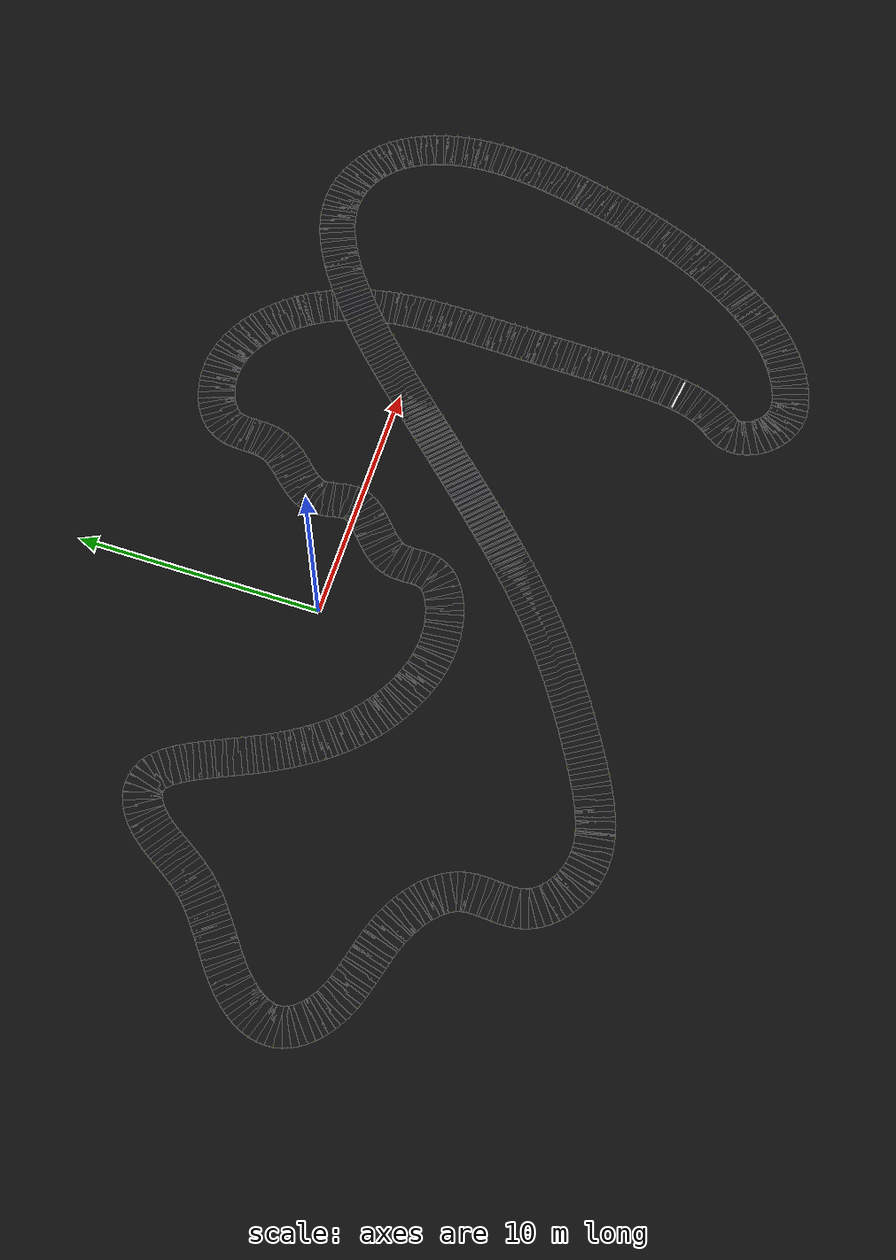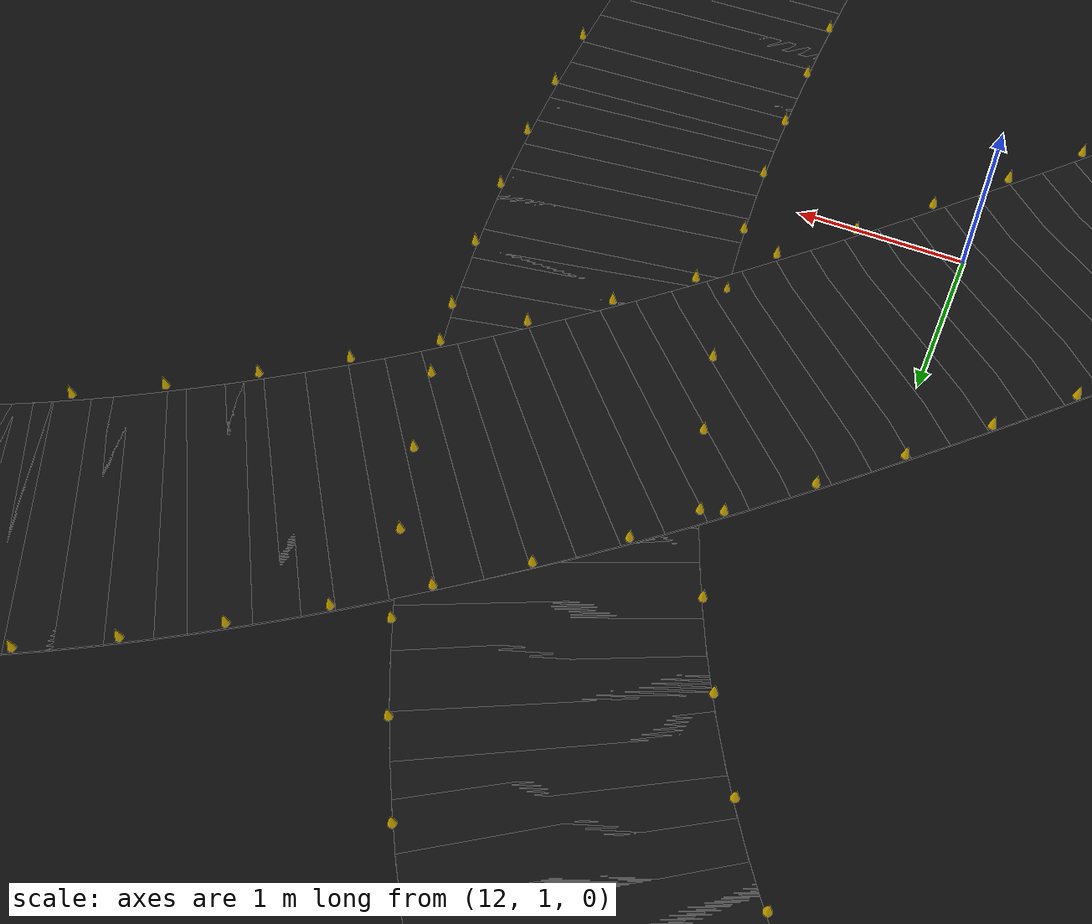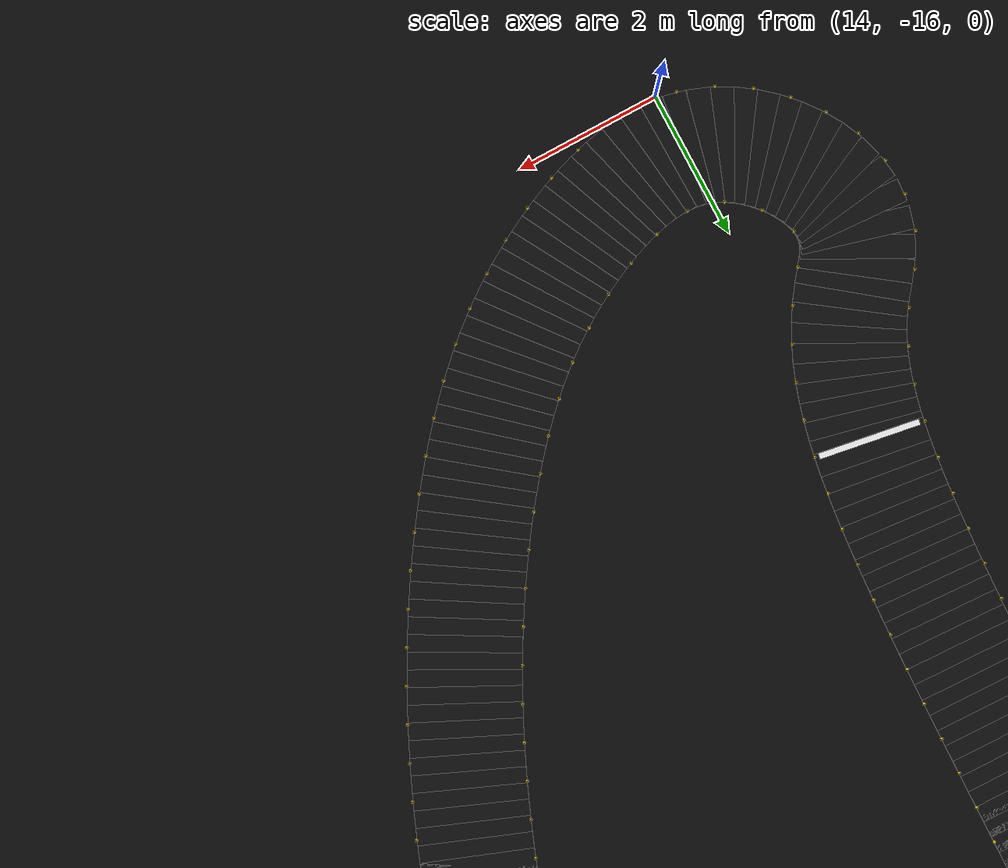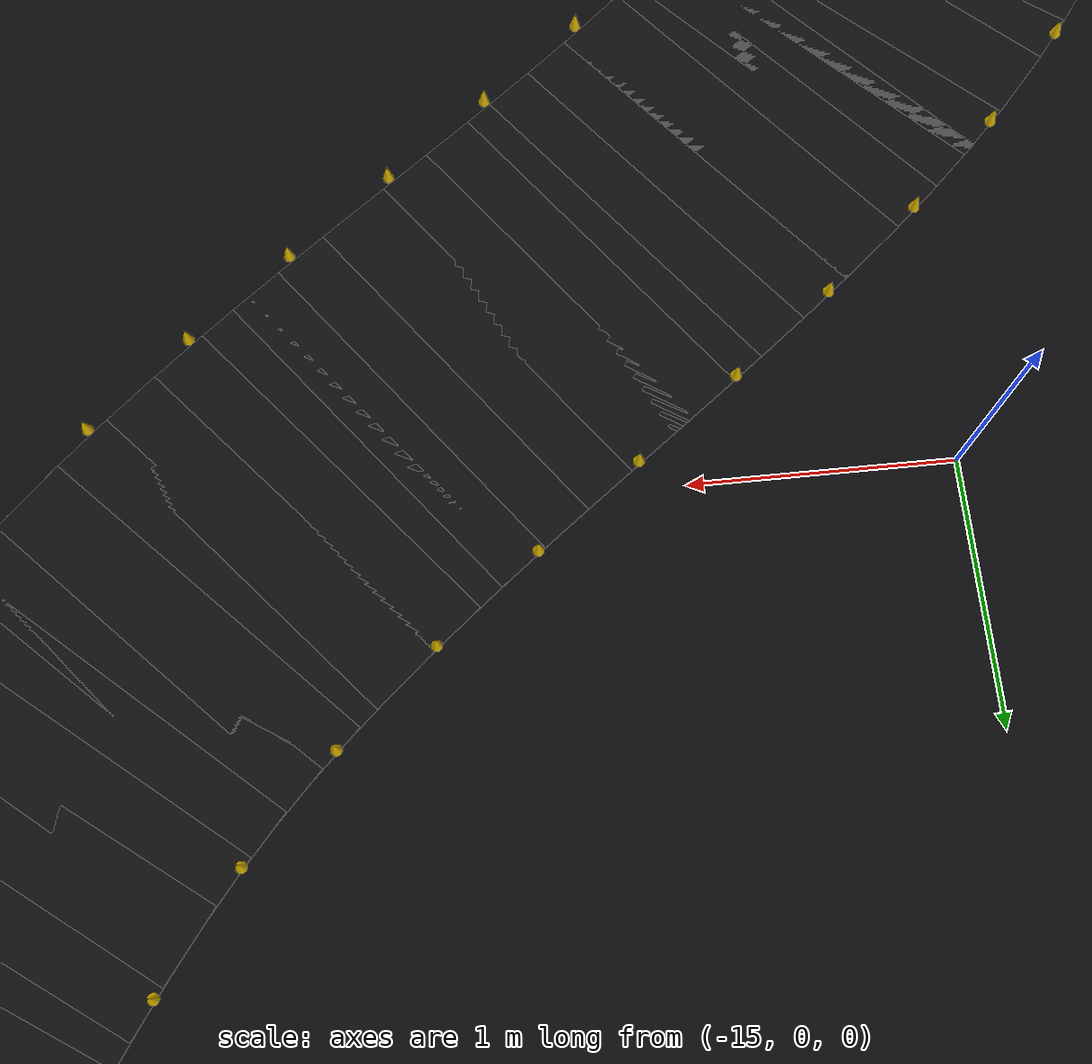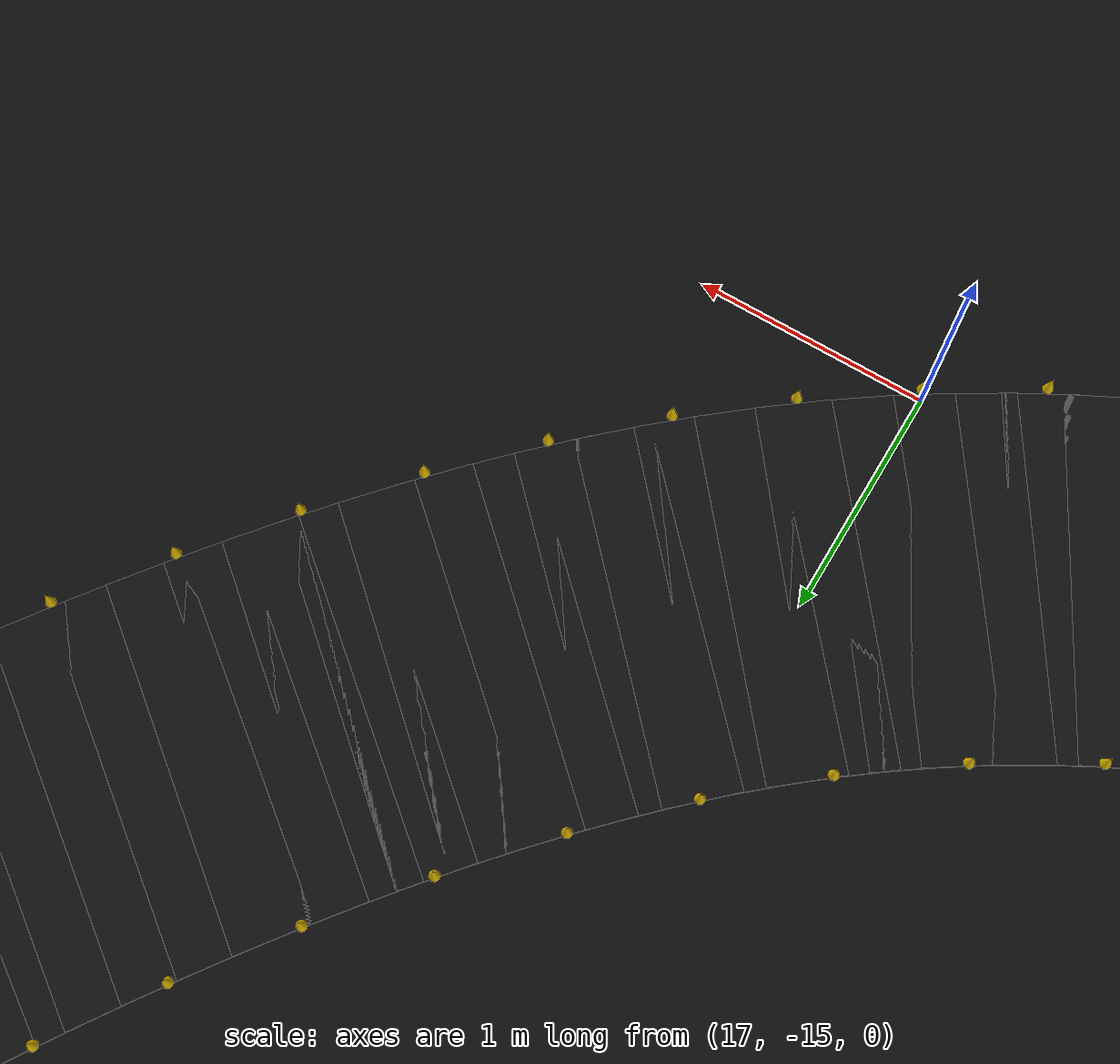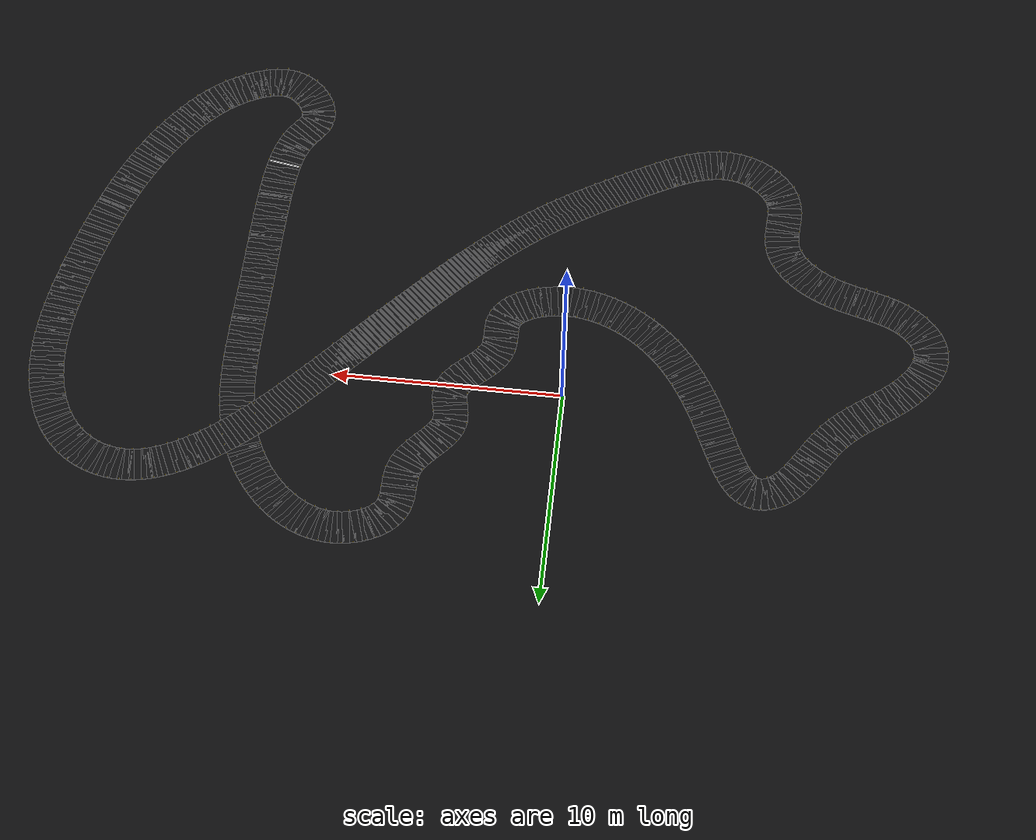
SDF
<?xml version='1.0'?>
<sdf version='1.10'>
  <world name='suzuka'>
    <physics name='1ms' type='ignored'><max_step_size>0.001</max_step_size><real_time_factor>1.0</real_time_factor></physics>
    <plugin filename='gz-sim-physics-system' name='gz::sim::systems::Physics'/>
    <plugin filename='gz-sim-user-commands-system' name='gz::sim::systems::UserCommands'/>
    <plugin filename='gz-sim-scene-broadcaster-system' name='gz::sim::systems::SceneBroadcaster'/>
    <scene><ambient>0.42 0.42 0.44 1</ambient><background>0.055 0.055 0.060 1</background><shadows>true</shadows></scene>
    <light name='sun' type='directional'><pose>0 0 30 0 0 0</pose><diffuse>0.9 0.9 0.9 1</diffuse><specular>0.2 0.2 0.2 1</specular><direction>-0.4 0.2 -1</direction></light>
    <model name='ground'><static>true</static><link name='ground_link'>
      <collision name='ground_collision'><geometry><plane><normal>0 0 1</normal><size>160 160</size></plane></geometry></collision>
      <visual name='ground_visual'><geometry><plane><normal>0 0 1</normal><size>160 160</size></plane></geometry><material><ambient>0.045 0.045 0.050 1</ambient><diffuse>0.045 0.045 0.050 1</diffuse></material></visual>
    </link></model>
    <model name='road'><static>true</static><link name='road_link'>
      <visual name='road_0'><pose>13.68095 -10.66940 0.00600 0 -0.0000000 1.4089726</pose><geometry><box><size>0.31013 1.50000 0.01200</size></box></geometry><material><ambient>0.055 0.055 0.060 1</ambient><diffuse>0.055 0.055 0.060 1</diffuse><specular>0.04 0.04 0.04 1</specular></material></visual>
      <visual name='road_1'><pose>13.71395 -10.45177 0.00600 0 -0.0000000 1.4316635</pose><geometry><box><size>0.31013 1.50000 0.01200</size></box></geometry><material><ambient>0.055 0.055 0.060 1</ambient><diffuse>0.055 0.055 0.060 1</diffuse><specular>0.04 0.04 0.04 1</specular></material></visual>
      <visual name='road_2'><pose>13.74246 -10.23351 0.00600 0 -0.0000000 1.4501139</pose><geometry><box><size>0.31013 1.50000 0.01200</size></box></geometry><material><ambient>0.055 0.055 0.060 1</ambient><diffuse>0.055 0.055 0.060 1</diffuse><specular>0.04 0.04 0.04 1</specular></material></visual>
      <visual name='road_3'><pose>13.76730 -10.01479 0.00600 0 -0.0000000 1.4653030</pose><geometry><box><size>0.31013 1.50000 0.01200</size></box></geometry><material><ambient>0.055 0.055 0.060 1</ambient><diffuse>0.055 0.055 0.060 1</diffuse><specular>0.04 0.04 0.04 1</specular></material></visual>
      <visual name='road_4'><pose>13.78910 -9.79575 0.00600 0 -0.0000000 1.4779469</pose><geometry><box><size>0.31013 1.50000 0.01200</size></box></geometry><material><ambient>0.055 0.055 0.060 1</ambient><diffuse>0.055 0.055 0.060 1</diffuse><specular>0.04 0.04 0.04 1</specular></material></visual>
      <visual name='road_5'><pose>13.80834 -9.57646 0.00600 0 -0.0000000 1.4885772</pose><geometry><box><size>0.31013 1.50000 0.01200</size></box></geometry><material><ambient>0.055 0.055 0.060 1</ambient><diffuse>0.055 0.055 0.060 1</diffuse><specular>0.04 0.04 0.04 1</specular></material></visual>
      <visual name='road_6'><pose>13.82543 -9.35700 0.00600 0 -0.0000000 1.4975946</pose><geometry><box><size>0.31013 1.50000 0.01200</size></box></geometry><material><ambient>0.055 0.055 0.060 1</ambient><diffuse>0.055 0.055 0.060 1</diffuse><specular>0.04 0.04 0.04 1</specular></material></visual>
      <visual name='road_7'><pose>13.84068 -9.13740 0.00600 0 -0.0000000 1.5053054</pose><geometry><box><size>0.31013 1.50000 0.01200</size></box></geometry><material><ambient>0.055 0.055 0.060 1</ambient><diffuse>0.055 0.055 0.060 1</diffuse><specular>0.04 0.04 0.04 1</specular></material></visual>
      <visual name='road_8'><pose>13.85432 -8.91769 0.00600 0 -0.0000000 1.5123016</pose><geometry><box><size>0.31013 1.50000 0.01200</size></box></geometry><material><ambient>0.055 0.055 0.060 1</ambient><diffuse>0.055 0.055 0.060 1</diffuse><specular>0.04 0.04 0.04 1</specular></material></visual>
      <visual name='road_9'><pose>13.86654 -8.69790 0.00600 0 -0.0000000 1.5181795</pose><geometry><box><size>0.31013 1.50000 0.01200</size></box></geometry><material><ambient>0.055 0.055 0.060 1</ambient><diffuse>0.055 0.055 0.060 1</diffuse><specular>0.04 0.04 0.04 1</specular></material></visual>
      <visual name='road_10'><pose>13.87758 -8.47804 0.00600 0 -0.0000000 1.5231241</pose><geometry><box><size>0.31013 1.50000 0.01200</size></box></geometry><material><ambient>0.055 0.055 0.060 1</ambient><diffuse>0.055 0.055 0.060 1</diffuse><specular>0.04 0.04 0.04 1</specular></material></visual>
      <visual name='road_11'><pose>13.88757 -8.25814 0.00600 0 -0.0000000 1.5276608</pose><geometry><box><size>0.31013 1.50000 0.01200</size></box></geometry><material><ambient>0.055 0.055 0.060 1</ambient><diffuse>0.055 0.055 0.060 1</diffuse><specular>0.04 0.04 0.04 1</specular></material></visual>
      <visual name='road_12'><pose>13.89662 -8.03819 0.00600 0 -0.0000000 1.5316465</pose><geometry><box><size>0.31013 1.50000 0.01200</size></box></geometry><material><ambient>0.055 0.055 0.060 1</ambient><diffuse>0.055 0.055 0.060 1</diffuse><specular>0.04 0.04 0.04 1</specular></material></visual>
      <visual name='road_13'><pose>13.90489 -7.81821 0.00600 0 -0.0000000 1.5348471</pose><geometry><box><size>0.31013 1.50000 0.01200</size></box></geometry><material><ambient>0.055 0.055 0.060 1</ambient><diffuse>0.055 0.055 0.060 1</diffuse><specular>0.04 0.04 0.04 1</specular></material></visual>
      <visual name='road_14'><pose>13.91245 -7.59821 0.00600 0 -0.0000000 1.5379791</pose><geometry><box><size>0.31013 1.50000 0.01200</size></box></geometry><material><ambient>0.055 0.055 0.060 1</ambient><diffuse>0.055 0.055 0.060 1</diffuse><specular>0.04 0.04 0.04 1</specular></material></visual>
      <visual name='road_15'><pose>13.91941 -7.37819 0.00600 0 -0.0000000 1.5403851</pose><geometry><box><size>0.31013 1.50000 0.01200</size></box></geometry><material><ambient>0.055 0.055 0.060 1</ambient><diffuse>0.055 0.055 0.060 1</diffuse><specular>0.04 0.04 0.04 1</specular></material></visual>
      <visual name='road_16'><pose>13.92587 -7.15815 0.00600 0 -0.0000000 1.5425465</pose><geometry><box><size>0.31013 1.50000 0.01200</size></box></geometry><material><ambient>0.055 0.055 0.060 1</ambient><diffuse>0.055 0.055 0.060 1</diffuse><specular>0.04 0.04 0.04 1</specular></material></visual>
      <visual name='road_17'><pose>13.93189 -6.93810 0.00600 0 -0.0000000 1.5443572</pose><geometry><box><size>0.31013 1.50000 0.01200</size></box></geometry><material><ambient>0.055 0.055 0.060 1</ambient><diffuse>0.055 0.055 0.060 1</diffuse><specular>0.04 0.04 0.04 1</specular></material></visual>
      <visual name='road_18'><pose>13.93755 -6.71804 0.00600 0 -0.0000000 1.5457633</pose><geometry><box><size>0.31013 1.50000 0.01200</size></box></geometry><material><ambient>0.055 0.055 0.060 1</ambient><diffuse>0.055 0.055 0.060 1</diffuse><specular>0.04 0.04 0.04 1</specular></material></visual>
      <visual name='road_19'><pose>13.94293 -6.49797 0.00600 0 -0.0000000 1.5469701</pose><geometry><box><size>0.31013 1.50000 0.01200</size></box></geometry><material><ambient>0.055 0.055 0.060 1</ambient><diffuse>0.055 0.055 0.060 1</diffuse><specular>0.04 0.04 0.04 1</specular></material></visual>
      <visual name='road_20'><pose>13.94809 -6.27790 0.00600 0 -0.0000000 1.5477537</pose><geometry><box><size>0.31013 1.50000 0.01200</size></box></geometry><material><ambient>0.055 0.055 0.060 1</ambient><diffuse>0.055 0.055 0.060 1</diffuse><specular>0.04 0.04 0.04 1</specular></material></visual>
      <visual name='road_21'><pose>13.95309 -6.05783 0.00600 0 -0.0000000 1.5483515</pose><geometry><box><size>0.31013 1.50000 0.01200</size></box></geometry><material><ambient>0.055 0.055 0.060 1</ambient><diffuse>0.055 0.055 0.060 1</diffuse><specular>0.04 0.04 0.04 1</specular></material></visual>
      <visual name='road_22'><pose>13.95801 -5.83775 0.00600 0 -0.0000000 1.5485890</pose><geometry><box><size>0.31013 1.50000 0.01200</size></box></geometry><material><ambient>0.055 0.055 0.060 1</ambient><diffuse>0.055 0.055 0.060 1</diffuse><specular>0.04 0.04 0.04 1</specular></material></visual>
      <visual name='road_23'><pose>13.96290 -5.61767 0.00600 0 -0.0000000 1.5485636</pose><geometry><box><size>0.31013 1.50000 0.01200</size></box></geometry><material><ambient>0.055 0.055 0.060 1</ambient><diffuse>0.055 0.055 0.060 1</diffuse><specular>0.04 0.04 0.04 1</specular></material></visual>
      <visual name='road_24'><pose>13.96782 -5.39759 0.00600 0 -0.0000000 1.5482707</pose><geometry><box><size>0.31013 1.50000 0.01200</size></box></geometry><material><ambient>0.055 0.055 0.060 1</ambient><diffuse>0.055 0.055 0.060 1</diffuse><specular>0.04 0.04 0.04 1</specular></material></visual>
      <visual name='road_25'><pose>13.97285 -5.17752 0.00600 0 -0.0000000 1.5476319</pose><geometry><box><size>0.31013 1.50000 0.01200</size></box></geometry><material><ambient>0.055 0.055 0.060 1</ambient><diffuse>0.055 0.055 0.060 1</diffuse><specular>0.04 0.04 0.04 1</specular></material></visual>
      <visual name='road_26'><pose>13.97805 -4.95745 0.00600 0 -0.0000000 1.5467600</pose><geometry><box><size>0.31013 1.50000 0.01200</size></box></geometry><material><ambient>0.055 0.055 0.060 1</ambient><diffuse>0.055 0.055 0.060 1</diffuse><specular>0.04 0.04 0.04 1</specular></material></visual>
      <visual name='road_27'><pose>13.98348 -4.73738 0.00600 0 -0.0000000 1.5455182</pose><geometry><box><size>0.31013 1.50000 0.01200</size></box></geometry><material><ambient>0.055 0.055 0.060 1</ambient><diffuse>0.055 0.055 0.060 1</diffuse><specular>0.04 0.04 0.04 1</specular></material></visual>
      <visual name='road_28'><pose>13.98921 -4.51732 0.00600 0 -0.0000000 1.5439634</pose><geometry><box><size>0.31013 1.50000 0.01200</size></box></geometry><material><ambient>0.055 0.055 0.060 1</ambient><diffuse>0.055 0.055 0.060 1</diffuse><specular>0.04 0.04 0.04 1</specular></material></visual>
      <visual name='road_29'><pose>13.99532 -4.29728 0.00600 0 -0.0000000 1.5421528</pose><geometry><box><size>0.31013 1.50000 0.01200</size></box></geometry><material><ambient>0.055 0.055 0.060 1</ambient><diffuse>0.055 0.055 0.060 1</diffuse><specular>0.04 0.04 0.04 1</specular></material></visual>
      <visual name='road_30'><pose>14.00184 -4.07724 0.00600 0 -0.0000000 1.5401977</pose><geometry><box><size>0.31013 1.50000 0.01200</size></box></geometry><material><ambient>0.055 0.055 0.060 1</ambient><diffuse>0.055 0.055 0.060 1</diffuse><specular>0.04 0.04 0.04 1</specular></material></visual>
      <visual name='road_31'><pose>14.00873 -3.85721 0.00600 0 -0.0000000 1.5387466</pose><geometry><box><size>0.31013 1.50000 0.01200</size></box></geometry><material><ambient>0.055 0.055 0.060 1</ambient><diffuse>0.055 0.055 0.060 1</diffuse><specular>0.04 0.04 0.04 1</specular></material></visual>
      <visual name='road_32'><pose>14.01592 -3.63720 0.00600 0 -0.0000000 1.5374854</pose><geometry><box><size>0.31013 1.50000 0.01200</size></box></geometry><material><ambient>0.055 0.055 0.060 1</ambient><diffuse>0.055 0.055 0.060 1</diffuse><specular>0.04 0.04 0.04 1</specular></material></visual>
      <visual name='road_33'><pose>14.02334 -3.41719 0.00600 0 -0.0000000 1.5366966</pose><geometry><box><size>0.31013 1.50000 0.01200</size></box></geometry><material><ambient>0.055 0.055 0.060 1</ambient><diffuse>0.055 0.055 0.060 1</diffuse><specular>0.04 0.04 0.04 1</specular></material></visual>
      <visual name='road_34'><pose>14.03089 -3.19719 0.00600 0 -0.0000000 1.5362786</pose><geometry><box><size>0.31013 1.50000 0.01200</size></box></geometry><material><ambient>0.055 0.055 0.060 1</ambient><diffuse>0.055 0.055 0.060 1</diffuse><specular>0.04 0.04 0.04 1</specular></material></visual>
      <visual name='road_35'><pose>14.03849 -2.97719 0.00600 0 -0.0000000 1.5362777</pose><geometry><box><size>0.31013 1.50000 0.01200</size></box></geometry><material><ambient>0.055 0.055 0.060 1</ambient><diffuse>0.055 0.055 0.060 1</diffuse><specular>0.04 0.04 0.04 1</specular></material></visual>
      <visual name='road_36'><pose>14.04604 -2.75718 0.00600 0 -0.0000000 1.5367345</pose><geometry><box><size>0.31013 1.50000 0.01200</size></box></geometry><material><ambient>0.055 0.055 0.060 1</ambient><diffuse>0.055 0.055 0.060 1</diffuse><specular>0.04 0.04 0.04 1</specular></material></visual>
      <visual name='road_37'><pose>14.05344 -2.53718 0.00600 0 -0.0000000 1.5376189</pose><geometry><box><size>0.31013 1.50000 0.01200</size></box></geometry><material><ambient>0.055 0.055 0.060 1</ambient><diffuse>0.055 0.055 0.060 1</diffuse><specular>0.04 0.04 0.04 1</specular></material></visual>
      <visual name='road_38'><pose>14.06058 -2.31716 0.00600 0 -0.0000000 1.5390913</pose><geometry><box><size>0.31013 1.50000 0.01200</size></box></geometry><material><ambient>0.055 0.055 0.060 1</ambient><diffuse>0.055 0.055 0.060 1</diffuse><specular>0.04 0.04 0.04 1</specular></material></visual>
      <visual name='road_39'><pose>14.06733 -2.09713 0.00600 0 -0.0000000 1.5410916</pose><geometry><box><size>0.31013 1.50000 0.01200</size></box></geometry><material><ambient>0.055 0.055 0.060 1</ambient><diffuse>0.055 0.055 0.060 1</diffuse><specular>0.04 0.04 0.04 1</specular></material></visual>
      <visual name='road_40'><pose>14.07360 -1.87709 0.00600 0 -0.0000000 1.5435954</pose><geometry><box><size>0.31013 1.50000 0.01200</size></box></geometry><material><ambient>0.055 0.055 0.060 1</ambient><diffuse>0.055 0.055 0.060 1</diffuse><specular>0.04 0.04 0.04 1</specular></material></visual>
      <visual name='road_41'><pose>14.07924 -1.65703 0.00600 0 -0.0000000 1.5466961</pose><geometry><box><size>0.31013 1.50000 0.01200</size></box></geometry><material><ambient>0.055 0.055 0.060 1</ambient><diffuse>0.055 0.055 0.060 1</diffuse><specular>0.04 0.04 0.04 1</specular></material></visual>
      <visual name='road_42'><pose>14.08412 -1.43695 0.00600 0 -0.0000000 1.5505446</pose><geometry><box><size>0.31013 1.50000 0.01200</size></box></geometry><material><ambient>0.055 0.055 0.060 1</ambient><diffuse>0.055 0.055 0.060 1</diffuse><specular>0.04 0.04 0.04 1</specular></material></visual>
      <visual name='road_43'><pose>14.08807 -1.21685 0.00600 0 -0.0000000 1.5551833</pose><geometry><box><size>0.31013 1.50000 0.01200</size></box></geometry><material><ambient>0.055 0.055 0.060 1</ambient><diffuse>0.055 0.055 0.060 1</diffuse><specular>0.04 0.04 0.04 1</specular></material></visual>
      <visual name='road_44'><pose>14.09093 -0.99674 0.00600 0 -0.0000000 1.5604307</pose><geometry><box><size>0.31013 1.50000 0.01200</size></box></geometry><material><ambient>0.055 0.055 0.060 1</ambient><diffuse>0.055 0.055 0.060 1</diffuse><specular>0.04 0.04 0.04 1</specular></material></visual>
      <visual name='road_45'><pose>14.09254 -0.77662 0.00600 0 -0.0000000 1.5664887</pose><geometry><box><size>0.31013 1.50000 0.01200</size></box></geometry><material><ambient>0.055 0.055 0.060 1</ambient><diffuse>0.055 0.055 0.060 1</diffuse><specular>0.04 0.04 0.04 1</specular></material></visual>
      <visual name='road_46'><pose>14.09273 -0.55648 0.00600 0 -0.0000000 1.5734226</pose><geometry><box><size>0.31013 1.50000 0.01200</size></box></geometry><material><ambient>0.055 0.055 0.060 1</ambient><diffuse>0.055 0.055 0.060 1</diffuse><specular>0.04 0.04 0.04 1</specular></material></visual>
      <visual name='road_47'><pose>14.09128 -0.33636 0.00600 0 -0.0000000 1.5813016</pose><geometry><box><size>0.31013 1.50000 0.01200</size></box></geometry><material><ambient>0.055 0.055 0.060 1</ambient><diffuse>0.055 0.055 0.060 1</diffuse><specular>0.04 0.04 0.04 1</specular></material></visual>
      <visual name='road_48'><pose>14.08799 -0.11625 0.00600 0 -0.0000000 1.5901987</pose><geometry><box><size>0.31013 1.50000 0.01200</size></box></geometry><material><ambient>0.055 0.055 0.060 1</ambient><diffuse>0.055 0.055 0.060 1</diffuse><specular>0.04 0.04 0.04 1</specular></material></visual>
      <visual name='road_49'><pose>14.08262 0.10381 0.00600 0 -0.0000000 1.6001909</pose><geometry><box><size>0.31013 1.50000 0.01200</size></box></geometry><material><ambient>0.055 0.055 0.060 1</ambient><diffuse>0.055 0.055 0.060 1</diffuse><specular>0.04 0.04 0.04 1</specular></material></visual>
      <visual name='road_50'><pose>14.07492 0.32380 0.00600 0 -0.0000000 1.6113587</pose><geometry><box><size>0.31013 1.50000 0.01200</size></box></geometry><material><ambient>0.055 0.055 0.060 1</ambient><diffuse>0.055 0.055 0.060 1</diffuse><specular>0.04 0.04 0.04 1</specular></material></visual>
      <visual name='road_51'><pose>14.06463 0.54369 0.00600 0 -0.0000000 1.6237862</pose><geometry><box><size>0.31013 1.50000 0.01200</size></box></geometry><material><ambient>0.055 0.055 0.060 1</ambient><diffuse>0.055 0.055 0.060 1</diffuse><specular>0.04 0.04 0.04 1</specular></material></visual>
      <visual name='road_52'><pose>14.05146 0.76342 0.00600 0 -0.0000000 1.6375602</pose><geometry><box><size>0.31013 1.50000 0.01200</size></box></geometry><material><ambient>0.055 0.055 0.060 1</ambient><diffuse>0.055 0.055 0.060 1</diffuse><specular>0.04 0.04 0.04 1</specular></material></visual>
      <visual name='road_53'><pose>14.03510 0.98293 0.00600 0 -0.0000000 1.6527693</pose><geometry><box><size>0.31013 1.50000 0.01200</size></box></geometry><material><ambient>0.055 0.055 0.060 1</ambient><diffuse>0.055 0.055 0.060 1</diffuse><specular>0.04 0.04 0.04 1</specular></material></visual>
      <visual name='road_54'><pose>14.01524 1.20216 0.00600 0 -0.0000000 1.6695035</pose><geometry><box><size>0.31013 1.50000 0.01200</size></box></geometry><material><ambient>0.055 0.055 0.060 1</ambient><diffuse>0.055 0.055 0.060 1</diffuse><specular>0.04 0.04 0.04 1</specular></material></visual>
      <visual name='road_55'><pose>13.99154 1.42100 0.00600 0 -0.0000000 1.6878523</pose><geometry><box><size>0.31013 1.50000 0.01200</size></box></geometry><material><ambient>0.055 0.055 0.060 1</ambient><diffuse>0.055 0.055 0.060 1</diffuse><specular>0.04 0.04 0.04 1</specular></material></visual>
      <visual name='road_56'><pose>13.96365 1.63934 0.00600 0 -0.0000000 1.7078849</pose><geometry><box><size>0.31013 1.50000 0.01200</size></box></geometry><material><ambient>0.055 0.055 0.060 1</ambient><diffuse>0.055 0.055 0.060 1</diffuse><specular>0.04 0.04 0.04 1</specular></material></visual>
      <visual name='road_57'><pose>13.93119 1.85705 0.00600 0 -0.0000000 1.7297429</pose><geometry><box><size>0.31013 1.50000 0.01200</size></box></geometry><material><ambient>0.055 0.055 0.060 1</ambient><diffuse>0.055 0.055 0.060 1</diffuse><specular>0.04 0.04 0.04 1</specular></material></visual>
      <visual name='road_58'><pose>13.89391 2.07398 0.00600 0 -0.0000000 1.7521701</pose><geometry><box><size>0.31013 1.50000 0.01200</size></box></geometry><material><ambient>0.055 0.055 0.060 1</ambient><diffuse>0.055 0.055 0.060 1</diffuse><specular>0.04 0.04 0.04 1</specular></material></visual>
      <visual name='road_59'><pose>13.85177 2.29002 0.00600 0 -0.0000000 1.7747457</pose><geometry><box><size>0.31013 1.50000 0.01200</size></box></geometry><material><ambient>0.055 0.055 0.060 1</ambient><diffuse>0.055 0.055 0.060 1</diffuse><specular>0.04 0.04 0.04 1</specular></material></visual>
      <visual name='road_60'><pose>13.80470 2.50504 0.00600 0 -0.0000000 1.7978666</pose><geometry><box><size>0.31013 1.50000 0.01200</size></box></geometry><material><ambient>0.055 0.055 0.060 1</ambient><diffuse>0.055 0.055 0.060 1</diffuse><specular>0.04 0.04 0.04 1</specular></material></visual>
      <visual name='road_61'><pose>13.75245 2.71886 0.00600 0 -0.0000000 1.8230470</pose><geometry><box><size>0.31013 1.50000 0.01200</size></box></geometry><material><ambient>0.055 0.055 0.060 1</ambient><diffuse>0.055 0.055 0.060 1</diffuse><specular>0.04 0.04 0.04 1</specular></material></visual>
      <visual name='road_62'><pose>13.69492 2.93132 0.00600 0 -0.0000000 1.8474379</pose><geometry><box><size>0.31013 1.50000 0.01200</size></box></geometry><material><ambient>0.055 0.055 0.060 1</ambient><diffuse>0.055 0.055 0.060 1</diffuse><specular>0.04 0.04 0.04 1</specular></material></visual>
      <visual name='road_63'><pose>13.63210 3.14227 0.00600 0 -0.0000000 1.8729754</pose><geometry><box><size>0.31013 1.50000 0.01200</size></box></geometry><material><ambient>0.055 0.055 0.060 1</ambient><diffuse>0.055 0.055 0.060 1</diffuse><specular>0.04 0.04 0.04 1</specular></material></visual>
      <visual name='road_64'><pose>13.56380 3.35151 0.00600 0 -0.0000000 1.8997127</pose><geometry><box><size>0.31013 1.50000 0.01200</size></box></geometry><material><ambient>0.055 0.055 0.060 1</ambient><diffuse>0.055 0.055 0.060 1</diffuse><specular>0.04 0.04 0.04 1</specular></material></visual>
      <visual name='road_65'><pose>13.48995 3.55886 0.00600 0 -0.0000000 1.9261736</pose><geometry><box><size>0.31012 1.50000 0.01200</size></box></geometry><material><ambient>0.055 0.055 0.060 1</ambient><diffuse>0.055 0.055 0.060 1</diffuse><specular>0.04 0.04 0.04 1</specular></material></visual>
      <visual name='road_66'><pose>13.41044 3.76410 0.00600 0 -0.0000000 1.9545998</pose><geometry><box><size>0.31012 1.50000 0.01200</size></box></geometry><material><ambient>0.055 0.055 0.060 1</ambient><diffuse>0.055 0.055 0.060 1</diffuse><specular>0.04 0.04 0.04 1</specular></material></visual>
      <visual name='road_67'><pose>13.32518 3.96701 0.00600 0 -0.0000000 1.9825267</pose><geometry><box><size>0.31012 1.50000 0.01200</size></box></geometry><material><ambient>0.055 0.055 0.060 1</ambient><diffuse>0.055 0.055 0.060 1</diffuse><specular>0.04 0.04 0.04 1</specular></material></visual>
      <visual name='road_68'><pose>13.23414 4.16740 0.00600 0 -0.0000000 2.0119643</pose><geometry><box><size>0.31012 1.50000 0.01200</size></box></geometry><material><ambient>0.055 0.055 0.060 1</ambient><diffuse>0.055 0.055 0.060 1</diffuse><specular>0.04 0.04 0.04 1</specular></material></visual>
      <visual name='road_69'><pose>13.13719 4.36500 0.00600 0 -0.0000000 2.0418632</pose><geometry><box><size>0.31012 1.50000 0.01200</size></box></geometry><material><ambient>0.055 0.055 0.060 1</ambient><diffuse>0.055 0.055 0.060 1</diffuse><specular>0.04 0.04 0.04 1</specular></material></visual>
      <visual name='road_70'><pose>13.03438 4.55961 0.00600 0 -0.0000000 2.0718315</pose><geometry><box><size>0.31012 1.50000 0.01200</size></box></geometry><material><ambient>0.055 0.055 0.060 1</ambient><diffuse>0.055 0.055 0.060 1</diffuse><specular>0.04 0.04 0.04 1</specular></material></visual>
      <visual name='road_71'><pose>12.92559 4.75094 0.00600 0 -0.0000000 2.1037507</pose><geometry><box><size>0.31012 1.50000 0.01200</size></box></geometry><material><ambient>0.055 0.055 0.060 1</ambient><diffuse>0.055 0.055 0.060 1</diffuse><specular>0.04 0.04 0.04 1</specular></material></visual>
      <visual name='road_72'><pose>12.81078 4.93872 0.00600 0 -0.0000000 2.1353398</pose><geometry><box><size>0.31012 1.50000 0.01200</size></box></geometry><material><ambient>0.055 0.055 0.060 1</ambient><diffuse>0.055 0.055 0.060 1</diffuse><specular>0.04 0.04 0.04 1</specular></material></visual>
      <visual name='road_73'><pose>12.69006 5.12275 0.00600 0 -0.0000000 2.1674402</pose><geometry><box><size>0.31012 1.50000 0.01200</size></box></geometry><material><ambient>0.055 0.055 0.060 1</ambient><diffuse>0.055 0.055 0.060 1</diffuse><specular>0.04 0.04 0.04 1</specular></material></visual>
      <visual name='road_74'><pose>12.56342 5.30276 0.00600 0 -0.0000000 2.2002657</pose><geometry><box><size>0.31012 1.50000 0.01200</size></box></geometry><material><ambient>0.055 0.055 0.060 1</ambient><diffuse>0.055 0.055 0.060 1</diffuse><specular>0.04 0.04 0.04 1</specular></material></visual>
      <visual name='road_75'><pose>12.43084 5.47843 0.00600 0 -0.0000000 2.2344043</pose><geometry><box><size>0.31012 1.50000 0.01200</size></box></geometry><material><ambient>0.055 0.055 0.060 1</ambient><diffuse>0.055 0.055 0.060 1</diffuse><specular>0.04 0.04 0.04 1</specular></material></visual>
      <visual name='road_76'><pose>12.29236 5.64949 0.00600 0 -0.0000000 2.2682340</pose><geometry><box><size>0.31012 1.50000 0.01200</size></box></geometry><material><ambient>0.055 0.055 0.060 1</ambient><diffuse>0.055 0.055 0.060 1</diffuse><specular>0.04 0.04 0.04 1</specular></material></visual>
      <visual name='road_77'><pose>12.14810 5.81571 0.00600 0 -0.0000000 2.3028803</pose><geometry><box><size>0.31012 1.50000 0.01200</size></box></geometry><material><ambient>0.055 0.055 0.060 1</ambient><diffuse>0.055 0.055 0.060 1</diffuse><specular>0.04 0.04 0.04 1</specular></material></visual>
      <visual name='road_78'><pose>11.99809 5.97675 0.00600 0 -0.0000000 2.3386443</pose><geometry><box><size>0.31012 1.50000 0.01200</size></box></geometry><material><ambient>0.055 0.055 0.060 1</ambient><diffuse>0.055 0.055 0.060 1</diffuse><specular>0.04 0.04 0.04 1</specular></material></visual>
      <visual name='road_79'><pose>11.84232 6.13222 0.00600 0 -0.0000000 2.3756766</pose><geometry><box><size>0.31012 1.50000 0.01200</size></box></geometry><material><ambient>0.055 0.055 0.060 1</ambient><diffuse>0.055 0.055 0.060 1</diffuse><specular>0.04 0.04 0.04 1</specular></material></visual>
      <visual name='road_80'><pose>11.68080 6.28170 0.00600 0 -0.0000000 2.4141290</pose><geometry><box><size>0.31012 1.50000 0.01200</size></box></geometry><material><ambient>0.055 0.055 0.060 1</ambient><diffuse>0.055 0.055 0.060 1</diffuse><specular>0.04 0.04 0.04 1</specular></material></visual>
      <visual name='road_81'><pose>11.51354 6.42472 0.00600 0 -0.0000000 2.4541623</pose><geometry><box><size>0.31012 1.50000 0.01200</size></box></geometry><material><ambient>0.055 0.055 0.060 1</ambient><diffuse>0.055 0.055 0.060 1</diffuse><specular>0.04 0.04 0.04 1</specular></material></visual>
      <visual name='road_82'><pose>11.34057 6.56078 0.00600 0 -0.0000000 2.4959449</pose><geometry><box><size>0.31011 1.50000 0.01200</size></box></geometry><material><ambient>0.055 0.055 0.060 1</ambient><diffuse>0.055 0.055 0.060 1</diffuse><specular>0.04 0.04 0.04 1</specular></material></visual>
      <visual name='road_83'><pose>11.16196 6.68932 0.00600 0 -0.0000000 2.5396500</pose><geometry><box><size>0.31011 1.50000 0.01200</size></box></geometry><material><ambient>0.055 0.055 0.060 1</ambient><diffuse>0.055 0.055 0.060 1</diffuse><specular>0.04 0.04 0.04 1</specular></material></visual>
      <visual name='road_84'><pose>10.97778 6.80974 0.00600 0 -0.0000000 2.5854520</pose><geometry><box><size>0.31011 1.50000 0.01200</size></box></geometry><material><ambient>0.055 0.055 0.060 1</ambient><diffuse>0.055 0.055 0.060 1</diffuse><specular>0.04 0.04 0.04 1</specular></material></visual>
      <visual name='road_85'><pose>10.78816 6.92138 0.00600 0 -0.0000000 2.6335211</pose><geometry><box><size>0.31011 1.50000 0.01200</size></box></geometry><material><ambient>0.055 0.055 0.060 1</ambient><diffuse>0.055 0.055 0.060 1</diffuse><specular>0.04 0.04 0.04 1</specular></material></visual>
      <visual name='road_86'><pose>10.59328 7.02354 0.00600 0 -0.0000000 2.6840165</pose><geometry><box><size>0.31010 1.50000 0.01200</size></box></geometry><material><ambient>0.055 0.055 0.060 1</ambient><diffuse>0.055 0.055 0.060 1</diffuse><specular>0.04 0.04 0.04 1</specular></material></visual>
      <visual name='road_87'><pose>10.39337 7.11547 0.00600 0 -0.0000000 2.7370765</pose><geometry><box><size>0.31010 1.50000 0.01200</size></box></geometry><material><ambient>0.055 0.055 0.060 1</ambient><diffuse>0.055 0.055 0.060 1</diffuse><specular>0.04 0.04 0.04 1</specular></material></visual>
      <visual name='road_88'><pose>10.18874 7.19628 0.00600 0 -0.0000000 2.7939309</pose><geometry><box><size>0.31010 1.50000 0.01200</size></box></geometry><material><ambient>0.055 0.055 0.060 1</ambient><diffuse>0.055 0.055 0.060 1</diffuse><specular>0.04 0.04 0.04 1</specular></material></visual>
      <visual name='road_89'><pose>9.97978 7.26510 0.00600 0 -0.0000000 2.8528795</pose><geometry><box><size>0.31009 1.50000 0.01200</size></box></geometry><material><ambient>0.055 0.055 0.060 1</ambient><diffuse>0.055 0.055 0.060 1</diffuse><specular>0.04 0.04 0.04 1</specular></material></visual>
      <visual name='road_90'><pose>9.76707 7.32123 0.00600 0 -0.0000000 2.9143124</pose><geometry><box><size>0.31009 1.50000 0.01200</size></box></geometry><material><ambient>0.055 0.055 0.060 1</ambient><diffuse>0.055 0.055 0.060 1</diffuse><specular>0.04 0.04 0.04 1</specular></material></visual>
      <visual name='road_91'><pose>9.55126 7.36384 0.00600 0 -0.0000000 2.9790457</pose><geometry><box><size>0.31009 1.50000 0.01200</size></box></geometry><material><ambient>0.055 0.055 0.060 1</ambient><diffuse>0.055 0.055 0.060 1</diffuse><specular>0.04 0.04 0.04 1</specular></material></visual>
      <visual name='road_92'><pose>9.33312 7.39205 0.00600 0 -0.0000000 3.0468779</pose><geometry><box><size>0.31009 1.50000 0.01200</size></box></geometry><material><ambient>0.055 0.055 0.060 1</ambient><diffuse>0.055 0.055 0.060 1</diffuse><specular>0.04 0.04 0.04 1</specular></material></visual>
      <visual name='road_93'><pose>9.11357 7.40556 0.00600 0 -0.0000000 3.1133781</pose><geometry><box><size>0.31009 1.50000 0.01200</size></box></geometry><material><ambient>0.055 0.055 0.060 1</ambient><diffuse>0.055 0.055 0.060 1</diffuse><specular>0.04 0.04 0.04 1</specular></material></visual>
      <visual name='road_94'><pose>8.89360 7.40461 0.00600 0 -0.0000000 -3.1046644</pose><geometry><box><size>0.31009 1.50000 0.01200</size></box></geometry><material><ambient>0.055 0.055 0.060 1</ambient><diffuse>0.055 0.055 0.060 1</diffuse><specular>0.04 0.04 0.04 1</specular></material></visual>
      <visual name='road_95'><pose>8.67413 7.38949 0.00600 0 -0.0000000 -3.0410042</pose><geometry><box><size>0.31009 1.50000 0.01200</size></box></geometry><material><ambient>0.055 0.055 0.060 1</ambient><diffuse>0.055 0.055 0.060 1</diffuse><specular>0.04 0.04 0.04 1</specular></material></visual>
      <visual name='road_96'><pose>8.45604 7.36068 0.00600 0 -0.0000000 -2.9794421</pose><geometry><box><size>0.31009 1.50000 0.01200</size></box></geometry><material><ambient>0.055 0.055 0.060 1</ambient><diffuse>0.055 0.055 0.060 1</diffuse><specular>0.04 0.04 0.04 1</specular></material></visual>
      <visual name='road_97'><pose>8.24019 7.31826 0.00600 0 -0.0000000 -2.9157158</pose><geometry><box><size>0.31009 1.50000 0.01200</size></box></geometry><material><ambient>0.055 0.055 0.060 1</ambient><diffuse>0.055 0.055 0.060 1</diffuse><specular>0.04 0.04 0.04 1</specular></material></visual>
      <visual name='road_98'><pose>8.02744 7.26230 0.00600 0 -0.0000000 -2.8530180</pose><geometry><box><size>0.31009 1.50000 0.01200</size></box></geometry><material><ambient>0.055 0.055 0.060 1</ambient><diffuse>0.055 0.055 0.060 1</diffuse><specular>0.04 0.04 0.04 1</specular></material></visual>
      <visual name='road_99'><pose>7.81880 7.19262 0.00600 0 -0.0000000 -2.7854852</pose><geometry><box><size>0.31009 1.50000 0.01200</size></box></geometry><material><ambient>0.055 0.055 0.060 1</ambient><diffuse>0.055 0.055 0.060 1</diffuse><specular>0.04 0.04 0.04 1</specular></material></visual>
      <visual name='road_100'><pose>7.61547 7.10877 0.00600 0 -0.0000000 -2.7154330</pose><geometry><box><size>0.31008 1.50000 0.01200</size></box></geometry><material><ambient>0.055 0.055 0.060 1</ambient><diffuse>0.055 0.055 0.060 1</diffuse><specular>0.04 0.04 0.04 1</specular></material></visual>
      <visual name='road_101'><pose>7.41888 7.01021 0.00600 0 -0.0000000 -2.6383764</pose><geometry><box><size>0.31007 1.50000 0.01200</size></box></geometry><material><ambient>0.055 0.055 0.060 1</ambient><diffuse>0.055 0.055 0.060 1</diffuse><specular>0.04 0.04 0.04 1</specular></material></visual>
      <visual name='road_102'><pose>7.23107 6.89592 0.00600 0 -0.0000000 -2.5513746</pose><geometry><box><size>0.31005 1.50000 0.01200</size></box></geometry><material><ambient>0.055 0.055 0.060 1</ambient><diffuse>0.055 0.055 0.060 1</diffuse><specular>0.04 0.04 0.04 1</specular></material></visual>
      <visual name='road_103'><pose>7.05489 6.76457 0.00600 0 -0.0000000 -2.4505280</pose><geometry><box><size>0.31002 1.50000 0.01200</size></box></geometry><material><ambient>0.055 0.055 0.060 1</ambient><diffuse>0.055 0.055 0.060 1</diffuse><specular>0.04 0.04 0.04 1</specular></material></visual>
      <visual name='road_104'><pose>6.89435 6.61474 0.00600 0 -0.0000000 -2.3308506</pose><geometry><box><size>0.30996 1.50000 0.01200</size></box></geometry><material><ambient>0.055 0.055 0.060 1</ambient><diffuse>0.055 0.055 0.060 1</diffuse><specular>0.04 0.04 0.04 1</specular></material></visual>
      <visual name='road_105'><pose>6.75529 6.44513 0.00600 0 -0.0000000 -2.1841864</pose><geometry><box><size>0.30987 1.50000 0.01200</size></box></geometry><material><ambient>0.055 0.055 0.060 1</ambient><diffuse>0.055 0.055 0.060 1</diffuse><specular>0.04 0.04 0.04 1</specular></material></visual>
      <visual name='road_106'><pose>6.64493 6.25590 0.00600 0 -0.0000000 -2.0133554</pose><geometry><box><size>0.30985 1.50000 0.01200</size></box></geometry><material><ambient>0.055 0.055 0.060 1</ambient><diffuse>0.055 0.055 0.060 1</diffuse><specular>0.04 0.04 0.04 1</specular></material></visual>
      <visual name='road_107'><pose>6.56697 6.05102 0.00600 0 -0.0000000 -1.8554520</pose><geometry><box><size>0.30995 1.50000 0.01200</size></box></geometry><material><ambient>0.055 0.055 0.060 1</ambient><diffuse>0.055 0.055 0.060 1</diffuse><specular>0.04 0.04 0.04 1</specular></material></visual>
      <visual name='road_108'><pose>6.51835 5.83689 0.00600 0 -0.0000000 -1.7327161</pose><geometry><box><size>0.31004 1.50000 0.01200</size></box></geometry><material><ambient>0.055 0.055 0.060 1</ambient><diffuse>0.055 0.055 0.060 1</diffuse><specular>0.04 0.04 0.04 1</specular></material></visual>
      <visual name='road_109'><pose>6.49191 5.61861 0.00600 0 -0.0000000 -1.6499974</pose><geometry><box><size>0.31009 1.50000 0.01200</size></box></geometry><material><ambient>0.055 0.055 0.060 1</ambient><diffuse>0.055 0.055 0.060 1</diffuse><specular>0.04 0.04 0.04 1</specular></material></visual>
      <visual name='road_110'><pose>6.47947 5.39890 0.00600 0 -0.0000000 -1.6047208</pose><geometry><box><size>0.31012 1.50000 0.01200</size></box></geometry><material><ambient>0.055 0.055 0.060 1</ambient><diffuse>0.055 0.055 0.060 1</diffuse><specular>0.04 0.04 0.04 1</specular></material></visual>
      <visual name='road_111'><pose>6.47337 5.17886 0.00600 0 -0.0000000 -1.5923141</pose><geometry><box><size>0.31013 1.50000 0.01200</size></box></geometry><material><ambient>0.055 0.055 0.060 1</ambient><diffuse>0.055 0.055 0.060 1</diffuse><specular>0.04 0.04 0.04 1</specular></material></visual>
      <visual name='road_112'><pose>6.46661 4.95885 0.00600 0 -0.0000000 -1.6107160</pose><geometry><box><size>0.31012 1.50000 0.01200</size></box></geometry><material><ambient>0.055 0.055 0.060 1</ambient><diffuse>0.055 0.055 0.060 1</diffuse><specular>0.04 0.04 0.04 1</specular></material></visual>
      <visual name='road_113'><pose>6.45258 4.73925 0.00600 0 -0.0000000 -1.6584845</pose><geometry><box><size>0.31009 1.50000 0.01200</size></box></geometry><material><ambient>0.055 0.055 0.060 1</ambient><diffuse>0.055 0.055 0.060 1</diffuse><specular>0.04 0.04 0.04 1</specular></material></visual>
      <visual name='road_114'><pose>6.42487 4.52110 0.00600 0 -0.0000000 -1.7357746</pose><geometry><box><size>0.31005 1.50000 0.01200</size></box></geometry><material><ambient>0.055 0.055 0.060 1</ambient><diffuse>0.055 0.055 0.060 1</diffuse><specular>0.04 0.04 0.04 1</specular></material></visual>
      <visual name='road_115'><pose>6.37739 4.30657 0.00600 0 -0.0000000 -1.8414481</pose><geometry><box><size>0.31000 1.50000 0.01200</size></box></geometry><material><ambient>0.055 0.055 0.060 1</ambient><diffuse>0.055 0.055 0.060 1</diffuse><specular>0.04 0.04 0.04 1</specular></material></visual>
      <visual name='road_116'><pose>6.30543 4.09916 0.00600 0 -0.0000000 -1.9680862</pose><geometry><box><size>0.30996 1.50000 0.01200</size></box></geometry><material><ambient>0.055 0.055 0.060 1</ambient><diffuse>0.055 0.055 0.060 1</diffuse><specular>0.04 0.04 0.04 1</specular></material></visual>
      <visual name='road_117'><pose>6.20847 3.90213 0.00600 0 -0.0000000 -2.0880931</pose><geometry><box><size>0.31003 1.50000 0.01200</size></box></geometry><material><ambient>0.055 0.055 0.060 1</ambient><diffuse>0.055 0.055 0.060 1</diffuse><specular>0.04 0.04 0.04 1</specular></material></visual>
      <visual name='road_118'><pose>6.09135 3.71609 0.00600 0 -0.0000000 -2.1771901</pose><geometry><box><size>0.31008 1.50000 0.01200</size></box></geometry><material><ambient>0.055 0.055 0.060 1</ambient><diffuse>0.055 0.055 0.060 1</diffuse><specular>0.04 0.04 0.04 1</specular></material></visual>
      <visual name='road_119'><pose>5.96041 3.53931 0.00600 0 -0.0000000 -2.2393832</pose><geometry><box><size>0.31011 1.50000 0.01200</size></box></geometry><material><ambient>0.055 0.055 0.060 1</ambient><diffuse>0.055 0.055 0.060 1</diffuse><specular>0.04 0.04 0.04 1</specular></material></visual>
      <visual name='road_120'><pose>5.82040 3.36953 0.00600 0 -0.0000000 -2.2814163</pose><geometry><box><size>0.31012 1.50000 0.01200</size></box></geometry><material><ambient>0.055 0.055 0.060 1</ambient><diffuse>0.055 0.055 0.060 1</diffuse><specular>0.04 0.04 0.04 1</specular></material></visual>
      <visual name='road_121'><pose>5.67471 3.20454 0.00600 0 -0.0000000 -2.3069309</pose><geometry><box><size>0.31013 1.50000 0.01200</size></box></geometry><material><ambient>0.055 0.055 0.060 1</ambient><diffuse>0.055 0.055 0.060 1</diffuse><specular>0.04 0.04 0.04 1</specular></material></visual>
      <visual name='road_122'><pose>5.52603 3.04220 0.00600 0 -0.0000000 -2.3176539</pose><geometry><box><size>0.31013 1.50000 0.01200</size></box></geometry><material><ambient>0.055 0.055 0.060 1</ambient><diffuse>0.055 0.055 0.060 1</diffuse><specular>0.04 0.04 0.04 1</specular></material></visual>
      <visual name='road_123'><pose>5.37680 2.88038 0.00600 0 -0.0000000 -2.3138051</pose><geometry><box><size>0.31013 1.50000 0.01200</size></box></geometry><material><ambient>0.055 0.055 0.060 1</ambient><diffuse>0.055 0.055 0.060 1</diffuse><specular>0.04 0.04 0.04 1</specular></material></visual>
      <visual name='road_124'><pose>5.22950 2.71681 0.00600 0 -0.0000000 -2.2940172</pose><geometry><box><size>0.31012 1.50000 0.01200</size></box></geometry><material><ambient>0.055 0.055 0.060 1</ambient><diffuse>0.055 0.055 0.060 1</diffuse><specular>0.04 0.04 0.04 1</specular></material></visual>
      <visual name='road_125'><pose>5.08718 2.54895 0.00600 0 -0.0000000 -2.2541413</pose><geometry><box><size>0.31011 1.50000 0.01200</size></box></geometry><material><ambient>0.055 0.055 0.060 1</ambient><diffuse>0.055 0.055 0.060 1</diffuse><specular>0.04 0.04 0.04 1</specular></material></visual>
      <visual name='road_126'><pose>4.95416 2.37377 0.00600 0 -0.0000000 -2.1863200</pose><geometry><box><size>0.31006 1.50000 0.01200</size></box></geometry><material><ambient>0.055 0.055 0.060 1</ambient><diffuse>0.055 0.055 0.060 1</diffuse><specular>0.04 0.04 0.04 1</specular></material></visual>
      <visual name='road_127'><pose>4.83729 2.18776 0.00600 0 -0.0000000 -2.0771494</pose><geometry><box><size>0.30995 1.50000 0.01200</size></box></geometry><material><ambient>0.055 0.055 0.060 1</ambient><diffuse>0.055 0.055 0.060 1</diffuse><specular>0.04 0.04 0.04 1</specular></material></visual>
      <visual name='road_128'><pose>4.74785 1.98783 0.00600 0 -0.0000000 -1.9056993</pose><geometry><box><size>0.30972 1.50000 0.01200</size></box></geometry><material><ambient>0.055 0.055 0.060 1</ambient><diffuse>0.055 0.055 0.060 1</diffuse><specular>0.04 0.04 0.04 1</specular></material></visual>
      <visual name='road_129'><pose>4.69735 1.77513 0.00600 0 -0.0000000 -1.7021558</pose><geometry><box><size>0.30978 1.50000 0.01200</size></box></geometry><material><ambient>0.055 0.055 0.060 1</ambient><diffuse>0.055 0.055 0.060 1</diffuse><specular>0.04 0.04 0.04 1</specular></material></visual>
      <visual name='road_130'><pose>4.68708 1.55630 0.00600 0 -0.0000000 -1.5332315</pose><geometry><box><size>0.30994 1.50000 0.01200</size></box></geometry><material><ambient>0.055 0.055 0.060 1</ambient><diffuse>0.055 0.055 0.060 1</diffuse><specular>0.04 0.04 0.04 1</specular></material></visual>
      <visual name='road_131'><pose>4.70754 1.33759 0.00600 0 -0.0000000 -1.4218554</pose><geometry><box><size>0.31007 1.50000 0.01200</size></box></geometry><material><ambient>0.055 0.055 0.060 1</ambient><diffuse>0.055 0.055 0.060 1</diffuse><specular>0.04 0.04 0.04 1</specular></material></visual>
      <visual name='road_132'><pose>4.74609 1.12097 0.00600 0 -0.0000000 -1.3675307</pose><geometry><box><size>0.31013 1.50000 0.01200</size></box></geometry><material><ambient>0.055 0.055 0.060 1</ambient><diffuse>0.055 0.055 0.060 1</diffuse><specular>0.04 0.04 0.04 1</specular></material></visual>
      <visual name='road_133'><pose>4.79044 0.90536 0.00600 0 -0.0000000 -1.3682762</pose><geometry><box><size>0.31012 1.50000 0.01200</size></box></geometry><material><ambient>0.055 0.055 0.060 1</ambient><diffuse>0.055 0.055 0.060 1</diffuse><specular>0.04 0.04 0.04 1</specular></material></visual>
      <visual name='road_134'><pose>4.82846 0.68867 0.00600 0 -0.0000000 -1.4260115</pose><geometry><box><size>0.31006 1.50000 0.01200</size></box></geometry><material><ambient>0.055 0.055 0.060 1</ambient><diffuse>0.055 0.055 0.060 1</diffuse><specular>0.04 0.04 0.04 1</specular></material></visual>
      <visual name='road_135'><pose>4.84690 0.46988 0.00600 0 -0.0000000 -1.5474628</pose><geometry><box><size>0.30990 1.50000 0.01200</size></box></geometry><material><ambient>0.055 0.055 0.060 1</ambient><diffuse>0.055 0.055 0.060 1</diffuse><specular>0.04 0.04 0.04 1</specular></material></visual>
      <visual name='road_136'><pose>4.83166 0.25156 0.00600 0 -0.0000000 -1.7335564</pose><geometry><box><size>0.30970 1.50000 0.01200</size></box></geometry><material><ambient>0.055 0.055 0.060 1</ambient><diffuse>0.055 0.055 0.060 1</diffuse><specular>0.04 0.04 0.04 1</specular></material></visual>
      <visual name='road_137'><pose>4.77209 0.04159 0.00600 0 -0.0000000 -1.9609689</pose><geometry><box><size>0.30965 1.50000 0.01200</size></box></geometry><material><ambient>0.055 0.055 0.060 1</ambient><diffuse>0.055 0.055 0.060 1</diffuse><specular>0.04 0.04 0.04 1</specular></material></visual>
      <visual name='road_138'><pose>4.67039 -0.15217 0.00600 0 -0.0000000 -2.1471896</pose><geometry><box><size>0.30992 1.50000 0.01200</size></box></geometry><material><ambient>0.055 0.055 0.060 1</ambient><diffuse>0.055 0.055 0.060 1</diffuse><specular>0.04 0.04 0.04 1</specular></material></visual>
      <visual name='road_139'><pose>4.54027 -0.32910 0.00600 0 -0.0000000 -2.2625638</pose><geometry><box><size>0.31006 1.50000 0.01200</size></box></geometry><material><ambient>0.055 0.055 0.060 1</ambient><diffuse>0.055 0.055 0.060 1</diffuse><specular>0.04 0.04 0.04 1</specular></material></visual>
      <visual name='road_140'><pose>4.39406 -0.49341 0.00600 0 -0.0000000 -2.3333996</pose><geometry><box><size>0.31011 1.50000 0.01200</size></box></geometry><material><ambient>0.055 0.055 0.060 1</ambient><diffuse>0.055 0.055 0.060 1</diffuse><specular>0.04 0.04 0.04 1</specular></material></visual>
      <visual name='road_141'><pose>4.23879 -0.64936 0.00600 0 -0.0000000 -2.3745833</pose><geometry><box><size>0.31012 1.50000 0.01200</size></box></geometry><material><ambient>0.055 0.055 0.060 1</ambient><diffuse>0.055 0.055 0.060 1</diffuse><specular>0.04 0.04 0.04 1</specular></material></visual>
      <visual name='road_142'><pose>4.07873 -0.80046 0.00600 0 -0.0000000 -2.3953965</pose><geometry><box><size>0.31013 1.50000 0.01200</size></box></geometry><material><ambient>0.055 0.055 0.060 1</ambient><diffuse>0.055 0.055 0.060 1</diffuse><specular>0.04 0.04 0.04 1</specular></material></visual>
      <visual name='road_143'><pose>3.91677 -0.94955 0.00600 0 -0.0000000 -2.3997463</pose><geometry><box><size>0.31013 1.50000 0.01200</size></box></geometry><material><ambient>0.055 0.055 0.060 1</ambient><diffuse>0.055 0.055 0.060 1</diffuse><specular>0.04 0.04 0.04 1</specular></material></visual>
      <visual name='road_144'><pose>3.75531 -1.09917 0.00600 0 -0.0000000 -2.3886900</pose><geometry><box><size>0.31013 1.50000 0.01200</size></box></geometry><material><ambient>0.055 0.055 0.060 1</ambient><diffuse>0.055 0.055 0.060 1</diffuse><specular>0.04 0.04 0.04 1</specular></material></visual>
      <visual name='road_145'><pose>3.59680 -1.25188 0.00600 0 -0.0000000 -2.3609602</pose><geometry><box><size>0.31012 1.50000 0.01200</size></box></geometry><material><ambient>0.055 0.055 0.060 1</ambient><diffuse>0.055 0.055 0.060 1</diffuse><specular>0.04 0.04 0.04 1</specular></material></visual>
      <visual name='road_146'><pose>3.44425 -1.41045 0.00600 0 -0.0000000 -2.3127440</pose><geometry><box><size>0.31010 1.50000 0.01200</size></box></geometry><material><ambient>0.055 0.055 0.060 1</ambient><diffuse>0.055 0.055 0.060 1</diffuse><specular>0.04 0.04 0.04 1</specular></material></visual>
      <visual name='road_147'><pose>3.30194 -1.57812 0.00600 0 -0.0000000 -2.2363689</pose><geometry><box><size>0.31005 1.50000 0.01200</size></box></geometry><material><ambient>0.055 0.055 0.060 1</ambient><diffuse>0.055 0.055 0.060 1</diffuse><specular>0.04 0.04 0.04 1</specular></material></visual>
      <visual name='road_148'><pose>3.17686 -1.75861 0.00600 0 -0.0000000 -2.1171911</pose><geometry><box><size>0.30994 1.50000 0.01200</size></box></geometry><material><ambient>0.055 0.055 0.060 1</ambient><diffuse>0.055 0.055 0.060 1</diffuse><specular>0.04 0.04 0.04 1</specular></material></visual>
      <visual name='road_149'><pose>3.07913 -1.95472 0.00600 0 -0.0000000 -1.9490516</pose><geometry><box><size>0.30984 1.50000 0.01200</size></box></geometry><material><ambient>0.055 0.055 0.060 1</ambient><diffuse>0.055 0.055 0.060 1</diffuse><specular>0.04 0.04 0.04 1</specular></material></visual>
      <visual name='road_150'><pose>3.01541 -2.16438 0.00600 0 -0.0000000 -1.7826507</pose><geometry><box><size>0.30992 1.50000 0.01200</size></box></geometry><material><ambient>0.055 0.055 0.060 1</ambient><diffuse>0.055 0.055 0.060 1</diffuse><specular>0.04 0.04 0.04 1</specular></material></visual>
      <visual name='road_151'><pose>2.98302 -2.38150 0.00600 0 -0.0000000 -1.6552077</pose><geometry><box><size>0.31003 1.50000 0.01200</size></box></geometry><material><ambient>0.055 0.055 0.060 1</ambient><diffuse>0.055 0.055 0.060 1</diffuse><specular>0.04 0.04 0.04 1</specular></material></visual>
      <visual name='road_152'><pose>2.97313 -2.60117 0.00600 0 -0.0000000 -1.5763037</pose><geometry><box><size>0.31010 1.50000 0.01200</size></box></geometry><material><ambient>0.055 0.055 0.060 1</ambient><diffuse>0.055 0.055 0.060 1</diffuse><specular>0.04 0.04 0.04 1</specular></material></visual>
      <visual name='road_153'><pose>2.97506 -2.82126 0.00600 0 -0.0000000 -1.5477505</pose><geometry><box><size>0.31013 1.50000 0.01200</size></box></geometry><material><ambient>0.055 0.055 0.060 1</ambient><diffuse>0.055 0.055 0.060 1</diffuse><specular>0.04 0.04 0.04 1</specular></material></visual>
      <visual name='road_154'><pose>2.97752 -3.04135 0.00600 0 -0.0000000 -1.5714839</pose><geometry><box><size>0.31011 1.50000 0.01200</size></box></geometry><material><ambient>0.055 0.055 0.060 1</ambient><diffuse>0.055 0.055 0.060 1</diffuse><specular>0.04 0.04 0.04 1</specular></material></visual>
      <visual name='road_155'><pose>2.96854 -3.26105 0.00600 0 -0.0000000 -1.6518418</pose><geometry><box><size>0.31001 1.50000 0.01200</size></box></geometry><material><ambient>0.055 0.055 0.060 1</ambient><diffuse>0.055 0.055 0.060 1</diffuse><specular>0.04 0.04 0.04 1</specular></material></visual>
      <visual name='road_156'><pose>2.93551 -3.47795 0.00600 0 -0.0000000 -1.7920728</pose><geometry><box><size>0.30986 1.50000 0.01200</size></box></geometry><material><ambient>0.055 0.055 0.060 1</ambient><diffuse>0.055 0.055 0.060 1</diffuse><specular>0.04 0.04 0.04 1</specular></material></visual>
      <visual name='road_157'><pose>2.86717 -3.68577 0.00600 0 -0.0000000 -1.9850155</pose><geometry><box><size>0.30972 1.50000 0.01200</size></box></geometry><material><ambient>0.055 0.055 0.060 1</ambient><diffuse>0.055 0.055 0.060 1</diffuse><specular>0.04 0.04 0.04 1</specular></material></visual>
      <visual name='road_158'><pose>2.75897 -3.87566 0.00600 0 -0.0000000 -2.1923662</pose><geometry><box><size>0.30976 1.50000 0.01200</size></box></geometry><material><ambient>0.055 0.055 0.060 1</ambient><diffuse>0.055 0.055 0.060 1</diffuse><specular>0.04 0.04 0.04 1</specular></material></visual>
      <visual name='road_159'><pose>2.61684 -4.04236 0.00600 0 -0.0000000 -2.3611499</pose><geometry><box><size>0.30994 1.50000 0.01200</size></box></geometry><material><ambient>0.055 0.055 0.060 1</ambient><diffuse>0.055 0.055 0.060 1</diffuse><specular>0.04 0.04 0.04 1</specular></material></visual>
      <visual name='road_160'><pose>2.45136 -4.18662 0.00600 0 -0.0000000 -2.4881089</pose><geometry><box><size>0.31002 1.50000 0.01200</size></box></geometry><material><ambient>0.055 0.055 0.060 1</ambient><diffuse>0.055 0.055 0.060 1</diffuse><specular>0.04 0.04 0.04 1</specular></material></visual>
      <visual name='road_161'><pose>2.27052 -4.31151 0.00600 0 -0.0000000 -2.5862001</pose><geometry><box><size>0.31006 1.50000 0.01200</size></box></geometry><material><ambient>0.055 0.055 0.060 1</ambient><diffuse>0.055 0.055 0.060 1</diffuse><specular>0.04 0.04 0.04 1</specular></material></visual>
      <visual name='road_162'><pose>2.07914 -4.41980 0.00600 0 -0.0000000 -2.6671189</pose><geometry><box><size>0.31008 1.50000 0.01200</size></box></geometry><material><ambient>0.055 0.055 0.060 1</ambient><diffuse>0.055 0.055 0.060 1</diffuse><specular>0.04 0.04 0.04 1</specular></material></visual>
      <visual name='road_163'><pose>1.88013 -4.51346 0.00600 0 -0.0000000 -2.7363553</pose><geometry><box><size>0.31009 1.50000 0.01200</size></box></geometry><material><ambient>0.055 0.055 0.060 1</ambient><diffuse>0.055 0.055 0.060 1</diffuse><specular>0.04 0.04 0.04 1</specular></material></visual>
      <visual name='road_164'><pose>1.67541 -4.59402 0.00600 0 -0.0000000 -2.7969956</pose><geometry><box><size>0.31010 1.50000 0.01200</size></box></geometry><material><ambient>0.055 0.055 0.060 1</ambient><diffuse>0.055 0.055 0.060 1</diffuse><specular>0.04 0.04 0.04 1</specular></material></visual>
      <visual name='road_165'><pose>1.46634 -4.66255 0.00600 0 -0.0000000 -2.8527359</pose><geometry><box><size>0.31010 1.50000 0.01200</size></box></geometry><material><ambient>0.055 0.055 0.060 1</ambient><diffuse>0.055 0.055 0.060 1</diffuse><specular>0.04 0.04 0.04 1</specular></material></visual>
      <visual name='road_166'><pose>1.25385 -4.71967 0.00600 0 -0.0000000 -2.9052093</pose><geometry><box><size>0.31011 1.50000 0.01200</size></box></geometry><material><ambient>0.055 0.055 0.060 1</ambient><diffuse>0.055 0.055 0.060 1</diffuse><specular>0.04 0.04 0.04 1</specular></material></visual>
      <visual name='road_167'><pose>1.03873 -4.76591 0.00600 0 -0.0000000 -2.9545514</pose><geometry><box><size>0.31011 1.50000 0.01200</size></box></geometry><material><ambient>0.055 0.055 0.060 1</ambient><diffuse>0.055 0.055 0.060 1</diffuse><specular>0.04 0.04 0.04 1</specular></material></visual>
      <visual name='road_168'><pose>0.82160 -4.80163 0.00600 0 -0.0000000 -3.0025135</pose><geometry><box><size>0.31011 1.50000 0.01200</size></box></geometry><material><ambient>0.055 0.055 0.060 1</ambient><diffuse>0.055 0.055 0.060 1</diffuse><specular>0.04 0.04 0.04 1</specular></material></visual>
      <visual name='road_169'><pose>0.60302 -4.82698 0.00600 0 -0.0000000 -3.0497397</pose><geometry><box><size>0.31011 1.50000 0.01200</size></box></geometry><material><ambient>0.055 0.055 0.060 1</ambient><diffuse>0.055 0.055 0.060 1</diffuse><specular>0.04 0.04 0.04 1</specular></material></visual>
      <visual name='road_170'><pose>0.38349 -4.84201 0.00600 0 -0.0000000 -3.0967698</pose><geometry><box><size>0.31011 1.50000 0.01200</size></box></geometry><material><ambient>0.055 0.055 0.060 1</ambient><diffuse>0.055 0.055 0.060 1</diffuse><specular>0.04 0.04 0.04 1</specular></material></visual>
      <visual name='road_171'><pose>0.16349 -4.84667 0.00600 0 -0.0000000 3.1391211</pose><geometry><box><size>0.31011 1.50000 0.01200</size></box></geometry><material><ambient>0.055 0.055 0.060 1</ambient><diffuse>0.055 0.055 0.060 1</diffuse><specular>0.04 0.04 0.04 1</specular></material></visual>
      <visual name='road_172'><pose>-0.05648 -4.84086 0.00600 0 -0.0000000 3.0912425</pose><geometry><box><size>0.31011 1.50000 0.01200</size></box></geometry><material><ambient>0.055 0.055 0.060 1</ambient><diffuse>0.055 0.055 0.060 1</diffuse><specular>0.04 0.04 0.04 1</specular></material></visual>
      <visual name='road_173'><pose>-0.27592 -4.82459 0.00600 0 -0.0000000 3.0440041</pose><geometry><box><size>0.31011 1.50000 0.01200</size></box></geometry><material><ambient>0.055 0.055 0.060 1</ambient><diffuse>0.055 0.055 0.060 1</diffuse><specular>0.04 0.04 0.04 1</specular></material></visual>
      <visual name='road_174'><pose>-0.49439 -4.79823 0.00600 0 -0.0000000 2.9989591</pose><geometry><box><size>0.31011 1.50000 0.01200</size></box></geometry><material><ambient>0.055 0.055 0.060 1</ambient><diffuse>0.055 0.055 0.060 1</diffuse><specular>0.04 0.04 0.04 1</specular></material></visual>
      <visual name='road_175'><pose>-0.71149 -4.76222 0.00600 0 -0.0000000 2.9555225</pose><geometry><box><size>0.31012 1.50000 0.01200</size></box></geometry><material><ambient>0.055 0.055 0.060 1</ambient><diffuse>0.055 0.055 0.060 1</diffuse><specular>0.04 0.04 0.04 1</specular></material></visual>
      <visual name='road_176'><pose>-0.92687 -4.71705 0.00600 0 -0.0000000 2.9142143</pose><geometry><box><size>0.31012 1.50000 0.01200</size></box></geometry><material><ambient>0.055 0.055 0.060 1</ambient><diffuse>0.055 0.055 0.060 1</diffuse><specular>0.04 0.04 0.04 1</specular></material></visual>
      <visual name='road_177'><pose>-1.14027 -4.66325 0.00600 0 -0.0000000 2.8750536</pose><geometry><box><size>0.31012 1.50000 0.01200</size></box></geometry><material><ambient>0.055 0.055 0.060 1</ambient><diffuse>0.055 0.055 0.060 1</diffuse><specular>0.04 0.04 0.04 1</specular></material></visual>
      <visual name='road_178'><pose>-1.35145 -4.60131 0.00600 0 -0.0000000 2.8375322</pose><geometry><box><size>0.31012 1.50000 0.01200</size></box></geometry><material><ambient>0.055 0.055 0.060 1</ambient><diffuse>0.055 0.055 0.060 1</diffuse><specular>0.04 0.04 0.04 1</specular></material></visual>
      <visual name='road_179'><pose>-1.56022 -4.53164 0.00600 0 -0.0000000 2.8014301</pose><geometry><box><size>0.31012 1.50000 0.01200</size></box></geometry><material><ambient>0.055 0.055 0.060 1</ambient><diffuse>0.055 0.055 0.060 1</diffuse><specular>0.04 0.04 0.04 1</specular></material></visual>
      <visual name='road_180'><pose>-1.76634 -4.45449 0.00600 0 -0.0000000 2.7654435</pose><geometry><box><size>0.31012 1.50000 0.01200</size></box></geometry><material><ambient>0.055 0.055 0.060 1</ambient><diffuse>0.055 0.055 0.060 1</diffuse><specular>0.04 0.04 0.04 1</specular></material></visual>
      <visual name='road_181'><pose>-1.96965 -4.37021 0.00600 0 -0.0000000 2.7317886</pose><geometry><box><size>0.31012 1.50000 0.01200</size></box></geometry><material><ambient>0.055 0.055 0.060 1</ambient><diffuse>0.055 0.055 0.060 1</diffuse><specular>0.04 0.04 0.04 1</specular></material></visual>
      <visual name='road_182'><pose>-2.17006 -4.27923 0.00600 0 -0.0000000 2.6991162</pose><geometry><box><size>0.31012 1.50000 0.01200</size></box></geometry><material><ambient>0.055 0.055 0.060 1</ambient><diffuse>0.055 0.055 0.060 1</diffuse><specular>0.04 0.04 0.04 1</specular></material></visual>
      <visual name='road_183'><pose>-2.36738 -4.18175 0.00600 0 -0.0000000 2.6663541</pose><geometry><box><size>0.31012 1.50000 0.01200</size></box></geometry><material><ambient>0.055 0.055 0.060 1</ambient><diffuse>0.055 0.055 0.060 1</diffuse><specular>0.04 0.04 0.04 1</specular></material></visual>
      <visual name='road_184'><pose>-2.56147 -4.07796 0.00600 0 -0.0000000 2.6346934</pose><geometry><box><size>0.31012 1.50000 0.01200</size></box></geometry><material><ambient>0.055 0.055 0.060 1</ambient><diffuse>0.055 0.055 0.060 1</diffuse><specular>0.04 0.04 0.04 1</specular></material></visual>
      <visual name='road_185'><pose>-2.75223 -3.96818 0.00600 0 -0.0000000 2.6040939</pose><geometry><box><size>0.31012 1.50000 0.01200</size></box></geometry><material><ambient>0.055 0.055 0.060 1</ambient><diffuse>0.055 0.055 0.060 1</diffuse><specular>0.04 0.04 0.04 1</specular></material></visual>
      <visual name='road_186'><pose>-2.93951 -3.85256 0.00600 0 -0.0000000 2.5729217</pose><geometry><box><size>0.31012 1.50000 0.01200</size></box></geometry><material><ambient>0.055 0.055 0.060 1</ambient><diffuse>0.055 0.055 0.060 1</diffuse><specular>0.04 0.04 0.04 1</specular></material></visual>
      <visual name='road_187'><pose>-3.12315 -3.73123 0.00600 0 -0.0000000 2.5425372</pose><geometry><box><size>0.31012 1.50000 0.01200</size></box></geometry><material><ambient>0.055 0.055 0.060 1</ambient><diffuse>0.055 0.055 0.060 1</diffuse><specular>0.04 0.04 0.04 1</specular></material></visual>
      <visual name='road_188'><pose>-3.30306 -3.60444 0.00600 0 -0.0000000 2.5128441</pose><geometry><box><size>0.31012 1.50000 0.01200</size></box></geometry><material><ambient>0.055 0.055 0.060 1</ambient><diffuse>0.055 0.055 0.060 1</diffuse><specular>0.04 0.04 0.04 1</specular></material></visual>
      <visual name='road_189'><pose>-3.47904 -3.47225 0.00600 0 -0.0000000 2.4819081</pose><geometry><box><size>0.31012 1.50000 0.01200</size></box></geometry><material><ambient>0.055 0.055 0.060 1</ambient><diffuse>0.055 0.055 0.060 1</diffuse><specular>0.04 0.04 0.04 1</specular></material></visual>
      <visual name='road_190'><pose>-3.65092 -3.33477 0.00600 0 -0.0000000 2.4519677</pose><geometry><box><size>0.31012 1.50000 0.01200</size></box></geometry><material><ambient>0.055 0.055 0.060 1</ambient><diffuse>0.055 0.055 0.060 1</diffuse><specular>0.04 0.04 0.04 1</specular></material></visual>
      <visual name='road_191'><pose>-3.81863 -3.19223 0.00600 0 -0.0000000 2.4222521</pose><geometry><box><size>0.31012 1.50000 0.01200</size></box></geometry><material><ambient>0.055 0.055 0.060 1</ambient><diffuse>0.055 0.055 0.060 1</diffuse><specular>0.04 0.04 0.04 1</specular></material></visual>
      <visual name='road_192'><pose>-3.98197 -3.04470 0.00600 0 -0.0000000 2.3917971</pose><geometry><box><size>0.31012 1.50000 0.01200</size></box></geometry><material><ambient>0.055 0.055 0.060 1</ambient><diffuse>0.055 0.055 0.060 1</diffuse><specular>0.04 0.04 0.04 1</specular></material></visual>
      <visual name='road_193'><pose>-4.14091 -2.89245 0.00600 0 -0.0000000 2.3636006</pose><geometry><box><size>0.31012 1.50000 0.01200</size></box></geometry><material><ambient>0.055 0.055 0.060 1</ambient><diffuse>0.055 0.055 0.060 1</diffuse><specular>0.04 0.04 0.04 1</specular></material></visual>
      <visual name='road_194'><pose>-4.29554 -2.73581 0.00600 0 -0.0000000 2.3358647</pose><geometry><box><size>0.31013 1.50000 0.01200</size></box></geometry><material><ambient>0.055 0.055 0.060 1</ambient><diffuse>0.055 0.055 0.060 1</diffuse><specular>0.04 0.04 0.04 1</specular></material></visual>
      <visual name='road_195'><pose>-4.44579 -2.57497 0.00600 0 -0.0000000 2.3084438</pose><geometry><box><size>0.31013 1.50000 0.01200</size></box></geometry><material><ambient>0.055 0.055 0.060 1</ambient><diffuse>0.055 0.055 0.060 1</diffuse><specular>0.04 0.04 0.04 1</specular></material></visual>
      <visual name='road_196'><pose>-4.59174 -2.41021 0.00600 0 -0.0000000 2.2830453</pose><geometry><box><size>0.31013 1.50000 0.01200</size></box></geometry><material><ambient>0.055 0.055 0.060 1</ambient><diffuse>0.055 0.055 0.060 1</diffuse><specular>0.04 0.04 0.04 1</specular></material></visual>
      <visual name='road_197'><pose>-4.73347 -2.24181 0.00600 0 -0.0000000 2.2577650</pose><geometry><box><size>0.31013 1.50000 0.01200</size></box></geometry><material><ambient>0.055 0.055 0.060 1</ambient><diffuse>0.055 0.055 0.060 1</diffuse><specular>0.04 0.04 0.04 1</specular></material></visual>
      <visual name='road_198'><pose>-4.87103 -2.06997 0.00600 0 -0.0000000 2.2339098</pose><geometry><box><size>0.31013 1.50000 0.01200</size></box></geometry><material><ambient>0.055 0.055 0.060 1</ambient><diffuse>0.055 0.055 0.060 1</diffuse><specular>0.04 0.04 0.04 1</specular></material></visual>
      <visual name='road_199'><pose>-5.00456 -1.89499 0.00600 0 -0.0000000 2.2113796</pose><geometry><box><size>0.31013 1.50000 0.01200</size></box></geometry><material><ambient>0.055 0.055 0.060 1</ambient><diffuse>0.055 0.055 0.060 1</diffuse><specular>0.04 0.04 0.04 1</specular></material></visual>
      <visual name='road_200'><pose>-5.13413 -1.71705 0.00600 0 -0.0000000 2.1889656</pose><geometry><box><size>0.31013 1.50000 0.01200</size></box></geometry><material><ambient>0.055 0.055 0.060 1</ambient><diffuse>0.055 0.055 0.060 1</diffuse><specular>0.04 0.04 0.04 1</specular></material></visual>
      <visual name='road_201'><pose>-5.25988 -1.53639 0.00600 0 -0.0000000 2.1687534</pose><geometry><box><size>0.31013 1.50000 0.01200</size></box></geometry><material><ambient>0.055 0.055 0.060 1</ambient><diffuse>0.055 0.055 0.060 1</diffuse><specular>0.04 0.04 0.04 1</specular></material></visual>
      <visual name='road_202'><pose>-5.38193 -1.35321 0.00600 0 -0.0000000 2.1483772</pose><geometry><box><size>0.31013 1.50000 0.01200</size></box></geometry><material><ambient>0.055 0.055 0.060 1</ambient><diffuse>0.055 0.055 0.060 1</diffuse><specular>0.04 0.04 0.04 1</specular></material></visual>
      <visual name='road_203'><pose>-5.50042 -1.16770 0.00600 0 -0.0000000 2.1300189</pose><geometry><box><size>0.31013 1.50000 0.01200</size></box></geometry><material><ambient>0.055 0.055 0.060 1</ambient><diffuse>0.055 0.055 0.060 1</diffuse><specular>0.04 0.04 0.04 1</specular></material></visual>
      <visual name='road_204'><pose>-5.61550 -0.98006 0.00600 0 -0.0000000 2.1118331</pose><geometry><box><size>0.31013 1.50000 0.01200</size></box></geometry><material><ambient>0.055 0.055 0.060 1</ambient><diffuse>0.055 0.055 0.060 1</diffuse><specular>0.04 0.04 0.04 1</specular></material></visual>
      <visual name='road_205'><pose>-5.72730 -0.79044 0.00600 0 -0.0000000 2.0952320</pose><geometry><box><size>0.31013 1.50000 0.01200</size></box></geometry><material><ambient>0.055 0.055 0.060 1</ambient><diffuse>0.055 0.055 0.060 1</diffuse><specular>0.04 0.04 0.04 1</specular></material></visual>
      <visual name='road_206'><pose>-5.83596 -0.59901 0.00600 0 -0.0000000 2.0789561</pose><geometry><box><size>0.31013 1.50000 0.01200</size></box></geometry><material><ambient>0.055 0.055 0.060 1</ambient><diffuse>0.055 0.055 0.060 1</diffuse><specular>0.04 0.04 0.04 1</specular></material></visual>
      <visual name='road_207'><pose>-5.94165 -0.40591 0.00600 0 -0.0000000 2.0641756</pose><geometry><box><size>0.31013 1.50000 0.01200</size></box></geometry><material><ambient>0.055 0.055 0.060 1</ambient><diffuse>0.055 0.055 0.060 1</diffuse><specular>0.04 0.04 0.04 1</specular></material></visual>
      <visual name='road_208'><pose>-6.04448 -0.21129 0.00600 0 -0.0000000 2.0495528</pose><geometry><box><size>0.31013 1.50000 0.01200</size></box></geometry><material><ambient>0.055 0.055 0.060 1</ambient><diffuse>0.055 0.055 0.060 1</diffuse><specular>0.04 0.04 0.04 1</specular></material></visual>
      <visual name='road_209'><pose>-6.14461 -0.01525 0.00600 0 -0.0000000 2.0365675</pose><geometry><box><size>0.31013 1.50000 0.01200</size></box></geometry><material><ambient>0.055 0.055 0.060 1</ambient><diffuse>0.055 0.055 0.060 1</diffuse><specular>0.04 0.04 0.04 1</specular></material></visual>
      <visual name='road_210'><pose>-6.24219 0.18206 0.00600 0 -0.0000000 2.0235236</pose><geometry><box><size>0.31013 1.50000 0.01200</size></box></geometry><material><ambient>0.055 0.055 0.060 1</ambient><diffuse>0.055 0.055 0.060 1</diffuse><specular>0.04 0.04 0.04 1</specular></material></visual>
      <visual name='road_211'><pose>-6.33743 0.38052 0.00600 0 -0.0000000 2.0129582</pose><geometry><box><size>0.31013 1.50000 0.01200</size></box></geometry><material><ambient>0.055 0.055 0.060 1</ambient><diffuse>0.055 0.055 0.060 1</diffuse><specular>0.04 0.04 0.04 1</specular></material></visual>
      <visual name='road_212'><pose>-6.43076 0.57989 0.00600 0 -0.0000000 2.0042614</pose><geometry><box><size>0.31013 1.50000 0.01200</size></box></geometry><material><ambient>0.055 0.055 0.060 1</ambient><diffuse>0.055 0.055 0.060 1</diffuse><specular>0.04 0.04 0.04 1</specular></material></visual>
      <visual name='road_213'><pose>-6.52258 0.77996 0.00600 0 -0.0000000 1.9978494</pose><geometry><box><size>0.31013 1.50000 0.01200</size></box></geometry><material><ambient>0.055 0.055 0.060 1</ambient><diffuse>0.055 0.055 0.060 1</diffuse><specular>0.04 0.04 0.04 1</specular></material></visual>
      <visual name='road_214'><pose>-6.61333 0.98051 0.00600 0 -0.0000000 1.9936434</pose><geometry><box><size>0.31013 1.50000 0.01200</size></box></geometry><material><ambient>0.055 0.055 0.060 1</ambient><diffuse>0.055 0.055 0.060 1</diffuse><specular>0.04 0.04 0.04 1</specular></material></visual>
      <visual name='road_215'><pose>-6.70344 1.18135 0.00600 0 -0.0000000 1.9914477</pose><geometry><box><size>0.31013 1.50000 0.01200</size></box></geometry><material><ambient>0.055 0.055 0.060 1</ambient><diffuse>0.055 0.055 0.060 1</diffuse><specular>0.04 0.04 0.04 1</specular></material></visual>
      <visual name='road_216'><pose>-6.79334 1.38229 0.00600 0 -0.0000000 1.9915138</pose><geometry><box><size>0.31013 1.50000 0.01200</size></box></geometry><material><ambient>0.055 0.055 0.060 1</ambient><diffuse>0.055 0.055 0.060 1</diffuse><specular>0.04 0.04 0.04 1</specular></material></visual>
      <visual name='road_217'><pose>-6.88350 1.58312 0.00600 0 -0.0000000 1.9940199</pose><geometry><box><size>0.31013 1.50000 0.01200</size></box></geometry><material><ambient>0.055 0.055 0.060 1</ambient><diffuse>0.055 0.055 0.060 1</diffuse><specular>0.04 0.04 0.04 1</specular></material></visual>
      <visual name='road_218'><pose>-6.97439 1.78361 0.00600 0 -0.0000000 1.9988169</pose><geometry><box><size>0.31013 1.50000 0.01200</size></box></geometry><material><ambient>0.055 0.055 0.060 1</ambient><diffuse>0.055 0.055 0.060 1</diffuse><specular>0.04 0.04 0.04 1</specular></material></visual>
      <visual name='road_219'><pose>-7.06658 1.98350 0.00600 0 -0.0000000 2.0069894</pose><geometry><box><size>0.31013 1.50000 0.01200</size></box></geometry><material><ambient>0.055 0.055 0.060 1</ambient><diffuse>0.055 0.055 0.060 1</diffuse><specular>0.04 0.04 0.04 1</specular></material></visual>
      <visual name='road_220'><pose>-7.16068 2.18250 0.00600 0 -0.0000000 2.0180892</pose><geometry><box><size>0.31013 1.50000 0.01200</size></box></geometry><material><ambient>0.055 0.055 0.060 1</ambient><diffuse>0.055 0.055 0.060 1</diffuse><specular>0.04 0.04 0.04 1</specular></material></visual>
      <visual name='road_221'><pose>-7.25740 2.38024 0.00600 0 -0.0000000 2.0332608</pose><geometry><box><size>0.31013 1.50000 0.01200</size></box></geometry><material><ambient>0.055 0.055 0.060 1</ambient><diffuse>0.055 0.055 0.060 1</diffuse><specular>0.04 0.04 0.04 1</specular></material></visual>
      <visual name='road_222'><pose>-7.35766 2.57620 0.00600 0 -0.0000000 2.0541743</pose><geometry><box><size>0.31013 1.50000 0.01200</size></box></geometry><material><ambient>0.055 0.055 0.060 1</ambient><diffuse>0.055 0.055 0.060 1</diffuse><specular>0.04 0.04 0.04 1</specular></material></visual>
      <visual name='road_223'><pose>-7.46258 2.76969 0.00600 0 -0.0000000 2.0811993</pose><geometry><box><size>0.31012 1.50000 0.01200</size></box></geometry><material><ambient>0.055 0.055 0.060 1</ambient><diffuse>0.055 0.055 0.060 1</diffuse><specular>0.04 0.04 0.04 1</specular></material></visual>
      <visual name='road_224'><pose>-7.57353 2.95976 0.00600 0 -0.0000000 2.1170780</pose><geometry><box><size>0.31012 1.50000 0.01200</size></box></geometry><material><ambient>0.055 0.055 0.060 1</ambient><diffuse>0.055 0.055 0.060 1</diffuse><specular>0.04 0.04 0.04 1</specular></material></visual>
      <visual name='road_225'><pose>-7.69243 3.14491 0.00600 0 -0.0000000 2.1663054</pose><geometry><box><size>0.31010 1.50000 0.01200</size></box></geometry><material><ambient>0.055 0.055 0.060 1</ambient><diffuse>0.055 0.055 0.060 1</diffuse><specular>0.04 0.04 0.04 1</specular></material></visual>
      <visual name='road_226'><pose>-7.82184 3.32278 0.00600 0 -0.0000000 2.2332718</pose><geometry><box><size>0.31007 1.50000 0.01200</size></box></geometry><material><ambient>0.055 0.055 0.060 1</ambient><diffuse>0.055 0.055 0.060 1</diffuse><specular>0.04 0.04 0.04 1</specular></material></visual>
      <visual name='road_227'><pose>-7.96522 3.48935 0.00600 0 -0.0000000 2.3297323</pose><geometry><box><size>0.31000 1.50000 0.01200</size></box></geometry><material><ambient>0.055 0.055 0.060 1</ambient><diffuse>0.055 0.055 0.060 1</diffuse><specular>0.04 0.04 0.04 1</specular></material></visual>
      <visual name='road_228'><pose>-8.12689 3.63769 0.00600 0 -0.0000000 2.4686442</pose><geometry><box><size>0.30988 1.50000 0.01200</size></box></geometry><material><ambient>0.055 0.055 0.060 1</ambient><diffuse>0.055 0.055 0.060 1</diffuse><specular>0.04 0.04 0.04 1</specular></material></visual>
      <visual name='road_229'><pose>-8.30992 3.75772 0.00600 0 -0.0000000 2.6536763</pose><geometry><box><size>0.30976 1.50000 0.01200</size></box></geometry><material><ambient>0.055 0.055 0.060 1</ambient><diffuse>0.055 0.055 0.060 1</diffuse><specular>0.04 0.04 0.04 1</specular></material></visual>
      <visual name='road_230'><pose>-8.51265 3.83914 0.00600 0 -0.0000000 2.8657501</pose><geometry><box><size>0.30965 1.50000 0.01200</size></box></geometry><material><ambient>0.055 0.055 0.060 1</ambient><diffuse>0.055 0.055 0.060 1</diffuse><specular>0.04 0.04 0.04 1</specular></material></visual>
      <visual name='road_231'><pose>-8.72801 3.87500 0.00600 0 -0.0000000 3.0874706</pose><geometry><box><size>0.30968 1.50000 0.01200</size></box></geometry><material><ambient>0.055 0.055 0.060 1</ambient><diffuse>0.055 0.055 0.060 1</diffuse><specular>0.04 0.04 0.04 1</specular></material></visual>
      <visual name='road_232'><pose>-8.94633 3.86437 0.00600 0 -0.0000000 -2.9902187</pose><geometry><box><size>0.30979 1.50000 0.01200</size></box></geometry><material><ambient>0.055 0.055 0.060 1</ambient><diffuse>0.055 0.055 0.060 1</diffuse><specular>0.04 0.04 0.04 1</specular></material></visual>
      <visual name='road_233'><pose>-9.15914 3.81263 0.00600 0 -0.0000000 -2.8160595</pose><geometry><box><size>0.30990 1.50000 0.01200</size></box></geometry><material><ambient>0.055 0.055 0.060 1</ambient><diffuse>0.055 0.055 0.060 1</diffuse><specular>0.04 0.04 0.04 1</specular></material></visual>
      <visual name='road_234'><pose>-9.36156 3.72801 0.00600 0 -0.0000000 -2.6751622</pose><geometry><box><size>0.30998 1.50000 0.01200</size></box></geometry><material><ambient>0.055 0.055 0.060 1</ambient><diffuse>0.055 0.055 0.060 1</diffuse><specular>0.04 0.04 0.04 1</specular></material></visual>
      <visual name='road_235'><pose>-9.55183 3.61827 0.00600 0 -0.0000000 -2.5618086</pose><geometry><box><size>0.31003 1.50000 0.01200</size></box></geometry><material><ambient>0.055 0.055 0.060 1</ambient><diffuse>0.055 0.055 0.060 1</diffuse><specular>0.04 0.04 0.04 1</specular></material></visual>
      <visual name='road_236'><pose>-9.72984 3.48933 0.00600 0 -0.0000000 -2.4675527</pose><geometry><box><size>0.31006 1.50000 0.01200</size></box></geometry><material><ambient>0.055 0.055 0.060 1</ambient><diffuse>0.055 0.055 0.060 1</diffuse><specular>0.04 0.04 0.04 1</specular></material></visual>
      <visual name='road_237'><pose>-9.89610 3.34540 0.00600 0 -0.0000000 -2.3885797</pose><geometry><box><size>0.31008 1.50000 0.01200</size></box></geometry><material><ambient>0.055 0.055 0.060 1</ambient><diffuse>0.055 0.055 0.060 1</diffuse><specular>0.04 0.04 0.04 1</specular></material></visual>
      <visual name='road_238'><pose>-10.05134 3.18958 0.00600 0 -0.0000000 -2.3201400</pose><geometry><box><size>0.31009 1.50000 0.01200</size></box></geometry><material><ambient>0.055 0.055 0.060 1</ambient><diffuse>0.055 0.055 0.060 1</diffuse><specular>0.04 0.04 0.04 1</specular></material></visual>
      <visual name='road_239'><pose>-10.19626 3.02407 0.00600 0 -0.0000000 -2.2597478</pose><geometry><box><size>0.31010 1.50000 0.01200</size></box></geometry><material><ambient>0.055 0.055 0.060 1</ambient><diffuse>0.055 0.055 0.060 1</diffuse><specular>0.04 0.04 0.04 1</specular></material></visual>
      <visual name='road_240'><pose>-10.33192 2.85082 0.00600 0 -0.0000000 -2.2104554</pose><geometry><box><size>0.31011 1.50000 0.01200</size></box></geometry><material><ambient>0.055 0.055 0.060 1</ambient><diffuse>0.055 0.055 0.060 1</diffuse><specular>0.04 0.04 0.04 1</specular></material></visual>
      <visual name='road_241'><pose>-10.45997 2.67182 0.00600 0 -0.0000000 -2.1730975</pose><geometry><box><size>0.31012 1.50000 0.01200</size></box></geometry><material><ambient>0.055 0.055 0.060 1</ambient><diffuse>0.055 0.055 0.060 1</diffuse><specular>0.04 0.04 0.04 1</specular></material></visual>
      <visual name='road_242'><pose>-10.58223 2.48879 0.00600 0 -0.0000000 -2.1462842</pose><geometry><box><size>0.31013 1.50000 0.01200</size></box></geometry><material><ambient>0.055 0.055 0.060 1</ambient><diffuse>0.055 0.055 0.060 1</diffuse><specular>0.04 0.04 0.04 1</specular></material></visual>
      <visual name='road_243'><pose>-10.70045 2.30311 0.00600 0 -0.0000000 -2.1292136</pose><geometry><box><size>0.31013 1.50000 0.01200</size></box></geometry><material><ambient>0.055 0.055 0.060 1</ambient><diffuse>0.055 0.055 0.060 1</diffuse><specular>0.04 0.04 0.04 1</specular></material></visual>
      <visual name='road_244'><pose>-10.81630 2.11593 0.00600 0 -0.0000000 -2.1208150</pose><geometry><box><size>0.31013 1.50000 0.01200</size></box></geometry><material><ambient>0.055 0.055 0.060 1</ambient><diffuse>0.055 0.055 0.060 1</diffuse><specular>0.04 0.04 0.04 1</specular></material></visual>
      <visual name='road_245'><pose>-10.93129 1.92822 0.00600 0 -0.0000000 -2.1200628</pose><geometry><box><size>0.31013 1.50000 0.01200</size></box></geometry><material><ambient>0.055 0.055 0.060 1</ambient><diffuse>0.055 0.055 0.060 1</diffuse><specular>0.04 0.04 0.04 1</specular></material></visual>
      <visual name='road_246'><pose>-11.04681 1.74084 0.00600 0 -0.0000000 -2.1264414</pose><geometry><box><size>0.31013 1.50000 0.01200</size></box></geometry><material><ambient>0.055 0.055 0.060 1</ambient><diffuse>0.055 0.055 0.060 1</diffuse><specular>0.04 0.04 0.04 1</specular></material></visual>
      <visual name='road_247'><pose>-11.16413 1.55458 0.00600 0 -0.0000000 -2.1393344</pose><geometry><box><size>0.31013 1.50000 0.01200</size></box></geometry><material><ambient>0.055 0.055 0.060 1</ambient><diffuse>0.055 0.055 0.060 1</diffuse><specular>0.04 0.04 0.04 1</specular></material></visual>
      <visual name='road_248'><pose>-11.28440 1.37022 0.00600 0 -0.0000000 -2.1583438</pose><geometry><box><size>0.31013 1.50000 0.01200</size></box></geometry><material><ambient>0.055 0.055 0.060 1</ambient><diffuse>0.055 0.055 0.060 1</diffuse><specular>0.04 0.04 0.04 1</specular></material></visual>
      <visual name='road_249'><pose>-11.40868 1.18856 0.00600 0 -0.0000000 -2.1832112</pose><geometry><box><size>0.31012 1.50000 0.01200</size></box></geometry><material><ambient>0.055 0.055 0.060 1</ambient><diffuse>0.055 0.055 0.060 1</diffuse><specular>0.04 0.04 0.04 1</specular></material></visual>
      <visual name='road_250'><pose>-11.53786 1.01036 0.00600 0 -0.0000000 -2.2128965</pose><geometry><box><size>0.31012 1.50000 0.01200</size></box></geometry><material><ambient>0.055 0.055 0.060 1</ambient><diffuse>0.055 0.055 0.060 1</diffuse><specular>0.04 0.04 0.04 1</specular></material></visual>
      <visual name='road_251'><pose>-11.67278 0.83648 0.00600 0 -0.0000000 -2.2485346</pose><geometry><box><size>0.31012 1.50000 0.01200</size></box></geometry><material><ambient>0.055 0.055 0.060 1</ambient><diffuse>0.055 0.055 0.060 1</diffuse><specular>0.04 0.04 0.04 1</specular></material></visual>
      <visual name='road_252'><pose>-11.81412 0.66779 0.00600 0 -0.0000000 -2.2878719</pose><geometry><box><size>0.31011 1.50000 0.01200</size></box></geometry><material><ambient>0.055 0.055 0.060 1</ambient><diffuse>0.055 0.055 0.060 1</diffuse><specular>0.04 0.04 0.04 1</specular></material></visual>
      <visual name='road_253'><pose>-11.96220 0.50500 0.00600 0 -0.0000000 -2.3299077</pose><geometry><box><size>0.31011 1.50000 0.01200</size></box></geometry><material><ambient>0.055 0.055 0.060 1</ambient><diffuse>0.055 0.055 0.060 1</diffuse><specular>0.04 0.04 0.04 1</specular></material></visual>
      <visual name='road_254'><pose>-12.11670 0.34827 0.00600 0 -0.0000000 -2.3681676</pose><geometry><box><size>0.31012 1.50000 0.01200</size></box></geometry><material><ambient>0.055 0.055 0.060 1</ambient><diffuse>0.055 0.055 0.060 1</diffuse><specular>0.04 0.04 0.04 1</specular></material></visual>
      <visual name='road_255'><pose>-12.27668 0.19711 0.00600 0 -0.0000000 -2.4008780</pose><geometry><box><size>0.31012 1.50000 0.01200</size></box></geometry><material><ambient>0.055 0.055 0.060 1</ambient><diffuse>0.055 0.055 0.060 1</diffuse><specular>0.04 0.04 0.04 1</specular></material></visual>
      <visual name='road_256'><pose>-12.44108 0.05076 0.00600 0 -0.0000000 -2.4276346</pose><geometry><box><size>0.31013 1.50000 0.01200</size></box></geometry><material><ambient>0.055 0.055 0.060 1</ambient><diffuse>0.055 0.055 0.060 1</diffuse><specular>0.04 0.04 0.04 1</specular></material></visual>
      <visual name='road_257'><pose>-12.60901 -0.09154 0.00600 0 -0.0000000 -2.4495660</pose><geometry><box><size>0.31013 1.50000 0.01200</size></box></geometry><material><ambient>0.055 0.055 0.060 1</ambient><diffuse>0.055 0.055 0.060 1</diffuse><specular>0.04 0.04 0.04 1</specular></material></visual>
      <visual name='road_258'><pose>-12.77972 -0.23051 0.00600 0 -0.0000000 -2.4670541</pose><geometry><box><size>0.31013 1.50000 0.01200</size></box></geometry><material><ambient>0.055 0.055 0.060 1</ambient><diffuse>0.055 0.055 0.060 1</diffuse><specular>0.04 0.04 0.04 1</specular></material></visual>
      <visual name='road_259'><pose>-12.95255 -0.36684 0.00600 0 -0.0000000 -2.4803945</pose><geometry><box><size>0.31013 1.50000 0.01200</size></box></geometry><material><ambient>0.055 0.055 0.060 1</ambient><diffuse>0.055 0.055 0.060 1</diffuse><specular>0.04 0.04 0.04 1</specular></material></visual>
      <visual name='road_260'><pose>-13.12692 -0.50119 0.00600 0 -0.0000000 -2.4897945</pose><geometry><box><size>0.31013 1.50000 0.01200</size></box></geometry><material><ambient>0.055 0.055 0.060 1</ambient><diffuse>0.055 0.055 0.060 1</diffuse><specular>0.04 0.04 0.04 1</specular></material></visual>
      <visual name='road_261'><pose>-13.30229 -0.63424 0.00600 0 -0.0000000 -2.4953721</pose><geometry><box><size>0.31013 1.50000 0.01200</size></box></geometry><material><ambient>0.055 0.055 0.060 1</ambient><diffuse>0.055 0.055 0.060 1</diffuse><specular>0.04 0.04 0.04 1</specular></material></visual>
      <visual name='road_262'><pose>-13.47816 -0.76664 0.00600 0 -0.0000000 -2.4971541</pose><geometry><box><size>0.31013 1.50000 0.01200</size></box></geometry><material><ambient>0.055 0.055 0.060 1</ambient><diffuse>0.055 0.055 0.060 1</diffuse><specular>0.04 0.04 0.04 1</specular></material></visual>
      <visual name='road_263'><pose>-13.65400 -0.89907 0.00600 0 -0.0000000 -2.4950725</pose><geometry><box><size>0.31013 1.50000 0.01200</size></box></geometry><material><ambient>0.055 0.055 0.060 1</ambient><diffuse>0.055 0.055 0.060 1</diffuse><specular>0.04 0.04 0.04 1</specular></material></visual>
      <visual name='road_264'><pose>-13.82930 -1.03222 0.00600 0 -0.0000000 -2.4889436</pose><geometry><box><size>0.31013 1.50000 0.01200</size></box></geometry><material><ambient>0.055 0.055 0.060 1</ambient><diffuse>0.055 0.055 0.060 1</diffuse><specular>0.04 0.04 0.04 1</specular></material></visual>
      <visual name='road_265'><pose>-14.00347 -1.16683 0.00600 0 -0.0000000 -2.4782713</pose><geometry><box><size>0.31013 1.50000 0.01200</size></box></geometry><material><ambient>0.055 0.055 0.060 1</ambient><diffuse>0.055 0.055 0.060 1</diffuse><specular>0.04 0.04 0.04 1</specular></material></visual>
      <visual name='road_266'><pose>-14.17587 -1.30370 0.00600 0 -0.0000000 -2.4628907</pose><geometry><box><size>0.31013 1.50000 0.01200</size></box></geometry><material><ambient>0.055 0.055 0.060 1</ambient><diffuse>0.055 0.055 0.060 1</diffuse><specular>0.04 0.04 0.04 1</specular></material></visual>
      <visual name='road_267'><pose>-14.34576 -1.44365 0.00600 0 -0.0000000 -2.4421608</pose><geometry><box><size>0.31013 1.50000 0.01200</size></box></geometry><material><ambient>0.055 0.055 0.060 1</ambient><diffuse>0.055 0.055 0.060 1</diffuse><specular>0.04 0.04 0.04 1</specular></material></visual>
      <visual name='road_268'><pose>-14.51226 -1.58761 0.00600 0 -0.0000000 -2.4151898</pose><geometry><box><size>0.31012 1.50000 0.01200</size></box></geometry><material><ambient>0.055 0.055 0.060 1</ambient><diffuse>0.055 0.055 0.060 1</diffuse><specular>0.04 0.04 0.04 1</specular></material></visual>
      <visual name='road_269'><pose>-14.67427 -1.73658 0.00600 0 -0.0000000 -2.3809992</pose><geometry><box><size>0.31012 1.50000 0.01200</size></box></geometry><material><ambient>0.055 0.055 0.060 1</ambient><diffuse>0.055 0.055 0.060 1</diffuse><specular>0.04 0.04 0.04 1</specular></material></visual>
      <visual name='road_270'><pose>-14.83085 -1.89124 0.00600 0 -0.0000000 -2.3437240</pose><geometry><box><size>0.31012 1.50000 0.01200</size></box></geometry><material><ambient>0.055 0.055 0.060 1</ambient><diffuse>0.055 0.055 0.060 1</diffuse><specular>0.04 0.04 0.04 1</specular></material></visual>
      <visual name='road_271'><pose>-14.98111 -2.05202 0.00600 0 -0.0000000 -2.3010198</pose><geometry><box><size>0.31011 1.50000 0.01200</size></box></geometry><material><ambient>0.055 0.055 0.060 1</ambient><diffuse>0.055 0.055 0.060 1</diffuse><specular>0.04 0.04 0.04 1</specular></material></visual>
      <visual name='road_272'><pose>-15.12400 -2.21937 0.00600 0 -0.0000000 -2.2540311</pose><geometry><box><size>0.31011 1.50000 0.01200</size></box></geometry><material><ambient>0.055 0.055 0.060 1</ambient><diffuse>0.055 0.055 0.060 1</diffuse><specular>0.04 0.04 0.04 1</specular></material></visual>
      <visual name='road_273'><pose>-15.25830 -2.39365 0.00600 0 -0.0000000 -2.2006180</pose><geometry><box><size>0.31010 1.50000 0.01200</size></box></geometry><material><ambient>0.055 0.055 0.060 1</ambient><diffuse>0.055 0.055 0.060 1</diffuse><specular>0.04 0.04 0.04 1</specular></material></visual>
      <visual name='road_274'><pose>-15.38236 -2.57532 0.00600 0 -0.0000000 -2.1392787</pose><geometry><box><size>0.31009 1.50000 0.01200</size></box></geometry><material><ambient>0.055 0.055 0.060 1</ambient><diffuse>0.055 0.055 0.060 1</diffuse><specular>0.04 0.04 0.04 1</specular></material></visual>
      <visual name='road_275'><pose>-15.49413 -2.76475 0.00600 0 -0.0000000 -2.0684449</pose><geometry><box><size>0.31007 1.50000 0.01200</size></box></geometry><material><ambient>0.055 0.055 0.060 1</ambient><diffuse>0.055 0.055 0.060 1</diffuse><specular>0.04 0.04 0.04 1</specular></material></visual>
      <visual name='road_276'><pose>-15.59105 -2.96211 0.00600 0 -0.0000000 -1.9861373</pose><geometry><box><size>0.31006 1.50000 0.01200</size></box></geometry><material><ambient>0.055 0.055 0.060 1</ambient><diffuse>0.055 0.055 0.060 1</diffuse><specular>0.04 0.04 0.04 1</specular></material></visual>
      <visual name='road_277'><pose>-15.66982 -3.16729 0.00600 0 -0.0000000 -1.8885501</pose><geometry><box><size>0.31003 1.50000 0.01200</size></box></geometry><material><ambient>0.055 0.055 0.060 1</ambient><diffuse>0.055 0.055 0.060 1</diffuse><specular>0.04 0.04 0.04 1</specular></material></visual>
      <visual name='road_278'><pose>-15.72661 -3.37949 0.00600 0 -0.0000000 -1.7760401</pose><geometry><box><size>0.30999 1.50000 0.01200</size></box></geometry><material><ambient>0.055 0.055 0.060 1</ambient><diffuse>0.055 0.055 0.060 1</diffuse><specular>0.04 0.04 0.04 1</specular></material></visual>
      <visual name='road_279'><pose>-15.75734 -3.59683 0.00600 0 -0.0000000 -1.6465062</pose><geometry><box><size>0.30995 1.50000 0.01200</size></box></geometry><material><ambient>0.055 0.055 0.060 1</ambient><diffuse>0.055 0.055 0.060 1</diffuse><specular>0.04 0.04 0.04 1</specular></material></visual>
      <visual name='road_280'><pose>-15.75812 -3.81618 0.00600 0 -0.0000000 -1.5021335</pose><geometry><box><size>0.30991 1.50000 0.01200</size></box></geometry><material><ambient>0.055 0.055 0.060 1</ambient><diffuse>0.055 0.055 0.060 1</diffuse><specular>0.04 0.04 0.04 1</specular></material></visual>
      <visual name='road_281'><pose>-15.72669 -4.03322 0.00600 0 -0.0000000 -1.3518053</pose><geometry><box><size>0.30992 1.50000 0.01200</size></box></geometry><material><ambient>0.055 0.055 0.060 1</ambient><diffuse>0.055 0.055 0.060 1</diffuse><specular>0.04 0.04 0.04 1</specular></material></visual>
      <visual name='road_282'><pose>-15.66413 -4.24351 0.00600 0 -0.0000000 -1.2115760</pose><geometry><box><size>0.30996 1.50000 0.01200</size></box></geometry><material><ambient>0.055 0.055 0.060 1</ambient><diffuse>0.055 0.055 0.060 1</diffuse><specular>0.04 0.04 0.04 1</specular></material></visual>
      <visual name='road_283'><pose>-15.57420 -4.44380 0.00600 0 -0.0000000 -1.0859269</pose><geometry><box><size>0.31000 1.50000 0.01200</size></box></geometry><material><ambient>0.055 0.055 0.060 1</ambient><diffuse>0.055 0.055 0.060 1</diffuse><specular>0.04 0.04 0.04 1</specular></material></visual>
      <visual name='road_284'><pose>-15.46122 -4.63220 0.00600 0 -0.0000000 -0.9752761</pose><geometry><box><size>0.31003 1.50000 0.01200</size></box></geometry><material><ambient>0.055 0.055 0.060 1</ambient><diffuse>0.055 0.055 0.060 1</diffuse><specular>0.04 0.04 0.04 1</specular></material></visual>
      <visual name='road_285'><pose>-15.32932 -4.80801 0.00600 0 -0.0000000 -0.8790567</pose><geometry><box><size>0.31005 1.50000 0.01200</size></box></geometry><material><ambient>0.055 0.055 0.060 1</ambient><diffuse>0.055 0.055 0.060 1</diffuse><specular>0.04 0.04 0.04 1</specular></material></visual>
      <visual name='road_286'><pose>-15.18191 -4.97113 0.00600 0 -0.0000000 -0.7928632</pose><geometry><box><size>0.31007 1.50000 0.01200</size></box></geometry><material><ambient>0.055 0.055 0.060 1</ambient><diffuse>0.055 0.055 0.060 1</diffuse><specular>0.04 0.04 0.04 1</specular></material></visual>
      <visual name='road_287'><pose>-15.02171 -5.12179 0.00600 0 -0.0000000 -0.7165522</pose><geometry><box><size>0.31008 1.50000 0.01200</size></box></geometry><material><ambient>0.055 0.055 0.060 1</ambient><diffuse>0.055 0.055 0.060 1</diffuse><specular>0.04 0.04 0.04 1</specular></material></visual>
      <visual name='road_288'><pose>-14.85097 -5.26046 0.00600 0 -0.0000000 -0.6476556</pose><geometry><box><size>0.31009 1.50000 0.01200</size></box></geometry><material><ambient>0.055 0.055 0.060 1</ambient><diffuse>0.055 0.055 0.060 1</diffuse><specular>0.04 0.04 0.04 1</specular></material></visual>
      <visual name='road_289'><pose>-14.67143 -5.38757 0.00600 0 -0.0000000 -0.5844554</pose><geometry><box><size>0.31009 1.50000 0.01200</size></box></geometry><material><ambient>0.055 0.055 0.060 1</ambient><diffuse>0.055 0.055 0.060 1</diffuse><specular>0.04 0.04 0.04 1</specular></material></visual>
      <visual name='road_290'><pose>-14.48447 -5.50352 0.00600 0 -0.0000000 -0.5258073</pose><geometry><box><size>0.31010 1.50000 0.01200</size></box></geometry><material><ambient>0.055 0.055 0.060 1</ambient><diffuse>0.055 0.055 0.060 1</diffuse><specular>0.04 0.04 0.04 1</specular></material></visual>
      <visual name='road_291'><pose>-14.29120 -5.60867 0.00600 0 -0.0000000 -0.4707437</pose><geometry><box><size>0.31010 1.50000 0.01200</size></box></geometry><material><ambient>0.055 0.055 0.060 1</ambient><diffuse>0.055 0.055 0.060 1</diffuse><specular>0.04 0.04 0.04 1</specular></material></visual>
      <visual name='road_292'><pose>-14.09255 -5.70328 0.00600 0 -0.0000000 -0.4182258</pose><geometry><box><size>0.31011 1.50000 0.01200</size></box></geometry><material><ambient>0.055 0.055 0.060 1</ambient><diffuse>0.055 0.055 0.060 1</diffuse><specular>0.04 0.04 0.04 1</specular></material></visual>
      <visual name='road_293'><pose>-13.88944 -5.78794 0.00600 0 -0.0000000 -0.3716113</pose><geometry><box><size>0.31012 1.50000 0.01200</size></box></geometry><material><ambient>0.055 0.055 0.060 1</ambient><diffuse>0.055 0.055 0.060 1</diffuse><specular>0.04 0.04 0.04 1</specular></material></visual>
      <visual name='road_294'><pose>-13.68293 -5.86405 0.00600 0 -0.0000000 -0.3346015</pose><geometry><box><size>0.31012 1.50000 0.01200</size></box></geometry><material><ambient>0.055 0.055 0.060 1</ambient><diffuse>0.055 0.055 0.060 1</diffuse><specular>0.04 0.04 0.04 1</specular></material></visual>
      <visual name='road_295'><pose>-13.47401 -5.93329 0.00600 0 -0.0000000 -0.3054297</pose><geometry><box><size>0.31013 1.50000 0.01200</size></box></geometry><material><ambient>0.055 0.055 0.060 1</ambient><diffuse>0.055 0.055 0.060 1</diffuse><specular>0.04 0.04 0.04 1</specular></material></visual>
      <visual name='road_296'><pose>-13.26338 -5.99722 0.00600 0 -0.0000000 -0.2839402</pose><geometry><box><size>0.31013 1.50000 0.01200</size></box></geometry><material><ambient>0.055 0.055 0.060 1</ambient><diffuse>0.055 0.055 0.060 1</diffuse><specular>0.04 0.04 0.04 1</specular></material></visual>
      <visual name='road_297'><pose>-13.05162 -6.05733 0.00600 0 -0.0000000 -0.2692948</pose><geometry><box><size>0.31013 1.50000 0.01200</size></box></geometry><material><ambient>0.055 0.055 0.060 1</ambient><diffuse>0.055 0.055 0.060 1</diffuse><specular>0.04 0.04 0.04 1</specular></material></visual>
      <visual name='road_298'><pose>-12.83918 -6.11501 0.00600 0 -0.0000000 -0.2608964</pose><geometry><box><size>0.31013 1.50000 0.01200</size></box></geometry><material><ambient>0.055 0.055 0.060 1</ambient><diffuse>0.055 0.055 0.060 1</diffuse><specular>0.04 0.04 0.04 1</specular></material></visual>
      <visual name='road_299'><pose>-12.62643 -6.17152 0.00600 0 -0.0000000 -0.2583818</pose><geometry><box><size>0.31013 1.50000 0.01200</size></box></geometry><material><ambient>0.055 0.055 0.060 1</ambient><diffuse>0.055 0.055 0.060 1</diffuse><specular>0.04 0.04 0.04 1</specular></material></visual>
      <visual name='road_300'><pose>-12.41369 -6.22809 0.00600 0 -0.0000000 -0.2614055</pose><geometry><box><size>0.31013 1.50000 0.01200</size></box></geometry><material><ambient>0.055 0.055 0.060 1</ambient><diffuse>0.055 0.055 0.060 1</diffuse><specular>0.04 0.04 0.04 1</specular></material></visual>
      <visual name='road_301'><pose>-12.20129 -6.28590 0.00600 0 -0.0000000 -0.2700422</pose><geometry><box><size>0.31013 1.50000 0.01200</size></box></geometry><material><ambient>0.055 0.055 0.060 1</ambient><diffuse>0.055 0.055 0.060 1</diffuse><specular>0.04 0.04 0.04 1</specular></material></visual>
      <visual name='road_302'><pose>-11.98954 -6.34607 0.00600 0 -0.0000000 -0.2837248</pose><geometry><box><size>0.31013 1.50000 0.01200</size></box></geometry><material><ambient>0.055 0.055 0.060 1</ambient><diffuse>0.055 0.055 0.060 1</diffuse><specular>0.04 0.04 0.04 1</specular></material></visual>
      <visual name='road_303'><pose>-11.77883 -6.40973 0.00600 0 -0.0000000 -0.3030087</pose><geometry><box><size>0.31013 1.50000 0.01200</size></box></geometry><material><ambient>0.055 0.055 0.060 1</ambient><diffuse>0.055 0.055 0.060 1</diffuse><specular>0.04 0.04 0.04 1</specular></material></visual>
      <visual name='road_304'><pose>-11.56958 -6.47799 0.00600 0 -0.0000000 -0.3276992</pose><geometry><box><size>0.31012 1.50000 0.01200</size></box></geometry><material><ambient>0.055 0.055 0.060 1</ambient><diffuse>0.055 0.055 0.060 1</diffuse><specular>0.04 0.04 0.04 1</specular></material></visual>
      <visual name='road_305'><pose>-11.36226 -6.55192 0.00600 0 -0.0000000 -0.3574044</pose><geometry><box><size>0.31012 1.50000 0.01200</size></box></geometry><material><ambient>0.055 0.055 0.060 1</ambient><diffuse>0.055 0.055 0.060 1</diffuse><specular>0.04 0.04 0.04 1</specular></material></visual>
      <visual name='road_306'><pose>-11.15752 -6.63265 0.00600 0 -0.0000000 -0.3937237</pose><geometry><box><size>0.31012 1.50000 0.01200</size></box></geometry><material><ambient>0.055 0.055 0.060 1</ambient><diffuse>0.055 0.055 0.060 1</diffuse><specular>0.04 0.04 0.04 1</specular></material></visual>
      <visual name='road_307'><pose>-10.95600 -6.72110 0.00600 0 -0.0000000 -0.4334834</pose><geometry><box><size>0.31012 1.50000 0.01200</size></box></geometry><material><ambient>0.055 0.055 0.060 1</ambient><diffuse>0.055 0.055 0.060 1</diffuse><specular>0.04 0.04 0.04 1</specular></material></visual>
      <visual name='road_308'><pose>-10.75824 -6.81763 0.00600 0 -0.0000000 -0.4747279</pose><geometry><box><size>0.31012 1.50000 0.01200</size></box></geometry><material><ambient>0.055 0.055 0.060 1</ambient><diffuse>0.055 0.055 0.060 1</diffuse><specular>0.04 0.04 0.04 1</specular></material></visual>
      <visual name='road_309'><pose>-10.56471 -6.92239 0.00600 0 -0.0000000 -0.5175178</pose><geometry><box><size>0.31011 1.50000 0.01200</size></box></geometry><material><ambient>0.055 0.055 0.060 1</ambient><diffuse>0.055 0.055 0.060 1</diffuse><specular>0.04 0.04 0.04 1</specular></material></visual>
      <visual name='road_310'><pose>-10.37587 -7.03538 0.00600 0 -0.0000000 -0.5608674</pose><geometry><box><size>0.31011 1.50000 0.01200</size></box></geometry><material><ambient>0.055 0.055 0.060 1</ambient><diffuse>0.055 0.055 0.060 1</diffuse><specular>0.04 0.04 0.04 1</specular></material></visual>
      <visual name='road_311'><pose>-10.19235 -7.15680 0.00600 0 -0.0000000 -0.6081960</pose><geometry><box><size>0.31011 1.50000 0.01200</size></box></geometry><material><ambient>0.055 0.055 0.060 1</ambient><diffuse>0.055 0.055 0.060 1</diffuse><specular>0.04 0.04 0.04 1</specular></material></visual>
      <visual name='road_312'><pose>-10.01487 -7.28689 0.00600 0 -0.0000000 -0.6567910</pose><geometry><box><size>0.31011 1.50000 0.01200</size></box></geometry><material><ambient>0.055 0.055 0.060 1</ambient><diffuse>0.055 0.055 0.060 1</diffuse><specular>0.04 0.04 0.04 1</specular></material></visual>
      <visual name='road_313'><pose>-9.84433 -7.42591 0.00600 0 -0.0000000 -0.7110864</pose><geometry><box><size>0.31010 1.50000 0.01200</size></box></geometry><material><ambient>0.055 0.055 0.060 1</ambient><diffuse>0.055 0.055 0.060 1</diffuse><specular>0.04 0.04 0.04 1</specular></material></visual>
      <visual name='road_314'><pose>-9.68190 -7.57429 0.00600 0 -0.0000000 -0.7693135</pose><geometry><box><size>0.31009 1.50000 0.01200</size></box></geometry><material><ambient>0.055 0.055 0.060 1</ambient><diffuse>0.055 0.055 0.060 1</diffuse><specular>0.04 0.04 0.04 1</specular></material></visual>
      <visual name='road_315'><pose>-9.52890 -7.73234 0.00600 0 -0.0000000 -0.8339757</pose><geometry><box><size>0.31009 1.50000 0.01200</size></box></geometry><material><ambient>0.055 0.055 0.060 1</ambient><diffuse>0.055 0.055 0.060 1</diffuse><specular>0.04 0.04 0.04 1</specular></material></visual>
      <visual name='road_316'><pose>-9.38714 -7.90050 0.00600 0 -0.0000000 -0.9067950</pose><geometry><box><size>0.31008 1.50000 0.01200</size></box></geometry><material><ambient>0.055 0.055 0.060 1</ambient><diffuse>0.055 0.055 0.060 1</diffuse><specular>0.04 0.04 0.04 1</specular></material></visual>
      <visual name='road_317'><pose>-9.25891 -8.07912 0.00600 0 -0.0000000 -0.9895064</pose><geometry><box><size>0.31007 1.50000 0.01200</size></box></geometry><material><ambient>0.055 0.055 0.060 1</ambient><diffuse>0.055 0.055 0.060 1</diffuse><specular>0.04 0.04 0.04 1</specular></material></visual>
      <visual name='road_318'><pose>-9.14697 -8.26829 0.00600 0 -0.0000000 -1.0834496</pose><geometry><box><size>0.31004 1.50000 0.01200</size></box></geometry><material><ambient>0.055 0.055 0.060 1</ambient><diffuse>0.055 0.055 0.060 1</diffuse><specular>0.04 0.04 0.04 1</specular></material></visual>
      <visual name='road_319'><pose>-9.05459 -8.46764 0.00600 0 -0.0000000 -1.1903127</pose><geometry><box><size>0.31001 1.50000 0.01200</size></box></geometry><material><ambient>0.055 0.055 0.060 1</ambient><diffuse>0.055 0.055 0.060 1</diffuse><specular>0.04 0.04 0.04 1</specular></material></visual>
      <visual name='road_320'><pose>-8.98527 -8.67602 0.00600 0 -0.0000000 -1.3089382</pose><geometry><box><size>0.30999 1.50000 0.01200</size></box></geometry><material><ambient>0.055 0.055 0.060 1</ambient><diffuse>0.055 0.055 0.060 1</diffuse><specular>0.04 0.04 0.04 1</specular></material></visual>
      <visual name='road_321'><pose>-8.94041 -8.89105 0.00600 0 -0.0000000 -1.4213193</pose><geometry><box><size>0.31003 1.50000 0.01200</size></box></geometry><material><ambient>0.055 0.055 0.060 1</ambient><diffuse>0.055 0.055 0.060 1</diffuse><specular>0.04 0.04 0.04 1</specular></material></visual>
      <visual name='road_322'><pose>-8.91748 -9.10968 0.00600 0 -0.0000000 -1.5112979</pose><geometry><box><size>0.31008 1.50000 0.01200</size></box></geometry><material><ambient>0.055 0.055 0.060 1</ambient><diffuse>0.055 0.055 0.060 1</diffuse><specular>0.04 0.04 0.04 1</specular></material></visual>
      <visual name='road_323'><pose>-8.91158 -9.32958 0.00600 0 -0.0000000 -1.5766330</pose><geometry><box><size>0.31011 1.50000 0.01200</size></box></geometry><material><ambient>0.055 0.055 0.060 1</ambient><diffuse>0.055 0.055 0.060 1</diffuse><specular>0.04 0.04 0.04 1</specular></material></visual>
      <visual name='road_324'><pose>-8.91737 -9.54957 0.00600 0 -0.0000000 -1.6175647</pose><geometry><box><size>0.31012 1.50000 0.01200</size></box></geometry><material><ambient>0.055 0.055 0.060 1</ambient><diffuse>0.055 0.055 0.060 1</diffuse><specular>0.04 0.04 0.04 1</specular></material></visual>
      <visual name='road_325'><pose>-8.92972 -9.76934 0.00600 0 -0.0000000 -1.6363006</pose><geometry><box><size>0.31013 1.50000 0.01200</size></box></geometry><material><ambient>0.055 0.055 0.060 1</ambient><diffuse>0.055 0.055 0.060 1</diffuse><specular>0.04 0.04 0.04 1</specular></material></visual>
      <visual name='road_326'><pose>-8.94384 -9.98902 0.00600 0 -0.0000000 -1.6337141</pose><geometry><box><size>0.31013 1.50000 0.01200</size></box></geometry><material><ambient>0.055 0.055 0.060 1</ambient><diffuse>0.055 0.055 0.060 1</diffuse><specular>0.04 0.04 0.04 1</specular></material></visual>
      <visual name='road_327'><pose>-8.95506 -10.20885 0.00600 0 -0.0000000 -1.6098151</pose><geometry><box><size>0.31012 1.50000 0.01200</size></box></geometry><material><ambient>0.055 0.055 0.060 1</ambient><diffuse>0.055 0.055 0.060 1</diffuse><specular>0.04 0.04 0.04 1</specular></material></visual>
      <visual name='road_328'><pose>-8.95853 -10.42887 0.00600 0 -0.0000000 -1.5633134</pose><geometry><box><size>0.31010 1.50000 0.01200</size></box></geometry><material><ambient>0.055 0.055 0.060 1</ambient><diffuse>0.055 0.055 0.060 1</diffuse><specular>0.04 0.04 0.04 1</specular></material></visual>
      <visual name='road_329'><pose>-8.94927 -10.64863 0.00600 0 -0.0000000 -1.4940617</pose><geometry><box><size>0.31007 1.50000 0.01200</size></box></geometry><material><ambient>0.055 0.055 0.060 1</ambient><diffuse>0.055 0.055 0.060 1</diffuse><specular>0.04 0.04 0.04 1</specular></material></visual>
      <visual name='road_330'><pose>-8.92232 -10.86678 0.00600 0 -0.0000000 -1.4016838</pose><geometry><box><size>0.31002 1.50000 0.01200</size></box></geometry><material><ambient>0.055 0.055 0.060 1</ambient><diffuse>0.055 0.055 0.060 1</diffuse><specular>0.04 0.04 0.04 1</specular></material></visual>
      <visual name='road_331'><pose>-8.87315 -11.08086 0.00600 0 -0.0000000 -1.2883532</pose><geometry><box><size>0.30999 1.50000 0.01200</size></box></geometry><material><ambient>0.055 0.055 0.060 1</ambient><diffuse>0.055 0.055 0.060 1</diffuse><specular>0.04 0.04 0.04 1</specular></material></visual>
      <visual name='road_332'><pose>-8.79872 -11.28740 0.00600 0 -0.0000000 -1.1615329</pose><geometry><box><size>0.30999 1.50000 0.01200</size></box></geometry><material><ambient>0.055 0.055 0.060 1</ambient><diffuse>0.055 0.055 0.060 1</diffuse><specular>0.04 0.04 0.04 1</specular></material></visual>
      <visual name='road_333'><pose>-8.69944 -11.48329 0.00600 0 -0.0000000 -1.0418472</pose><geometry><box><size>0.31002 1.50000 0.01200</size></box></geometry><material><ambient>0.055 0.055 0.060 1</ambient><diffuse>0.055 0.055 0.060 1</diffuse><specular>0.04 0.04 0.04 1</specular></material></visual>
      <visual name='road_334'><pose>-8.57873 -11.66689 0.00600 0 -0.0000000 -0.9365730</pose><geometry><box><size>0.31004 1.50000 0.01200</size></box></geometry><material><ambient>0.055 0.055 0.060 1</ambient><diffuse>0.055 0.055 0.060 1</diffuse><specular>0.04 0.04 0.04 1</specular></material></visual>
      <visual name='road_335'><pose>-8.44035 -11.83766 0.00600 0 -0.0000000 -0.8429926</pose><geometry><box><size>0.31005 1.50000 0.01200</size></box></geometry><material><ambient>0.055 0.055 0.060 1</ambient><diffuse>0.055 0.055 0.060 1</diffuse><specular>0.04 0.04 0.04 1</specular></material></visual>
      <visual name='road_336'><pose>-8.28729 -11.99550 0.00600 0 -0.0000000 -0.7585201</pose><geometry><box><size>0.31007 1.50000 0.01200</size></box></geometry><material><ambient>0.055 0.055 0.060 1</ambient><diffuse>0.055 0.055 0.060 1</diffuse><specular>0.04 0.04 0.04 1</specular></material></visual>
      <visual name='road_337'><pose>-8.12171 -12.14020 0.00600 0 -0.0000000 -0.6779434</pose><geometry><box><size>0.31008 1.50000 0.01200</size></box></geometry><material><ambient>0.055 0.055 0.060 1</ambient><diffuse>0.055 0.055 0.060 1</diffuse><specular>0.04 0.04 0.04 1</specular></material></visual>
      <visual name='road_338'><pose>-7.94549 -12.27178 0.00600 0 -0.0000000 -0.6048049</pose><geometry><box><size>0.31008 1.50000 0.01200</size></box></geometry><material><ambient>0.055 0.055 0.060 1</ambient><diffuse>0.055 0.055 0.060 1</diffuse><specular>0.04 0.04 0.04 1</specular></material></visual>
      <visual name='road_339'><pose>-7.76015 -12.39021 0.00600 0 -0.0000000 -0.5323824</pose><geometry><box><size>0.31008 1.50000 0.01200</size></box></geometry><material><ambient>0.055 0.055 0.060 1</ambient><diffuse>0.055 0.055 0.060 1</diffuse><specular>0.04 0.04 0.04 1</specular></material></visual>
      <visual name='road_340'><pose>-7.56690 -12.49525 0.00600 0 -0.0000000 -0.4633483</pose><geometry><box><size>0.31008 1.50000 0.01200</size></box></geometry><material><ambient>0.055 0.055 0.060 1</ambient><diffuse>0.055 0.055 0.060 1</diffuse><specular>0.04 0.04 0.04 1</specular></material></visual>
      <visual name='road_341'><pose>-7.36692 -12.58683 0.00600 0 -0.0000000 -0.3955129</pose><geometry><box><size>0.31009 1.50000 0.01200</size></box></geometry><material><ambient>0.055 0.055 0.060 1</ambient><diffuse>0.055 0.055 0.060 1</diffuse><specular>0.04 0.04 0.04 1</specular></material></visual>
      <visual name='road_342'><pose>-7.16116 -12.66459 0.00600 0 -0.0000000 -0.3272091</pose><geometry><box><size>0.31009 1.50000 0.01200</size></box></geometry><material><ambient>0.055 0.055 0.060 1</ambient><diffuse>0.055 0.055 0.060 1</diffuse><specular>0.04 0.04 0.04 1</specular></material></visual>
      <visual name='road_343'><pose>-6.95057 -12.72809 0.00600 0 -0.0000000 -0.2584790</pose><geometry><box><size>0.31009 1.50000 0.01200</size></box></geometry><material><ambient>0.055 0.055 0.060 1</ambient><diffuse>0.055 0.055 0.060 1</diffuse><specular>0.04 0.04 0.04 1</specular></material></visual>
      <visual name='road_344'><pose>-6.73612 -12.77698 0.00600 0 -0.0000000 -0.1897765</pose><geometry><box><size>0.31008 1.50000 0.01200</size></box></geometry><material><ambient>0.055 0.055 0.060 1</ambient><diffuse>0.055 0.055 0.060 1</diffuse><specular>0.04 0.04 0.04 1</specular></material></visual>
      <visual name='road_345'><pose>-6.51880 -12.81091 0.00600 0 -0.0000000 -0.1199953</pose><geometry><box><size>0.31008 1.50000 0.01200</size></box></geometry><material><ambient>0.055 0.055 0.060 1</ambient><diffuse>0.055 0.055 0.060 1</diffuse><specular>0.04 0.04 0.04 1</specular></material></visual>
      <visual name='road_346'><pose>-6.29965 -12.82947 0.00600 0 -0.0000000 -0.0490188</pose><geometry><box><size>0.31008 1.50000 0.01200</size></box></geometry><material><ambient>0.055 0.055 0.060 1</ambient><diffuse>0.055 0.055 0.060 1</diffuse><specular>0.04 0.04 0.04 1</specular></material></visual>
      <visual name='road_347'><pose>-6.07973 -12.83255 0.00600 0 -0.0000000 0.0210200</pose><geometry><box><size>0.31008 1.50000 0.01200</size></box></geometry><material><ambient>0.055 0.055 0.060 1</ambient><diffuse>0.055 0.055 0.060 1</diffuse><specular>0.04 0.04 0.04 1</specular></material></visual>
      <visual name='road_348'><pose>-5.86006 -12.82085 0.00600 0 -0.0000000 0.0854249</pose><geometry><box><size>0.31009 1.50000 0.01200</size></box></geometry><material><ambient>0.055 0.055 0.060 1</ambient><diffuse>0.055 0.055 0.060 1</diffuse><specular>0.04 0.04 0.04 1</specular></material></visual>
      <visual name='road_349'><pose>-5.64150 -12.79573 0.00600 0 -0.0000000 0.1433763</pose><geometry><box><size>0.31010 1.50000 0.01200</size></box></geometry><material><ambient>0.055 0.055 0.060 1</ambient><diffuse>0.055 0.055 0.060 1</diffuse><specular>0.04 0.04 0.04 1</specular></material></visual>
      <visual name='road_350'><pose>-5.42461 -12.75868 0.00600 0 -0.0000000 0.1950434</pose><geometry><box><size>0.31011 1.50000 0.01200</size></box></geometry><material><ambient>0.055 0.055 0.060 1</ambient><diffuse>0.055 0.055 0.060 1</diffuse><specular>0.04 0.04 0.04 1</specular></material></visual>
      <visual name='road_351'><pose>-5.20977 -12.71110 0.00600 0 -0.0000000 0.2408041</pose><geometry><box><size>0.31011 1.50000 0.01200</size></box></geometry><material><ambient>0.055 0.055 0.060 1</ambient><diffuse>0.055 0.055 0.060 1</diffuse><specular>0.04 0.04 0.04 1</specular></material></visual>
      <visual name='road_352'><pose>-4.99715 -12.65432 0.00600 0 -0.0000000 0.2811540</pose><geometry><box><size>0.31012 1.50000 0.01200</size></box></geometry><material><ambient>0.055 0.055 0.060 1</ambient><diffuse>0.055 0.055 0.060 1</diffuse><specular>0.04 0.04 0.04 1</specular></material></visual>
      <visual name='road_353'><pose>-4.78685 -12.58941 0.00600 0 -0.0000000 0.3175991</pose><geometry><box><size>0.31012 1.50000 0.01200</size></box></geometry><material><ambient>0.055 0.055 0.060 1</ambient><diffuse>0.055 0.055 0.060 1</diffuse><specular>0.04 0.04 0.04 1</specular></material></visual>
      <visual name='road_354'><pose>-4.57887 -12.51740 0.00600 0 -0.0000000 0.3490547</pose><geometry><box><size>0.31012 1.50000 0.01200</size></box></geometry><material><ambient>0.055 0.055 0.060 1</ambient><diffuse>0.055 0.055 0.060 1</diffuse><specular>0.04 0.04 0.04 1</specular></material></visual>
      <visual name='road_355'><pose>-4.37309 -12.43931 0.00600 0 -0.0000000 0.3763085</pose><geometry><box><size>0.31013 1.50000 0.01200</size></box></geometry><material><ambient>0.055 0.055 0.060 1</ambient><diffuse>0.055 0.055 0.060 1</diffuse><specular>0.04 0.04 0.04 1</specular></material></visual>
      <visual name='road_356'><pose>-4.16941 -12.35585 0.00600 0 -0.0000000 0.4014833</pose><geometry><box><size>0.31013 1.50000 0.01200</size></box></geometry><material><ambient>0.055 0.055 0.060 1</ambient><diffuse>0.055 0.055 0.060 1</diffuse><specular>0.04 0.04 0.04 1</specular></material></visual>
      <visual name='road_357'><pose>-3.96771 -12.26773 0.00600 0 -0.0000000 0.4223489</pose><geometry><box><size>0.31013 1.50000 0.01200</size></box></geometry><material><ambient>0.055 0.055 0.060 1</ambient><diffuse>0.055 0.055 0.060 1</diffuse><specular>0.04 0.04 0.04 1</specular></material></visual>
      <visual name='road_358'><pose>-3.76781 -12.17558 0.00600 0 -0.0000000 0.4415285</pose><geometry><box><size>0.31013 1.50000 0.01200</size></box></geometry><material><ambient>0.055 0.055 0.060 1</ambient><diffuse>0.055 0.055 0.060 1</diffuse><specular>0.04 0.04 0.04 1</specular></material></visual>
      <visual name='road_359'><pose>-3.56955 -12.07993 0.00600 0 -0.0000000 0.4574639</pose><geometry><box><size>0.31013 1.50000 0.01200</size></box></geometry><material><ambient>0.055 0.055 0.060 1</ambient><diffuse>0.055 0.055 0.060 1</diffuse><specular>0.04 0.04 0.04 1</specular></material></visual>
      <visual name='road_360'><pose>-3.37278 -11.98126 0.00602 0 -0.0001424 0.4721798</pose><geometry><box><size>0.31013 1.50000 0.01200</size></box></geometry><material><ambient>0.055 0.055 0.060 1</ambient><diffuse>0.055 0.055 0.060 1</diffuse><specular>0.04 0.04 0.04 1</specular></material></visual>
      <visual name='road_361'><pose>-3.17734 -11.87997 0.00645 0 -0.0038044 0.4841050</pose><geometry><box><size>0.31013 1.50000 0.01200</size></box></geometry><material><ambient>0.055 0.055 0.060 1</ambient><diffuse>0.055 0.055 0.060 1</diffuse><specular>0.04 0.04 0.04 1</specular></material></visual>
      <visual name='road_362'><pose>-2.98305 -11.77648 0.00786 0 -0.0089720 0.4947365</pose><geometry><box><size>0.31014 1.50000 0.01200</size></box></geometry><material><ambient>0.055 0.055 0.060 1</ambient><diffuse>0.055 0.055 0.060 1</diffuse><specular>0.04 0.04 0.04 1</specular></material></visual>
      <collision name='bridge_road_362'><pose>-2.98305 -11.77648 0.00786 0 -0.0089720 0.4947365</pose><geometry><box><size>0.31014 1.50000 0.01200</size></box></geometry></collision>
      <visual name='road_363'><pose>-2.78979 -11.67111 0.01040 0 -0.0141091 0.5036478</pose><geometry><box><size>0.31015 1.50000 0.01200</size></box></geometry><material><ambient>0.055 0.055 0.060 1</ambient><diffuse>0.055 0.055 0.060 1</diffuse><specular>0.04 0.04 0.04 1</specular></material></visual>
      <collision name='bridge_road_363'><pose>-2.78979 -11.67111 0.01040 0 -0.0141091 0.5036478</pose><geometry><box><size>0.31015 1.50000 0.01200</size></box></geometry></collision>
      <visual name='road_364'><pose>-2.59737 -11.56417 0.01406 0 -0.0191982 0.5108622</pose><geometry><box><size>0.31017 1.50000 0.01200</size></box></geometry><material><ambient>0.055 0.055 0.060 1</ambient><diffuse>0.055 0.055 0.060 1</diffuse><specular>0.04 0.04 0.04 1</specular></material></visual>
      <collision name='bridge_road_364'><pose>-2.59737 -11.56417 0.01406 0 -0.0191982 0.5108622</pose><geometry><box><size>0.31017 1.50000 0.01200</size></box></geometry></collision>
      <visual name='road_365'><pose>-2.40567 -11.45596 0.01884 0 -0.0242218 0.5168780</pose><geometry><box><size>0.31020 1.50000 0.01200</size></box></geometry><material><ambient>0.055 0.055 0.060 1</ambient><diffuse>0.055 0.055 0.060 1</diffuse><specular>0.04 0.04 0.04 1</specular></material></visual>
      <collision name='bridge_road_365'><pose>-2.40567 -11.45596 0.01884 0 -0.0242218 0.5168780</pose><geometry><box><size>0.31020 1.50000 0.01200</size></box></geometry></collision>
      <visual name='road_366'><pose>-2.21457 -11.34670 0.02472 0 -0.0291631 0.5218955</pose><geometry><box><size>0.31023 1.50000 0.01200</size></box></geometry><material><ambient>0.055 0.055 0.060 1</ambient><diffuse>0.055 0.055 0.060 1</diffuse><specular>0.04 0.04 0.04 1</specular></material></visual>
      <collision name='bridge_road_366'><pose>-2.21457 -11.34670 0.02472 0 -0.0291631 0.5218955</pose><geometry><box><size>0.31023 1.50000 0.01200</size></box></geometry></collision>
      <visual name='road_367'><pose>-2.02402 -11.23649 0.03168 0 -0.0340052 0.5268269</pose><geometry><box><size>0.31026 1.50000 0.01200</size></box></geometry><material><ambient>0.055 0.055 0.060 1</ambient><diffuse>0.055 0.055 0.060 1</diffuse><specular>0.04 0.04 0.04 1</specular></material></visual>
      <collision name='bridge_road_367'><pose>-2.02402 -11.23649 0.03168 0 -0.0340052 0.5268269</pose><geometry><box><size>0.31026 1.50000 0.01200</size></box></geometry></collision>
      <visual name='road_368'><pose>-1.83402 -11.12532 0.03968 0 -0.0387317 0.5320401</pose><geometry><box><size>0.31030 1.50000 0.01200</size></box></geometry><material><ambient>0.055 0.055 0.060 1</ambient><diffuse>0.055 0.055 0.060 1</diffuse><specular>0.04 0.04 0.04 1</specular></material></visual>
      <collision name='bridge_road_368'><pose>-1.83402 -11.12532 0.03968 0 -0.0387317 0.5320401</pose><geometry><box><size>0.31030 1.50000 0.01200</size></box></geometry></collision>
      <visual name='road_369'><pose>-1.64464 -11.01311 0.04872 0 -0.0433268 0.5377146</pose><geometry><box><size>0.31034 1.50000 0.01200</size></box></geometry><material><ambient>0.055 0.055 0.060 1</ambient><diffuse>0.055 0.055 0.060 1</diffuse><specular>0.04 0.04 0.04 1</specular></material></visual>
      <collision name='bridge_road_369'><pose>-1.64464 -11.01311 0.04872 0 -0.0433268 0.5377146</pose><geometry><box><size>0.31034 1.50000 0.01200</size></box></geometry></collision>
      <visual name='road_370'><pose>-1.45590 -10.89981 0.05876 0 -0.0477749 0.5435646</pose><geometry><box><size>0.31038 1.50000 0.01200</size></box></geometry><material><ambient>0.055 0.055 0.060 1</ambient><diffuse>0.055 0.055 0.060 1</diffuse><specular>0.04 0.04 0.04 1</specular></material></visual>
      <collision name='bridge_road_370'><pose>-1.45590 -10.89981 0.05876 0 -0.0477749 0.5435646</pose><geometry><box><size>0.31038 1.50000 0.01200</size></box></geometry></collision>
      <visual name='road_371'><pose>-1.26784 -10.78539 0.06975 0 -0.0520612 0.5495921</pose><geometry><box><size>0.31043 1.50000 0.01200</size></box></geometry><material><ambient>0.055 0.055 0.060 1</ambient><diffuse>0.055 0.055 0.060 1</diffuse><specular>0.04 0.04 0.04 1</specular></material></visual>
      <collision name='bridge_road_371'><pose>-1.26784 -10.78539 0.06975 0 -0.0520612 0.5495921</pose><geometry><box><size>0.31043 1.50000 0.01200</size></box></geometry></collision>
      <visual name='road_372'><pose>-1.08049 -10.66982 0.08168 0 -0.0561714 0.5558736</pose><geometry><box><size>0.31048 1.50000 0.01200</size></box></geometry><material><ambient>0.055 0.055 0.060 1</ambient><diffuse>0.055 0.055 0.060 1</diffuse><specular>0.04 0.04 0.04 1</specular></material></visual>
      <collision name='bridge_road_372'><pose>-1.08049 -10.66982 0.08168 0 -0.0561714 0.5558736</pose><geometry><box><size>0.31048 1.50000 0.01200</size></box></geometry></collision>
      <visual name='road_373'><pose>-0.89388 -10.55305 0.09449 0 -0.0600917 0.5624036</pose><geometry><box><size>0.31053 1.50000 0.01200</size></box></geometry><material><ambient>0.055 0.055 0.060 1</ambient><diffuse>0.055 0.055 0.060 1</diffuse><specular>0.04 0.04 0.04 1</specular></material></visual>
      <collision name='bridge_road_373'><pose>-0.89388 -10.55305 0.09449 0 -0.0600917 0.5624036</pose><geometry><box><size>0.31053 1.50000 0.01200</size></box></geometry></collision>
      <visual name='road_374'><pose>-0.70807 -10.43502 0.10814 0 -0.0638091 0.5693751</pose><geometry><box><size>0.31058 1.50000 0.01200</size></box></geometry><material><ambient>0.055 0.055 0.060 1</ambient><diffuse>0.055 0.055 0.060 1</diffuse><specular>0.04 0.04 0.04 1</specular></material></visual>
      <collision name='bridge_road_374'><pose>-0.70807 -10.43502 0.10814 0 -0.0638091 0.5693751</pose><geometry><box><size>0.31058 1.50000 0.01200</size></box></geometry></collision>
      <visual name='road_375'><pose>-0.52308 -10.31569 0.12260 0 -0.0673114 0.5764429</pose><geometry><box><size>0.31063 1.50000 0.01200</size></box></geometry><material><ambient>0.055 0.055 0.060 1</ambient><diffuse>0.055 0.055 0.060 1</diffuse><specular>0.04 0.04 0.04 1</specular></material></visual>
      <collision name='bridge_road_375'><pose>-0.52308 -10.31569 0.12260 0 -0.0673114 0.5764429</pose><geometry><box><size>0.31063 1.50000 0.01200</size></box></geometry></collision>
      <visual name='road_376'><pose>-0.33896 -10.19505 0.13780 0 -0.0705871 0.5836876</pose><geometry><box><size>0.31068 1.50000 0.01200</size></box></geometry><material><ambient>0.055 0.055 0.060 1</ambient><diffuse>0.055 0.055 0.060 1</diffuse><specular>0.04 0.04 0.04 1</specular></material></visual>
      <collision name='bridge_road_376'><pose>-0.33896 -10.19505 0.13780 0 -0.0705871 0.5836876</pose><geometry><box><size>0.31068 1.50000 0.01200</size></box></geometry></collision>
      <visual name='road_377'><pose>-0.15573 -10.07305 0.15370 0 -0.0736253 0.5911587</pose><geometry><box><size>0.31073 1.50000 0.01200</size></box></geometry><material><ambient>0.055 0.055 0.060 1</ambient><diffuse>0.055 0.055 0.060 1</diffuse><specular>0.04 0.04 0.04 1</specular></material></visual>
      <collision name='bridge_road_377'><pose>-0.15573 -10.07305 0.15370 0 -0.0736253 0.5911587</pose><geometry><box><size>0.31073 1.50000 0.01200</size></box></geometry></collision>
      <visual name='road_378'><pose>0.02657 -9.94966 0.17025 0 -0.0764163 0.5988517</pose><geometry><box><size>0.31078 1.50000 0.01200</size></box></geometry><material><ambient>0.055 0.055 0.060 1</ambient><diffuse>0.055 0.055 0.060 1</diffuse><specular>0.04 0.04 0.04 1</specular></material></visual>
      <collision name='bridge_road_378'><pose>0.02657 -9.94966 0.17025 0 -0.0764163 0.5988517</pose><geometry><box><size>0.31078 1.50000 0.01200</size></box></geometry></collision>
      <visual name='road_379'><pose>0.20790 -9.82485 0.18738 0 -0.0789507 0.6067617</pose><geometry><box><size>0.31082 1.50000 0.01200</size></box></geometry><material><ambient>0.055 0.055 0.060 1</ambient><diffuse>0.055 0.055 0.060 1</diffuse><specular>0.04 0.04 0.04 1</specular></material></visual>
      <collision name='bridge_road_379'><pose>0.20790 -9.82485 0.18738 0 -0.0789507 0.6067617</pose><geometry><box><size>0.31082 1.50000 0.01200</size></box></geometry></collision>
      <visual name='road_380'><pose>0.38823 -9.69860 0.20505 0 -0.0812206 0.6148842</pose><geometry><box><size>0.31086 1.50000 0.01200</size></box></geometry><material><ambient>0.055 0.055 0.060 1</ambient><diffuse>0.055 0.055 0.060 1</diffuse><specular>0.04 0.04 0.04 1</specular></material></visual>
      <collision name='bridge_road_380'><pose>0.38823 -9.69860 0.20505 0 -0.0812206 0.6148842</pose><geometry><box><size>0.31086 1.50000 0.01200</size></box></geometry></collision>
      <visual name='road_381'><pose>0.56751 -9.57087 0.22319 0 -0.0832184 0.6232448</pose><geometry><box><size>0.31090 1.50000 0.01200</size></box></geometry><material><ambient>0.055 0.055 0.060 1</ambient><diffuse>0.055 0.055 0.060 1</diffuse><specular>0.04 0.04 0.04 1</specular></material></visual>
      <collision name='bridge_road_381'><pose>0.56751 -9.57087 0.22319 0 -0.0832184 0.6232448</pose><geometry><box><size>0.31090 1.50000 0.01200</size></box></geometry></collision>
      <visual name='road_382'><pose>0.74569 -9.44161 0.24174 0 -0.0849378 0.6319221</pose><geometry><box><size>0.31093 1.50000 0.01200</size></box></geometry><material><ambient>0.055 0.055 0.060 1</ambient><diffuse>0.055 0.055 0.060 1</diffuse><specular>0.04 0.04 0.04 1</specular></material></visual>
      <collision name='bridge_road_382'><pose>0.74569 -9.44161 0.24174 0 -0.0849378 0.6319221</pose><geometry><box><size>0.31093 1.50000 0.01200</size></box></geometry></collision>
      <visual name='road_383'><pose>0.92274 -9.31080 0.26064 0 -0.0863732 0.6406453</pose><geometry><box><size>0.31096 1.50000 0.01200</size></box></geometry><material><ambient>0.055 0.055 0.060 1</ambient><diffuse>0.055 0.055 0.060 1</diffuse><specular>0.04 0.04 0.04 1</specular></material></visual>
      <collision name='bridge_road_383'><pose>0.92274 -9.31080 0.26064 0 -0.0863732 0.6406453</pose><geometry><box><size>0.31096 1.50000 0.01200</size></box></geometry></collision>
      <visual name='road_384'><pose>1.09863 -9.17844 0.27983 0 -0.0875200 0.6495613</pose><geometry><box><size>0.31098 1.50000 0.01200</size></box></geometry><material><ambient>0.055 0.055 0.060 1</ambient><diffuse>0.055 0.055 0.060 1</diffuse><specular>0.04 0.04 0.04 1</specular></material></visual>
      <collision name='bridge_road_384'><pose>1.09863 -9.17844 0.27983 0 -0.0875200 0.6495613</pose><geometry><box><size>0.31098 1.50000 0.01200</size></box></geometry></collision>
      <visual name='road_385'><pose>1.27333 -9.04451 0.29924 0 -0.0883745 0.6586653</pose><geometry><box><size>0.31099 1.50000 0.01200</size></box></geometry><material><ambient>0.055 0.055 0.060 1</ambient><diffuse>0.055 0.055 0.060 1</diffuse><specular>0.04 0.04 0.04 1</specular></material></visual>
      <collision name='bridge_road_385'><pose>1.27333 -9.04451 0.29924 0 -0.0883745 0.6586653</pose><geometry><box><size>0.31099 1.50000 0.01200</size></box></geometry></collision>
      <visual name='road_386'><pose>1.44678 -8.90897 0.31881 0 -0.0889340 0.6679525</pose><geometry><box><size>0.31100 1.50000 0.01200</size></box></geometry><material><ambient>0.055 0.055 0.060 1</ambient><diffuse>0.055 0.055 0.060 1</diffuse><specular>0.04 0.04 0.04 1</specular></material></visual>
      <collision name='bridge_road_386'><pose>1.44678 -8.90897 0.31881 0 -0.0889340 0.6679525</pose><geometry><box><size>0.31100 1.50000 0.01200</size></box></geometry></collision>
      <visual name='road_387'><pose>1.61895 -8.77181 0.33846 0 -0.0891968 0.6774180</pose><geometry><box><size>0.31101 1.50000 0.01200</size></box></geometry><material><ambient>0.055 0.055 0.060 1</ambient><diffuse>0.055 0.055 0.060 1</diffuse><specular>0.04 0.04 0.04 1</specular></material></visual>
      <collision name='bridge_road_387'><pose>1.61895 -8.77181 0.33846 0 -0.0891968 0.6774180</pose><geometry><box><size>0.31101 1.50000 0.01200</size></box></geometry></collision>
      <visual name='road_388'><pose>1.78981 -8.63301 0.35815 0 -0.0891619 0.6870567</pose><geometry><box><size>0.31101 1.50000 0.01200</size></box></geometry><material><ambient>0.055 0.055 0.060 1</ambient><diffuse>0.055 0.055 0.060 1</diffuse><specular>0.04 0.04 0.04 1</specular></material></visual>
      <collision name='bridge_road_388'><pose>1.78981 -8.63301 0.35815 0 -0.0891619 0.6870567</pose><geometry><box><size>0.31101 1.50000 0.01200</size></box></geometry></collision>
      <visual name='road_389'><pose>1.95931 -8.49256 0.37779 0 -0.0888295 0.6968068</pose><geometry><box><size>0.31100 1.50000 0.01200</size></box></geometry><material><ambient>0.055 0.055 0.060 1</ambient><diffuse>0.055 0.055 0.060 1</diffuse><specular>0.04 0.04 0.04 1</specular></material></visual>
      <collision name='bridge_road_389'><pose>1.95931 -8.49256 0.37779 0 -0.0888295 0.6968068</pose><geometry><box><size>0.31100 1.50000 0.01200</size></box></geometry></collision>
      <visual name='road_390'><pose>2.12746 -8.35049 0.39733 0 -0.0882006 0.7062830</pose><geometry><box><size>0.31099 1.50000 0.01200</size></box></geometry><material><ambient>0.055 0.055 0.060 1</ambient><diffuse>0.055 0.055 0.060 1</diffuse><specular>0.04 0.04 0.04 1</specular></material></visual>
      <collision name='bridge_road_390'><pose>2.12746 -8.35049 0.39733 0 -0.0882006 0.7062830</pose><geometry><box><size>0.31099 1.50000 0.01200</size></box></geometry></collision>
      <visual name='road_391'><pose>2.29428 -8.20687 0.41669 0 -0.0872773 0.7152610</pose><geometry><box><size>0.31097 1.50000 0.01200</size></box></geometry><material><ambient>0.055 0.055 0.060 1</ambient><diffuse>0.055 0.055 0.060 1</diffuse><specular>0.04 0.04 0.04 1</specular></material></visual>
      <collision name='bridge_road_391'><pose>2.29428 -8.20687 0.41669 0 -0.0872773 0.7152610</pose><geometry><box><size>0.31097 1.50000 0.01200</size></box></geometry></collision>
      <visual name='road_392'><pose>2.45985 -8.06180 0.43582 0 -0.0860625 0.7237481</pose><geometry><box><size>0.31095 1.50000 0.01200</size></box></geometry><material><ambient>0.055 0.055 0.060 1</ambient><diffuse>0.055 0.055 0.060 1</diffuse><specular>0.04 0.04 0.04 1</specular></material></visual>
      <collision name='bridge_road_392'><pose>2.45985 -8.06180 0.43582 0 -0.0860625 0.7237481</pose><geometry><box><size>0.31095 1.50000 0.01200</size></box></geometry></collision>
      <visual name='road_393'><pose>2.62421 -7.91538 0.45464 0 -0.0845601 0.7317596</pose><geometry><box><size>0.31092 1.50000 0.01200</size></box></geometry><material><ambient>0.055 0.055 0.060 1</ambient><diffuse>0.055 0.055 0.060 1</diffuse><specular>0.04 0.04 0.04 1</specular></material></visual>
      <collision name='bridge_road_393'><pose>2.62421 -7.91538 0.45464 0 -0.0845601 0.7317596</pose><geometry><box><size>0.31092 1.50000 0.01200</size></box></geometry></collision>
      <visual name='road_394'><pose>2.78743 -7.76767 0.47310 0 -0.0827749 0.7393098</pose><geometry><box><size>0.31089 1.50000 0.01200</size></box></geometry><material><ambient>0.055 0.055 0.060 1</ambient><diffuse>0.055 0.055 0.060 1</diffuse><specular>0.04 0.04 0.04 1</specular></material></visual>
      <collision name='bridge_road_394'><pose>2.78743 -7.76767 0.47310 0 -0.0827749 0.7393098</pose><geometry><box><size>0.31089 1.50000 0.01200</size></box></geometry></collision>
      <visual name='road_395'><pose>2.94957 -7.61878 0.49114 0 -0.0807127 0.7464127</pose><geometry><box><size>0.31085 1.50000 0.01200</size></box></geometry><material><ambient>0.055 0.055 0.060 1</ambient><diffuse>0.055 0.055 0.060 1</diffuse><specular>0.04 0.04 0.04 1</specular></material></visual>
      <collision name='bridge_road_395'><pose>2.94957 -7.61878 0.49114 0 -0.0807127 0.7464127</pose><geometry><box><size>0.31085 1.50000 0.01200</size></box></geometry></collision>
      <visual name='road_396'><pose>3.11067 -7.46877 0.50869 0 -0.0783802 0.7530813</pose><geometry><box><size>0.31081 1.50000 0.01200</size></box></geometry><material><ambient>0.055 0.055 0.060 1</ambient><diffuse>0.055 0.055 0.060 1</diffuse><specular>0.04 0.04 0.04 1</specular></material></visual>
      <collision name='bridge_road_396'><pose>3.11067 -7.46877 0.50869 0 -0.0783802 0.7530813</pose><geometry><box><size>0.31081 1.50000 0.01200</size></box></geometry></collision>
      <visual name='road_397'><pose>3.27081 -7.31772 0.52569 0 -0.0757848 0.7593283</pose><geometry><box><size>0.31077 1.50000 0.01200</size></box></geometry><material><ambient>0.055 0.055 0.060 1</ambient><diffuse>0.055 0.055 0.060 1</diffuse><specular>0.04 0.04 0.04 1</specular></material></visual>
      <collision name='bridge_road_397'><pose>3.27081 -7.31772 0.52569 0 -0.0757848 0.7593283</pose><geometry><box><size>0.31077 1.50000 0.01200</size></box></geometry></collision>
      <visual name='road_398'><pose>3.43002 -7.16571 0.54209 0 -0.0729351 0.7651654</pose><geometry><box><size>0.31072 1.50000 0.01200</size></box></geometry><material><ambient>0.055 0.055 0.060 1</ambient><diffuse>0.055 0.055 0.060 1</diffuse><specular>0.04 0.04 0.04 1</specular></material></visual>
      <collision name='bridge_road_398'><pose>3.43002 -7.16571 0.54209 0 -0.0729351 0.7651654</pose><geometry><box><size>0.31072 1.50000 0.01200</size></box></geometry></collision>
      <visual name='road_399'><pose>3.58838 -7.01280 0.55783 0 -0.0698403 0.7706039</pose><geometry><box><size>0.31067 1.50000 0.01200</size></box></geometry><material><ambient>0.055 0.055 0.060 1</ambient><diffuse>0.055 0.055 0.060 1</diffuse><specular>0.04 0.04 0.04 1</specular></material></visual>
      <collision name='bridge_road_399'><pose>3.58838 -7.01280 0.55783 0 -0.0698403 0.7706039</pose><geometry><box><size>0.31067 1.50000 0.01200</size></box></geometry></collision>
      <visual name='road_400'><pose>3.74594 -6.85907 0.57286 0 -0.0665105 0.7756541</pose><geometry><box><size>0.31062 1.50000 0.01200</size></box></geometry><material><ambient>0.055 0.055 0.060 1</ambient><diffuse>0.055 0.055 0.060 1</diffuse><specular>0.04 0.04 0.04 1</specular></material></visual>
      <collision name='bridge_road_400'><pose>3.74594 -6.85907 0.57286 0 -0.0665105 0.7756541</pose><geometry><box><size>0.31062 1.50000 0.01200</size></box></geometry></collision>
      <visual name='road_401'><pose>3.90274 -6.70457 0.58713 0 -0.0629567 0.7803259</pose><geometry><box><size>0.31057 1.50000 0.01200</size></box></geometry><material><ambient>0.055 0.055 0.060 1</ambient><diffuse>0.055 0.055 0.060 1</diffuse><specular>0.04 0.04 0.04 1</specular></material></visual>
      <collision name='bridge_road_401'><pose>3.90274 -6.70457 0.58713 0 -0.0629567 0.7803259</pose><geometry><box><size>0.31057 1.50000 0.01200</size></box></geometry></collision>
      <visual name='road_402'><pose>4.05885 -6.54937 0.60059 0 -0.0591906 0.7846283</pose><geometry><box><size>0.31052 1.50000 0.01200</size></box></geometry><material><ambient>0.055 0.055 0.060 1</ambient><diffuse>0.055 0.055 0.060 1</diffuse><specular>0.04 0.04 0.04 1</specular></material></visual>
      <collision name='bridge_road_402'><pose>4.05885 -6.54937 0.60059 0 -0.0591906 0.7846283</pose><geometry><box><size>0.31052 1.50000 0.01200</size></box></geometry></collision>
      <visual name='road_403'><pose>4.21432 -6.39352 0.61320 0 -0.0552246 0.7885832</pose><geometry><box><size>0.31047 1.50000 0.01200</size></box></geometry><material><ambient>0.055 0.055 0.060 1</ambient><diffuse>0.055 0.055 0.060 1</diffuse><specular>0.04 0.04 0.04 1</specular></material></visual>
      <collision name='bridge_road_403'><pose>4.21432 -6.39352 0.61320 0 -0.0552246 0.7885832</pose><geometry><box><size>0.31047 1.50000 0.01200</size></box></geometry></collision>
      <visual name='road_404'><pose>4.36920 -6.23709 0.62491 0 -0.0510719 0.7922200</pose><geometry><box><size>0.31042 1.50000 0.01200</size></box></geometry><material><ambient>0.055 0.055 0.060 1</ambient><diffuse>0.055 0.055 0.060 1</diffuse><specular>0.04 0.04 0.04 1</specular></material></visual>
      <collision name='bridge_road_404'><pose>4.36920 -6.23709 0.62491 0 -0.0510719 0.7922200</pose><geometry><box><size>0.31042 1.50000 0.01200</size></box></geometry></collision>
      <visual name='road_405'><pose>4.52354 -6.08012 0.63568 0 -0.0467463 0.7954508</pose><geometry><box><size>0.31037 1.50000 0.01200</size></box></geometry><material><ambient>0.055 0.055 0.060 1</ambient><diffuse>0.055 0.055 0.060 1</diffuse><specular>0.04 0.04 0.04 1</specular></material></visual>
      <collision name='bridge_road_405'><pose>4.52354 -6.08012 0.63568 0 -0.0467463 0.7954508</pose><geometry><box><size>0.31037 1.50000 0.01200</size></box></geometry></collision>
      <visual name='road_406'><pose>4.67739 -5.92269 0.64549 0 -0.0422624 0.7983404</pose><geometry><box><size>0.31033 1.50000 0.01200</size></box></geometry><material><ambient>0.055 0.055 0.060 1</ambient><diffuse>0.055 0.055 0.060 1</diffuse><specular>0.04 0.04 0.04 1</specular></material></visual>
      <collision name='bridge_road_406'><pose>4.67739 -5.92269 0.64549 0 -0.0422624 0.7983404</pose><geometry><box><size>0.31033 1.50000 0.01200</size></box></geometry></collision>
      <visual name='road_407'><pose>4.83082 -5.76483 0.65429 0 -0.0376351 0.8008947</pose><geometry><box><size>0.31029 1.50000 0.01200</size></box></geometry><material><ambient>0.055 0.055 0.060 1</ambient><diffuse>0.055 0.055 0.060 1</diffuse><specular>0.04 0.04 0.04 1</specular></material></visual>
      <collision name='bridge_road_407'><pose>4.83082 -5.76483 0.65429 0 -0.0376351 0.8008947</pose><geometry><box><size>0.31029 1.50000 0.01200</size></box></geometry></collision>
      <visual name='road_408'><pose>4.98387 -5.60661 0.66205 0 -0.0328800 0.8031187</pose><geometry><box><size>0.31025 1.50000 0.01200</size></box></geometry><material><ambient>0.055 0.055 0.060 1</ambient><diffuse>0.055 0.055 0.060 1</diffuse><specular>0.04 0.04 0.04 1</specular></material></visual>
      <collision name='bridge_road_408'><pose>4.98387 -5.60661 0.66205 0 -0.0328800 0.8031187</pose><geometry><box><size>0.31025 1.50000 0.01200</size></box></geometry></collision>
      <visual name='road_409'><pose>5.13660 -5.44808 0.66875 0 -0.0280132 0.8050168</pose><geometry><box><size>0.31022 1.50000 0.01200</size></box></geometry><material><ambient>0.055 0.055 0.060 1</ambient><diffuse>0.055 0.055 0.060 1</diffuse><specular>0.04 0.04 0.04 1</specular></material></visual>
      <collision name='bridge_road_409'><pose>5.13660 -5.44808 0.66875 0 -0.0280132 0.8050168</pose><geometry><box><size>0.31022 1.50000 0.01200</size></box></geometry></collision>
      <visual name='road_410'><pose>5.28905 -5.28927 0.67438 0 -0.0230511 0.8065929</pose><geometry><box><size>0.31019 1.50000 0.01200</size></box></geometry><material><ambient>0.055 0.055 0.060 1</ambient><diffuse>0.055 0.055 0.060 1</diffuse><specular>0.04 0.04 0.04 1</specular></material></visual>
      <collision name='bridge_road_410'><pose>5.28905 -5.28927 0.67438 0 -0.0230511 0.8065929</pose><geometry><box><size>0.31019 1.50000 0.01200</size></box></geometry></collision>
      <visual name='road_411'><pose>5.44127 -5.13026 0.67890 0 -0.0180106 0.8078501</pose><geometry><box><size>0.31017 1.50000 0.01200</size></box></geometry><material><ambient>0.055 0.055 0.060 1</ambient><diffuse>0.055 0.055 0.060 1</diffuse><specular>0.04 0.04 0.04 1</specular></material></visual>
      <collision name='bridge_road_411'><pose>5.44127 -5.13026 0.67890 0 -0.0180106 0.8078501</pose><geometry><box><size>0.31017 1.50000 0.01200</size></box></geometry></collision>
      <visual name='road_412'><pose>5.59332 -4.97107 0.68230 0 -0.0129087 0.8087909</pose><geometry><box><size>0.31015 1.50000 0.01200</size></box></geometry><material><ambient>0.055 0.055 0.060 1</ambient><diffuse>0.055 0.055 0.060 1</diffuse><specular>0.04 0.04 0.04 1</specular></material></visual>
      <collision name='bridge_road_412'><pose>5.59332 -4.97107 0.68230 0 -0.0129087 0.8087909</pose><geometry><box><size>0.31015 1.50000 0.01200</size></box></geometry></collision>
      <visual name='road_413'><pose>5.74524 -4.81177 0.68458 0 -0.0077629 0.8094172</pose><geometry><box><size>0.31014 1.50000 0.01200</size></box></geometry><material><ambient>0.055 0.055 0.060 1</ambient><diffuse>0.055 0.055 0.060 1</diffuse><specular>0.04 0.04 0.04 1</specular></material></visual>
      <collision name='bridge_road_413'><pose>5.74524 -4.81177 0.68458 0 -0.0077629 0.8094172</pose><geometry><box><size>0.31014 1.50000 0.01200</size></box></geometry></collision>
      <visual name='road_414'><pose>5.89709 -4.65240 0.68571 0 -0.0025906 0.8097303</pose><geometry><box><size>0.31013 1.50000 0.01200</size></box></geometry><material><ambient>0.055 0.055 0.060 1</ambient><diffuse>0.055 0.055 0.060 1</diffuse><specular>0.04 0.04 0.04 1</specular></material></visual>
      <collision name='bridge_road_414'><pose>5.89709 -4.65240 0.68571 0 -0.0025906 0.8097303</pose><geometry><box><size>0.31013 1.50000 0.01200</size></box></geometry></collision>
      <visual name='road_415'><pose>6.04891 -4.49299 0.68571 0 0.0025906 0.8097772</pose><geometry><box><size>0.31013 1.50000 0.01200</size></box></geometry><material><ambient>0.055 0.055 0.060 1</ambient><diffuse>0.055 0.055 0.060 1</diffuse><specular>0.04 0.04 0.04 1</specular></material></visual>
      <collision name='bridge_road_415'><pose>6.04891 -4.49299 0.68571 0 0.0025906 0.8097772</pose><geometry><box><size>0.31013 1.50000 0.01200</size></box></geometry></collision>
      <visual name='road_416'><pose>6.20073 -4.33359 0.68458 0 0.0077629 0.8097410</pose><geometry><box><size>0.31014 1.50000 0.01200</size></box></geometry><material><ambient>0.055 0.055 0.060 1</ambient><diffuse>0.055 0.055 0.060 1</diffuse><specular>0.04 0.04 0.04 1</specular></material></visual>
      <collision name='bridge_road_416'><pose>6.20073 -4.33359 0.68458 0 0.0077629 0.8097410</pose><geometry><box><size>0.31014 1.50000 0.01200</size></box></geometry></collision>
      <visual name='road_417'><pose>6.35256 -4.17420 0.68230 0 0.0129087 0.8096705</pose><geometry><box><size>0.31015 1.50000 0.01200</size></box></geometry><material><ambient>0.055 0.055 0.060 1</ambient><diffuse>0.055 0.055 0.060 1</diffuse><specular>0.04 0.04 0.04 1</specular></material></visual>
      <collision name='bridge_road_417'><pose>6.35256 -4.17420 0.68230 0 0.0129087 0.8096705</pose><geometry><box><size>0.31015 1.50000 0.01200</size></box></geometry></collision>
      <visual name='road_418'><pose>6.50440 -4.01482 0.67890 0 0.0180106 0.8095655</pose><geometry><box><size>0.31017 1.50000 0.01200</size></box></geometry><material><ambient>0.055 0.055 0.060 1</ambient><diffuse>0.055 0.055 0.060 1</diffuse><specular>0.04 0.04 0.04 1</specular></material></visual>
      <collision name='bridge_road_418'><pose>6.50440 -4.01482 0.67890 0 0.0180106 0.8095655</pose><geometry><box><size>0.31017 1.50000 0.01200</size></box></geometry></collision>
      <visual name='road_419'><pose>6.65626 -3.85545 0.67438 0 0.0230511 0.8094261</pose><geometry><box><size>0.31019 1.50000 0.01200</size></box></geometry><material><ambient>0.055 0.055 0.060 1</ambient><diffuse>0.055 0.055 0.060 1</diffuse><specular>0.04 0.04 0.04 1</specular></material></visual>
      <collision name='bridge_road_419'><pose>6.65626 -3.85545 0.67438 0 0.0230511 0.8094261</pose><geometry><box><size>0.31019 1.50000 0.01200</size></box></geometry></collision>
      <visual name='road_420'><pose>6.80815 -3.69611 0.66875 0 0.0280132 0.8092522</pose><geometry><box><size>0.31022 1.50000 0.01200</size></box></geometry><material><ambient>0.055 0.055 0.060 1</ambient><diffuse>0.055 0.055 0.060 1</diffuse><specular>0.04 0.04 0.04 1</specular></material></visual>
      <collision name='bridge_road_420'><pose>6.80815 -3.69611 0.66875 0 0.0280132 0.8092522</pose><geometry><box><size>0.31022 1.50000 0.01200</size></box></geometry></collision>
      <visual name='road_421'><pose>6.96007 -3.53680 0.66205 0 0.0328800 0.8090437</pose><geometry><box><size>0.31025 1.50000 0.01200</size></box></geometry><material><ambient>0.055 0.055 0.060 1</ambient><diffuse>0.055 0.055 0.060 1</diffuse><specular>0.04 0.04 0.04 1</specular></material></visual>
      <collision name='bridge_road_421'><pose>6.96007 -3.53680 0.66205 0 0.0328800 0.8090437</pose><geometry><box><size>0.31025 1.50000 0.01200</size></box></geometry></collision>
      <visual name='road_422'><pose>7.11202 -3.37753 0.65429 0 0.0376351 0.8088006</pose><geometry><box><size>0.31029 1.50000 0.01200</size></box></geometry><material><ambient>0.055 0.055 0.060 1</ambient><diffuse>0.055 0.055 0.060 1</diffuse><specular>0.04 0.04 0.04 1</specular></material></visual>
      <collision name='bridge_road_422'><pose>7.11202 -3.37753 0.65429 0 0.0376351 0.8088006</pose><geometry><box><size>0.31029 1.50000 0.01200</size></box></geometry></collision>
      <visual name='road_423'><pose>7.26401 -3.21829 0.64549 0 0.0422624 0.8085228</pose><geometry><box><size>0.31033 1.50000 0.01200</size></box></geometry><material><ambient>0.055 0.055 0.060 1</ambient><diffuse>0.055 0.055 0.060 1</diffuse><specular>0.04 0.04 0.04 1</specular></material></visual>
      <collision name='bridge_road_423'><pose>7.26401 -3.21829 0.64549 0 0.0422624 0.8085228</pose><geometry><box><size>0.31033 1.50000 0.01200</size></box></geometry></collision>
      <visual name='road_424'><pose>7.41605 -3.05910 0.63568 0 0.0467464 0.8082101</pose><geometry><box><size>0.31037 1.50000 0.01200</size></box></geometry><material><ambient>0.055 0.055 0.060 1</ambient><diffuse>0.055 0.055 0.060 1</diffuse><specular>0.04 0.04 0.04 1</specular></material></visual>
      <collision name='bridge_road_424'><pose>7.41605 -3.05910 0.63568 0 0.0467464 0.8082101</pose><geometry><box><size>0.31037 1.50000 0.01200</size></box></geometry></collision>
      <visual name='road_425'><pose>7.56815 -2.89996 0.62491 0 0.0510719 0.8078624</pose><geometry><box><size>0.31042 1.50000 0.01200</size></box></geometry><material><ambient>0.055 0.055 0.060 1</ambient><diffuse>0.055 0.055 0.060 1</diffuse><specular>0.04 0.04 0.04 1</specular></material></visual>
      <collision name='bridge_road_425'><pose>7.56815 -2.89996 0.62491 0 0.0510719 0.8078624</pose><geometry><box><size>0.31042 1.50000 0.01200</size></box></geometry></collision>
      <visual name='road_426'><pose>7.72030 -2.74088 0.61320 0 0.0552246 0.8074745</pose><geometry><box><size>0.31047 1.50000 0.01200</size></box></geometry><material><ambient>0.055 0.055 0.060 1</ambient><diffuse>0.055 0.055 0.060 1</diffuse><specular>0.04 0.04 0.04 1</specular></material></visual>
      <collision name='bridge_road_426'><pose>7.72030 -2.74088 0.61320 0 0.0552246 0.8074745</pose><geometry><box><size>0.31047 1.50000 0.01200</size></box></geometry></collision>
      <visual name='road_427'><pose>7.87252 -2.58185 0.60059 0 0.0591906 0.8070503</pose><geometry><box><size>0.31052 1.50000 0.01200</size></box></geometry><material><ambient>0.055 0.055 0.060 1</ambient><diffuse>0.055 0.055 0.060 1</diffuse><specular>0.04 0.04 0.04 1</specular></material></visual>
      <collision name='bridge_road_427'><pose>7.87252 -2.58185 0.60059 0 0.0591906 0.8070503</pose><geometry><box><size>0.31052 1.50000 0.01200</size></box></geometry></collision>
      <visual name='road_428'><pose>8.02480 -2.42290 0.58713 0 0.0629567 0.8065952</pose><geometry><box><size>0.31057 1.50000 0.01200</size></box></geometry><material><ambient>0.055 0.055 0.060 1</ambient><diffuse>0.055 0.055 0.060 1</diffuse><specular>0.04 0.04 0.04 1</specular></material></visual>
      <collision name='bridge_road_428'><pose>8.02480 -2.42290 0.58713 0 0.0629567 0.8065952</pose><geometry><box><size>0.31057 1.50000 0.01200</size></box></geometry></collision>
      <visual name='road_429'><pose>8.17717 -2.26401 0.57286 0 0.0665105 0.8061045</pose><geometry><box><size>0.31062 1.50000 0.01200</size></box></geometry><material><ambient>0.055 0.055 0.060 1</ambient><diffuse>0.055 0.055 0.060 1</diffuse><specular>0.04 0.04 0.04 1</specular></material></visual>
      <collision name='bridge_road_429'><pose>8.17717 -2.26401 0.57286 0 0.0665105 0.8061045</pose><geometry><box><size>0.31062 1.50000 0.01200</size></box></geometry></collision>
      <visual name='road_430'><pose>8.32961 -2.10521 0.55783 0 0.0698403 0.8055781</pose><geometry><box><size>0.31067 1.50000 0.01200</size></box></geometry><material><ambient>0.055 0.055 0.060 1</ambient><diffuse>0.055 0.055 0.060 1</diffuse><specular>0.04 0.04 0.04 1</specular></material></visual>
      <collision name='bridge_road_430'><pose>8.32961 -2.10521 0.55783 0 0.0698403 0.8055781</pose><geometry><box><size>0.31067 1.50000 0.01200</size></box></geometry></collision>
      <visual name='road_431'><pose>8.48214 -1.94648 0.54209 0 0.0729351 0.8050157</pose><geometry><box><size>0.31072 1.50000 0.01200</size></box></geometry><material><ambient>0.055 0.055 0.060 1</ambient><diffuse>0.055 0.055 0.060 1</diffuse><specular>0.04 0.04 0.04 1</specular></material></visual>
      <collision name='bridge_road_431'><pose>8.48214 -1.94648 0.54209 0 0.0729351 0.8050157</pose><geometry><box><size>0.31072 1.50000 0.01200</size></box></geometry></collision>
      <visual name='road_432'><pose>8.63476 -1.78785 0.52569 0 0.0757849 0.8044170</pose><geometry><box><size>0.31077 1.50000 0.01200</size></box></geometry><material><ambient>0.055 0.055 0.060 1</ambient><diffuse>0.055 0.055 0.060 1</diffuse><specular>0.04 0.04 0.04 1</specular></material></visual>
      <collision name='bridge_road_432'><pose>8.63476 -1.78785 0.52569 0 0.0757849 0.8044170</pose><geometry><box><size>0.31077 1.50000 0.01200</size></box></geometry></collision>
      <visual name='road_433'><pose>8.78748 -1.62931 0.50869 0 0.0783802 0.8037820</pose><geometry><box><size>0.31081 1.50000 0.01200</size></box></geometry><material><ambient>0.055 0.055 0.060 1</ambient><diffuse>0.055 0.055 0.060 1</diffuse><specular>0.04 0.04 0.04 1</specular></material></visual>
      <collision name='bridge_road_433'><pose>8.78748 -1.62931 0.50869 0 0.0783802 0.8037820</pose><geometry><box><size>0.31081 1.50000 0.01200</size></box></geometry></collision>
      <visual name='road_434'><pose>8.94030 -1.47086 0.49114 0 0.0807128 0.8031103</pose><geometry><box><size>0.31085 1.50000 0.01200</size></box></geometry><material><ambient>0.055 0.055 0.060 1</ambient><diffuse>0.055 0.055 0.060 1</diffuse><specular>0.04 0.04 0.04 1</specular></material></visual>
      <collision name='bridge_road_434'><pose>8.94030 -1.47086 0.49114 0 0.0807128 0.8031103</pose><geometry><box><size>0.31085 1.50000 0.01200</size></box></geometry></collision>
      <visual name='road_435'><pose>9.09323 -1.31253 0.47310 0 0.0827750 0.8024016</pose><geometry><box><size>0.31089 1.50000 0.01200</size></box></geometry><material><ambient>0.055 0.055 0.060 1</ambient><diffuse>0.055 0.055 0.060 1</diffuse><specular>0.04 0.04 0.04 1</specular></material></visual>
      <collision name='bridge_road_435'><pose>9.09323 -1.31253 0.47310 0 0.0827750 0.8024016</pose><geometry><box><size>0.31089 1.50000 0.01200</size></box></geometry></collision>
      <visual name='road_436'><pose>9.24628 -1.15430 0.45464 0 0.0845601 0.8016556</pose><geometry><box><size>0.31092 1.50000 0.01200</size></box></geometry><material><ambient>0.055 0.055 0.060 1</ambient><diffuse>0.055 0.055 0.060 1</diffuse><specular>0.04 0.04 0.04 1</specular></material></visual>
      <collision name='bridge_road_436'><pose>9.24628 -1.15430 0.45464 0 0.0845601 0.8016556</pose><geometry><box><size>0.31092 1.50000 0.01200</size></box></geometry></collision>
      <visual name='road_437'><pose>9.39945 -0.99620 0.43582 0 0.0860625 0.8008722</pose><geometry><box><size>0.31095 1.50000 0.01200</size></box></geometry><material><ambient>0.055 0.055 0.060 1</ambient><diffuse>0.055 0.055 0.060 1</diffuse><specular>0.04 0.04 0.04 1</specular></material></visual>
      <collision name='bridge_road_437'><pose>9.39945 -0.99620 0.43582 0 0.0860625 0.8008722</pose><geometry><box><size>0.31095 1.50000 0.01200</size></box></geometry></collision>
      <visual name='road_438'><pose>9.55274 -0.83821 0.41669 0 0.0872773 0.8000475</pose><geometry><box><size>0.31097 1.50000 0.01200</size></box></geometry><material><ambient>0.055 0.055 0.060 1</ambient><diffuse>0.055 0.055 0.060 1</diffuse><specular>0.04 0.04 0.04 1</specular></material></visual>
      <collision name='bridge_road_438'><pose>9.55274 -0.83821 0.41669 0 0.0872773 0.8000475</pose><geometry><box><size>0.31097 1.50000 0.01200</size></box></geometry></collision>
      <visual name='road_439'><pose>9.70617 -0.68036 0.39733 0 0.0882006 0.7991739</pose><geometry><box><size>0.31099 1.50000 0.01200</size></box></geometry><material><ambient>0.055 0.055 0.060 1</ambient><diffuse>0.055 0.055 0.060 1</diffuse><specular>0.04 0.04 0.04 1</specular></material></visual>
      <collision name='bridge_road_439'><pose>9.70617 -0.68036 0.39733 0 0.0882006 0.7991739</pose><geometry><box><size>0.31099 1.50000 0.01200</size></box></geometry></collision>
      <visual name='road_440'><pose>9.85974 -0.52264 0.37779 0 0.0888295 0.7982748</pose><geometry><box><size>0.31100 1.50000 0.01200</size></box></geometry><material><ambient>0.055 0.055 0.060 1</ambient><diffuse>0.055 0.055 0.060 1</diffuse><specular>0.04 0.04 0.04 1</specular></material></visual>
      <collision name='bridge_road_440'><pose>9.85974 -0.52264 0.37779 0 0.0888295 0.7982748</pose><geometry><box><size>0.31100 1.50000 0.01200</size></box></geometry></collision>
      <visual name='road_441'><pose>10.01346 -0.36507 0.35815 0 0.0891619 0.7973044</pose><geometry><box><size>0.31101 1.50000 0.01200</size></box></geometry><material><ambient>0.055 0.055 0.060 1</ambient><diffuse>0.055 0.055 0.060 1</diffuse><specular>0.04 0.04 0.04 1</specular></material></visual>
      <collision name='bridge_road_441'><pose>10.01346 -0.36507 0.35815 0 0.0891619 0.7973044</pose><geometry><box><size>0.31101 1.50000 0.01200</size></box></geometry></collision>
      <visual name='road_442'><pose>10.16735 -0.20766 0.33846 0 0.0891968 0.7961226</pose><geometry><box><size>0.31101 1.50000 0.01200</size></box></geometry><material><ambient>0.055 0.055 0.060 1</ambient><diffuse>0.055 0.055 0.060 1</diffuse><specular>0.04 0.04 0.04 1</specular></material></visual>
      <collision name='bridge_road_442'><pose>10.16735 -0.20766 0.33846 0 0.0891968 0.7961226</pose><geometry><box><size>0.31101 1.50000 0.01200</size></box></geometry></collision>
      <visual name='road_443'><pose>10.32144 -0.05045 0.31881 0 0.0889340 0.7946808</pose><geometry><box><size>0.31101 1.50000 0.01200</size></box></geometry><material><ambient>0.055 0.055 0.060 1</ambient><diffuse>0.055 0.055 0.060 1</diffuse><specular>0.04 0.04 0.04 1</specular></material></visual>
      <collision name='bridge_road_443'><pose>10.32144 -0.05045 0.31881 0 0.0889340 0.7946808</pose><geometry><box><size>0.31101 1.50000 0.01200</size></box></geometry></collision>
      <visual name='road_444'><pose>10.47578 0.10651 0.29924 0 0.0883745 0.7929742</pose><geometry><box><size>0.31100 1.50000 0.01200</size></box></geometry><material><ambient>0.055 0.055 0.060 1</ambient><diffuse>0.055 0.055 0.060 1</diffuse><specular>0.04 0.04 0.04 1</specular></material></visual>
      <collision name='bridge_road_444'><pose>10.47578 0.10651 0.29924 0 0.0883745 0.7929742</pose><geometry><box><size>0.31100 1.50000 0.01200</size></box></geometry></collision>
      <visual name='road_445'><pose>10.63041 0.26319 0.27983 0 0.0875199 0.7909981</pose><geometry><box><size>0.31098 1.50000 0.01200</size></box></geometry><material><ambient>0.055 0.055 0.060 1</ambient><diffuse>0.055 0.055 0.060 1</diffuse><specular>0.04 0.04 0.04 1</specular></material></visual>
      <collision name='bridge_road_445'><pose>10.63041 0.26319 0.27983 0 0.0875199 0.7909981</pose><geometry><box><size>0.31098 1.50000 0.01200</size></box></geometry></collision>
      <visual name='road_446'><pose>10.78536 0.41954 0.26064 0 0.0863731 0.7887469</pose><geometry><box><size>0.31096 1.50000 0.01200</size></box></geometry><material><ambient>0.055 0.055 0.060 1</ambient><diffuse>0.055 0.055 0.060 1</diffuse><specular>0.04 0.04 0.04 1</specular></material></visual>
      <collision name='bridge_road_446'><pose>10.78536 0.41954 0.26064 0 0.0863731 0.7887469</pose><geometry><box><size>0.31096 1.50000 0.01200</size></box></geometry></collision>
      <visual name='road_447'><pose>10.94070 0.57552 0.24174 0 0.0849377 0.7862143</pose><geometry><box><size>0.31093 1.50000 0.01200</size></box></geometry><material><ambient>0.055 0.055 0.060 1</ambient><diffuse>0.055 0.055 0.060 1</diffuse><specular>0.04 0.04 0.04 1</specular></material></visual>
      <collision name='bridge_road_447'><pose>10.94070 0.57552 0.24174 0 0.0849377 0.7862143</pose><geometry><box><size>0.31093 1.50000 0.01200</size></box></geometry></collision>
      <visual name='road_448'><pose>11.09645 0.73109 0.22319 0 0.0832182 0.7833931</pose><geometry><box><size>0.31090 1.50000 0.01200</size></box></geometry><material><ambient>0.055 0.055 0.060 1</ambient><diffuse>0.055 0.055 0.060 1</diffuse><specular>0.04 0.04 0.04 1</specular></material></visual>
      <collision name='bridge_road_448'><pose>11.09645 0.73109 0.22319 0 0.0832182 0.7833931</pose><geometry><box><size>0.31090 1.50000 0.01200</size></box></geometry></collision>
      <visual name='road_449'><pose>11.25266 0.88619 0.20505 0 0.0812204 0.7802752</pose><geometry><box><size>0.31086 1.50000 0.01200</size></box></geometry><material><ambient>0.055 0.055 0.060 1</ambient><diffuse>0.055 0.055 0.060 1</diffuse><specular>0.04 0.04 0.04 1</specular></material></visual>
      <collision name='bridge_road_449'><pose>11.25266 0.88619 0.20505 0 0.0812204 0.7802752</pose><geometry><box><size>0.31086 1.50000 0.01200</size></box></geometry></collision>
      <visual name='road_450'><pose>11.40937 1.04078 0.18738 0 0.0789505 0.7768518</pose><geometry><box><size>0.31082 1.50000 0.01200</size></box></geometry><material><ambient>0.055 0.055 0.060 1</ambient><diffuse>0.055 0.055 0.060 1</diffuse><specular>0.04 0.04 0.04 1</specular></material></visual>
      <collision name='bridge_road_450'><pose>11.40937 1.04078 0.18738 0 0.0789505 0.7768518</pose><geometry><box><size>0.31082 1.50000 0.01200</size></box></geometry></collision>
      <visual name='road_451'><pose>11.56664 1.19481 0.17024 0 0.0764160 0.7731128</pose><geometry><box><size>0.31078 1.50000 0.01200</size></box></geometry><material><ambient>0.055 0.055 0.060 1</ambient><diffuse>0.055 0.055 0.060 1</diffuse><specular>0.04 0.04 0.04 1</specular></material></visual>
      <collision name='bridge_road_451'><pose>11.56664 1.19481 0.17024 0 0.0764160 0.7731128</pose><geometry><box><size>0.31078 1.50000 0.01200</size></box></geometry></collision>
      <visual name='road_452'><pose>11.72451 1.34822 0.15370 0 0.0736251 0.7690473</pose><geometry><box><size>0.31073 1.50000 0.01200</size></box></geometry><material><ambient>0.055 0.055 0.060 1</ambient><diffuse>0.055 0.055 0.060 1</diffuse><specular>0.04 0.04 0.04 1</specular></material></visual>
      <collision name='bridge_road_452'><pose>11.72451 1.34822 0.15370 0 0.0736251 0.7690473</pose><geometry><box><size>0.31073 1.50000 0.01200</size></box></geometry></collision>
      <visual name='road_453'><pose>11.88303 1.50096 0.13780 0 0.0705868 0.7646435</pose><geometry><box><size>0.31068 1.50000 0.01200</size></box></geometry><material><ambient>0.055 0.055 0.060 1</ambient><diffuse>0.055 0.055 0.060 1</diffuse><specular>0.04 0.04 0.04 1</specular></material></visual>
      <collision name='bridge_road_453'><pose>11.88303 1.50096 0.13780 0 0.0705868 0.7646435</pose><geometry><box><size>0.31068 1.50000 0.01200</size></box></geometry></collision>
      <visual name='road_454'><pose>12.04225 1.65297 0.12260 0 0.0673111 0.7598882</pose><geometry><box><size>0.31063 1.50000 0.01200</size></box></geometry><material><ambient>0.055 0.055 0.060 1</ambient><diffuse>0.055 0.055 0.060 1</diffuse><specular>0.04 0.04 0.04 1</specular></material></visual>
      <collision name='bridge_road_454'><pose>12.04225 1.65297 0.12260 0 0.0673111 0.7598882</pose><geometry><box><size>0.31063 1.50000 0.01200</size></box></geometry></collision>
      <visual name='road_455'><pose>12.20221 1.80420 0.10814 0 0.0638088 0.7547672</pose><geometry><box><size>0.31058 1.50000 0.01200</size></box></geometry><material><ambient>0.055 0.055 0.060 1</ambient><diffuse>0.055 0.055 0.060 1</diffuse><specular>0.04 0.04 0.04 1</specular></material></visual>
      <collision name='bridge_road_455'><pose>12.20221 1.80420 0.10814 0 0.0638088 0.7547672</pose><geometry><box><size>0.31058 1.50000 0.01200</size></box></geometry></collision>
      <visual name='road_456'><pose>12.36298 1.95458 0.09449 0 0.0600913 0.7492651</pose><geometry><box><size>0.31053 1.50000 0.01200</size></box></geometry><material><ambient>0.055 0.055 0.060 1</ambient><diffuse>0.055 0.055 0.060 1</diffuse><specular>0.04 0.04 0.04 1</specular></material></visual>
      <collision name='bridge_road_456'><pose>12.36298 1.95458 0.09449 0 0.0600913 0.7492651</pose><geometry><box><size>0.31053 1.50000 0.01200</size></box></geometry></collision>
      <visual name='road_457'><pose>12.52460 2.10403 0.08168 0 0.0561710 0.7433653</pose><geometry><box><size>0.31048 1.50000 0.01200</size></box></geometry><material><ambient>0.055 0.055 0.060 1</ambient><diffuse>0.055 0.055 0.060 1</diffuse><specular>0.04 0.04 0.04 1</specular></material></visual>
      <collision name='bridge_road_457'><pose>12.52460 2.10403 0.08168 0 0.0561710 0.7433653</pose><geometry><box><size>0.31048 1.50000 0.01200</size></box></geometry></collision>
      <visual name='road_458'><pose>12.68712 2.25250 0.06975 0 0.0520609 0.7370495</pose><geometry><box><size>0.31043 1.50000 0.01200</size></box></geometry><material><ambient>0.055 0.055 0.060 1</ambient><diffuse>0.055 0.055 0.060 1</diffuse><specular>0.04 0.04 0.04 1</specular></material></visual>
      <collision name='bridge_road_458'><pose>12.68712 2.25250 0.06975 0 0.0520609 0.7370495</pose><geometry><box><size>0.31043 1.50000 0.01200</size></box></geometry></collision>
      <visual name='road_459'><pose>12.85062 2.39990 0.05876 0 0.0477745 0.7302985</pose><geometry><box><size>0.31038 1.50000 0.01200</size></box></geometry><material><ambient>0.055 0.055 0.060 1</ambient><diffuse>0.055 0.055 0.060 1</diffuse><specular>0.04 0.04 0.04 1</specular></material></visual>
      <collision name='bridge_road_459'><pose>12.85062 2.39990 0.05876 0 0.0477745 0.7302985</pose><geometry><box><size>0.31038 1.50000 0.01200</size></box></geometry></collision>
      <visual name='road_460'><pose>13.01514 2.54615 0.04872 0 0.0433264 0.7230911</pose><geometry><box><size>0.31034 1.50000 0.01200</size></box></geometry><material><ambient>0.055 0.055 0.060 1</ambient><diffuse>0.055 0.055 0.060 1</diffuse><specular>0.04 0.04 0.04 1</specular></material></visual>
      <collision name='bridge_road_460'><pose>13.01514 2.54615 0.04872 0 0.0433264 0.7230911</pose><geometry><box><size>0.31034 1.50000 0.01200</size></box></geometry></collision>
      <visual name='road_461'><pose>13.18074 2.69118 0.03968 0 0.0387313 0.7154048</pose><geometry><box><size>0.31030 1.50000 0.01200</size></box></geometry><material><ambient>0.055 0.055 0.060 1</ambient><diffuse>0.055 0.055 0.060 1</diffuse><specular>0.04 0.04 0.04 1</specular></material></visual>
      <collision name='bridge_road_461'><pose>13.18074 2.69118 0.03968 0 0.0387313 0.7154048</pose><geometry><box><size>0.31030 1.50000 0.01200</size></box></geometry></collision>
      <visual name='road_462'><pose>13.34749 2.83488 0.03167 0 0.0340048 0.7072155</pose><geometry><box><size>0.31026 1.50000 0.01200</size></box></geometry><material><ambient>0.055 0.055 0.060 1</ambient><diffuse>0.055 0.055 0.060 1</diffuse><specular>0.04 0.04 0.04 1</specular></material></visual>
      <collision name='bridge_road_462'><pose>13.34749 2.83488 0.03167 0 0.0340048 0.7072155</pose><geometry><box><size>0.31026 1.50000 0.01200</size></box></geometry></collision>
      <visual name='road_463'><pose>13.51545 2.97718 0.02472 0 0.0291627 0.6984971</pose><geometry><box><size>0.31023 1.50000 0.01200</size></box></geometry><material><ambient>0.055 0.055 0.060 1</ambient><diffuse>0.055 0.055 0.060 1</diffuse><specular>0.04 0.04 0.04 1</specular></material></visual>
      <collision name='bridge_road_463'><pose>13.51545 2.97718 0.02472 0 0.0291627 0.6984971</pose><geometry><box><size>0.31023 1.50000 0.01200</size></box></geometry></collision>
      <visual name='road_464'><pose>13.68469 3.11795 0.01884 0 0.0242214 0.6892139</pose><geometry><box><size>0.31020 1.50000 0.01200</size></box></geometry><material><ambient>0.055 0.055 0.060 1</ambient><diffuse>0.055 0.055 0.060 1</diffuse><specular>0.04 0.04 0.04 1</specular></material></visual>
      <collision name='bridge_road_464'><pose>13.68469 3.11795 0.01884 0 0.0242214 0.6892139</pose><geometry><box><size>0.31020 1.50000 0.01200</size></box></geometry></collision>
      <visual name='road_465'><pose>13.85528 3.25707 0.01406 0 0.0191978 0.6790160</pose><geometry><box><size>0.31017 1.50000 0.01200</size></box></geometry><material><ambient>0.055 0.055 0.060 1</ambient><diffuse>0.055 0.055 0.060 1</diffuse><specular>0.04 0.04 0.04 1</specular></material></visual>
      <collision name='bridge_road_465'><pose>13.85528 3.25707 0.01406 0 0.0191978 0.6790160</pose><geometry><box><size>0.31017 1.50000 0.01200</size></box></geometry></collision>
      <visual name='road_466'><pose>14.02731 3.39441 0.01040 0 0.0141088 0.6684313</pose><geometry><box><size>0.31015 1.50000 0.01200</size></box></geometry><material><ambient>0.055 0.055 0.060 1</ambient><diffuse>0.055 0.055 0.060 1</diffuse><specular>0.04 0.04 0.04 1</specular></material></visual>
      <collision name='bridge_road_466'><pose>14.02731 3.39441 0.01040 0 0.0141088 0.6684313</pose><geometry><box><size>0.31015 1.50000 0.01200</size></box></geometry></collision>
      <visual name='road_467'><pose>14.20084 3.52985 0.00786 0 0.0089717 0.6570574</pose><geometry><box><size>0.31014 1.50000 0.01200</size></box></geometry><material><ambient>0.055 0.055 0.060 1</ambient><diffuse>0.055 0.055 0.060 1</diffuse><specular>0.04 0.04 0.04 1</specular></material></visual>
      <collision name='bridge_road_467'><pose>14.20084 3.52985 0.00786 0 0.0089717 0.6570574</pose><geometry><box><size>0.31014 1.50000 0.01200</size></box></geometry></collision>
      <visual name='road_468'><pose>14.37595 3.66323 0.00645 0 0.0038041 0.6448195</pose><geometry><box><size>0.31013 1.50000 0.01200</size></box></geometry><material><ambient>0.055 0.055 0.060 1</ambient><diffuse>0.055 0.055 0.060 1</diffuse><specular>0.04 0.04 0.04 1</specular></material></visual>
      <visual name='road_469'><pose>14.55275 3.79438 0.00602 0 0.0001423 0.6316549</pose><geometry><box><size>0.31013 1.50000 0.01200</size></box></geometry><material><ambient>0.055 0.055 0.060 1</ambient><diffuse>0.055 0.055 0.060 1</diffuse><specular>0.04 0.04 0.04 1</specular></material></visual>
      <visual name='road_470'><pose>14.73136 3.92303 0.00600 0 -0.0000000 0.6168247</pose><geometry><box><size>0.31013 1.50000 0.01200</size></box></geometry><material><ambient>0.055 0.055 0.060 1</ambient><diffuse>0.055 0.055 0.060 1</diffuse><specular>0.04 0.04 0.04 1</specular></material></visual>
      <visual name='road_471'><pose>14.91190 4.04897 0.00600 0 -0.0000000 0.6013312</pose><geometry><box><size>0.31013 1.50000 0.01200</size></box></geometry><material><ambient>0.055 0.055 0.060 1</ambient><diffuse>0.055 0.055 0.060 1</diffuse><specular>0.04 0.04 0.04 1</specular></material></visual>
      <visual name='road_472'><pose>15.09443 4.17199 0.00600 0 -0.0000000 0.5847687</pose><geometry><box><size>0.31013 1.50000 0.01200</size></box></geometry><material><ambient>0.055 0.055 0.060 1</ambient><diffuse>0.055 0.055 0.060 1</diffuse><specular>0.04 0.04 0.04 1</specular></material></visual>
      <visual name='road_473'><pose>15.27909 4.29180 0.00600 0 -0.0000000 0.5663242</pose><geometry><box><size>0.31013 1.50000 0.01200</size></box></geometry><material><ambient>0.055 0.055 0.060 1</ambient><diffuse>0.055 0.055 0.060 1</diffuse><specular>0.04 0.04 0.04 1</specular></material></visual>
      <visual name='road_474'><pose>15.46601 4.40804 0.00600 0 -0.0000000 0.5463240</pose><geometry><box><size>0.31013 1.50000 0.01200</size></box></geometry><material><ambient>0.055 0.055 0.060 1</ambient><diffuse>0.055 0.055 0.060 1</diffuse><specular>0.04 0.04 0.04 1</specular></material></visual>
      <visual name='road_475'><pose>15.65527 4.52043 0.00600 0 -0.0000000 0.5254094</pose><geometry><box><size>0.31013 1.50000 0.01200</size></box></geometry><material><ambient>0.055 0.055 0.060 1</ambient><diffuse>0.055 0.055 0.060 1</diffuse><specular>0.04 0.04 0.04 1</specular></material></visual>
      <visual name='road_476'><pose>15.84702 4.62851 0.00600 0 -0.0000000 0.5011289</pose><geometry><box><size>0.31013 1.50000 0.01200</size></box></geometry><material><ambient>0.055 0.055 0.060 1</ambient><diffuse>0.055 0.055 0.060 1</diffuse><specular>0.04 0.04 0.04 1</specular></material></visual>
      <visual name='road_477'><pose>16.04136 4.73186 0.00600 0 -0.0000000 0.4764327</pose><geometry><box><size>0.31013 1.50000 0.01200</size></box></geometry><material><ambient>0.055 0.055 0.060 1</ambient><diffuse>0.055 0.055 0.060 1</diffuse><specular>0.04 0.04 0.04 1</specular></material></visual>
      <visual name='road_478'><pose>16.23837 4.83000 0.00600 0 -0.0000000 0.4478608</pose><geometry><box><size>0.31012 1.50000 0.01200</size></box></geometry><material><ambient>0.055 0.055 0.060 1</ambient><diffuse>0.055 0.055 0.060 1</diffuse><specular>0.04 0.04 0.04 1</specular></material></visual>
      <visual name='road_479'><pose>16.43814 4.92238 0.00600 0 -0.0000000 0.4184114</pose><geometry><box><size>0.31012 1.50000 0.01200</size></box></geometry><material><ambient>0.055 0.055 0.060 1</ambient><diffuse>0.055 0.055 0.060 1</diffuse><specular>0.04 0.04 0.04 1</specular></material></visual>
      <visual name='road_480'><pose>16.64075 5.00836 0.00600 0 -0.0000000 0.3842632</pose><geometry><box><size>0.31012 1.50000 0.01200</size></box></geometry><material><ambient>0.055 0.055 0.060 1</ambient><diffuse>0.055 0.055 0.060 1</diffuse><specular>0.04 0.04 0.04 1</specular></material></visual>
      <visual name='road_481'><pose>16.84622 5.08720 0.00600 0 -0.0000000 0.3484871</pose><geometry><box><size>0.31012 1.50000 0.01200</size></box></geometry><material><ambient>0.055 0.055 0.060 1</ambient><diffuse>0.055 0.055 0.060 1</diffuse><specular>0.04 0.04 0.04 1</specular></material></visual>
      <visual name='road_482'><pose>17.05450 5.15829 0.00600 0 -0.0000000 0.3093778</pose><geometry><box><size>0.31012 1.50000 0.01200</size></box></geometry><material><ambient>0.055 0.055 0.060 1</ambient><diffuse>0.055 0.055 0.060 1</diffuse><specular>0.04 0.04 0.04 1</specular></material></visual>
      <visual name='road_483'><pose>17.26553 5.22067 0.00600 0 -0.0000000 0.2654011</pose><geometry><box><size>0.31011 1.50000 0.01200</size></box></geometry><material><ambient>0.055 0.055 0.060 1</ambient><diffuse>0.055 0.055 0.060 1</diffuse><specular>0.04 0.04 0.04 1</specular></material></visual>
      <visual name='road_484'><pose>17.47918 5.27337 0.00600 0 -0.0000000 0.2183172</pose><geometry><box><size>0.31011 1.50000 0.01200</size></box></geometry><material><ambient>0.055 0.055 0.060 1</ambient><diffuse>0.055 0.055 0.060 1</diffuse><specular>0.04 0.04 0.04 1</specular></material></visual>
      <visual name='road_485'><pose>17.69513 5.31554 0.00600 0 -0.0000000 0.1673872</pose><geometry><box><size>0.31010 1.50000 0.01200</size></box></geometry><material><ambient>0.055 0.055 0.060 1</ambient><diffuse>0.055 0.055 0.060 1</diffuse><specular>0.04 0.04 0.04 1</specular></material></visual>
      <visual name='road_486'><pose>17.91300 5.34624 0.00600 0 -0.0000000 0.1125581</pose><geometry><box><size>0.31010 1.50000 0.01200</size></box></geometry><material><ambient>0.055 0.055 0.060 1</ambient><diffuse>0.055 0.055 0.060 1</diffuse><specular>0.04 0.04 0.04 1</specular></material></visual>
      <visual name='road_487'><pose>18.13223 5.36472 0.00600 0 -0.0000000 0.0557083</pose><geometry><box><size>0.31010 1.50000 0.01200</size></box></geometry><material><ambient>0.055 0.055 0.060 1</ambient><diffuse>0.055 0.055 0.060 1</diffuse><specular>0.04 0.04 0.04 1</specular></material></visual>
      <visual name='road_488'><pose>18.35215 5.37061 0.00600 0 -0.0000000 -0.0021867</pose><geometry><box><size>0.31010 1.50000 0.01200</size></box></geometry><material><ambient>0.055 0.055 0.060 1</ambient><diffuse>0.055 0.055 0.060 1</diffuse><specular>0.04 0.04 0.04 1</specular></material></visual>
      <visual name='road_489'><pose>18.57204 5.36367 0.00600 0 -0.0000000 -0.0609293</pose><geometry><box><size>0.31010 1.50000 0.01200</size></box></geometry><material><ambient>0.055 0.055 0.060 1</ambient><diffuse>0.055 0.055 0.060 1</diffuse><specular>0.04 0.04 0.04 1</specular></material></visual>
      <visual name='road_490'><pose>18.79114 5.34376 0.00600 0 -0.0000000 -0.1203332</pose><geometry><box><size>0.31009 1.50000 0.01200</size></box></geometry><material><ambient>0.055 0.055 0.060 1</ambient><diffuse>0.055 0.055 0.060 1</diffuse><specular>0.04 0.04 0.04 1</specular></material></visual>
      <visual name='road_491'><pose>19.00865 5.31082 0.00600 0 -0.0000000 -0.1802166</pose><geometry><box><size>0.31009 1.50000 0.01200</size></box></geometry><material><ambient>0.055 0.055 0.060 1</ambient><diffuse>0.055 0.055 0.060 1</diffuse><specular>0.04 0.04 0.04 1</specular></material></visual>
      <visual name='road_492'><pose>19.22380 5.26490 0.00600 0 -0.0000000 -0.2404048</pose><geometry><box><size>0.31009 1.50000 0.01200</size></box></geometry><material><ambient>0.055 0.055 0.060 1</ambient><diffuse>0.055 0.055 0.060 1</diffuse><specular>0.04 0.04 0.04 1</specular></material></visual>
      <visual name='road_493'><pose>19.43579 5.20610 0.00600 0 -0.0000000 -0.3007320</pose><geometry><box><size>0.31009 1.50000 0.01200</size></box></geometry><material><ambient>0.055 0.055 0.060 1</ambient><diffuse>0.055 0.055 0.060 1</diffuse><specular>0.04 0.04 0.04 1</specular></material></visual>
      <visual name='road_494'><pose>19.64385 5.13462 0.00600 0 -0.0000000 -0.3610432</pose><geometry><box><size>0.31009 1.50000 0.01200</size></box></geometry><material><ambient>0.055 0.055 0.060 1</ambient><diffuse>0.055 0.055 0.060 1</diffuse><specular>0.04 0.04 0.04 1</specular></material></visual>
      <visual name='road_495'><pose>19.84723 5.05076 0.00600 0 -0.0000000 -0.4211944</pose><geometry><box><size>0.31009 1.50000 0.01200</size></box></geometry><material><ambient>0.055 0.055 0.060 1</ambient><diffuse>0.055 0.055 0.060 1</diffuse><specular>0.04 0.04 0.04 1</specular></material></visual>
      <visual name='road_496'><pose>20.04521 4.95485 0.00600 0 -0.0000000 -0.4810524</pose><geometry><box><size>0.31009 1.50000 0.01200</size></box></geometry><material><ambient>0.055 0.055 0.060 1</ambient><diffuse>0.055 0.055 0.060 1</diffuse><specular>0.04 0.04 0.04 1</specular></material></visual>
      <visual name='road_497'><pose>20.23713 4.84730 0.00600 0 -0.0000000 -0.5404949</pose><geometry><box><size>0.31010 1.50000 0.01200</size></box></geometry><material><ambient>0.055 0.055 0.060 1</ambient><diffuse>0.055 0.055 0.060 1</diffuse><specular>0.04 0.04 0.04 1</specular></material></visual>
      <visual name='road_498'><pose>20.42235 4.72859 0.00600 0 -0.0000000 -0.5994090</pose><geometry><box><size>0.31010 1.50000 0.01200</size></box></geometry><material><ambient>0.055 0.055 0.060 1</ambient><diffuse>0.055 0.055 0.060 1</diffuse><specular>0.04 0.04 0.04 1</specular></material></visual>
      <visual name='road_499'><pose>20.60031 4.59923 0.00600 0 -0.0000000 -0.6576901</pose><geometry><box><size>0.31010 1.50000 0.01200</size></box></geometry><material><ambient>0.055 0.055 0.060 1</ambient><diffuse>0.055 0.055 0.060 1</diffuse><specular>0.04 0.04 0.04 1</specular></material></visual>
      <visual name='road_500'><pose>20.77049 4.45979 0.00600 0 -0.0000000 -0.7152408</pose><geometry><box><size>0.31010 1.50000 0.01200</size></box></geometry><material><ambient>0.055 0.055 0.060 1</ambient><diffuse>0.055 0.055 0.060 1</diffuse><specular>0.04 0.04 0.04 1</specular></material></visual>
      <visual name='road_501'><pose>20.93242 4.31086 0.00600 0 -0.0000000 -0.7719691</pose><geometry><box><size>0.31010 1.50000 0.01200</size></box></geometry><material><ambient>0.055 0.055 0.060 1</ambient><diffuse>0.055 0.055 0.060 1</diffuse><specular>0.04 0.04 0.04 1</specular></material></visual>
      <visual name='road_502'><pose>21.08573 4.15305 0.00600 0 -0.0000000 -0.8277808</pose><geometry><box><size>0.31010 1.50000 0.01200</size></box></geometry><material><ambient>0.055 0.055 0.060 1</ambient><diffuse>0.055 0.055 0.060 1</diffuse><specular>0.04 0.04 0.04 1</specular></material></visual>
      <visual name='road_503'><pose>21.23012 3.98703 0.00600 0 -0.0000000 -0.8821218</pose><geometry><box><size>0.31010 1.50000 0.01200</size></box></geometry><material><ambient>0.055 0.055 0.060 1</ambient><diffuse>0.055 0.055 0.060 1</diffuse><specular>0.04 0.04 0.04 1</specular></material></visual>
      <visual name='road_504'><pose>21.36549 3.81358 0.00600 0 -0.0000000 -0.9340305</pose><geometry><box><size>0.31010 1.50000 0.01200</size></box></geometry><material><ambient>0.055 0.055 0.060 1</ambient><diffuse>0.055 0.055 0.060 1</diffuse><specular>0.04 0.04 0.04 1</specular></material></visual>
      <visual name='road_505'><pose>21.49192 3.63349 0.00600 0 -0.0000000 -0.9833538</pose><geometry><box><size>0.31011 1.50000 0.01200</size></box></geometry><material><ambient>0.055 0.055 0.060 1</ambient><diffuse>0.055 0.055 0.060 1</diffuse><specular>0.04 0.04 0.04 1</specular></material></visual>
      <visual name='road_506'><pose>21.60957 3.44753 0.00600 0 -0.0000000 -1.0301136</pose><geometry><box><size>0.31011 1.50000 0.01200</size></box></geometry><material><ambient>0.055 0.055 0.060 1</ambient><diffuse>0.055 0.055 0.060 1</diffuse><specular>0.04 0.04 0.04 1</specular></material></visual>
      <visual name='road_507'><pose>21.71862 3.25640 0.00600 0 -0.0000000 -1.0744769</pose><geometry><box><size>0.31012 1.50000 0.01200</size></box></geometry><material><ambient>0.055 0.055 0.060 1</ambient><diffuse>0.055 0.055 0.060 1</diffuse><specular>0.04 0.04 0.04 1</specular></material></visual>
      <visual name='road_508'><pose>21.81921 3.06067 0.00600 0 -0.0000000 -1.1176428</pose><geometry><box><size>0.31012 1.50000 0.01200</size></box></geometry><material><ambient>0.055 0.055 0.060 1</ambient><diffuse>0.055 0.055 0.060 1</diffuse><specular>0.04 0.04 0.04 1</specular></material></visual>
      <visual name='road_509'><pose>21.91162 2.86093 0.00600 0 -0.0000000 -1.1573551</pose><geometry><box><size>0.31012 1.50000 0.01200</size></box></geometry><material><ambient>0.055 0.055 0.060 1</ambient><diffuse>0.055 0.055 0.060 1</diffuse><specular>0.04 0.04 0.04 1</specular></material></visual>
      <visual name='road_510'><pose>21.99624 2.65777 0.00600 0 -0.0000000 -1.1949041</pose><geometry><box><size>0.31012 1.50000 0.01200</size></box></geometry><material><ambient>0.055 0.055 0.060 1</ambient><diffuse>0.055 0.055 0.060 1</diffuse><specular>0.04 0.04 0.04 1</specular></material></visual>
      <visual name='road_511'><pose>22.07323 2.45160 0.00600 0 -0.0000000 -1.2319091</pose><geometry><box><size>0.31012 1.50000 0.01200</size></box></geometry><material><ambient>0.055 0.055 0.060 1</ambient><diffuse>0.055 0.055 0.060 1</diffuse><specular>0.04 0.04 0.04 1</specular></material></visual>
      <visual name='road_512'><pose>22.14284 2.24281 0.00600 0 -0.0000000 -1.2660683</pose><geometry><box><size>0.31012 1.50000 0.01200</size></box></geometry><material><ambient>0.055 0.055 0.060 1</ambient><diffuse>0.055 0.055 0.060 1</diffuse><specular>0.04 0.04 0.04 1</specular></material></visual>
      <visual name='road_513'><pose>22.20543 2.03180 0.00600 0 -0.0000000 -1.2987838</pose><geometry><box><size>0.31012 1.50000 0.01200</size></box></geometry><material><ambient>0.055 0.055 0.060 1</ambient><diffuse>0.055 0.055 0.060 1</diffuse><specular>0.04 0.04 0.04 1</specular></material></visual>
      <visual name='road_514'><pose>22.26117 1.81889 0.00600 0 -0.0000000 -1.3306615</pose><geometry><box><size>0.31012 1.50000 0.01200</size></box></geometry><material><ambient>0.055 0.055 0.060 1</ambient><diffuse>0.055 0.055 0.060 1</diffuse><specular>0.04 0.04 0.04 1</specular></material></visual>
      <visual name='road_515'><pose>22.31035 1.60435 0.00600 0 -0.0000000 -1.3602700</pose><geometry><box><size>0.31012 1.50000 0.01200</size></box></geometry><material><ambient>0.055 0.055 0.060 1</ambient><diffuse>0.055 0.055 0.060 1</diffuse><specular>0.04 0.04 0.04 1</specular></material></visual>
      <visual name='road_516'><pose>22.35319 1.38846 0.00600 0 -0.0000000 -1.3895779</pose><geometry><box><size>0.31012 1.50000 0.01200</size></box></geometry><material><ambient>0.055 0.055 0.060 1</ambient><diffuse>0.055 0.055 0.060 1</diffuse><specular>0.04 0.04 0.04 1</specular></material></visual>
      <visual name='road_517'><pose>22.38987 1.17144 0.00600 0 -0.0000000 -1.4171069</pose><geometry><box><size>0.31012 1.50000 0.01200</size></box></geometry><material><ambient>0.055 0.055 0.060 1</ambient><diffuse>0.055 0.055 0.060 1</diffuse><specular>0.04 0.04 0.04 1</specular></material></visual>
      <visual name='road_518'><pose>22.42068 0.95350 0.00600 0 -0.0000000 -1.4436307</pose><geometry><box><size>0.31013 1.50000 0.01200</size></box></geometry><material><ambient>0.055 0.055 0.060 1</ambient><diffuse>0.055 0.055 0.060 1</diffuse><specular>0.04 0.04 0.04 1</specular></material></visual>
      <visual name='road_519'><pose>22.44572 0.73482 0.00600 0 -0.0000000 -1.4699640</pose><geometry><box><size>0.31013 1.50000 0.01200</size></box></geometry><material><ambient>0.055 0.055 0.060 1</ambient><diffuse>0.055 0.055 0.060 1</diffuse><specular>0.04 0.04 0.04 1</specular></material></visual>
      <visual name='road_520'><pose>22.46520 0.51558 0.00600 0 -0.0000000 -1.4943269</pose><geometry><box><size>0.31013 1.50000 0.01200</size></box></geometry><material><ambient>0.055 0.055 0.060 1</ambient><diffuse>0.055 0.055 0.060 1</diffuse><specular>0.04 0.04 0.04 1</specular></material></visual>
      <visual name='road_521'><pose>22.47935 0.29592 0.00600 0 -0.0000000 -1.5186377</pose><geometry><box><size>0.31013 1.50000 0.01200</size></box></geometry><material><ambient>0.055 0.055 0.060 1</ambient><diffuse>0.055 0.055 0.060 1</diffuse><specular>0.04 0.04 0.04 1</specular></material></visual>
      <visual name='road_522'><pose>22.48823 0.07599 0.00600 0 -0.0000000 -1.5422246</pose><geometry><box><size>0.31013 1.50000 0.01200</size></box></geometry><material><ambient>0.055 0.055 0.060 1</ambient><diffuse>0.055 0.055 0.060 1</diffuse><specular>0.04 0.04 0.04 1</specular></material></visual>
      <visual name='road_523'><pose>22.49215 -0.14409 0.00600 0 -0.0000000 -1.5637657</pose><geometry><box><size>0.31013 1.50000 0.01200</size></box></geometry><material><ambient>0.055 0.055 0.060 1</ambient><diffuse>0.055 0.055 0.060 1</diffuse><specular>0.04 0.04 0.04 1</specular></material></visual>
      <visual name='road_524'><pose>22.49147 -0.36421 0.00600 0 -0.0000000 -1.5840230</pose><geometry><box><size>0.31013 1.50000 0.01200</size></box></geometry><material><ambient>0.055 0.055 0.060 1</ambient><diffuse>0.055 0.055 0.060 1</diffuse><specular>0.04 0.04 0.04 1</specular></material></visual>
      <visual name='road_525'><pose>22.48640 -0.58427 0.00600 0 -0.0000000 -1.6036624</pose><geometry><box><size>0.31013 1.50000 0.01200</size></box></geometry><material><ambient>0.055 0.055 0.060 1</ambient><diffuse>0.055 0.055 0.060 1</diffuse><specular>0.04 0.04 0.04 1</specular></material></visual>
      <visual name='road_526'><pose>22.47718 -0.80419 0.00600 0 -0.0000000 -1.6216890</pose><geometry><box><size>0.31013 1.50000 0.01200</size></box></geometry><material><ambient>0.055 0.055 0.060 1</ambient><diffuse>0.055 0.055 0.060 1</diffuse><specular>0.04 0.04 0.04 1</specular></material></visual>
      <visual name='road_527'><pose>22.46414 -1.02393 0.00600 0 -0.0000000 -1.6384225</pose><geometry><box><size>0.31013 1.50000 0.01200</size></box></geometry><material><ambient>0.055 0.055 0.060 1</ambient><diffuse>0.055 0.055 0.060 1</diffuse><specular>0.04 0.04 0.04 1</specular></material></visual>
      <visual name='road_528'><pose>22.44754 -1.24342 0.00600 0 -0.0000000 -1.6541733</pose><geometry><box><size>0.31013 1.50000 0.01200</size></box></geometry><material><ambient>0.055 0.055 0.060 1</ambient><diffuse>0.055 0.055 0.060 1</diffuse><specular>0.04 0.04 0.04 1</specular></material></visual>
      <visual name='road_529'><pose>22.42758 -1.46264 0.00600 0 -0.0000000 -1.6690018</pose><geometry><box><size>0.31013 1.50000 0.01200</size></box></geometry><material><ambient>0.055 0.055 0.060 1</ambient><diffuse>0.055 0.055 0.060 1</diffuse><specular>0.04 0.04 0.04 1</specular></material></visual>
      <visual name='road_530'><pose>22.40447 -1.68155 0.00600 0 -0.0000000 -1.6829979</pose><geometry><box><size>0.31013 1.50000 0.01200</size></box></geometry><material><ambient>0.055 0.055 0.060 1</ambient><diffuse>0.055 0.055 0.060 1</diffuse><specular>0.04 0.04 0.04 1</specular></material></visual>
      <visual name='road_531'><pose>22.37835 -1.90012 0.00600 0 -0.0000000 -1.6964607</pose><geometry><box><size>0.31013 1.50000 0.01200</size></box></geometry><material><ambient>0.055 0.055 0.060 1</ambient><diffuse>0.055 0.055 0.060 1</diffuse><specular>0.04 0.04 0.04 1</specular></material></visual>
      <visual name='road_532'><pose>22.34941 -2.11834 0.00600 0 -0.0000000 -1.7087828</pose><geometry><box><size>0.31013 1.50000 0.01200</size></box></geometry><material><ambient>0.055 0.055 0.060 1</ambient><diffuse>0.055 0.055 0.060 1</diffuse><specular>0.04 0.04 0.04 1</specular></material></visual>
      <visual name='road_533'><pose>22.31787 -2.33619 0.00600 0 -0.0000000 -1.7203944</pose><geometry><box><size>0.31013 1.50000 0.01200</size></box></geometry><material><ambient>0.055 0.055 0.060 1</ambient><diffuse>0.055 0.055 0.060 1</diffuse><specular>0.04 0.04 0.04 1</specular></material></visual>
      <visual name='road_534'><pose>22.28387 -2.55368 0.00600 0 -0.0000000 -1.7313361</pose><geometry><box><size>0.31013 1.50000 0.01200</size></box></geometry><material><ambient>0.055 0.055 0.060 1</ambient><diffuse>0.055 0.055 0.060 1</diffuse><specular>0.04 0.04 0.04 1</specular></material></visual>
      <visual name='road_535'><pose>22.24757 -2.77079 0.00600 0 -0.0000000 -1.7416452</pose><geometry><box><size>0.31013 1.50000 0.01200</size></box></geometry><material><ambient>0.055 0.055 0.060 1</ambient><diffuse>0.055 0.055 0.060 1</diffuse><specular>0.04 0.04 0.04 1</specular></material></visual>
      <visual name='road_536'><pose>22.20909 -2.98753 0.00600 0 -0.0000000 -1.7513558</pose><geometry><box><size>0.31013 1.50000 0.01200</size></box></geometry><material><ambient>0.055 0.055 0.060 1</ambient><diffuse>0.055 0.055 0.060 1</diffuse><specular>0.04 0.04 0.04 1</specular></material></visual>
      <visual name='road_537'><pose>22.16857 -3.20390 0.00600 0 -0.0000000 -1.7604990</pose><geometry><box><size>0.31013 1.50000 0.01200</size></box></geometry><material><ambient>0.055 0.055 0.060 1</ambient><diffuse>0.055 0.055 0.060 1</diffuse><specular>0.04 0.04 0.04 1</specular></material></visual>
      <visual name='road_538'><pose>22.12613 -3.41990 0.00600 0 -0.0000000 -1.7691029</pose><geometry><box><size>0.31013 1.50000 0.01200</size></box></geometry><material><ambient>0.055 0.055 0.060 1</ambient><diffuse>0.055 0.055 0.060 1</diffuse><specular>0.04 0.04 0.04 1</specular></material></visual>
      <visual name='road_539'><pose>22.08189 -3.63554 0.00600 0 -0.0000000 -1.7771932</pose><geometry><box><size>0.31013 1.50000 0.01200</size></box></geometry><material><ambient>0.055 0.055 0.060 1</ambient><diffuse>0.055 0.055 0.060 1</diffuse><specular>0.04 0.04 0.04 1</specular></material></visual>
      <visual name='road_540'><pose>22.03596 -3.85083 0.00600 0 -0.0000000 -1.7847927</pose><geometry><box><size>0.31013 1.50000 0.01200</size></box></geometry><material><ambient>0.055 0.055 0.060 1</ambient><diffuse>0.055 0.055 0.060 1</diffuse><specular>0.04 0.04 0.04 1</specular></material></visual>
      <visual name='road_541'><pose>21.98844 -4.06577 0.00600 0 -0.0000000 -1.7919218</pose><geometry><box><size>0.31013 1.50000 0.01200</size></box></geometry><material><ambient>0.055 0.055 0.060 1</ambient><diffuse>0.055 0.055 0.060 1</diffuse><specular>0.04 0.04 0.04 1</specular></material></visual>
      <visual name='road_542'><pose>21.93944 -4.28038 0.00600 0 -0.0000000 -1.7985987</pose><geometry><box><size>0.31013 1.50000 0.01200</size></box></geometry><material><ambient>0.055 0.055 0.060 1</ambient><diffuse>0.055 0.055 0.060 1</diffuse><specular>0.04 0.04 0.04 1</specular></material></visual>
      <visual name='road_543'><pose>21.88905 -4.49466 0.00600 0 -0.0000000 -1.8049005</pose><geometry><box><size>0.31013 1.50000 0.01200</size></box></geometry><material><ambient>0.055 0.055 0.060 1</ambient><diffuse>0.055 0.055 0.060 1</diffuse><specular>0.04 0.04 0.04 1</specular></material></visual>
      <visual name='road_544'><pose>21.83737 -4.70864 0.00600 0 -0.0000000 -1.8107299</pose><geometry><box><size>0.31013 1.50000 0.01200</size></box></geometry><material><ambient>0.055 0.055 0.060 1</ambient><diffuse>0.055 0.055 0.060 1</diffuse><specular>0.04 0.04 0.04 1</specular></material></visual>
      <visual name='road_545'><pose>21.78448 -4.92232 0.00600 0 -0.0000000 -1.8161516</pose><geometry><box><size>0.31013 1.50000 0.01200</size></box></geometry><material><ambient>0.055 0.055 0.060 1</ambient><diffuse>0.055 0.055 0.060 1</diffuse><specular>0.04 0.04 0.04 1</specular></material></visual>
      <visual name='road_546'><pose>21.73044 -5.13572 0.00600 0 -0.0000000 -1.8214862</pose><geometry><box><size>0.31013 1.50000 0.01200</size></box></geometry><material><ambient>0.055 0.055 0.060 1</ambient><diffuse>0.055 0.055 0.060 1</diffuse><specular>0.04 0.04 0.04 1</specular></material></visual>
      <visual name='road_547'><pose>21.67524 -5.34882 0.00600 0 -0.0000000 -1.8269864</pose><geometry><box><size>0.31013 1.50000 0.01200</size></box></geometry><material><ambient>0.055 0.055 0.060 1</ambient><diffuse>0.055 0.055 0.060 1</diffuse><specular>0.04 0.04 0.04 1</specular></material></visual>
      <visual name='road_548'><pose>21.61886 -5.56160 0.00600 0 -0.0000000 -1.8326697</pose><geometry><box><size>0.31013 1.50000 0.01200</size></box></geometry><material><ambient>0.055 0.055 0.060 1</ambient><diffuse>0.055 0.055 0.060 1</diffuse><specular>0.04 0.04 0.04 1</specular></material></visual>
      <visual name='road_549'><pose>21.56124 -5.77406 0.00600 0 -0.0000000 -1.8385448</pose><geometry><box><size>0.31013 1.50000 0.01200</size></box></geometry><material><ambient>0.055 0.055 0.060 1</ambient><diffuse>0.055 0.055 0.060 1</diffuse><specular>0.04 0.04 0.04 1</specular></material></visual>
      <visual name='road_550'><pose>21.50236 -5.98617 0.00600 0 -0.0000000 -1.8446205</pose><geometry><box><size>0.31013 1.50000 0.01200</size></box></geometry><material><ambient>0.055 0.055 0.060 1</ambient><diffuse>0.055 0.055 0.060 1</diffuse><specular>0.04 0.04 0.04 1</specular></material></visual>
      <visual name='road_551'><pose>21.44217 -6.19791 0.00600 0 -0.0000000 -1.8509065</pose><geometry><box><size>0.31013 1.50000 0.01200</size></box></geometry><material><ambient>0.055 0.055 0.060 1</ambient><diffuse>0.055 0.055 0.060 1</diffuse><specular>0.04 0.04 0.04 1</specular></material></visual>
      <visual name='road_552'><pose>21.38062 -6.40927 0.00600 0 -0.0000000 -1.8574129</pose><geometry><box><size>0.31013 1.50000 0.01200</size></box></geometry><material><ambient>0.055 0.055 0.060 1</ambient><diffuse>0.055 0.055 0.060 1</diffuse><specular>0.04 0.04 0.04 1</specular></material></visual>
      <visual name='road_553'><pose>21.31768 -6.62021 0.00600 0 -0.0000000 -1.8641506</pose><geometry><box><size>0.31013 1.50000 0.01200</size></box></geometry><material><ambient>0.055 0.055 0.060 1</ambient><diffuse>0.055 0.055 0.060 1</diffuse><specular>0.04 0.04 0.04 1</specular></material></visual>
      <visual name='road_554'><pose>21.25329 -6.83071 0.00600 0 -0.0000000 -1.8711436</pose><geometry><box><size>0.31013 1.50000 0.01200</size></box></geometry><material><ambient>0.055 0.055 0.060 1</ambient><diffuse>0.055 0.055 0.060 1</diffuse><specular>0.04 0.04 0.04 1</specular></material></visual>
      <visual name='road_555'><pose>21.18738 -7.04074 0.00600 0 -0.0000000 -1.8785866</pose><geometry><box><size>0.31013 1.50000 0.01200</size></box></geometry><material><ambient>0.055 0.055 0.060 1</ambient><diffuse>0.055 0.055 0.060 1</diffuse><specular>0.04 0.04 0.04 1</specular></material></visual>
      <visual name='road_556'><pose>21.11990 -7.25027 0.00600 0 -0.0000000 -1.8861196</pose><geometry><box><size>0.31013 1.50000 0.01200</size></box></geometry><material><ambient>0.055 0.055 0.060 1</ambient><diffuse>0.055 0.055 0.060 1</diffuse><specular>0.04 0.04 0.04 1</specular></material></visual>
      <visual name='road_557'><pose>21.05081 -7.45928 0.00600 0 -0.0000000 -1.8939375</pose><geometry><box><size>0.31013 1.50000 0.01200</size></box></geometry><material><ambient>0.055 0.055 0.060 1</ambient><diffuse>0.055 0.055 0.060 1</diffuse><specular>0.04 0.04 0.04 1</specular></material></visual>
      <visual name='road_558'><pose>20.98007 -7.66773 0.00600 0 -0.0000000 -1.9020554</pose><geometry><box><size>0.31013 1.50000 0.01200</size></box></geometry><material><ambient>0.055 0.055 0.060 1</ambient><diffuse>0.055 0.055 0.060 1</diffuse><specular>0.04 0.04 0.04 1</specular></material></visual>
      <visual name='road_559'><pose>20.90759 -7.87559 0.00600 0 -0.0000000 -1.9104892</pose><geometry><box><size>0.31013 1.50000 0.01200</size></box></geometry><material><ambient>0.055 0.055 0.060 1</ambient><diffuse>0.055 0.055 0.060 1</diffuse><specular>0.04 0.04 0.04 1</specular></material></visual>
      <visual name='road_560'><pose>20.83334 -8.08282 0.00600 0 -0.0000000 -1.9192558</pose><geometry><box><size>0.31013 1.50000 0.01200</size></box></geometry><material><ambient>0.055 0.055 0.060 1</ambient><diffuse>0.055 0.055 0.060 1</diffuse><specular>0.04 0.04 0.04 1</specular></material></visual>
      <visual name='road_561'><pose>20.75720 -8.28936 0.00600 0 -0.0000000 -1.9287364</pose><geometry><box><size>0.31013 1.50000 0.01200</size></box></geometry><material><ambient>0.055 0.055 0.060 1</ambient><diffuse>0.055 0.055 0.060 1</diffuse><specular>0.04 0.04 0.04 1</specular></material></visual>
      <visual name='road_562'><pose>20.67909 -8.49517 0.00600 0 -0.0000000 -1.9383158</pose><geometry><box><size>0.31013 1.50000 0.01200</size></box></geometry><material><ambient>0.055 0.055 0.060 1</ambient><diffuse>0.055 0.055 0.060 1</diffuse><specular>0.04 0.04 0.04 1</specular></material></visual>
      <visual name='road_563'><pose>20.59898 -8.70020 0.00600 0 -0.0000000 -1.9482498</pose><geometry><box><size>0.31013 1.50000 0.01200</size></box></geometry><material><ambient>0.055 0.055 0.060 1</ambient><diffuse>0.055 0.055 0.060 1</diffuse><specular>0.04 0.04 0.04 1</specular></material></visual>
      <visual name='road_564'><pose>20.51679 -8.90441 0.00600 0 -0.0000000 -1.9586009</pose><geometry><box><size>0.31013 1.50000 0.01200</size></box></geometry><material><ambient>0.055 0.055 0.060 1</ambient><diffuse>0.055 0.055 0.060 1</diffuse><specular>0.04 0.04 0.04 1</specular></material></visual>
      <visual name='road_565'><pose>20.43241 -9.10772 0.00600 0 -0.0000000 -1.9697757</pose><geometry><box><size>0.31013 1.50000 0.01200</size></box></geometry><material><ambient>0.055 0.055 0.060 1</ambient><diffuse>0.055 0.055 0.060 1</diffuse><specular>0.04 0.04 0.04 1</specular></material></visual>
      <visual name='road_566'><pose>20.34572 -9.31006 0.00600 0 -0.0000000 -1.9813172</pose><geometry><box><size>0.31013 1.50000 0.01200</size></box></geometry><material><ambient>0.055 0.055 0.060 1</ambient><diffuse>0.055 0.055 0.060 1</diffuse><specular>0.04 0.04 0.04 1</specular></material></visual>
      <visual name='road_567'><pose>20.25668 -9.51138 0.00600 0 -0.0000000 -1.9931456</pose><geometry><box><size>0.31013 1.50000 0.01200</size></box></geometry><material><ambient>0.055 0.055 0.060 1</ambient><diffuse>0.055 0.055 0.060 1</diffuse><specular>0.04 0.04 0.04 1</specular></material></visual>
      <visual name='road_568'><pose>20.16519 -9.71159 0.00600 0 -0.0000000 -2.0057508</pose><geometry><box><size>0.31013 1.50000 0.01200</size></box></geometry><material><ambient>0.055 0.055 0.060 1</ambient><diffuse>0.055 0.055 0.060 1</diffuse><specular>0.04 0.04 0.04 1</specular></material></visual>
      <visual name='road_569'><pose>20.07112 -9.91060 0.00600 0 -0.0000000 -2.0189506</pose><geometry><box><size>0.31013 1.50000 0.01200</size></box></geometry><material><ambient>0.055 0.055 0.060 1</ambient><diffuse>0.055 0.055 0.060 1</diffuse><specular>0.04 0.04 0.04 1</specular></material></visual>
      <visual name='road_570'><pose>19.97448 -10.10838 0.00600 0 -0.0000000 -2.0316274</pose><geometry><box><size>0.31013 1.50000 0.01200</size></box></geometry><material><ambient>0.055 0.055 0.060 1</ambient><diffuse>0.055 0.055 0.060 1</diffuse><specular>0.04 0.04 0.04 1</specular></material></visual>
      <visual name='road_571'><pose>19.87529 -10.30489 0.00600 0 -0.0000000 -2.0448638</pose><geometry><box><size>0.31013 1.50000 0.01200</size></box></geometry><material><ambient>0.055 0.055 0.060 1</ambient><diffuse>0.055 0.055 0.060 1</diffuse><specular>0.04 0.04 0.04 1</specular></material></visual>
      <visual name='road_572'><pose>19.77352 -10.50008 0.00600 0 -0.0000000 -2.0579635</pose><geometry><box><size>0.31013 1.50000 0.01200</size></box></geometry><material><ambient>0.055 0.055 0.060 1</ambient><diffuse>0.055 0.055 0.060 1</diffuse><specular>0.04 0.04 0.04 1</specular></material></visual>
      <visual name='road_573'><pose>19.66920 -10.69392 0.00600 0 -0.0000000 -2.0710526</pose><geometry><box><size>0.31013 1.50000 0.01200</size></box></geometry><material><ambient>0.055 0.055 0.060 1</ambient><diffuse>0.055 0.055 0.060 1</diffuse><specular>0.04 0.04 0.04 1</specular></material></visual>
      <visual name='road_574'><pose>19.56231 -10.88635 0.00600 0 -0.0000000 -2.0846577</pose><geometry><box><size>0.31013 1.50000 0.01200</size></box></geometry><material><ambient>0.055 0.055 0.060 1</ambient><diffuse>0.055 0.055 0.060 1</diffuse><specular>0.04 0.04 0.04 1</specular></material></visual>
      <visual name='road_575'><pose>19.45283 -11.07732 0.00600 0 -0.0000000 -2.0979849</pose><geometry><box><size>0.31013 1.50000 0.01200</size></box></geometry><material><ambient>0.055 0.055 0.060 1</ambient><diffuse>0.055 0.055 0.060 1</diffuse><specular>0.04 0.04 0.04 1</specular></material></visual>
      <visual name='road_576'><pose>19.34076 -11.26678 0.00600 0 -0.0000000 -2.1119277</pose><geometry><box><size>0.31013 1.50000 0.01200</size></box></geometry><material><ambient>0.055 0.055 0.060 1</ambient><diffuse>0.055 0.055 0.060 1</diffuse><specular>0.04 0.04 0.04 1</specular></material></visual>
      <visual name='road_577'><pose>19.22606 -11.45466 0.00600 0 -0.0000000 -2.1259256</pose><geometry><box><size>0.31013 1.50000 0.01200</size></box></geometry><material><ambient>0.055 0.055 0.060 1</ambient><diffuse>0.055 0.055 0.060 1</diffuse><specular>0.04 0.04 0.04 1</specular></material></visual>
      <visual name='road_578'><pose>19.10872 -11.64090 0.00600 0 -0.0000000 -2.1400436</pose><geometry><box><size>0.31013 1.50000 0.01200</size></box></geometry><material><ambient>0.055 0.055 0.060 1</ambient><diffuse>0.055 0.055 0.060 1</diffuse><specular>0.04 0.04 0.04 1</specular></material></visual>
      <visual name='road_579'><pose>18.98867 -11.82541 0.00600 0 -0.0000000 -2.1552170</pose><geometry><box><size>0.31013 1.50000 0.01200</size></box></geometry><material><ambient>0.055 0.055 0.060 1</ambient><diffuse>0.055 0.055 0.060 1</diffuse><specular>0.04 0.04 0.04 1</specular></material></visual>
      <visual name='road_580'><pose>18.86585 -12.00808 0.00600 0 -0.0000000 -2.1702551</pose><geometry><box><size>0.31013 1.50000 0.01200</size></box></geometry><material><ambient>0.055 0.055 0.060 1</ambient><diffuse>0.055 0.055 0.060 1</diffuse><specular>0.04 0.04 0.04 1</specular></material></visual>
      <visual name='road_581'><pose>18.74023 -12.18885 0.00600 0 -0.0000000 -2.1859350</pose><geometry><box><size>0.31013 1.50000 0.01200</size></box></geometry><material><ambient>0.055 0.055 0.060 1</ambient><diffuse>0.055 0.055 0.060 1</diffuse><specular>0.04 0.04 0.04 1</specular></material></visual>
      <visual name='road_582'><pose>18.61174 -12.36757 0.00600 0 -0.0000000 -2.2023545</pose><geometry><box><size>0.31013 1.50000 0.01200</size></box></geometry><material><ambient>0.055 0.055 0.060 1</ambient><diffuse>0.055 0.055 0.060 1</diffuse><specular>0.04 0.04 0.04 1</specular></material></visual>
      <visual name='road_583'><pose>18.48025 -12.54410 0.00600 0 -0.0000000 -2.2196320</pose><geometry><box><size>0.31013 1.50000 0.01200</size></box></geometry><material><ambient>0.055 0.055 0.060 1</ambient><diffuse>0.055 0.055 0.060 1</diffuse><specular>0.04 0.04 0.04 1</specular></material></visual>
      <visual name='road_584'><pose>18.34564 -12.71827 0.00600 0 -0.0000000 -2.2379124</pose><geometry><box><size>0.31013 1.50000 0.01200</size></box></geometry><material><ambient>0.055 0.055 0.060 1</ambient><diffuse>0.055 0.055 0.060 1</diffuse><specular>0.04 0.04 0.04 1</specular></material></visual>
      <visual name='road_585'><pose>18.20777 -12.88986 0.00600 0 -0.0000000 -2.2573734</pose><geometry><box><size>0.31013 1.50000 0.01200</size></box></geometry><material><ambient>0.055 0.055 0.060 1</ambient><diffuse>0.055 0.055 0.060 1</diffuse><specular>0.04 0.04 0.04 1</specular></material></visual>
      <visual name='road_586'><pose>18.06647 -13.05864 0.00600 0 -0.0000000 -2.2782351</pose><geometry><box><size>0.31013 1.50000 0.01200</size></box></geometry><material><ambient>0.055 0.055 0.060 1</ambient><diffuse>0.055 0.055 0.060 1</diffuse><specular>0.04 0.04 0.04 1</specular></material></visual>
      <visual name='road_587'><pose>17.92155 -13.22431 0.00600 0 -0.0000000 -2.3007256</pose><geometry><box><size>0.31013 1.50000 0.01200</size></box></geometry><material><ambient>0.055 0.055 0.060 1</ambient><diffuse>0.055 0.055 0.060 1</diffuse><specular>0.04 0.04 0.04 1</specular></material></visual>
      <visual name='road_588'><pose>17.77275 -13.38650 0.00600 0 -0.0000000 -2.3256549</pose><geometry><box><size>0.31013 1.50000 0.01200</size></box></geometry><material><ambient>0.055 0.055 0.060 1</ambient><diffuse>0.055 0.055 0.060 1</diffuse><specular>0.04 0.04 0.04 1</specular></material></visual>
      <visual name='road_589'><pose>17.61984 -13.54483 0.00600 0 -0.0000000 -2.3518447</pose><geometry><box><size>0.31013 1.50000 0.01200</size></box></geometry><material><ambient>0.055 0.055 0.060 1</ambient><diffuse>0.055 0.055 0.060 1</diffuse><specular>0.04 0.04 0.04 1</specular></material></visual>
      <visual name='road_590'><pose>17.46265 -13.69889 0.00600 0 -0.0000000 -2.3807202</pose><geometry><box><size>0.31012 1.50000 0.01200</size></box></geometry><material><ambient>0.055 0.055 0.060 1</ambient><diffuse>0.055 0.055 0.060 1</diffuse><specular>0.04 0.04 0.04 1</specular></material></visual>
      <visual name='road_591'><pose>17.30095 -13.84821 0.00600 0 -0.0000000 -2.4112184</pose><geometry><box><size>0.31012 1.50000 0.01200</size></box></geometry><material><ambient>0.055 0.055 0.060 1</ambient><diffuse>0.055 0.055 0.060 1</diffuse><specular>0.04 0.04 0.04 1</specular></material></visual>
      <visual name='road_592'><pose>17.13464 -13.99237 0.00600 0 -0.0000000 -2.4436195</pose><geometry><box><size>0.31012 1.50000 0.01200</size></box></geometry><material><ambient>0.055 0.055 0.060 1</ambient><diffuse>0.055 0.055 0.060 1</diffuse><specular>0.04 0.04 0.04 1</specular></material></visual>
      <visual name='road_593'><pose>16.96362 -14.13091 0.00600 0 -0.0000000 -2.4778607</pose><geometry><box><size>0.31012 1.50000 0.01200</size></box></geometry><material><ambient>0.055 0.055 0.060 1</ambient><diffuse>0.055 0.055 0.060 1</diffuse><specular>0.04 0.04 0.04 1</specular></material></visual>
      <visual name='road_594'><pose>16.78786 -14.26337 0.00600 0 -0.0000000 -2.5136754</pose><geometry><box><size>0.31012 1.50000 0.01200</size></box></geometry><material><ambient>0.055 0.055 0.060 1</ambient><diffuse>0.055 0.055 0.060 1</diffuse><specular>0.04 0.04 0.04 1</specular></material></visual>
      <visual name='road_595'><pose>16.60745 -14.38942 0.00600 0 -0.0000000 -2.5498347</pose><geometry><box><size>0.31012 1.50000 0.01200</size></box></geometry><material><ambient>0.055 0.055 0.060 1</ambient><diffuse>0.055 0.055 0.060 1</diffuse><specular>0.04 0.04 0.04 1</specular></material></visual>
      <visual name='road_596'><pose>16.42254 -14.50877 0.00600 0 -0.0000000 -2.5869308</pose><geometry><box><size>0.31012 1.50000 0.01200</size></box></geometry><material><ambient>0.055 0.055 0.060 1</ambient><diffuse>0.055 0.055 0.060 1</diffuse><specular>0.04 0.04 0.04 1</specular></material></visual>
      <visual name='road_597'><pose>16.23340 -14.62130 0.00600 0 -0.0000000 -2.6229089</pose><geometry><box><size>0.31012 1.50000 0.01200</size></box></geometry><material><ambient>0.055 0.055 0.060 1</ambient><diffuse>0.055 0.055 0.060 1</diffuse><specular>0.04 0.04 0.04 1</specular></material></visual>
      <visual name='road_598'><pose>16.04040 -14.72709 0.00600 0 -0.0000000 -2.6574144</pose><geometry><box><size>0.31012 1.50000 0.01200</size></box></geometry><material><ambient>0.055 0.055 0.060 1</ambient><diffuse>0.055 0.055 0.060 1</diffuse><specular>0.04 0.04 0.04 1</specular></material></visual>
      <visual name='road_599'><pose>15.84395 -14.82632 0.00600 0 -0.0000000 -2.6903030</pose><geometry><box><size>0.31012 1.50000 0.01200</size></box></geometry><material><ambient>0.055 0.055 0.060 1</ambient><diffuse>0.055 0.055 0.060 1</diffuse><specular>0.04 0.04 0.04 1</specular></material></visual>
      <visual name='road_600'><pose>15.64421 -14.91874 0.00600 0 -0.0000000 -2.7261329</pose><geometry><box><size>0.31012 1.50000 0.01200</size></box></geometry><material><ambient>0.055 0.055 0.060 1</ambient><diffuse>0.055 0.055 0.060 1</diffuse><specular>0.04 0.04 0.04 1</specular></material></visual>
      <visual name='road_601'><pose>15.44107 -15.00338 0.00600 0 -0.0000000 -2.7675710</pose><geometry><box><size>0.31011 1.50000 0.01200</size></box></geometry><material><ambient>0.055 0.055 0.060 1</ambient><diffuse>0.055 0.055 0.060 1</diffuse><specular>0.04 0.04 0.04 1</specular></material></visual>
      <visual name='road_602'><pose>15.23436 -15.07880 0.00600 0 -0.0000000 -2.8158603</pose><geometry><box><size>0.31011 1.50000 0.01200</size></box></geometry><material><ambient>0.055 0.055 0.060 1</ambient><diffuse>0.055 0.055 0.060 1</diffuse><specular>0.04 0.04 0.04 1</specular></material></visual>
      <visual name='road_603'><pose>15.02397 -15.14317 0.00600 0 -0.0000000 -2.8735110</pose><geometry><box><size>0.31010 1.50000 0.01200</size></box></geometry><material><ambient>0.055 0.055 0.060 1</ambient><diffuse>0.055 0.055 0.060 1</diffuse><specular>0.04 0.04 0.04 1</specular></material></visual>
      <visual name='road_604'><pose>14.81001 -15.19420 0.00600 0 -0.0000000 -2.9414096</pose><geometry><box><size>0.31008 1.50000 0.01200</size></box></geometry><material><ambient>0.055 0.055 0.060 1</ambient><diffuse>0.055 0.055 0.060 1</diffuse><specular>0.04 0.04 0.04 1</specular></material></visual>
      <visual name='road_605'><pose>14.59291 -15.22906 0.00600 0 -0.0000000 -3.0233808</pose><geometry><box><size>0.31006 1.50000 0.01200</size></box></geometry><material><ambient>0.055 0.055 0.060 1</ambient><diffuse>0.055 0.055 0.060 1</diffuse><specular>0.04 0.04 0.04 1</specular></material></visual>
      <visual name='road_606'><pose>14.37366 -15.24416 0.00600 0 -0.0000000 -3.1222406</pose><geometry><box><size>0.31002 1.50000 0.01200</size></box></geometry><material><ambient>0.055 0.055 0.060 1</ambient><diffuse>0.055 0.055 0.060 1</diffuse><specular>0.04 0.04 0.04 1</specular></material></visual>
      <visual name='road_607'><pose>14.15421 -15.23547 0.00600 0 -0.0000000 3.0430566</pose><geometry><box><size>0.30998 1.50000 0.01200</size></box></geometry><material><ambient>0.055 0.055 0.060 1</ambient><diffuse>0.055 0.055 0.060 1</diffuse><specular>0.04 0.04 0.04 1</specular></material></visual>
      <visual name='road_608'><pose>13.93773 -15.19932 0.00600 0 -0.0000000 2.9091698</pose><geometry><box><size>0.30996 1.50000 0.01200</size></box></geometry><material><ambient>0.055 0.055 0.060 1</ambient><diffuse>0.055 0.055 0.060 1</diffuse><specular>0.04 0.04 0.04 1</specular></material></visual>
      <visual name='road_609'><pose>13.72800 -15.13465 0.00600 0 -0.0000000 2.7758447</pose><geometry><box><size>0.30998 1.50000 0.01200</size></box></geometry><material><ambient>0.055 0.055 0.060 1</ambient><diffuse>0.055 0.055 0.060 1</diffuse><specular>0.04 0.04 0.04 1</specular></material></visual>
      <visual name='road_610'><pose>13.52817 -15.04365 0.00600 0 -0.0000000 2.6526723</pose><geometry><box><size>0.31000 1.50000 0.01200</size></box></geometry><material><ambient>0.055 0.055 0.060 1</ambient><diffuse>0.055 0.055 0.060 1</diffuse><specular>0.04 0.04 0.04 1</specular></material></visual>
      <visual name='road_611'><pose>13.34051 -14.92951 0.00600 0 -0.0000000 2.5376508</pose><geometry><box><size>0.31002 1.50000 0.01200</size></box></geometry><material><ambient>0.055 0.055 0.060 1</ambient><diffuse>0.055 0.055 0.060 1</diffuse><specular>0.04 0.04 0.04 1</specular></material></visual>
      <visual name='road_612'><pose>13.16660 -14.79525 0.00600 0 -0.0000000 2.4306180</pose><geometry><box><size>0.31003 1.50000 0.01200</size></box></geometry><material><ambient>0.055 0.055 0.060 1</ambient><diffuse>0.055 0.055 0.060 1</diffuse><specular>0.04 0.04 0.04 1</specular></material></visual>
      <visual name='road_613'><pose>13.00761 -14.64354 0.00600 0 -0.0000000 2.3286378</pose><geometry><box><size>0.31004 1.50000 0.01200</size></box></geometry><material><ambient>0.055 0.055 0.060 1</ambient><diffuse>0.055 0.055 0.060 1</diffuse><specular>0.04 0.04 0.04 1</specular></material></visual>
      <visual name='road_614'><pose>12.86478 -14.47654 0.00600 0 -0.0000000 2.2280350</pose><geometry><box><size>0.31004 1.50000 0.01200</size></box></geometry><material><ambient>0.055 0.055 0.060 1</ambient><diffuse>0.055 0.055 0.060 1</diffuse><specular>0.04 0.04 0.04 1</specular></material></visual>
      <visual name='road_615'><pose>12.73974 -14.29585 0.00600 0 -0.0000000 2.1242155</pose><geometry><box><size>0.31002 1.50000 0.01200</size></box></geometry><material><ambient>0.055 0.055 0.060 1</ambient><diffuse>0.055 0.055 0.060 1</diffuse><specular>0.04 0.04 0.04 1</specular></material></visual>
      <visual name='road_616'><pose>12.63532 -14.10262 0.00600 0 -0.0000000 2.0082776</pose><geometry><box><size>0.30998 1.50000 0.01200</size></box></geometry><material><ambient>0.055 0.055 0.060 1</ambient><diffuse>0.055 0.055 0.060 1</diffuse><specular>0.04 0.04 0.04 1</specular></material></visual>
      <visual name='road_617'><pose>12.55628 -13.89792 0.00600 0 -0.0000000 1.8702693</pose><geometry><box><size>0.30993 1.50000 0.01200</size></box></geometry><material><ambient>0.055 0.055 0.060 1</ambient><diffuse>0.055 0.055 0.060 1</diffuse><specular>0.04 0.04 0.04 1</specular></material></visual>
      <visual name='road_618'><pose>12.50909 -13.68393 0.00600 0 -0.0000000 1.7053826</pose><geometry><box><size>0.30984 1.50000 0.01200</size></box></geometry><material><ambient>0.055 0.055 0.060 1</ambient><diffuse>0.055 0.055 0.060 1</diffuse><specular>0.04 0.04 0.04 1</specular></material></visual>
      <visual name='road_619'><pose>12.50063 -13.46531 0.00600 0 -0.0000000 1.5135196</pose><geometry><box><size>0.30974 1.50000 0.01200</size></box></geometry><material><ambient>0.055 0.055 0.060 1</ambient><diffuse>0.055 0.055 0.060 1</diffuse><specular>0.04 0.04 0.04 1</specular></material></visual>
      <visual name='road_620'><pose>12.53605 -13.24970 0.00600 0 -0.0000000 1.3024231</pose><geometry><box><size>0.30970 1.50000 0.01200</size></box></geometry><material><ambient>0.055 0.055 0.060 1</ambient><diffuse>0.055 0.055 0.060 1</diffuse><specular>0.04 0.04 0.04 1</specular></material></visual>
      <visual name='road_621'><pose>12.61596 -13.04635 0.00600 0 -0.0000000 1.0903397</pose><geometry><box><size>0.30975 1.50000 0.01200</size></box></geometry><material><ambient>0.055 0.055 0.060 1</ambient><diffuse>0.055 0.055 0.060 1</diffuse><specular>0.04 0.04 0.04 1</specular></material></visual>
      <visual name='road_622'><pose>12.73163 -12.86004 0.00600 0 -0.0000000 0.9401499</pose><geometry><box><size>0.31006 1.50000 0.01200</size></box></geometry><material><ambient>0.055 0.055 0.060 1</ambient><diffuse>0.055 0.055 0.060 1</diffuse><specular>0.04 0.04 0.04 1</specular></material></visual>
      <visual name='road_623'><pose>12.86411 -12.68431 0.00600 0 -0.0000000 0.9094685</pose><geometry><box><size>0.31013 1.50000 0.01200</size></box></geometry><material><ambient>0.055 0.055 0.060 1</ambient><diffuse>0.055 0.055 0.060 1</diffuse><specular>0.04 0.04 0.04 1</specular></material></visual>
      <visual name='road_624'><pose>12.99591 -12.50807 0.00600 0 -0.0000000 0.9478913</pose><geometry><box><size>0.31010 1.50000 0.01200</size></box></geometry><material><ambient>0.055 0.055 0.060 1</ambient><diffuse>0.055 0.055 0.060 1</diffuse><specular>0.04 0.04 0.04 1</specular></material></visual>
      <visual name='road_625'><pose>13.11838 -12.32534 0.00600 0 -0.0000000 1.0128146</pose><geometry><box><size>0.31008 1.50000 0.01200</size></box></geometry><material><ambient>0.055 0.055 0.060 1</ambient><diffuse>0.055 0.055 0.060 1</diffuse><specular>0.04 0.04 0.04 1</specular></material></visual>
      <visual name='road_626'><pose>13.22821 -12.13477 0.00600 0 -0.0000000 1.0831116</pose><geometry><box><size>0.31009 1.50000 0.01200</size></box></geometry><material><ambient>0.055 0.055 0.060 1</ambient><diffuse>0.055 0.055 0.060 1</diffuse><specular>0.04 0.04 0.04 1</specular></material></visual>
      <visual name='road_627'><pose>13.32474 -11.93712 0.00600 0 -0.0000000 1.1497849</pose><geometry><box><size>0.31010 1.50000 0.01200</size></box></geometry><material><ambient>0.055 0.055 0.060 1</ambient><diffuse>0.055 0.055 0.060 1</diffuse><specular>0.04 0.04 0.04 1</specular></material></visual>
      <visual name='road_628'><pose>13.40859 -11.73373 0.00600 0 -0.0000000 1.2097689</pose><geometry><box><size>0.31010 1.50000 0.01200</size></box></geometry><material><ambient>0.055 0.055 0.060 1</ambient><diffuse>0.055 0.055 0.060 1</diffuse><specular>0.04 0.04 0.04 1</specular></material></visual>
      <visual name='road_629'><pose>13.48100 -11.52595 0.00600 0 -0.0000000 1.2611362</pose><geometry><box><size>0.31011 1.50000 0.01200</size></box></geometry><material><ambient>0.055 0.055 0.060 1</ambient><diffuse>0.055 0.055 0.060 1</diffuse><specular>0.04 0.04 0.04 1</specular></material></visual>
      <visual name='road_630'><pose>13.54329 -11.31489 0.00600 0 -0.0000000 1.3064786</pose><geometry><box><size>0.31012 1.50000 0.01200</size></box></geometry><material><ambient>0.055 0.055 0.060 1</ambient><diffuse>0.055 0.055 0.060 1</diffuse><specular>0.04 0.04 0.04 1</specular></material></visual>
      <visual name='road_631'><pose>13.59662 -11.10138 0.00600 0 -0.0000000 1.3456052</pose><geometry><box><size>0.31012 1.50000 0.01200</size></box></geometry><material><ambient>0.055 0.055 0.060 1</ambient><diffuse>0.055 0.055 0.060 1</diffuse><specular>0.04 0.04 0.04 1</specular></material></visual>
      <visual name='road_632'><pose>13.64221 -10.88606 0.00600 0 -0.0000000 1.3787287</pose><geometry><box><size>0.31012 1.50000 0.01200</size></box></geometry><material><ambient>0.055 0.055 0.060 1</ambient><diffuse>0.055 0.055 0.060 1</diffuse><specular>0.04 0.04 0.04 1</specular></material></visual>
    </link></model>
    <model name='yellow_cones'><static>true</static><link name='cones_link'>
      <visual name='left_cone_0'><pose>12.92493 -10.64601 0.05700 0 0 0</pose><geometry><mesh><uri>model://urrc_track_gazebo/meshes/yellow_cone.stl</uri><scale>1 1 1.500000</scale></mesh></geometry><material><ambient>1.0 0.78 0.0 1</ambient><diffuse>1.0 0.82 0.0 1</diffuse><specular>0.2 0.2 0.05 1</specular></material></visual>
      <collision name='left_cone_col_0'><pose>12.92493 -10.64601 0.05700 0 0 0</pose><geometry><cylinder><radius>0.01800</radius><length>0.09000</length></cylinder></geometry></collision>
      <visual name='left_cone_1'><pose>12.99689 -10.15173 0.05700 0 0 0</pose><geometry><mesh><uri>model://urrc_track_gazebo/meshes/yellow_cone.stl</uri><scale>1 1 1.500000</scale></mesh></geometry><material><ambient>1.0 0.78 0.0 1</ambient><diffuse>1.0 0.82 0.0 1</diffuse><specular>0.2 0.2 0.05 1</specular></material></visual>
      <collision name='left_cone_col_1'><pose>12.99689 -10.15173 0.05700 0 0 0</pose><geometry><cylinder><radius>0.01800</radius><length>0.09000</length></cylinder></geometry></collision>
      <visual name='left_cone_2'><pose>13.04891 -9.65493 0.05700 0 0 0</pose><geometry><mesh><uri>model://urrc_track_gazebo/meshes/yellow_cone.stl</uri><scale>1 1 1.500000</scale></mesh></geometry><material><ambient>1.0 0.78 0.0 1</ambient><diffuse>1.0 0.82 0.0 1</diffuse><specular>0.2 0.2 0.05 1</specular></material></visual>
      <collision name='left_cone_col_2'><pose>13.04891 -9.65493 0.05700 0 0 0</pose><geometry><cylinder><radius>0.01800</radius><length>0.09000</length></cylinder></geometry></collision>
      <visual name='left_cone_3'><pose>13.08776 -9.15692 0.05700 0 0 0</pose><geometry><mesh><uri>model://urrc_track_gazebo/meshes/yellow_cone.stl</uri><scale>1 1 1.500000</scale></mesh></geometry><material><ambient>1.0 0.78 0.0 1</ambient><diffuse>1.0 0.82 0.0 1</diffuse><specular>0.2 0.2 0.05 1</specular></material></visual>
      <collision name='left_cone_col_3'><pose>13.08776 -9.15692 0.05700 0 0 0</pose><geometry><cylinder><radius>0.01800</radius><length>0.09000</length></cylinder></geometry></collision>
      <visual name='left_cone_4'><pose>13.11759 -8.65827 0.05700 0 0 0</pose><geometry><mesh><uri>model://urrc_track_gazebo/meshes/yellow_cone.stl</uri><scale>1 1 1.500000</scale></mesh></geometry><material><ambient>1.0 0.78 0.0 1</ambient><diffuse>1.0 0.82 0.0 1</diffuse><specular>0.2 0.2 0.05 1</specular></material></visual>
      <collision name='left_cone_col_4'><pose>13.11759 -8.65827 0.05700 0 0 0</pose><geometry><cylinder><radius>0.01800</radius><length>0.09000</length></cylinder></geometry></collision>
      <visual name='left_cone_5'><pose>13.14114 -8.15929 0.05700 0 0 0</pose><geometry><mesh><uri>model://urrc_track_gazebo/meshes/yellow_cone.stl</uri><scale>1 1 1.500000</scale></mesh></geometry><material><ambient>1.0 0.78 0.0 1</ambient><diffuse>1.0 0.82 0.0 1</diffuse><specular>0.2 0.2 0.05 1</specular></material></visual>
      <collision name='left_cone_col_5'><pose>13.14114 -8.15929 0.05700 0 0 0</pose><geometry><cylinder><radius>0.01800</radius><length>0.09000</length></cylinder></geometry></collision>
      <visual name='left_cone_6'><pose>13.15999 -7.66011 0.05700 0 0 0</pose><geometry><mesh><uri>model://urrc_track_gazebo/meshes/yellow_cone.stl</uri><scale>1 1 1.500000</scale></mesh></geometry><material><ambient>1.0 0.78 0.0 1</ambient><diffuse>1.0 0.82 0.0 1</diffuse><specular>0.2 0.2 0.05 1</specular></material></visual>
      <collision name='left_cone_col_6'><pose>13.15999 -7.66011 0.05700 0 0 0</pose><geometry><cylinder><radius>0.01800</radius><length>0.09000</length></cylinder></geometry></collision>
      <visual name='left_cone_7'><pose>13.17549 -7.16081 0.05700 0 0 0</pose><geometry><mesh><uri>model://urrc_track_gazebo/meshes/yellow_cone.stl</uri><scale>1 1 1.500000</scale></mesh></geometry><material><ambient>1.0 0.78 0.0 1</ambient><diffuse>1.0 0.82 0.0 1</diffuse><specular>0.2 0.2 0.05 1</specular></material></visual>
      <collision name='left_cone_col_7'><pose>13.17549 -7.16081 0.05700 0 0 0</pose><geometry><cylinder><radius>0.01800</radius><length>0.09000</length></cylinder></geometry></collision>
      <visual name='left_cone_8'><pose>13.18873 -6.66145 0.05700 0 0 0</pose><geometry><mesh><uri>model://urrc_track_gazebo/meshes/yellow_cone.stl</uri><scale>1 1 1.500000</scale></mesh></geometry><material><ambient>1.0 0.78 0.0 1</ambient><diffuse>1.0 0.82 0.0 1</diffuse><specular>0.2 0.2 0.05 1</specular></material></visual>
      <collision name='left_cone_col_8'><pose>13.18873 -6.66145 0.05700 0 0 0</pose><geometry><cylinder><radius>0.01800</radius><length>0.09000</length></cylinder></geometry></collision>
      <visual name='left_cone_9'><pose>13.20055 -6.16205 0.05700 0 0 0</pose><geometry><mesh><uri>model://urrc_track_gazebo/meshes/yellow_cone.stl</uri><scale>1 1 1.500000</scale></mesh></geometry><material><ambient>1.0 0.78 0.0 1</ambient><diffuse>1.0 0.82 0.0 1</diffuse><specular>0.2 0.2 0.05 1</specular></material></visual>
      <collision name='left_cone_col_9'><pose>13.20055 -6.16205 0.05700 0 0 0</pose><geometry><cylinder><radius>0.01800</radius><length>0.09000</length></cylinder></geometry></collision>
      <visual name='left_cone_10'><pose>13.21171 -5.66264 0.05700 0 0 0</pose><geometry><mesh><uri>model://urrc_track_gazebo/meshes/yellow_cone.stl</uri><scale>1 1 1.500000</scale></mesh></geometry><material><ambient>1.0 0.78 0.0 1</ambient><diffuse>1.0 0.82 0.0 1</diffuse><specular>0.2 0.2 0.05 1</specular></material></visual>
      <collision name='left_cone_col_10'><pose>13.21171 -5.66264 0.05700 0 0 0</pose><geometry><cylinder><radius>0.01800</radius><length>0.09000</length></cylinder></geometry></collision>
      <visual name='left_cone_11'><pose>13.22298 -5.16322 0.05700 0 0 0</pose><geometry><mesh><uri>model://urrc_track_gazebo/meshes/yellow_cone.stl</uri><scale>1 1 1.500000</scale></mesh></geometry><material><ambient>1.0 0.78 0.0 1</ambient><diffuse>1.0 0.82 0.0 1</diffuse><specular>0.2 0.2 0.05 1</specular></material></visual>
      <collision name='left_cone_col_11'><pose>13.22298 -5.16322 0.05700 0 0 0</pose><geometry><cylinder><radius>0.01800</radius><length>0.09000</length></cylinder></geometry></collision>
      <visual name='left_cone_12'><pose>13.23510 -4.66383 0.05700 0 0 0</pose><geometry><mesh><uri>model://urrc_track_gazebo/meshes/yellow_cone.stl</uri><scale>1 1 1.500000</scale></mesh></geometry><material><ambient>1.0 0.78 0.0 1</ambient><diffuse>1.0 0.82 0.0 1</diffuse><specular>0.2 0.2 0.05 1</specular></material></visual>
      <collision name='left_cone_col_12'><pose>13.23510 -4.66383 0.05700 0 0 0</pose><geometry><cylinder><radius>0.01800</radius><length>0.09000</length></cylinder></geometry></collision>
      <visual name='left_cone_13'><pose>13.24885 -4.16448 0.05700 0 0 0</pose><geometry><mesh><uri>model://urrc_track_gazebo/meshes/yellow_cone.stl</uri><scale>1 1 1.500000</scale></mesh></geometry><material><ambient>1.0 0.78 0.0 1</ambient><diffuse>1.0 0.82 0.0 1</diffuse><specular>0.2 0.2 0.05 1</specular></material></visual>
      <collision name='left_cone_col_13'><pose>13.24885 -4.16448 0.05700 0 0 0</pose><geometry><cylinder><radius>0.01800</radius><length>0.09000</length></cylinder></geometry></collision>
      <visual name='left_cone_14'><pose>13.26457 -3.66519 0.05700 0 0 0</pose><geometry><mesh><uri>model://urrc_track_gazebo/meshes/yellow_cone.stl</uri><scale>1 1 1.500000</scale></mesh></geometry><material><ambient>1.0 0.78 0.0 1</ambient><diffuse>1.0 0.82 0.0 1</diffuse><specular>0.2 0.2 0.05 1</specular></material></visual>
      <collision name='left_cone_col_14'><pose>13.26457 -3.66519 0.05700 0 0 0</pose><geometry><cylinder><radius>0.01800</radius><length>0.09000</length></cylinder></geometry></collision>
      <visual name='left_cone_15'><pose>13.28152 -3.16594 0.05700 0 0 0</pose><geometry><mesh><uri>model://urrc_track_gazebo/meshes/yellow_cone.stl</uri><scale>1 1 1.500000</scale></mesh></geometry><material><ambient>1.0 0.78 0.0 1</ambient><diffuse>1.0 0.82 0.0 1</diffuse><specular>0.2 0.2 0.05 1</specular></material></visual>
      <collision name='left_cone_col_15'><pose>13.28152 -3.16594 0.05700 0 0 0</pose><geometry><cylinder><radius>0.01800</radius><length>0.09000</length></cylinder></geometry></collision>
      <visual name='left_cone_16'><pose>13.29868 -2.66670 0.05700 0 0 0</pose><geometry><mesh><uri>model://urrc_track_gazebo/meshes/yellow_cone.stl</uri><scale>1 1 1.500000</scale></mesh></geometry><material><ambient>1.0 0.78 0.0 1</ambient><diffuse>1.0 0.82 0.0 1</diffuse><specular>0.2 0.2 0.05 1</specular></material></visual>
      <collision name='left_cone_col_16'><pose>13.29868 -2.66670 0.05700 0 0 0</pose><geometry><cylinder><radius>0.01800</radius><length>0.09000</length></cylinder></geometry></collision>
      <visual name='left_cone_17'><pose>13.31489 -2.16742 0.05700 0 0 0</pose><geometry><mesh><uri>model://urrc_track_gazebo/meshes/yellow_cone.stl</uri><scale>1 1 1.500000</scale></mesh></geometry><material><ambient>1.0 0.78 0.0 1</ambient><diffuse>1.0 0.82 0.0 1</diffuse><specular>0.2 0.2 0.05 1</specular></material></visual>
      <collision name='left_cone_col_17'><pose>13.31489 -2.16742 0.05700 0 0 0</pose><geometry><cylinder><radius>0.01800</radius><length>0.09000</length></cylinder></geometry></collision>
      <visual name='left_cone_18'><pose>13.32876 -1.66807 0.05700 0 0 0</pose><geometry><mesh><uri>model://urrc_track_gazebo/meshes/yellow_cone.stl</uri><scale>1 1 1.500000</scale></mesh></geometry><material><ambient>1.0 0.78 0.0 1</ambient><diffuse>1.0 0.82 0.0 1</diffuse><specular>0.2 0.2 0.05 1</specular></material></visual>
      <collision name='left_cone_col_18'><pose>13.32876 -1.66807 0.05700 0 0 0</pose><geometry><cylinder><radius>0.01800</radius><length>0.09000</length></cylinder></geometry></collision>
      <visual name='left_cone_19'><pose>13.33873 -1.16864 0.05700 0 0 0</pose><geometry><mesh><uri>model://urrc_track_gazebo/meshes/yellow_cone.stl</uri><scale>1 1 1.500000</scale></mesh></geometry><material><ambient>1.0 0.78 0.0 1</ambient><diffuse>1.0 0.82 0.0 1</diffuse><specular>0.2 0.2 0.05 1</specular></material></visual>
      <collision name='left_cone_col_19'><pose>13.33873 -1.16864 0.05700 0 0 0</pose><geometry><cylinder><radius>0.01800</radius><length>0.09000</length></cylinder></geometry></collision>
      <visual name='left_cone_20'><pose>13.34288 -0.66912 0.05700 0 0 0</pose><geometry><mesh><uri>model://urrc_track_gazebo/meshes/yellow_cone.stl</uri><scale>1 1 1.500000</scale></mesh></geometry><material><ambient>1.0 0.78 0.0 1</ambient><diffuse>1.0 0.82 0.0 1</diffuse><specular>0.2 0.2 0.05 1</specular></material></visual>
      <collision name='left_cone_col_20'><pose>13.34288 -0.66912 0.05700 0 0 0</pose><geometry><cylinder><radius>0.01800</radius><length>0.09000</length></cylinder></geometry></collision>
      <visual name='left_cone_21'><pose>13.33888 -0.16961 0.05700 0 0 0</pose><geometry><mesh><uri>model://urrc_track_gazebo/meshes/yellow_cone.stl</uri><scale>1 1 1.500000</scale></mesh></geometry><material><ambient>1.0 0.78 0.0 1</ambient><diffuse>1.0 0.82 0.0 1</diffuse><specular>0.2 0.2 0.05 1</specular></material></visual>
      <collision name='left_cone_col_21'><pose>13.33888 -0.16961 0.05700 0 0 0</pose><geometry><cylinder><radius>0.01800</radius><length>0.09000</length></cylinder></geometry></collision>
      <visual name='left_cone_22'><pose>13.32407 0.32970 0.05700 0 0 0</pose><geometry><mesh><uri>model://urrc_track_gazebo/meshes/yellow_cone.stl</uri><scale>1 1 1.500000</scale></mesh></geometry><material><ambient>1.0 0.78 0.0 1</ambient><diffuse>1.0 0.82 0.0 1</diffuse><specular>0.2 0.2 0.05 1</specular></material></visual>
      <collision name='left_cone_col_22'><pose>13.32407 0.32970 0.05700 0 0 0</pose><geometry><cylinder><radius>0.01800</radius><length>0.09000</length></cylinder></geometry></collision>
      <visual name='left_cone_23'><pose>13.29526 0.82839 0.05700 0 0 0</pose><geometry><mesh><uri>model://urrc_track_gazebo/meshes/yellow_cone.stl</uri><scale>1 1 1.500000</scale></mesh></geometry><material><ambient>1.0 0.78 0.0 1</ambient><diffuse>1.0 0.82 0.0 1</diffuse><specular>0.2 0.2 0.05 1</specular></material></visual>
      <collision name='left_cone_col_23'><pose>13.29526 0.82839 0.05700 0 0 0</pose><geometry><cylinder><radius>0.01800</radius><length>0.09000</length></cylinder></geometry></collision>
      <visual name='left_cone_24'><pose>13.24759 1.32561 0.05700 0 0 0</pose><geometry><mesh><uri>model://urrc_track_gazebo/meshes/yellow_cone.stl</uri><scale>1 1 1.500000</scale></mesh></geometry><material><ambient>1.0 0.78 0.0 1</ambient><diffuse>1.0 0.82 0.0 1</diffuse><specular>0.2 0.2 0.05 1</specular></material></visual>
      <collision name='left_cone_col_24'><pose>13.24759 1.32561 0.05700 0 0 0</pose><geometry><cylinder><radius>0.01800</radius><length>0.09000</length></cylinder></geometry></collision>
      <visual name='left_cone_25'><pose>13.17733 1.82012 0.05700 0 0 0</pose><geometry><mesh><uri>model://urrc_track_gazebo/meshes/yellow_cone.stl</uri><scale>1 1 1.500000</scale></mesh></geometry><material><ambient>1.0 0.78 0.0 1</ambient><diffuse>1.0 0.82 0.0 1</diffuse><specular>0.2 0.2 0.05 1</specular></material></visual>
      <collision name='left_cone_col_25'><pose>13.17733 1.82012 0.05700 0 0 0</pose><geometry><cylinder><radius>0.01800</radius><length>0.09000</length></cylinder></geometry></collision>
      <visual name='left_cone_26'><pose>13.08000 2.31001 0.05700 0 0 0</pose><geometry><mesh><uri>model://urrc_track_gazebo/meshes/yellow_cone.stl</uri><scale>1 1 1.500000</scale></mesh></geometry><material><ambient>1.0 0.78 0.0 1</ambient><diffuse>1.0 0.82 0.0 1</diffuse><specular>0.2 0.2 0.05 1</specular></material></visual>
      <collision name='left_cone_col_26'><pose>13.08000 2.31001 0.05700 0 0 0</pose><geometry><cylinder><radius>0.01800</radius><length>0.09000</length></cylinder></geometry></collision>
      <visual name='left_cone_27'><pose>12.95445 2.79342 0.05700 0 0 0</pose><geometry><mesh><uri>model://urrc_track_gazebo/meshes/yellow_cone.stl</uri><scale>1 1 1.500000</scale></mesh></geometry><material><ambient>1.0 0.78 0.0 1</ambient><diffuse>1.0 0.82 0.0 1</diffuse><specular>0.2 0.2 0.05 1</specular></material></visual>
      <collision name='left_cone_col_27'><pose>12.95445 2.79342 0.05700 0 0 0</pose><geometry><cylinder><radius>0.01800</radius><length>0.09000</length></cylinder></geometry></collision>
      <visual name='left_cone_28'><pose>12.79802 3.26773 0.05700 0 0 0</pose><geometry><mesh><uri>model://urrc_track_gazebo/meshes/yellow_cone.stl</uri><scale>1 1 1.500000</scale></mesh></geometry><material><ambient>1.0 0.78 0.0 1</ambient><diffuse>1.0 0.82 0.0 1</diffuse><specular>0.2 0.2 0.05 1</specular></material></visual>
      <collision name='left_cone_col_28'><pose>12.79802 3.26773 0.05700 0 0 0</pose><geometry><cylinder><radius>0.01800</radius><length>0.09000</length></cylinder></geometry></collision>
      <visual name='left_cone_29'><pose>12.61013 3.73047 0.05700 0 0 0</pose><geometry><mesh><uri>model://urrc_track_gazebo/meshes/yellow_cone.stl</uri><scale>1 1 1.500000</scale></mesh></geometry><material><ambient>1.0 0.78 0.0 1</ambient><diffuse>1.0 0.82 0.0 1</diffuse><specular>0.2 0.2 0.05 1</specular></material></visual>
      <collision name='left_cone_col_29'><pose>12.61013 3.73047 0.05700 0 0 0</pose><geometry><cylinder><radius>0.01800</radius><length>0.09000</length></cylinder></geometry></collision>
      <visual name='left_cone_30'><pose>12.38832 4.17792 0.05700 0 0 0</pose><geometry><mesh><uri>model://urrc_track_gazebo/meshes/yellow_cone.stl</uri><scale>1 1 1.500000</scale></mesh></geometry><material><ambient>1.0 0.78 0.0 1</ambient><diffuse>1.0 0.82 0.0 1</diffuse><specular>0.2 0.2 0.05 1</specular></material></visual>
      <collision name='left_cone_col_30'><pose>12.38832 4.17792 0.05700 0 0 0</pose><geometry><cylinder><radius>0.01800</radius><length>0.09000</length></cylinder></geometry></collision>
      <visual name='left_cone_31'><pose>12.13290 4.60705 0.05700 0 0 0</pose><geometry><mesh><uri>model://urrc_track_gazebo/meshes/yellow_cone.stl</uri><scale>1 1 1.500000</scale></mesh></geometry><material><ambient>1.0 0.78 0.0 1</ambient><diffuse>1.0 0.82 0.0 1</diffuse><specular>0.2 0.2 0.05 1</specular></material></visual>
      <collision name='left_cone_col_31'><pose>12.13290 4.60705 0.05700 0 0 0</pose><geometry><cylinder><radius>0.01800</radius><length>0.09000</length></cylinder></geometry></collision>
      <visual name='left_cone_32'><pose>11.84248 5.01330 0.05700 0 0 0</pose><geometry><mesh><uri>model://urrc_track_gazebo/meshes/yellow_cone.stl</uri><scale>1 1 1.500000</scale></mesh></geometry><material><ambient>1.0 0.78 0.0 1</ambient><diffuse>1.0 0.82 0.0 1</diffuse><specular>0.2 0.2 0.05 1</specular></material></visual>
      <collision name='left_cone_col_32'><pose>11.84248 5.01330 0.05700 0 0 0</pose><geometry><cylinder><radius>0.01800</radius><length>0.09000</length></cylinder></geometry></collision>
      <visual name='left_cone_33'><pose>11.51849 5.39327 0.05700 0 0 0</pose><geometry><mesh><uri>model://urrc_track_gazebo/meshes/yellow_cone.stl</uri><scale>1 1 1.500000</scale></mesh></geometry><material><ambient>1.0 0.78 0.0 1</ambient><diffuse>1.0 0.82 0.0 1</diffuse><specular>0.2 0.2 0.05 1</specular></material></visual>
      <collision name='left_cone_col_33'><pose>11.51849 5.39327 0.05700 0 0 0</pose><geometry><cylinder><radius>0.01800</radius><length>0.09000</length></cylinder></geometry></collision>
      <visual name='left_cone_34'><pose>11.16018 5.74104 0.05700 0 0 0</pose><geometry><mesh><uri>model://urrc_track_gazebo/meshes/yellow_cone.stl</uri><scale>1 1 1.500000</scale></mesh></geometry><material><ambient>1.0 0.78 0.0 1</ambient><diffuse>1.0 0.82 0.0 1</diffuse><specular>0.2 0.2 0.05 1</specular></material></visual>
      <collision name='left_cone_col_34'><pose>11.16018 5.74104 0.05700 0 0 0</pose><geometry><cylinder><radius>0.01800</radius><length>0.09000</length></cylinder></geometry></collision>
      <visual name='left_cone_35'><pose>10.76805 6.05003 0.05700 0 0 0</pose><geometry><mesh><uri>model://urrc_track_gazebo/meshes/yellow_cone.stl</uri><scale>1 1 1.500000</scale></mesh></geometry><material><ambient>1.0 0.78 0.0 1</ambient><diffuse>1.0 0.82 0.0 1</diffuse><specular>0.2 0.2 0.05 1</specular></material></visual>
      <collision name='left_cone_col_35'><pose>10.76805 6.05003 0.05700 0 0 0</pose><geometry><cylinder><radius>0.01800</radius><length>0.09000</length></cylinder></geometry></collision>
      <visual name='left_cone_36'><pose>10.34222 6.31048 0.05700 0 0 0</pose><geometry><mesh><uri>model://urrc_track_gazebo/meshes/yellow_cone.stl</uri><scale>1 1 1.500000</scale></mesh></geometry><material><ambient>1.0 0.78 0.0 1</ambient><diffuse>1.0 0.82 0.0 1</diffuse><specular>0.2 0.2 0.05 1</specular></material></visual>
      <collision name='left_cone_col_36'><pose>10.34222 6.31048 0.05700 0 0 0</pose><geometry><cylinder><radius>0.01800</radius><length>0.09000</length></cylinder></geometry></collision>
      <visual name='left_cone_37'><pose>9.88430 6.50883 0.05700 0 0 0</pose><geometry><mesh><uri>model://urrc_track_gazebo/meshes/yellow_cone.stl</uri><scale>1 1 1.500000</scale></mesh></geometry><material><ambient>1.0 0.78 0.0 1</ambient><diffuse>1.0 0.82 0.0 1</diffuse><specular>0.2 0.2 0.05 1</specular></material></visual>
      <collision name='left_cone_col_37'><pose>9.88430 6.50883 0.05700 0 0 0</pose><geometry><cylinder><radius>0.01800</radius><length>0.09000</length></cylinder></geometry></collision>
      <visual name='left_cone_38'><pose>9.40011 6.62866 0.05700 0 0 0</pose><geometry><mesh><uri>model://urrc_track_gazebo/meshes/yellow_cone.stl</uri><scale>1 1 1.500000</scale></mesh></geometry><material><ambient>1.0 0.78 0.0 1</ambient><diffuse>1.0 0.82 0.0 1</diffuse><specular>0.2 0.2 0.05 1</specular></material></visual>
      <collision name='left_cone_col_38'><pose>9.40011 6.62866 0.05700 0 0 0</pose><geometry><cylinder><radius>0.01800</radius><length>0.09000</length></cylinder></geometry></collision>
      <visual name='left_cone_39'><pose>8.90218 6.65445 0.05700 0 0 0</pose><geometry><mesh><uri>model://urrc_track_gazebo/meshes/yellow_cone.stl</uri><scale>1 1 1.500000</scale></mesh></geometry><material><ambient>1.0 0.78 0.0 1</ambient><diffuse>1.0 0.82 0.0 1</diffuse><specular>0.2 0.2 0.05 1</specular></material></visual>
      <collision name='left_cone_col_39'><pose>8.90218 6.65445 0.05700 0 0 0</pose><geometry><cylinder><radius>0.01800</radius><length>0.09000</length></cylinder></geometry></collision>
      <visual name='left_cone_40'><pose>8.40801 6.58729 0.05700 0 0 0</pose><geometry><mesh><uri>model://urrc_track_gazebo/meshes/yellow_cone.stl</uri><scale>1 1 1.500000</scale></mesh></geometry><material><ambient>1.0 0.78 0.0 1</ambient><diffuse>1.0 0.82 0.0 1</diffuse><specular>0.2 0.2 0.05 1</specular></material></visual>
      <collision name='left_cone_col_40'><pose>8.40801 6.58729 0.05700 0 0 0</pose><geometry><cylinder><radius>0.01800</radius><length>0.09000</length></cylinder></geometry></collision>
      <visual name='left_cone_41'><pose>7.93485 6.43010 0.05700 0 0 0</pose><geometry><mesh><uri>model://urrc_track_gazebo/meshes/yellow_cone.stl</uri><scale>1 1 1.500000</scale></mesh></geometry><material><ambient>1.0 0.78 0.0 1</ambient><diffuse>1.0 0.82 0.0 1</diffuse><specular>0.2 0.2 0.05 1</specular></material></visual>
      <collision name='left_cone_col_41'><pose>7.93485 6.43010 0.05700 0 0 0</pose><geometry><cylinder><radius>0.01800</radius><length>0.09000</length></cylinder></geometry></collision>
      <visual name='left_cone_42'><pose>7.51125 6.16901 0.05700 0 0 0</pose><geometry><mesh><uri>model://urrc_track_gazebo/meshes/yellow_cone.stl</uri><scale>1 1 1.500000</scale></mesh></geometry><material><ambient>1.0 0.78 0.0 1</ambient><diffuse>1.0 0.82 0.0 1</diffuse><specular>0.2 0.2 0.05 1</specular></material></visual>
      <collision name='left_cone_col_42'><pose>7.51125 6.16901 0.05700 0 0 0</pose><geometry><cylinder><radius>0.01800</radius><length>0.09000</length></cylinder></geometry></collision>
      <visual name='left_cone_43'><pose>7.26392 5.74907 0.05700 0 0 0</pose><geometry><mesh><uri>model://urrc_track_gazebo/meshes/yellow_cone.stl</uri><scale>1 1 1.500000</scale></mesh></geometry><material><ambient>1.0 0.78 0.0 1</ambient><diffuse>1.0 0.82 0.0 1</diffuse><specular>0.2 0.2 0.05 1</specular></material></visual>
      <collision name='left_cone_col_43'><pose>7.26392 5.74907 0.05700 0 0 0</pose><geometry><cylinder><radius>0.01800</radius><length>0.09000</length></cylinder></geometry></collision>
      <visual name='left_cone_44'><pose>7.22525 5.25166 0.05700 0 0 0</pose><geometry><mesh><uri>model://urrc_track_gazebo/meshes/yellow_cone.stl</uri><scale>1 1 1.500000</scale></mesh></geometry><material><ambient>1.0 0.78 0.0 1</ambient><diffuse>1.0 0.82 0.0 1</diffuse><specular>0.2 0.2 0.05 1</specular></material></visual>
      <collision name='left_cone_col_44'><pose>7.22525 5.25166 0.05700 0 0 0</pose><geometry><cylinder><radius>0.01800</radius><length>0.09000</length></cylinder></geometry></collision>
      <visual name='left_cone_45'><pose>7.20653 4.75254 0.05700 0 0 0</pose><geometry><mesh><uri>model://urrc_track_gazebo/meshes/yellow_cone.stl</uri><scale>1 1 1.500000</scale></mesh></geometry><material><ambient>1.0 0.78 0.0 1</ambient><diffuse>1.0 0.82 0.0 1</diffuse><specular>0.2 0.2 0.05 1</specular></material></visual>
      <collision name='left_cone_col_45'><pose>7.20653 4.75254 0.05700 0 0 0</pose><geometry><cylinder><radius>0.01800</radius><length>0.09000</length></cylinder></geometry></collision>
      <visual name='left_cone_46'><pose>7.13853 4.25811 0.05700 0 0 0</pose><geometry><mesh><uri>model://urrc_track_gazebo/meshes/yellow_cone.stl</uri><scale>1 1 1.500000</scale></mesh></geometry><material><ambient>1.0 0.78 0.0 1</ambient><diffuse>1.0 0.82 0.0 1</diffuse><specular>0.2 0.2 0.05 1</specular></material></visual>
      <collision name='left_cone_col_46'><pose>7.13853 4.25811 0.05700 0 0 0</pose><geometry><cylinder><radius>0.01800</radius><length>0.09000</length></cylinder></geometry></collision>
      <visual name='left_cone_47'><pose>6.98623 3.78333 0.05700 0 0 0</pose><geometry><mesh><uri>model://urrc_track_gazebo/meshes/yellow_cone.stl</uri><scale>1 1 1.500000</scale></mesh></geometry><material><ambient>1.0 0.78 0.0 1</ambient><diffuse>1.0 0.82 0.0 1</diffuse><specular>0.2 0.2 0.05 1</specular></material></visual>
      <collision name='left_cone_col_47'><pose>6.98623 3.78333 0.05700 0 0 0</pose><geometry><cylinder><radius>0.01800</radius><length>0.09000</length></cylinder></geometry></collision>
      <visual name='left_cone_48'><pose>6.74699 3.34576 0.05700 0 0 0</pose><geometry><mesh><uri>model://urrc_track_gazebo/meshes/yellow_cone.stl</uri><scale>1 1 1.500000</scale></mesh></geometry><material><ambient>1.0 0.78 0.0 1</ambient><diffuse>1.0 0.82 0.0 1</diffuse><specular>0.2 0.2 0.05 1</specular></material></visual>
      <collision name='left_cone_col_48'><pose>6.74699 3.34576 0.05700 0 0 0</pose><geometry><cylinder><radius>0.01800</radius><length>0.09000</length></cylinder></geometry></collision>
      <visual name='left_cone_49'><pose>6.44613 2.94732 0.05700 0 0 0</pose><geometry><mesh><uri>model://urrc_track_gazebo/meshes/yellow_cone.stl</uri><scale>1 1 1.500000</scale></mesh></geometry><material><ambient>1.0 0.78 0.0 1</ambient><diffuse>1.0 0.82 0.0 1</diffuse><specular>0.2 0.2 0.05 1</specular></material></visual>
      <collision name='left_cone_col_49'><pose>6.44613 2.94732 0.05700 0 0 0</pose><geometry><cylinder><radius>0.01800</radius><length>0.09000</length></cylinder></geometry></collision>
      <visual name='left_cone_50'><pose>6.11447 2.57383 0.05700 0 0 0</pose><geometry><mesh><uri>model://urrc_track_gazebo/meshes/yellow_cone.stl</uri><scale>1 1 1.500000</scale></mesh></geometry><material><ambient>1.0 0.78 0.0 1</ambient><diffuse>1.0 0.82 0.0 1</diffuse><specular>0.2 0.2 0.05 1</specular></material></visual>
      <collision name='left_cone_col_50'><pose>6.11447 2.57383 0.05700 0 0 0</pose><geometry><cylinder><radius>0.01800</radius><length>0.09000</length></cylinder></geometry></collision>
      <visual name='left_cone_51'><pose>5.77788 2.20474 0.05700 0 0 0</pose><geometry><mesh><uri>model://urrc_track_gazebo/meshes/yellow_cone.stl</uri><scale>1 1 1.500000</scale></mesh></geometry><material><ambient>1.0 0.78 0.0 1</ambient><diffuse>1.0 0.82 0.0 1</diffuse><specular>0.2 0.2 0.05 1</specular></material></visual>
      <collision name='left_cone_col_51'><pose>5.77788 2.20474 0.05700 0 0 0</pose><geometry><cylinder><radius>0.01800</radius><length>0.09000</length></cylinder></geometry></collision>
      <visual name='left_cone_52'><pose>5.48165 1.80402 0.05700 0 0 0</pose><geometry><mesh><uri>model://urrc_track_gazebo/meshes/yellow_cone.stl</uri><scale>1 1 1.500000</scale></mesh></geometry><material><ambient>1.0 0.78 0.0 1</ambient><diffuse>1.0 0.82 0.0 1</diffuse><specular>0.2 0.2 0.05 1</specular></material></visual>
      <collision name='left_cone_col_52'><pose>5.48165 1.80402 0.05700 0 0 0</pose><geometry><cylinder><radius>0.01800</radius><length>0.09000</length></cylinder></geometry></collision>
      <visual name='left_cone_53'><pose>5.47136 1.31755 0.05700 0 0 0</pose><geometry><mesh><uri>model://urrc_track_gazebo/meshes/yellow_cone.stl</uri><scale>1 1 1.500000</scale></mesh></geometry><material><ambient>1.0 0.78 0.0 1</ambient><diffuse>1.0 0.82 0.0 1</diffuse><specular>0.2 0.2 0.05 1</specular></material></visual>
      <collision name='left_cone_col_53'><pose>5.47136 1.31755 0.05700 0 0 0</pose><geometry><cylinder><radius>0.01800</radius><length>0.09000</length></cylinder></geometry></collision>
      <visual name='left_cone_54'><pose>5.56615 0.82718 0.05700 0 0 0</pose><geometry><mesh><uri>model://urrc_track_gazebo/meshes/yellow_cone.stl</uri><scale>1 1 1.500000</scale></mesh></geometry><material><ambient>1.0 0.78 0.0 1</ambient><diffuse>1.0 0.82 0.0 1</diffuse><specular>0.2 0.2 0.05 1</specular></material></visual>
      <collision name='left_cone_col_54'><pose>5.56615 0.82718 0.05700 0 0 0</pose><geometry><cylinder><radius>0.01800</radius><length>0.09000</length></cylinder></geometry></collision>
      <visual name='left_cone_55'><pose>5.59800 0.32938 0.05700 0 0 0</pose><geometry><mesh><uri>model://urrc_track_gazebo/meshes/yellow_cone.stl</uri><scale>1 1 1.500000</scale></mesh></geometry><material><ambient>1.0 0.78 0.0 1</ambient><diffuse>1.0 0.82 0.0 1</diffuse><specular>0.2 0.2 0.05 1</specular></material></visual>
      <collision name='left_cone_col_55'><pose>5.59800 0.32938 0.05700 0 0 0</pose><geometry><cylinder><radius>0.01800</radius><length>0.09000</length></cylinder></geometry></collision>
      <visual name='left_cone_56'><pose>5.49889 -0.15848 0.05700 0 0 0</pose><geometry><mesh><uri>model://urrc_track_gazebo/meshes/yellow_cone.stl</uri><scale>1 1 1.500000</scale></mesh></geometry><material><ambient>1.0 0.78 0.0 1</ambient><diffuse>1.0 0.82 0.0 1</diffuse><specular>0.2 0.2 0.05 1</specular></material></visual>
      <collision name='left_cone_col_56'><pose>5.49889 -0.15848 0.05700 0 0 0</pose><geometry><cylinder><radius>0.01800</radius><length>0.09000</length></cylinder></geometry></collision>
      <visual name='left_cone_57'><pose>5.27230 -0.60192 0.05700 0 0 0</pose><geometry><mesh><uri>model://urrc_track_gazebo/meshes/yellow_cone.stl</uri><scale>1 1 1.500000</scale></mesh></geometry><material><ambient>1.0 0.78 0.0 1</ambient><diffuse>1.0 0.82 0.0 1</diffuse><specular>0.2 0.2 0.05 1</specular></material></visual>
      <collision name='left_cone_col_57'><pose>5.27230 -0.60192 0.05700 0 0 0</pose><geometry><cylinder><radius>0.01800</radius><length>0.09000</length></cylinder></geometry></collision>
      <visual name='left_cone_58'><pose>4.95774 -0.98911 0.05700 0 0 0</pose><geometry><mesh><uri>model://urrc_track_gazebo/meshes/yellow_cone.stl</uri><scale>1 1 1.500000</scale></mesh></geometry><material><ambient>1.0 0.78 0.0 1</ambient><diffuse>1.0 0.82 0.0 1</diffuse><specular>0.2 0.2 0.05 1</specular></material></visual>
      <collision name='left_cone_col_58'><pose>4.95774 -0.98911 0.05700 0 0 0</pose><geometry><cylinder><radius>0.01800</radius><length>0.09000</length></cylinder></geometry></collision>
      <visual name='left_cone_59'><pose>4.60121 -1.33883 0.05700 0 0 0</pose><geometry><mesh><uri>model://urrc_track_gazebo/meshes/yellow_cone.stl</uri><scale>1 1 1.500000</scale></mesh></geometry><material><ambient>1.0 0.78 0.0 1</ambient><diffuse>1.0 0.82 0.0 1</diffuse><specular>0.2 0.2 0.05 1</specular></material></visual>
      <collision name='left_cone_col_59'><pose>4.60121 -1.33883 0.05700 0 0 0</pose><geometry><cylinder><radius>0.01800</radius><length>0.09000</length></cylinder></geometry></collision>
      <visual name='left_cone_60'><pose>4.23448 -1.67801 0.05700 0 0 0</pose><geometry><mesh><uri>model://urrc_track_gazebo/meshes/yellow_cone.stl</uri><scale>1 1 1.500000</scale></mesh></geometry><material><ambient>1.0 0.78 0.0 1</ambient><diffuse>1.0 0.82 0.0 1</diffuse><specular>0.2 0.2 0.05 1</specular></material></visual>
      <collision name='left_cone_col_60'><pose>4.23448 -1.67801 0.05700 0 0 0</pose><geometry><cylinder><radius>0.01800</radius><length>0.09000</length></cylinder></geometry></collision>
      <visual name='left_cone_61'><pose>3.89204 -2.04099 0.05700 0 0 0</pose><geometry><mesh><uri>model://urrc_track_gazebo/meshes/yellow_cone.stl</uri><scale>1 1 1.500000</scale></mesh></geometry><material><ambient>1.0 0.78 0.0 1</ambient><diffuse>1.0 0.82 0.0 1</diffuse><specular>0.2 0.2 0.05 1</specular></material></visual>
      <collision name='left_cone_col_61'><pose>3.89204 -2.04099 0.05700 0 0 0</pose><geometry><cylinder><radius>0.01800</radius><length>0.09000</length></cylinder></geometry></collision>
      <visual name='left_cone_62'><pose>3.72538 -2.49998 0.05700 0 0 0</pose><geometry><mesh><uri>model://urrc_track_gazebo/meshes/yellow_cone.stl</uri><scale>1 1 1.500000</scale></mesh></geometry><material><ambient>1.0 0.78 0.0 1</ambient><diffuse>1.0 0.82 0.0 1</diffuse><specular>0.2 0.2 0.05 1</specular></material></visual>
      <collision name='left_cone_col_62'><pose>3.72538 -2.49998 0.05700 0 0 0</pose><geometry><cylinder><radius>0.01800</radius><length>0.09000</length></cylinder></geometry></collision>
      <visual name='left_cone_63'><pose>3.72754 -2.99939 0.05700 0 0 0</pose><geometry><mesh><uri>model://urrc_track_gazebo/meshes/yellow_cone.stl</uri><scale>1 1 1.500000</scale></mesh></geometry><material><ambient>1.0 0.78 0.0 1</ambient><diffuse>1.0 0.82 0.0 1</diffuse><specular>0.2 0.2 0.05 1</specular></material></visual>
      <collision name='left_cone_col_63'><pose>3.72754 -2.99939 0.05700 0 0 0</pose><geometry><cylinder><radius>0.01800</radius><length>0.09000</length></cylinder></geometry></collision>
      <visual name='left_cone_64'><pose>3.69681 -3.49737 0.05700 0 0 0</pose><geometry><mesh><uri>model://urrc_track_gazebo/meshes/yellow_cone.stl</uri><scale>1 1 1.500000</scale></mesh></geometry><material><ambient>1.0 0.78 0.0 1</ambient><diffuse>1.0 0.82 0.0 1</diffuse><specular>0.2 0.2 0.05 1</specular></material></visual>
      <collision name='left_cone_col_64'><pose>3.69681 -3.49737 0.05700 0 0 0</pose><geometry><cylinder><radius>0.01800</radius><length>0.09000</length></cylinder></geometry></collision>
      <visual name='left_cone_65'><pose>3.55889 -3.97581 0.05700 0 0 0</pose><geometry><mesh><uri>model://urrc_track_gazebo/meshes/yellow_cone.stl</uri><scale>1 1 1.500000</scale></mesh></geometry><material><ambient>1.0 0.78 0.0 1</ambient><diffuse>1.0 0.82 0.0 1</diffuse><specular>0.2 0.2 0.05 1</specular></material></visual>
      <collision name='left_cone_col_65'><pose>3.55889 -3.97581 0.05700 0 0 0</pose><geometry><cylinder><radius>0.01800</radius><length>0.09000</length></cylinder></geometry></collision>
      <visual name='left_cone_66'><pose>3.30277 -4.40278 0.05700 0 0 0</pose><geometry><mesh><uri>model://urrc_track_gazebo/meshes/yellow_cone.stl</uri><scale>1 1 1.500000</scale></mesh></geometry><material><ambient>1.0 0.78 0.0 1</ambient><diffuse>1.0 0.82 0.0 1</diffuse><specular>0.2 0.2 0.05 1</specular></material></visual>
      <collision name='left_cone_col_66'><pose>3.30277 -4.40278 0.05700 0 0 0</pose><geometry><cylinder><radius>0.01800</radius><length>0.09000</length></cylinder></geometry></collision>
      <visual name='left_cone_67'><pose>2.94680 -4.75173 0.05700 0 0 0</pose><geometry><mesh><uri>model://urrc_track_gazebo/meshes/yellow_cone.stl</uri><scale>1 1 1.500000</scale></mesh></geometry><material><ambient>1.0 0.78 0.0 1</ambient><diffuse>1.0 0.82 0.0 1</diffuse><specular>0.2 0.2 0.05 1</specular></material></visual>
      <collision name='left_cone_col_67'><pose>2.94680 -4.75173 0.05700 0 0 0</pose><geometry><cylinder><radius>0.01800</radius><length>0.09000</length></cylinder></geometry></collision>
      <visual name='left_cone_68'><pose>2.53185 -5.02877 0.05700 0 0 0</pose><geometry><mesh><uri>model://urrc_track_gazebo/meshes/yellow_cone.stl</uri><scale>1 1 1.500000</scale></mesh></geometry><material><ambient>1.0 0.78 0.0 1</ambient><diffuse>1.0 0.82 0.0 1</diffuse><specular>0.2 0.2 0.05 1</specular></material></visual>
      <collision name='left_cone_col_68'><pose>2.53185 -5.02877 0.05700 0 0 0</pose><geometry><cylinder><radius>0.01800</radius><length>0.09000</length></cylinder></geometry></collision>
      <visual name='left_cone_69'><pose>2.08100 -5.24315 0.05700 0 0 0</pose><geometry><mesh><uri>model://urrc_track_gazebo/meshes/yellow_cone.stl</uri><scale>1 1 1.500000</scale></mesh></geometry><material><ambient>1.0 0.78 0.0 1</ambient><diffuse>1.0 0.82 0.0 1</diffuse><specular>0.2 0.2 0.05 1</specular></material></visual>
      <collision name='left_cone_col_69'><pose>2.08100 -5.24315 0.05700 0 0 0</pose><geometry><cylinder><radius>0.01800</radius><length>0.09000</length></cylinder></geometry></collision>
      <visual name='left_cone_70'><pose>1.60788 -5.40268 0.05700 0 0 0</pose><geometry><mesh><uri>model://urrc_track_gazebo/meshes/yellow_cone.stl</uri><scale>1 1 1.500000</scale></mesh></geometry><material><ambient>1.0 0.78 0.0 1</ambient><diffuse>1.0 0.82 0.0 1</diffuse><specular>0.2 0.2 0.05 1</specular></material></visual>
      <collision name='left_cone_col_70'><pose>1.60788 -5.40268 0.05700 0 0 0</pose><geometry><cylinder><radius>0.01800</radius><length>0.09000</length></cylinder></geometry></collision>
      <visual name='left_cone_71'><pose>1.12102 -5.51358 0.05700 0 0 0</pose><geometry><mesh><uri>model://urrc_track_gazebo/meshes/yellow_cone.stl</uri><scale>1 1 1.500000</scale></mesh></geometry><material><ambient>1.0 0.78 0.0 1</ambient><diffuse>1.0 0.82 0.0 1</diffuse><specular>0.2 0.2 0.05 1</specular></material></visual>
      <collision name='left_cone_col_71'><pose>1.12102 -5.51358 0.05700 0 0 0</pose><geometry><cylinder><radius>0.01800</radius><length>0.09000</length></cylinder></geometry></collision>
      <visual name='left_cone_72'><pose>0.62588 -5.57803 0.05700 0 0 0</pose><geometry><mesh><uri>model://urrc_track_gazebo/meshes/yellow_cone.stl</uri><scale>1 1 1.500000</scale></mesh></geometry><material><ambient>1.0 0.78 0.0 1</ambient><diffuse>1.0 0.82 0.0 1</diffuse><specular>0.2 0.2 0.05 1</specular></material></visual>
      <collision name='left_cone_col_72'><pose>0.62588 -5.57803 0.05700 0 0 0</pose><geometry><cylinder><radius>0.01800</radius><length>0.09000</length></cylinder></geometry></collision>
      <visual name='left_cone_73'><pose>0.12689 -5.59655 0.05700 0 0 0</pose><geometry><mesh><uri>model://urrc_track_gazebo/meshes/yellow_cone.stl</uri><scale>1 1 1.500000</scale></mesh></geometry><material><ambient>1.0 0.78 0.0 1</ambient><diffuse>1.0 0.82 0.0 1</diffuse><specular>0.2 0.2 0.05 1</specular></material></visual>
      <collision name='left_cone_col_73'><pose>0.12689 -5.59655 0.05700 0 0 0</pose><geometry><cylinder><radius>0.01800</radius><length>0.09000</length></cylinder></geometry></collision>
      <visual name='left_cone_74'><pose>-0.37165 -5.56879 0.05700 0 0 0</pose><geometry><mesh><uri>model://urrc_track_gazebo/meshes/yellow_cone.stl</uri><scale>1 1 1.500000</scale></mesh></geometry><material><ambient>1.0 0.78 0.0 1</ambient><diffuse>1.0 0.82 0.0 1</diffuse><specular>0.2 0.2 0.05 1</specular></material></visual>
      <collision name='left_cone_col_74'><pose>-0.37165 -5.56879 0.05700 0 0 0</pose><geometry><cylinder><radius>0.01800</radius><length>0.09000</length></cylinder></geometry></collision>
      <visual name='left_cone_75'><pose>-0.86572 -5.49636 0.05700 0 0 0</pose><geometry><mesh><uri>model://urrc_track_gazebo/meshes/yellow_cone.stl</uri><scale>1 1 1.500000</scale></mesh></geometry><material><ambient>1.0 0.78 0.0 1</ambient><diffuse>1.0 0.82 0.0 1</diffuse><specular>0.2 0.2 0.05 1</specular></material></visual>
      <collision name='left_cone_col_75'><pose>-0.86572 -5.49636 0.05700 0 0 0</pose><geometry><cylinder><radius>0.01800</radius><length>0.09000</length></cylinder></geometry></collision>
      <visual name='left_cone_76'><pose>-1.35202 -5.38288 0.05700 0 0 0</pose><geometry><mesh><uri>model://urrc_track_gazebo/meshes/yellow_cone.stl</uri><scale>1 1 1.500000</scale></mesh></geometry><material><ambient>1.0 0.78 0.0 1</ambient><diffuse>1.0 0.82 0.0 1</diffuse><specular>0.2 0.2 0.05 1</specular></material></visual>
      <collision name='left_cone_col_76'><pose>-1.35202 -5.38288 0.05700 0 0 0</pose><geometry><cylinder><radius>0.01800</radius><length>0.09000</length></cylinder></geometry></collision>
      <visual name='left_cone_77'><pose>-1.82820 -5.23238 0.05700 0 0 0</pose><geometry><mesh><uri>model://urrc_track_gazebo/meshes/yellow_cone.stl</uri><scale>1 1 1.500000</scale></mesh></geometry><material><ambient>1.0 0.78 0.0 1</ambient><diffuse>1.0 0.82 0.0 1</diffuse><specular>0.2 0.2 0.05 1</specular></material></visual>
      <collision name='left_cone_col_77'><pose>-1.82820 -5.23238 0.05700 0 0 0</pose><geometry><cylinder><radius>0.01800</radius><length>0.09000</length></cylinder></geometry></collision>
      <visual name='left_cone_78'><pose>-2.29223 -5.04778 0.05700 0 0 0</pose><geometry><mesh><uri>model://urrc_track_gazebo/meshes/yellow_cone.stl</uri><scale>1 1 1.500000</scale></mesh></geometry><material><ambient>1.0 0.78 0.0 1</ambient><diffuse>1.0 0.82 0.0 1</diffuse><specular>0.2 0.2 0.05 1</specular></material></visual>
      <collision name='left_cone_col_78'><pose>-2.29223 -5.04778 0.05700 0 0 0</pose><geometry><cylinder><radius>0.01800</radius><length>0.09000</length></cylinder></geometry></collision>
      <visual name='left_cone_79'><pose>-2.74269 -4.83208 0.05700 0 0 0</pose><geometry><mesh><uri>model://urrc_track_gazebo/meshes/yellow_cone.stl</uri><scale>1 1 1.500000</scale></mesh></geometry><material><ambient>1.0 0.78 0.0 1</ambient><diffuse>1.0 0.82 0.0 1</diffuse><specular>0.2 0.2 0.05 1</specular></material></visual>
      <collision name='left_cone_col_79'><pose>-2.74269 -4.83208 0.05700 0 0 0</pose><geometry><cylinder><radius>0.01800</radius><length>0.09000</length></cylinder></geometry></collision>
      <visual name='left_cone_80'><pose>-3.17811 -4.58745 0.05700 0 0 0</pose><geometry><mesh><uri>model://urrc_track_gazebo/meshes/yellow_cone.stl</uri><scale>1 1 1.500000</scale></mesh></geometry><material><ambient>1.0 0.78 0.0 1</ambient><diffuse>1.0 0.82 0.0 1</diffuse><specular>0.2 0.2 0.05 1</specular></material></visual>
      <collision name='left_cone_col_80'><pose>-3.17811 -4.58745 0.05700 0 0 0</pose><geometry><cylinder><radius>0.01800</radius><length>0.09000</length></cylinder></geometry></collision>
      <visual name='left_cone_81'><pose>-3.59716 -4.31570 0.05700 0 0 0</pose><geometry><mesh><uri>model://urrc_track_gazebo/meshes/yellow_cone.stl</uri><scale>1 1 1.500000</scale></mesh></geometry><material><ambient>1.0 0.78 0.0 1</ambient><diffuse>1.0 0.82 0.0 1</diffuse><specular>0.2 0.2 0.05 1</specular></material></visual>
      <collision name='left_cone_col_81'><pose>-3.59716 -4.31570 0.05700 0 0 0</pose><geometry><cylinder><radius>0.01800</radius><length>0.09000</length></cylinder></geometry></collision>
      <visual name='left_cone_82'><pose>-3.99844 -4.01835 0.05700 0 0 0</pose><geometry><mesh><uri>model://urrc_track_gazebo/meshes/yellow_cone.stl</uri><scale>1 1 1.500000</scale></mesh></geometry><material><ambient>1.0 0.78 0.0 1</ambient><diffuse>1.0 0.82 0.0 1</diffuse><specular>0.2 0.2 0.05 1</specular></material></visual>
      <collision name='left_cone_col_82'><pose>-3.99844 -4.01835 0.05700 0 0 0</pose><geometry><cylinder><radius>0.01800</radius><length>0.09000</length></cylinder></geometry></collision>
      <visual name='left_cone_83'><pose>-4.38069 -3.69687 0.05700 0 0 0</pose><geometry><mesh><uri>model://urrc_track_gazebo/meshes/yellow_cone.stl</uri><scale>1 1 1.500000</scale></mesh></geometry><material><ambient>1.0 0.78 0.0 1</ambient><diffuse>1.0 0.82 0.0 1</diffuse><specular>0.2 0.2 0.05 1</specular></material></visual>
      <collision name='left_cone_col_83'><pose>-4.38069 -3.69687 0.05700 0 0 0</pose><geometry><cylinder><radius>0.01800</radius><length>0.09000</length></cylinder></geometry></collision>
      <visual name='left_cone_84'><pose>-4.74222 -3.35226 0.05700 0 0 0</pose><geometry><mesh><uri>model://urrc_track_gazebo/meshes/yellow_cone.stl</uri><scale>1 1 1.500000</scale></mesh></geometry><material><ambient>1.0 0.78 0.0 1</ambient><diffuse>1.0 0.82 0.0 1</diffuse><specular>0.2 0.2 0.05 1</specular></material></visual>
      <collision name='left_cone_col_84'><pose>-4.74222 -3.35226 0.05700 0 0 0</pose><geometry><cylinder><radius>0.01800</radius><length>0.09000</length></cylinder></geometry></collision>
      <visual name='left_cone_85'><pose>-5.08359 -2.98765 0.05700 0 0 0</pose><geometry><mesh><uri>model://urrc_track_gazebo/meshes/yellow_cone.stl</uri><scale>1 1 1.500000</scale></mesh></geometry><material><ambient>1.0 0.78 0.0 1</ambient><diffuse>1.0 0.82 0.0 1</diffuse><specular>0.2 0.2 0.05 1</specular></material></visual>
      <collision name='left_cone_col_85'><pose>-5.08359 -2.98765 0.05700 0 0 0</pose><geometry><cylinder><radius>0.01800</radius><length>0.09000</length></cylinder></geometry></collision>
      <visual name='left_cone_86'><pose>-5.40467 -2.60504 0.05700 0 0 0</pose><geometry><mesh><uri>model://urrc_track_gazebo/meshes/yellow_cone.stl</uri><scale>1 1 1.500000</scale></mesh></geometry><material><ambient>1.0 0.78 0.0 1</ambient><diffuse>1.0 0.82 0.0 1</diffuse><specular>0.2 0.2 0.05 1</specular></material></visual>
      <collision name='left_cone_col_86'><pose>-5.40467 -2.60504 0.05700 0 0 0</pose><geometry><cylinder><radius>0.01800</radius><length>0.09000</length></cylinder></geometry></collision>
      <visual name='left_cone_87'><pose>-5.70608 -2.20673 0.05700 0 0 0</pose><geometry><mesh><uri>model://urrc_track_gazebo/meshes/yellow_cone.stl</uri><scale>1 1 1.500000</scale></mesh></geometry><material><ambient>1.0 0.78 0.0 1</ambient><diffuse>1.0 0.82 0.0 1</diffuse><specular>0.2 0.2 0.05 1</specular></material></visual>
      <collision name='left_cone_col_87'><pose>-5.70608 -2.20673 0.05700 0 0 0</pose><geometry><cylinder><radius>0.01800</radius><length>0.09000</length></cylinder></geometry></collision>
      <visual name='left_cone_88'><pose>-5.98911 -1.79517 0.05700 0 0 0</pose><geometry><mesh><uri>model://urrc_track_gazebo/meshes/yellow_cone.stl</uri><scale>1 1 1.500000</scale></mesh></geometry><material><ambient>1.0 0.78 0.0 1</ambient><diffuse>1.0 0.82 0.0 1</diffuse><specular>0.2 0.2 0.05 1</specular></material></visual>
      <collision name='left_cone_col_88'><pose>-5.98911 -1.79517 0.05700 0 0 0</pose><geometry><cylinder><radius>0.01800</radius><length>0.09000</length></cylinder></geometry></collision>
      <visual name='left_cone_89'><pose>-6.25484 -1.37221 0.05700 0 0 0</pose><geometry><mesh><uri>model://urrc_track_gazebo/meshes/yellow_cone.stl</uri><scale>1 1 1.500000</scale></mesh></geometry><material><ambient>1.0 0.78 0.0 1</ambient><diffuse>1.0 0.82 0.0 1</diffuse><specular>0.2 0.2 0.05 1</specular></material></visual>
      <collision name='left_cone_col_89'><pose>-6.25484 -1.37221 0.05700 0 0 0</pose><geometry><cylinder><radius>0.01800</radius><length>0.09000</length></cylinder></geometry></collision>
      <visual name='left_cone_90'><pose>-6.50470 -0.93969 0.05700 0 0 0</pose><geometry><mesh><uri>model://urrc_track_gazebo/meshes/yellow_cone.stl</uri><scale>1 1 1.500000</scale></mesh></geometry><material><ambient>1.0 0.78 0.0 1</ambient><diffuse>1.0 0.82 0.0 1</diffuse><specular>0.2 0.2 0.05 1</specular></material></visual>
      <collision name='left_cone_col_90'><pose>-6.50470 -0.93969 0.05700 0 0 0</pose><geometry><cylinder><radius>0.01800</radius><length>0.09000</length></cylinder></geometry></collision>
      <visual name='left_cone_91'><pose>-6.74007 -0.49910 0.05700 0 0 0</pose><geometry><mesh><uri>model://urrc_track_gazebo/meshes/yellow_cone.stl</uri><scale>1 1 1.500000</scale></mesh></geometry><material><ambient>1.0 0.78 0.0 1</ambient><diffuse>1.0 0.82 0.0 1</diffuse><specular>0.2 0.2 0.05 1</specular></material></visual>
      <collision name='left_cone_col_91'><pose>-6.74007 -0.49910 0.05700 0 0 0</pose><geometry><cylinder><radius>0.01800</radius><length>0.09000</length></cylinder></geometry></collision>
      <visual name='left_cone_92'><pose>-6.96230 -0.05174 0.05700 0 0 0</pose><geometry><mesh><uri>model://urrc_track_gazebo/meshes/yellow_cone.stl</uri><scale>1 1 1.500000</scale></mesh></geometry><material><ambient>1.0 0.78 0.0 1</ambient><diffuse>1.0 0.82 0.0 1</diffuse><specular>0.2 0.2 0.05 1</specular></material></visual>
      <collision name='left_cone_col_92'><pose>-6.96230 -0.05174 0.05700 0 0 0</pose><geometry><cylinder><radius>0.01800</radius><length>0.09000</length></cylinder></geometry></collision>
      <visual name='left_cone_93'><pose>-7.17400 0.40072 0.05700 0 0 0</pose><geometry><mesh><uri>model://urrc_track_gazebo/meshes/yellow_cone.stl</uri><scale>1 1 1.500000</scale></mesh></geometry><material><ambient>1.0 0.78 0.0 1</ambient><diffuse>1.0 0.82 0.0 1</diffuse><specular>0.2 0.2 0.05 1</specular></material></visual>
      <collision name='left_cone_col_93'><pose>-7.17400 0.40072 0.05700 0 0 0</pose><geometry><cylinder><radius>0.01800</radius><length>0.09000</length></cylinder></geometry></collision>
      <visual name='left_cone_94'><pose>-7.37953 0.85602 0.05700 0 0 0</pose><geometry><mesh><uri>model://urrc_track_gazebo/meshes/yellow_cone.stl</uri><scale>1 1 1.500000</scale></mesh></geometry><material><ambient>1.0 0.78 0.0 1</ambient><diffuse>1.0 0.82 0.0 1</diffuse><specular>0.2 0.2 0.05 1</specular></material></visual>
      <collision name='left_cone_col_94'><pose>-7.37953 0.85602 0.05700 0 0 0</pose><geometry><cylinder><radius>0.01800</radius><length>0.09000</length></cylinder></geometry></collision>
      <visual name='left_cone_95'><pose>-7.58388 1.31184 0.05700 0 0 0</pose><geometry><mesh><uri>model://urrc_track_gazebo/meshes/yellow_cone.stl</uri><scale>1 1 1.500000</scale></mesh></geometry><material><ambient>1.0 0.78 0.0 1</ambient><diffuse>1.0 0.82 0.0 1</diffuse><specular>0.2 0.2 0.05 1</specular></material></visual>
      <collision name='left_cone_col_95'><pose>-7.58388 1.31184 0.05700 0 0 0</pose><geometry><cylinder><radius>0.01800</radius><length>0.09000</length></cylinder></geometry></collision>
      <visual name='left_cone_96'><pose>-7.79268 1.76564 0.05700 0 0 0</pose><geometry><mesh><uri>model://urrc_track_gazebo/meshes/yellow_cone.stl</uri><scale>1 1 1.500000</scale></mesh></geometry><material><ambient>1.0 0.78 0.0 1</ambient><diffuse>1.0 0.82 0.0 1</diffuse><specular>0.2 0.2 0.05 1</specular></material></visual>
      <collision name='left_cone_col_96'><pose>-7.79268 1.76564 0.05700 0 0 0</pose><geometry><cylinder><radius>0.01800</radius><length>0.09000</length></cylinder></geometry></collision>
      <visual name='left_cone_97'><pose>-8.01422 2.21333 0.05700 0 0 0</pose><geometry><mesh><uri>model://urrc_track_gazebo/meshes/yellow_cone.stl</uri><scale>1 1 1.500000</scale></mesh></geometry><material><ambient>1.0 0.78 0.0 1</ambient><diffuse>1.0 0.82 0.0 1</diffuse><specular>0.2 0.2 0.05 1</specular></material></visual>
      <collision name='left_cone_col_97'><pose>-8.01422 2.21333 0.05700 0 0 0</pose><geometry><cylinder><radius>0.01800</radius><length>0.09000</length></cylinder></geometry></collision>
      <visual name='left_cone_98'><pose>-8.26122 2.64737 0.05700 0 0 0</pose><geometry><mesh><uri>model://urrc_track_gazebo/meshes/yellow_cone.stl</uri><scale>1 1 1.500000</scale></mesh></geometry><material><ambient>1.0 0.78 0.0 1</ambient><diffuse>1.0 0.82 0.0 1</diffuse><specular>0.2 0.2 0.05 1</specular></material></visual>
      <collision name='left_cone_col_98'><pose>-8.26122 2.64737 0.05700 0 0 0</pose><geometry><cylinder><radius>0.01800</radius><length>0.09000</length></cylinder></geometry></collision>
      <visual name='left_cone_99'><pose>-8.57363 3.03477 0.05700 0 0 0</pose><geometry><mesh><uri>model://urrc_track_gazebo/meshes/yellow_cone.stl</uri><scale>1 1 1.500000</scale></mesh></geometry><material><ambient>1.0 0.78 0.0 1</ambient><diffuse>1.0 0.82 0.0 1</diffuse><specular>0.2 0.2 0.05 1</specular></material></visual>
      <collision name='left_cone_col_99'><pose>-8.57363 3.03477 0.05700 0 0 0</pose><geometry><cylinder><radius>0.01800</radius><length>0.09000</length></cylinder></geometry></collision>
      <visual name='left_cone_100'><pose>-9.02226 3.05917 0.05700 0 0 0</pose><geometry><mesh><uri>model://urrc_track_gazebo/meshes/yellow_cone.stl</uri><scale>1 1 1.500000</scale></mesh></geometry><material><ambient>1.0 0.78 0.0 1</ambient><diffuse>1.0 0.82 0.0 1</diffuse><specular>0.2 0.2 0.05 1</specular></material></visual>
      <collision name='left_cone_col_100'><pose>-9.02226 3.05917 0.05700 0 0 0</pose><geometry><cylinder><radius>0.01800</radius><length>0.09000</length></cylinder></geometry></collision>
      <visual name='left_cone_101'><pose>-9.42128 2.76242 0.05700 0 0 0</pose><geometry><mesh><uri>model://urrc_track_gazebo/meshes/yellow_cone.stl</uri><scale>1 1 1.500000</scale></mesh></geometry><material><ambient>1.0 0.78 0.0 1</ambient><diffuse>1.0 0.82 0.0 1</diffuse><specular>0.2 0.2 0.05 1</specular></material></visual>
      <collision name='left_cone_col_101'><pose>-9.42128 2.76242 0.05700 0 0 0</pose><geometry><cylinder><radius>0.01800</radius><length>0.09000</length></cylinder></geometry></collision>
      <visual name='left_cone_102'><pose>-9.74521 2.38295 0.05700 0 0 0</pose><geometry><mesh><uri>model://urrc_track_gazebo/meshes/yellow_cone.stl</uri><scale>1 1 1.500000</scale></mesh></geometry><material><ambient>1.0 0.78 0.0 1</ambient><diffuse>1.0 0.82 0.0 1</diffuse><specular>0.2 0.2 0.05 1</specular></material></visual>
      <collision name='left_cone_col_102'><pose>-9.74521 2.38295 0.05700 0 0 0</pose><geometry><cylinder><radius>0.01800</radius><length>0.09000</length></cylinder></geometry></collision>
      <visual name='left_cone_103'><pose>-10.02471 1.96907 0.05700 0 0 0</pose><geometry><mesh><uri>model://urrc_track_gazebo/meshes/yellow_cone.stl</uri><scale>1 1 1.500000</scale></mesh></geometry><material><ambient>1.0 0.78 0.0 1</ambient><diffuse>1.0 0.82 0.0 1</diffuse><specular>0.2 0.2 0.05 1</specular></material></visual>
      <collision name='left_cone_col_103'><pose>-10.02471 1.96907 0.05700 0 0 0</pose><geometry><cylinder><radius>0.01800</radius><length>0.09000</length></cylinder></geometry></collision>
      <visual name='left_cone_104'><pose>-10.28712 1.54402 0.05700 0 0 0</pose><geometry><mesh><uri>model://urrc_track_gazebo/meshes/yellow_cone.stl</uri><scale>1 1 1.500000</scale></mesh></geometry><material><ambient>1.0 0.78 0.0 1</ambient><diffuse>1.0 0.82 0.0 1</diffuse><specular>0.2 0.2 0.05 1</specular></material></visual>
      <collision name='left_cone_col_104'><pose>-10.28712 1.54402 0.05700 0 0 0</pose><geometry><cylinder><radius>0.01800</radius><length>0.09000</length></cylinder></geometry></collision>
      <visual name='left_cone_105'><pose>-10.55162 1.12026 0.05700 0 0 0</pose><geometry><mesh><uri>model://urrc_track_gazebo/meshes/yellow_cone.stl</uri><scale>1 1 1.500000</scale></mesh></geometry><material><ambient>1.0 0.78 0.0 1</ambient><diffuse>1.0 0.82 0.0 1</diffuse><specular>0.2 0.2 0.05 1</specular></material></visual>
      <collision name='left_cone_col_105'><pose>-10.55162 1.12026 0.05700 0 0 0</pose><geometry><cylinder><radius>0.01800</radius><length>0.09000</length></cylinder></geometry></collision>
      <visual name='left_cone_106'><pose>-10.83102 0.70624 0.05700 0 0 0</pose><geometry><mesh><uri>model://urrc_track_gazebo/meshes/yellow_cone.stl</uri><scale>1 1 1.500000</scale></mesh></geometry><material><ambient>1.0 0.78 0.0 1</ambient><diffuse>1.0 0.82 0.0 1</diffuse><specular>0.2 0.2 0.05 1</specular></material></visual>
      <collision name='left_cone_col_106'><pose>-10.83102 0.70624 0.05700 0 0 0</pose><geometry><cylinder><radius>0.01800</radius><length>0.09000</length></cylinder></geometry></collision>
      <visual name='left_cone_107'><pose>-11.13431 0.30944 0.05700 0 0 0</pose><geometry><mesh><uri>model://urrc_track_gazebo/meshes/yellow_cone.stl</uri><scale>1 1 1.500000</scale></mesh></geometry><material><ambient>1.0 0.78 0.0 1</ambient><diffuse>1.0 0.82 0.0 1</diffuse><specular>0.2 0.2 0.05 1</specular></material></visual>
      <collision name='left_cone_col_107'><pose>-11.13431 0.30944 0.05700 0 0 0</pose><geometry><cylinder><radius>0.01800</radius><length>0.09000</length></cylinder></geometry></collision>
      <visual name='left_cone_108'><pose>-11.46726 -0.06275 0.05700 0 0 0</pose><geometry><mesh><uri>model://urrc_track_gazebo/meshes/yellow_cone.stl</uri><scale>1 1 1.500000</scale></mesh></geometry><material><ambient>1.0 0.78 0.0 1</ambient><diffuse>1.0 0.82 0.0 1</diffuse><specular>0.2 0.2 0.05 1</specular></material></visual>
      <collision name='left_cone_col_108'><pose>-11.46726 -0.06275 0.05700 0 0 0</pose><geometry><cylinder><radius>0.01800</radius><length>0.09000</length></cylinder></geometry></collision>
      <visual name='left_cone_109'><pose>-11.82764 -0.40853 0.05700 0 0 0</pose><geometry><mesh><uri>model://urrc_track_gazebo/meshes/yellow_cone.stl</uri><scale>1 1 1.500000</scale></mesh></geometry><material><ambient>1.0 0.78 0.0 1</ambient><diffuse>1.0 0.82 0.0 1</diffuse><specular>0.2 0.2 0.05 1</specular></material></visual>
      <collision name='left_cone_col_109'><pose>-11.82764 -0.40853 0.05700 0 0 0</pose><geometry><cylinder><radius>0.01800</radius><length>0.09000</length></cylinder></geometry></collision>
      <visual name='left_cone_110'><pose>-12.20765 -0.73269 0.05700 0 0 0</pose><geometry><mesh><uri>model://urrc_track_gazebo/meshes/yellow_cone.stl</uri><scale>1 1 1.500000</scale></mesh></geometry><material><ambient>1.0 0.78 0.0 1</ambient><diffuse>1.0 0.82 0.0 1</diffuse><specular>0.2 0.2 0.05 1</specular></material></visual>
      <collision name='left_cone_col_110'><pose>-12.20765 -0.73269 0.05700 0 0 0</pose><geometry><cylinder><radius>0.01800</radius><length>0.09000</length></cylinder></geometry></collision>
      <visual name='left_cone_111'><pose>-12.59972 -1.04220 0.05700 0 0 0</pose><geometry><mesh><uri>model://urrc_track_gazebo/meshes/yellow_cone.stl</uri><scale>1 1 1.500000</scale></mesh></geometry><material><ambient>1.0 0.78 0.0 1</ambient><diffuse>1.0 0.82 0.0 1</diffuse><specular>0.2 0.2 0.05 1</specular></material></visual>
      <collision name='left_cone_col_111'><pose>-12.59972 -1.04220 0.05700 0 0 0</pose><geometry><cylinder><radius>0.01800</radius><length>0.09000</length></cylinder></geometry></collision>
      <visual name='left_cone_112'><pose>-12.99787 -1.34389 0.05700 0 0 0</pose><geometry><mesh><uri>model://urrc_track_gazebo/meshes/yellow_cone.stl</uri><scale>1 1 1.500000</scale></mesh></geometry><material><ambient>1.0 0.78 0.0 1</ambient><diffuse>1.0 0.82 0.0 1</diffuse><specular>0.2 0.2 0.05 1</specular></material></visual>
      <collision name='left_cone_col_112'><pose>-12.99787 -1.34389 0.05700 0 0 0</pose><geometry><cylinder><radius>0.01800</radius><length>0.09000</length></cylinder></geometry></collision>
      <visual name='left_cone_113'><pose>-13.39628 -1.64523 0.05700 0 0 0</pose><geometry><mesh><uri>model://urrc_track_gazebo/meshes/yellow_cone.stl</uri><scale>1 1 1.500000</scale></mesh></geometry><material><ambient>1.0 0.78 0.0 1</ambient><diffuse>1.0 0.82 0.0 1</diffuse><specular>0.2 0.2 0.05 1</specular></material></visual>
      <collision name='left_cone_col_113'><pose>-13.39628 -1.64523 0.05700 0 0 0</pose><geometry><cylinder><radius>0.01800</radius><length>0.09000</length></cylinder></geometry></collision>
      <visual name='left_cone_114'><pose>-13.78812 -1.95503 0.05700 0 0 0</pose><geometry><mesh><uri>model://urrc_track_gazebo/meshes/yellow_cone.stl</uri><scale>1 1 1.500000</scale></mesh></geometry><material><ambient>1.0 0.78 0.0 1</ambient><diffuse>1.0 0.82 0.0 1</diffuse><specular>0.2 0.2 0.05 1</specular></material></visual>
      <collision name='left_cone_col_114'><pose>-13.78812 -1.95503 0.05700 0 0 0</pose><geometry><cylinder><radius>0.01800</radius><length>0.09000</length></cylinder></geometry></collision>
      <visual name='left_cone_115'><pose>-14.16282 -2.28518 0.05700 0 0 0</pose><geometry><mesh><uri>model://urrc_track_gazebo/meshes/yellow_cone.stl</uri><scale>1 1 1.500000</scale></mesh></geometry><material><ambient>1.0 0.78 0.0 1</ambient><diffuse>1.0 0.82 0.0 1</diffuse><specular>0.2 0.2 0.05 1</specular></material></visual>
      <collision name='left_cone_col_115'><pose>-14.16282 -2.28518 0.05700 0 0 0</pose><geometry><cylinder><radius>0.01800</radius><length>0.09000</length></cylinder></geometry></collision>
      <visual name='left_cone_116'><pose>-14.50573 -2.64804 0.05700 0 0 0</pose><geometry><mesh><uri>model://urrc_track_gazebo/meshes/yellow_cone.stl</uri><scale>1 1 1.500000</scale></mesh></geometry><material><ambient>1.0 0.78 0.0 1</ambient><diffuse>1.0 0.82 0.0 1</diffuse><specular>0.2 0.2 0.05 1</specular></material></visual>
      <collision name='left_cone_col_116'><pose>-14.50573 -2.64804 0.05700 0 0 0</pose><geometry><cylinder><radius>0.01800</radius><length>0.09000</length></cylinder></geometry></collision>
      <visual name='left_cone_117'><pose>-14.79662 -3.05338 0.05700 0 0 0</pose><geometry><mesh><uri>model://urrc_track_gazebo/meshes/yellow_cone.stl</uri><scale>1 1 1.500000</scale></mesh></geometry><material><ambient>1.0 0.78 0.0 1</ambient><diffuse>1.0 0.82 0.0 1</diffuse><specular>0.2 0.2 0.05 1</specular></material></visual>
      <collision name='left_cone_col_117'><pose>-14.79662 -3.05338 0.05700 0 0 0</pose><geometry><cylinder><radius>0.01800</radius><length>0.09000</length></cylinder></geometry></collision>
      <visual name='left_cone_118'><pose>-14.98830 -3.51218 0.05700 0 0 0</pose><geometry><mesh><uri>model://urrc_track_gazebo/meshes/yellow_cone.stl</uri><scale>1 1 1.500000</scale></mesh></geometry><material><ambient>1.0 0.78 0.0 1</ambient><diffuse>1.0 0.82 0.0 1</diffuse><specular>0.2 0.2 0.05 1</specular></material></visual>
      <collision name='left_cone_col_118'><pose>-14.98830 -3.51218 0.05700 0 0 0</pose><geometry><cylinder><radius>0.01800</radius><length>0.09000</length></cylinder></geometry></collision>
      <visual name='left_cone_119'><pose>-14.95427 -4.00107 0.05700 0 0 0</pose><geometry><mesh><uri>model://urrc_track_gazebo/meshes/yellow_cone.stl</uri><scale>1 1 1.500000</scale></mesh></geometry><material><ambient>1.0 0.78 0.0 1</ambient><diffuse>1.0 0.82 0.0 1</diffuse><specular>0.2 0.2 0.05 1</specular></material></visual>
      <collision name='left_cone_col_119'><pose>-14.95427 -4.00107 0.05700 0 0 0</pose><geometry><cylinder><radius>0.01800</radius><length>0.09000</length></cylinder></geometry></collision>
      <visual name='left_cone_120'><pose>-14.67851 -4.41378 0.05700 0 0 0</pose><geometry><mesh><uri>model://urrc_track_gazebo/meshes/yellow_cone.stl</uri><scale>1 1 1.500000</scale></mesh></geometry><material><ambient>1.0 0.78 0.0 1</ambient><diffuse>1.0 0.82 0.0 1</diffuse><specular>0.2 0.2 0.05 1</specular></material></visual>
      <collision name='left_cone_col_120'><pose>-14.67851 -4.41378 0.05700 0 0 0</pose><geometry><cylinder><radius>0.01800</radius><length>0.09000</length></cylinder></geometry></collision>
      <visual name='left_cone_121'><pose>-14.29778 -4.73563 0.05700 0 0 0</pose><geometry><mesh><uri>model://urrc_track_gazebo/meshes/yellow_cone.stl</uri><scale>1 1 1.500000</scale></mesh></geometry><material><ambient>1.0 0.78 0.0 1</ambient><diffuse>1.0 0.82 0.0 1</diffuse><specular>0.2 0.2 0.05 1</specular></material></visual>
      <collision name='left_cone_col_121'><pose>-14.29778 -4.73563 0.05700 0 0 0</pose><geometry><cylinder><radius>0.01800</radius><length>0.09000</length></cylinder></geometry></collision>
      <visual name='left_cone_122'><pose>-13.86462 -4.98339 0.05700 0 0 0</pose><geometry><mesh><uri>model://urrc_track_gazebo/meshes/yellow_cone.stl</uri><scale>1 1 1.500000</scale></mesh></geometry><material><ambient>1.0 0.78 0.0 1</ambient><diffuse>1.0 0.82 0.0 1</diffuse><specular>0.2 0.2 0.05 1</specular></material></visual>
      <collision name='left_cone_col_122'><pose>-13.86462 -4.98339 0.05700 0 0 0</pose><geometry><cylinder><radius>0.01800</radius><length>0.09000</length></cylinder></geometry></collision>
      <visual name='left_cone_123'><pose>-13.40081 -5.16811 0.05700 0 0 0</pose><geometry><mesh><uri>model://urrc_track_gazebo/meshes/yellow_cone.stl</uri><scale>1 1 1.500000</scale></mesh></geometry><material><ambient>1.0 0.78 0.0 1</ambient><diffuse>1.0 0.82 0.0 1</diffuse><specular>0.2 0.2 0.05 1</specular></material></visual>
      <collision name='left_cone_col_123'><pose>-13.40081 -5.16811 0.05700 0 0 0</pose><geometry><cylinder><radius>0.01800</radius><length>0.09000</length></cylinder></geometry></collision>
      <visual name='left_cone_124'><pose>-12.92334 -5.31470 0.05700 0 0 0</pose><geometry><mesh><uri>model://urrc_track_gazebo/meshes/yellow_cone.stl</uri><scale>1 1 1.500000</scale></mesh></geometry><material><ambient>1.0 0.78 0.0 1</ambient><diffuse>1.0 0.82 0.0 1</diffuse><specular>0.2 0.2 0.05 1</specular></material></visual>
      <collision name='left_cone_col_124'><pose>-12.92334 -5.31470 0.05700 0 0 0</pose><geometry><cylinder><radius>0.01800</radius><length>0.09000</length></cylinder></geometry></collision>
      <visual name='left_cone_125'><pose>-12.44103 -5.44477 0.05700 0 0 0</pose><geometry><mesh><uri>model://urrc_track_gazebo/meshes/yellow_cone.stl</uri><scale>1 1 1.500000</scale></mesh></geometry><material><ambient>1.0 0.78 0.0 1</ambient><diffuse>1.0 0.82 0.0 1</diffuse><specular>0.2 0.2 0.05 1</specular></material></visual>
      <collision name='left_cone_col_125'><pose>-12.44103 -5.44477 0.05700 0 0 0</pose><geometry><cylinder><radius>0.01800</radius><length>0.09000</length></cylinder></geometry></collision>
      <visual name='left_cone_126'><pose>-11.95873 -5.57484 0.05700 0 0 0</pose><geometry><mesh><uri>model://urrc_track_gazebo/meshes/yellow_cone.stl</uri><scale>1 1 1.500000</scale></mesh></geometry><material><ambient>1.0 0.78 0.0 1</ambient><diffuse>1.0 0.82 0.0 1</diffuse><specular>0.2 0.2 0.05 1</specular></material></visual>
      <collision name='left_cone_col_126'><pose>-11.95873 -5.57484 0.05700 0 0 0</pose><geometry><cylinder><radius>0.01800</radius><length>0.09000</length></cylinder></geometry></collision>
      <visual name='left_cone_127'><pose>-11.47999 -5.71738 0.05700 0 0 0</pose><geometry><mesh><uri>model://urrc_track_gazebo/meshes/yellow_cone.stl</uri><scale>1 1 1.500000</scale></mesh></geometry><material><ambient>1.0 0.78 0.0 1</ambient><diffuse>1.0 0.82 0.0 1</diffuse><specular>0.2 0.2 0.05 1</specular></material></visual>
      <collision name='left_cone_col_127'><pose>-11.47999 -5.71738 0.05700 0 0 0</pose><geometry><cylinder><radius>0.01800</radius><length>0.09000</length></cylinder></geometry></collision>
      <visual name='left_cone_128'><pose>-11.00904 -5.88369 0.05700 0 0 0</pose><geometry><mesh><uri>model://urrc_track_gazebo/meshes/yellow_cone.stl</uri><scale>1 1 1.500000</scale></mesh></geometry><material><ambient>1.0 0.78 0.0 1</ambient><diffuse>1.0 0.82 0.0 1</diffuse><specular>0.2 0.2 0.05 1</specular></material></visual>
      <collision name='left_cone_col_128'><pose>-11.00904 -5.88369 0.05700 0 0 0</pose><geometry><cylinder><radius>0.01800</radius><length>0.09000</length></cylinder></geometry></collision>
      <visual name='left_cone_129'><pose>-10.55081 -6.08230 0.05700 0 0 0</pose><geometry><mesh><uri>model://urrc_track_gazebo/meshes/yellow_cone.stl</uri><scale>1 1 1.500000</scale></mesh></geometry><material><ambient>1.0 0.78 0.0 1</ambient><diffuse>1.0 0.82 0.0 1</diffuse><specular>0.2 0.2 0.05 1</specular></material></visual>
      <collision name='left_cone_col_129'><pose>-10.55081 -6.08230 0.05700 0 0 0</pose><geometry><cylinder><radius>0.01800</radius><length>0.09000</length></cylinder></geometry></collision>
      <visual name='left_cone_130'><pose>-10.11073 -6.31837 0.05700 0 0 0</pose><geometry><mesh><uri>model://urrc_track_gazebo/meshes/yellow_cone.stl</uri><scale>1 1 1.500000</scale></mesh></geometry><material><ambient>1.0 0.78 0.0 1</ambient><diffuse>1.0 0.82 0.0 1</diffuse><specular>0.2 0.2 0.05 1</specular></material></visual>
      <collision name='left_cone_col_130'><pose>-10.11073 -6.31837 0.05700 0 0 0</pose><geometry><cylinder><radius>0.01800</radius><length>0.09000</length></cylinder></geometry></collision>
      <visual name='left_cone_131'><pose>-9.69243 -6.59111 0.05700 0 0 0</pose><geometry><mesh><uri>model://urrc_track_gazebo/meshes/yellow_cone.stl</uri><scale>1 1 1.500000</scale></mesh></geometry><material><ambient>1.0 0.78 0.0 1</ambient><diffuse>1.0 0.82 0.0 1</diffuse><specular>0.2 0.2 0.05 1</specular></material></visual>
      <collision name='left_cone_col_131'><pose>-9.69243 -6.59111 0.05700 0 0 0</pose><geometry><cylinder><radius>0.01800</radius><length>0.09000</length></cylinder></geometry></collision>
      <visual name='left_cone_132'><pose>-9.30256 -6.90305 0.05700 0 0 0</pose><geometry><mesh><uri>model://urrc_track_gazebo/meshes/yellow_cone.stl</uri><scale>1 1 1.500000</scale></mesh></geometry><material><ambient>1.0 0.78 0.0 1</ambient><diffuse>1.0 0.82 0.0 1</diffuse><specular>0.2 0.2 0.05 1</specular></material></visual>
      <collision name='left_cone_col_132'><pose>-9.30256 -6.90305 0.05700 0 0 0</pose><geometry><cylinder><radius>0.01800</radius><length>0.09000</length></cylinder></geometry></collision>
      <visual name='left_cone_133'><pose>-8.94898 -7.25546 0.05700 0 0 0</pose><geometry><mesh><uri>model://urrc_track_gazebo/meshes/yellow_cone.stl</uri><scale>1 1 1.500000</scale></mesh></geometry><material><ambient>1.0 0.78 0.0 1</ambient><diffuse>1.0 0.82 0.0 1</diffuse><specular>0.2 0.2 0.05 1</specular></material></visual>
      <collision name='left_cone_col_133'><pose>-8.94898 -7.25546 0.05700 0 0 0</pose><geometry><cylinder><radius>0.01800</radius><length>0.09000</length></cylinder></geometry></collision>
      <visual name='left_cone_134'><pose>-8.64347 -7.64998 0.05700 0 0 0</pose><geometry><mesh><uri>model://urrc_track_gazebo/meshes/yellow_cone.stl</uri><scale>1 1 1.500000</scale></mesh></geometry><material><ambient>1.0 0.78 0.0 1</ambient><diffuse>1.0 0.82 0.0 1</diffuse><specular>0.2 0.2 0.05 1</specular></material></visual>
      <collision name='left_cone_col_134'><pose>-8.64347 -7.64998 0.05700 0 0 0</pose><geometry><cylinder><radius>0.01800</radius><length>0.09000</length></cylinder></geometry></collision>
      <visual name='left_cone_135'><pose>-8.40089 -8.08594 0.05700 0 0 0</pose><geometry><mesh><uri>model://urrc_track_gazebo/meshes/yellow_cone.stl</uri><scale>1 1 1.500000</scale></mesh></geometry><material><ambient>1.0 0.78 0.0 1</ambient><diffuse>1.0 0.82 0.0 1</diffuse><specular>0.2 0.2 0.05 1</specular></material></visual>
      <collision name='left_cone_col_135'><pose>-8.40089 -8.08594 0.05700 0 0 0</pose><geometry><cylinder><radius>0.01800</radius><length>0.09000</length></cylinder></geometry></collision>
      <visual name='left_cone_136'><pose>-8.24083 -8.55833 0.05700 0 0 0</pose><geometry><mesh><uri>model://urrc_track_gazebo/meshes/yellow_cone.stl</uri><scale>1 1 1.500000</scale></mesh></geometry><material><ambient>1.0 0.78 0.0 1</ambient><diffuse>1.0 0.82 0.0 1</diffuse><specular>0.2 0.2 0.05 1</specular></material></visual>
      <collision name='left_cone_col_136'><pose>-8.24083 -8.55833 0.05700 0 0 0</pose><geometry><cylinder><radius>0.01800</radius><length>0.09000</length></cylinder></geometry></collision>
      <visual name='left_cone_137'><pose>-8.16959 -9.05197 0.05700 0 0 0</pose><geometry><mesh><uri>model://urrc_track_gazebo/meshes/yellow_cone.stl</uri><scale>1 1 1.500000</scale></mesh></geometry><material><ambient>1.0 0.78 0.0 1</ambient><diffuse>1.0 0.82 0.0 1</diffuse><specular>0.2 0.2 0.05 1</specular></material></visual>
      <collision name='left_cone_col_137'><pose>-8.16959 -9.05197 0.05700 0 0 0</pose><geometry><cylinder><radius>0.01800</radius><length>0.09000</length></cylinder></geometry></collision>
      <visual name='left_cone_138'><pose>-8.16663 -9.55122 0.05700 0 0 0</pose><geometry><mesh><uri>model://urrc_track_gazebo/meshes/yellow_cone.stl</uri><scale>1 1 1.500000</scale></mesh></geometry><material><ambient>1.0 0.78 0.0 1</ambient><diffuse>1.0 0.82 0.0 1</diffuse><specular>0.2 0.2 0.05 1</specular></material></visual>
      <collision name='left_cone_col_138'><pose>-8.16663 -9.55122 0.05700 0 0 0</pose><geometry><cylinder><radius>0.01800</radius><length>0.09000</length></cylinder></geometry></collision>
      <visual name='left_cone_139'><pose>-8.19619 -10.04987 0.05700 0 0 0</pose><geometry><mesh><uri>model://urrc_track_gazebo/meshes/yellow_cone.stl</uri><scale>1 1 1.500000</scale></mesh></geometry><material><ambient>1.0 0.78 0.0 1</ambient><diffuse>1.0 0.82 0.0 1</diffuse><specular>0.2 0.2 0.05 1</specular></material></visual>
      <collision name='left_cone_col_139'><pose>-8.19619 -10.04987 0.05700 0 0 0</pose><geometry><cylinder><radius>0.01800</radius><length>0.09000</length></cylinder></geometry></collision>
      <visual name='left_cone_140'><pose>-8.20477 -10.54895 0.05700 0 0 0</pose><geometry><mesh><uri>model://urrc_track_gazebo/meshes/yellow_cone.stl</uri><scale>1 1 1.500000</scale></mesh></geometry><material><ambient>1.0 0.78 0.0 1</ambient><diffuse>1.0 0.82 0.0 1</diffuse><specular>0.2 0.2 0.05 1</specular></material></visual>
      <collision name='left_cone_col_140'><pose>-8.20477 -10.54895 0.05700 0 0 0</pose><geometry><cylinder><radius>0.01800</radius><length>0.09000</length></cylinder></geometry></collision>
      <visual name='left_cone_141'><pose>-8.09264 -11.03218 0.05700 0 0 0</pose><geometry><mesh><uri>model://urrc_track_gazebo/meshes/yellow_cone.stl</uri><scale>1 1 1.500000</scale></mesh></geometry><material><ambient>1.0 0.78 0.0 1</ambient><diffuse>1.0 0.82 0.0 1</diffuse><specular>0.2 0.2 0.05 1</specular></material></visual>
      <collision name='left_cone_col_141'><pose>-8.09264 -11.03218 0.05700 0 0 0</pose><geometry><cylinder><radius>0.01800</radius><length>0.09000</length></cylinder></geometry></collision>
      <visual name='left_cone_142'><pose>-7.79422 -11.42955 0.05700 0 0 0</pose><geometry><mesh><uri>model://urrc_track_gazebo/meshes/yellow_cone.stl</uri><scale>1 1 1.500000</scale></mesh></geometry><material><ambient>1.0 0.78 0.0 1</ambient><diffuse>1.0 0.82 0.0 1</diffuse><specular>0.2 0.2 0.05 1</specular></material></visual>
      <collision name='left_cone_col_142'><pose>-7.79422 -11.42955 0.05700 0 0 0</pose><geometry><cylinder><radius>0.01800</radius><length>0.09000</length></cylinder></geometry></collision>
      <visual name='left_cone_143'><pose>-7.39881 -11.73269 0.05700 0 0 0</pose><geometry><mesh><uri>model://urrc_track_gazebo/meshes/yellow_cone.stl</uri><scale>1 1 1.500000</scale></mesh></geometry><material><ambient>1.0 0.78 0.0 1</ambient><diffuse>1.0 0.82 0.0 1</diffuse><specular>0.2 0.2 0.05 1</specular></material></visual>
      <collision name='left_cone_col_143'><pose>-7.39881 -11.73269 0.05700 0 0 0</pose><geometry><cylinder><radius>0.01800</radius><length>0.09000</length></cylinder></geometry></collision>
      <visual name='left_cone_144'><pose>-6.94778 -11.94507 0.05700 0 0 0</pose><geometry><mesh><uri>model://urrc_track_gazebo/meshes/yellow_cone.stl</uri><scale>1 1 1.500000</scale></mesh></geometry><material><ambient>1.0 0.78 0.0 1</ambient><diffuse>1.0 0.82 0.0 1</diffuse><specular>0.2 0.2 0.05 1</specular></material></visual>
      <collision name='left_cone_col_144'><pose>-6.94778 -11.94507 0.05700 0 0 0</pose><geometry><cylinder><radius>0.01800</radius><length>0.09000</length></cylinder></geometry></collision>
      <visual name='left_cone_145'><pose>-6.46320 -12.06219 0.05700 0 0 0</pose><geometry><mesh><uri>model://urrc_track_gazebo/meshes/yellow_cone.stl</uri><scale>1 1 1.500000</scale></mesh></geometry><material><ambient>1.0 0.78 0.0 1</ambient><diffuse>1.0 0.82 0.0 1</diffuse><specular>0.2 0.2 0.05 1</specular></material></visual>
      <collision name='left_cone_col_145'><pose>-6.46320 -12.06219 0.05700 0 0 0</pose><geometry><cylinder><radius>0.01800</radius><length>0.09000</length></cylinder></geometry></collision>
      <visual name='left_cone_146'><pose>-5.96486 -12.07711 0.05700 0 0 0</pose><geometry><mesh><uri>model://urrc_track_gazebo/meshes/yellow_cone.stl</uri><scale>1 1 1.500000</scale></mesh></geometry><material><ambient>1.0 0.78 0.0 1</ambient><diffuse>1.0 0.82 0.0 1</diffuse><specular>0.2 0.2 0.05 1</specular></material></visual>
      <collision name='left_cone_col_146'><pose>-5.96486 -12.07711 0.05700 0 0 0</pose><geometry><cylinder><radius>0.01800</radius><length>0.09000</length></cylinder></geometry></collision>
      <visual name='left_cone_147'><pose>-5.47143 -12.00261 0.05700 0 0 0</pose><geometry><mesh><uri>model://urrc_track_gazebo/meshes/yellow_cone.stl</uri><scale>1 1 1.500000</scale></mesh></geometry><material><ambient>1.0 0.78 0.0 1</ambient><diffuse>1.0 0.82 0.0 1</diffuse><specular>0.2 0.2 0.05 1</specular></material></visual>
      <collision name='left_cone_col_147'><pose>-5.47143 -12.00261 0.05700 0 0 0</pose><geometry><cylinder><radius>0.01800</radius><length>0.09000</length></cylinder></geometry></collision>
      <visual name='left_cone_148'><pose>-4.99090 -11.86701 0.05700 0 0 0</pose><geometry><mesh><uri>model://urrc_track_gazebo/meshes/yellow_cone.stl</uri><scale>1 1 1.500000</scale></mesh></geometry><material><ambient>1.0 0.78 0.0 1</ambient><diffuse>1.0 0.82 0.0 1</diffuse><specular>0.2 0.2 0.05 1</specular></material></visual>
      <collision name='left_cone_col_148'><pose>-4.99090 -11.86701 0.05700 0 0 0</pose><geometry><cylinder><radius>0.01800</radius><length>0.09000</length></cylinder></geometry></collision>
      <visual name='left_cone_149'><pose>-4.52343 -11.69125 0.05700 0 0 0</pose><geometry><mesh><uri>model://urrc_track_gazebo/meshes/yellow_cone.stl</uri><scale>1 1 1.500000</scale></mesh></geometry><material><ambient>1.0 0.78 0.0 1</ambient><diffuse>1.0 0.82 0.0 1</diffuse><specular>0.2 0.2 0.05 1</specular></material></visual>
      <collision name='left_cone_col_149'><pose>-4.52343 -11.69125 0.05700 0 0 0</pose><geometry><cylinder><radius>0.01800</radius><length>0.09000</length></cylinder></geometry></collision>
      <visual name='left_cone_150'><pose>-4.06735 -11.48760 0.05700 0 0 0</pose><geometry><mesh><uri>model://urrc_track_gazebo/meshes/yellow_cone.stl</uri><scale>1 1 1.500000</scale></mesh></geometry><material><ambient>1.0 0.78 0.0 1</ambient><diffuse>1.0 0.82 0.0 1</diffuse><specular>0.2 0.2 0.05 1</specular></material></visual>
      <collision name='left_cone_col_150'><pose>-4.06735 -11.48760 0.05700 0 0 0</pose><geometry><cylinder><radius>0.01800</radius><length>0.09000</length></cylinder></geometry></collision>
      <visual name='left_cone_151'><pose>-3.62002 -11.26532 0.05705 0 0 0</pose><geometry><mesh><uri>model://urrc_track_gazebo/meshes/yellow_cone.stl</uri><scale>1 1 1.500000</scale></mesh></geometry><material><ambient>1.0 0.78 0.0 1</ambient><diffuse>1.0 0.82 0.0 1</diffuse><specular>0.2 0.2 0.05 1</specular></material></visual>
      <collision name='left_cone_col_151'><pose>-3.62002 -11.26532 0.05705 0 0 0</pose><geometry><cylinder><radius>0.01800</radius><length>0.09000</length></cylinder></geometry></collision>
      <visual name='left_cone_152'><pose>-3.17963 -11.02959 0.06094 0 0 0</pose><geometry><mesh><uri>model://urrc_track_gazebo/meshes/yellow_cone.stl</uri><scale>1 1 1.500000</scale></mesh></geometry><material><ambient>1.0 0.78 0.0 1</ambient><diffuse>1.0 0.82 0.0 1</diffuse><specular>0.2 0.2 0.05 1</specular></material></visual>
      <collision name='left_cone_col_152'><pose>-3.17963 -11.02959 0.06094 0 0 0</pose><geometry><cylinder><radius>0.01800</radius><length>0.09000</length></cylinder></geometry></collision>
      <visual name='left_cone_153'><pose>-2.74390 -10.78552 0.07075 0 0 0</pose><geometry><mesh><uri>model://urrc_track_gazebo/meshes/yellow_cone.stl</uri><scale>1 1 1.500000</scale></mesh></geometry><material><ambient>1.0 0.78 0.0 1</ambient><diffuse>1.0 0.82 0.0 1</diffuse><specular>0.2 0.2 0.05 1</specular></material></visual>
      <collision name='left_cone_col_153'><pose>-2.74390 -10.78552 0.07075 0 0 0</pose><geometry><cylinder><radius>0.01800</radius><length>0.09000</length></cylinder></geometry></collision>
      <visual name='left_cone_154'><pose>-2.31145 -10.53595 0.08634 0 0 0</pose><geometry><mesh><uri>model://urrc_track_gazebo/meshes/yellow_cone.stl</uri><scale>1 1 1.500000</scale></mesh></geometry><material><ambient>1.0 0.78 0.0 1</ambient><diffuse>1.0 0.82 0.0 1</diffuse><specular>0.2 0.2 0.05 1</specular></material></visual>
      <collision name='left_cone_col_154'><pose>-2.31145 -10.53595 0.08634 0 0 0</pose><geometry><cylinder><radius>0.01800</radius><length>0.09000</length></cylinder></geometry></collision>
      <visual name='left_cone_155'><pose>-1.88230 -10.28118 0.10757 0 0 0</pose><geometry><mesh><uri>model://urrc_track_gazebo/meshes/yellow_cone.stl</uri><scale>1 1 1.500000</scale></mesh></geometry><material><ambient>1.0 0.78 0.0 1</ambient><diffuse>1.0 0.82 0.0 1</diffuse><specular>0.2 0.2 0.05 1</specular></material></visual>
      <collision name='left_cone_col_155'><pose>-1.88230 -10.28118 0.10757 0 0 0</pose><geometry><cylinder><radius>0.01800</radius><length>0.09000</length></cylinder></geometry></collision>
      <visual name='left_cone_156'><pose>-1.45687 -10.02070 0.13396 0 0 0</pose><geometry><mesh><uri>model://urrc_track_gazebo/meshes/yellow_cone.stl</uri><scale>1 1 1.500000</scale></mesh></geometry><material><ambient>1.0 0.78 0.0 1</ambient><diffuse>1.0 0.82 0.0 1</diffuse><specular>0.2 0.2 0.05 1</specular></material></visual>
      <collision name='left_cone_col_156'><pose>-1.45687 -10.02070 0.13396 0 0 0</pose><geometry><cylinder><radius>0.01800</radius><length>0.09000</length></cylinder></geometry></collision>
      <visual name='left_cone_157'><pose>-1.03560 -9.75409 0.16515 0 0 0</pose><geometry><mesh><uri>model://urrc_track_gazebo/meshes/yellow_cone.stl</uri><scale>1 1 1.500000</scale></mesh></geometry><material><ambient>1.0 0.78 0.0 1</ambient><diffuse>1.0 0.82 0.0 1</diffuse><specular>0.2 0.2 0.05 1</specular></material></visual>
      <collision name='left_cone_col_157'><pose>-1.03560 -9.75409 0.16515 0 0 0</pose><geometry><cylinder><radius>0.01800</radius><length>0.09000</length></cylinder></geometry></collision>
      <visual name='left_cone_158'><pose>-0.61902 -9.48071 0.20062 0 0 0</pose><geometry><mesh><uri>model://urrc_track_gazebo/meshes/yellow_cone.stl</uri><scale>1 1 1.500000</scale></mesh></geometry><material><ambient>1.0 0.78 0.0 1</ambient><diffuse>1.0 0.82 0.0 1</diffuse><specular>0.2 0.2 0.05 1</specular></material></visual>
      <collision name='left_cone_col_158'><pose>-0.61902 -9.48071 0.20062 0 0 0</pose><geometry><cylinder><radius>0.01800</radius><length>0.09000</length></cylinder></geometry></collision>
      <visual name='left_cone_159'><pose>-0.20751 -9.20023 0.23959 0 0 0</pose><geometry><mesh><uri>model://urrc_track_gazebo/meshes/yellow_cone.stl</uri><scale>1 1 1.500000</scale></mesh></geometry><material><ambient>1.0 0.78 0.0 1</ambient><diffuse>1.0 0.82 0.0 1</diffuse><specular>0.2 0.2 0.05 1</specular></material></visual>
      <collision name='left_cone_col_159'><pose>-0.20751 -9.20023 0.23959 0 0 0</pose><geometry><cylinder><radius>0.01800</radius><length>0.09000</length></cylinder></geometry></collision>
      <visual name='left_cone_160'><pose>0.19859 -8.91236 0.28146 0 0 0</pose><geometry><mesh><uri>model://urrc_track_gazebo/meshes/yellow_cone.stl</uri><scale>1 1 1.500000</scale></mesh></geometry><material><ambient>1.0 0.78 0.0 1</ambient><diffuse>1.0 0.82 0.0 1</diffuse><specular>0.2 0.2 0.05 1</specular></material></visual>
      <collision name='left_cone_col_160'><pose>0.19859 -8.91236 0.28146 0 0 0</pose><geometry><cylinder><radius>0.01800</radius><length>0.09000</length></cylinder></geometry></collision>
      <visual name='left_cone_161'><pose>0.59860 -8.61643 0.32559 0 0 0</pose><geometry><mesh><uri>model://urrc_track_gazebo/meshes/yellow_cone.stl</uri><scale>1 1 1.500000</scale></mesh></geometry><material><ambient>1.0 0.78 0.0 1</ambient><diffuse>1.0 0.82 0.0 1</diffuse><specular>0.2 0.2 0.05 1</specular></material></visual>
      <collision name='left_cone_col_161'><pose>0.59860 -8.61643 0.32559 0 0 0</pose><geometry><cylinder><radius>0.01800</radius><length>0.09000</length></cylinder></geometry></collision>
      <visual name='left_cone_162'><pose>0.99223 -8.31227 0.37098 0 0 0</pose><geometry><mesh><uri>model://urrc_track_gazebo/meshes/yellow_cone.stl</uri><scale>1 1 1.500000</scale></mesh></geometry><material><ambient>1.0 0.78 0.0 1</ambient><diffuse>1.0 0.82 0.0 1</diffuse><specular>0.2 0.2 0.05 1</specular></material></visual>
      <collision name='left_cone_col_162'><pose>0.99223 -8.31227 0.37098 0 0 0</pose><geometry><cylinder><radius>0.01800</radius><length>0.09000</length></cylinder></geometry></collision>
      <visual name='left_cone_163'><pose>1.37922 -7.99976 0.41691 0 0 0</pose><geometry><mesh><uri>model://urrc_track_gazebo/meshes/yellow_cone.stl</uri><scale>1 1 1.500000</scale></mesh></geometry><material><ambient>1.0 0.78 0.0 1</ambient><diffuse>1.0 0.82 0.0 1</diffuse><specular>0.2 0.2 0.05 1</specular></material></visual>
      <collision name='left_cone_col_163'><pose>1.37922 -7.99976 0.41691 0 0 0</pose><geometry><cylinder><radius>0.01800</radius><length>0.09000</length></cylinder></geometry></collision>
      <visual name='left_cone_164'><pose>1.75896 -7.67844 0.46252 0 0 0</pose><geometry><mesh><uri>model://urrc_track_gazebo/meshes/yellow_cone.stl</uri><scale>1 1 1.500000</scale></mesh></geometry><material><ambient>1.0 0.78 0.0 1</ambient><diffuse>1.0 0.82 0.0 1</diffuse><specular>0.2 0.2 0.05 1</specular></material></visual>
      <collision name='left_cone_col_164'><pose>1.75896 -7.67844 0.46252 0 0 0</pose><geometry><cylinder><radius>0.01800</radius><length>0.09000</length></cylinder></geometry></collision>
      <visual name='left_cone_165'><pose>2.13210 -7.34928 0.50666 0 0 0</pose><geometry><mesh><uri>model://urrc_track_gazebo/meshes/yellow_cone.stl</uri><scale>1 1 1.500000</scale></mesh></geometry><material><ambient>1.0 0.78 0.0 1</ambient><diffuse>1.0 0.82 0.0 1</diffuse><specular>0.2 0.2 0.05 1</specular></material></visual>
      <collision name='left_cone_col_165'><pose>2.13210 -7.34928 0.50666 0 0 0</pose><geometry><cylinder><radius>0.01800</radius><length>0.09000</length></cylinder></geometry></collision>
      <visual name='left_cone_166'><pose>2.49945 -7.01341 0.54877 0 0 0</pose><geometry><mesh><uri>model://urrc_track_gazebo/meshes/yellow_cone.stl</uri><scale>1 1 1.500000</scale></mesh></geometry><material><ambient>1.0 0.78 0.0 1</ambient><diffuse>1.0 0.82 0.0 1</diffuse><specular>0.2 0.2 0.05 1</specular></material></visual>
      <collision name='left_cone_col_166'><pose>2.49945 -7.01341 0.54877 0 0 0</pose><geometry><cylinder><radius>0.01800</radius><length>0.09000</length></cylinder></geometry></collision>
      <visual name='left_cone_167'><pose>2.86167 -6.67166 0.58805 0 0 0</pose><geometry><mesh><uri>model://urrc_track_gazebo/meshes/yellow_cone.stl</uri><scale>1 1 1.500000</scale></mesh></geometry><material><ambient>1.0 0.78 0.0 1</ambient><diffuse>1.0 0.82 0.0 1</diffuse><specular>0.2 0.2 0.05 1</specular></material></visual>
      <collision name='left_cone_col_167'><pose>2.86167 -6.67166 0.58805 0 0 0</pose><geometry><cylinder><radius>0.01800</radius><length>0.09000</length></cylinder></geometry></collision>
      <visual name='left_cone_168'><pose>3.21947 -6.32490 0.62373 0 0 0</pose><geometry><mesh><uri>model://urrc_track_gazebo/meshes/yellow_cone.stl</uri><scale>1 1 1.500000</scale></mesh></geometry><material><ambient>1.0 0.78 0.0 1</ambient><diffuse>1.0 0.82 0.0 1</diffuse><specular>0.2 0.2 0.05 1</specular></material></visual>
      <collision name='left_cone_col_168'><pose>3.21947 -6.32490 0.62373 0 0 0</pose><geometry><cylinder><radius>0.01800</radius><length>0.09000</length></cylinder></geometry></collision>
      <visual name='left_cone_169'><pose>3.57360 -5.97401 0.65536 0 0 0</pose><geometry><mesh><uri>model://urrc_track_gazebo/meshes/yellow_cone.stl</uri><scale>1 1 1.500000</scale></mesh></geometry><material><ambient>1.0 0.78 0.0 1</ambient><diffuse>1.0 0.82 0.0 1</diffuse><specular>0.2 0.2 0.05 1</specular></material></visual>
      <collision name='left_cone_col_169'><pose>3.57360 -5.97401 0.65536 0 0 0</pose><geometry><cylinder><radius>0.01800</radius><length>0.09000</length></cylinder></geometry></collision>
      <visual name='left_cone_170'><pose>3.92464 -5.61964 0.68236 0 0 0</pose><geometry><mesh><uri>model://urrc_track_gazebo/meshes/yellow_cone.stl</uri><scale>1 1 1.500000</scale></mesh></geometry><material><ambient>1.0 0.78 0.0 1</ambient><diffuse>1.0 0.82 0.0 1</diffuse><specular>0.2 0.2 0.05 1</specular></material></visual>
      <collision name='left_cone_col_170'><pose>3.92464 -5.61964 0.68236 0 0 0</pose><geometry><cylinder><radius>0.01800</radius><length>0.09000</length></cylinder></geometry></collision>
      <visual name='left_cone_171'><pose>4.27322 -5.26250 0.70425 0 0 0</pose><geometry><mesh><uri>model://urrc_track_gazebo/meshes/yellow_cone.stl</uri><scale>1 1 1.500000</scale></mesh></geometry><material><ambient>1.0 0.78 0.0 1</ambient><diffuse>1.0 0.82 0.0 1</diffuse><specular>0.2 0.2 0.05 1</specular></material></visual>
      <collision name='left_cone_col_171'><pose>4.27322 -5.26250 0.70425 0 0 0</pose><geometry><cylinder><radius>0.01800</radius><length>0.09000</length></cylinder></geometry></collision>
      <visual name='left_cone_172'><pose>4.61997 -4.90329 0.72073 0 0 0</pose><geometry><mesh><uri>model://urrc_track_gazebo/meshes/yellow_cone.stl</uri><scale>1 1 1.500000</scale></mesh></geometry><material><ambient>1.0 0.78 0.0 1</ambient><diffuse>1.0 0.82 0.0 1</diffuse><specular>0.2 0.2 0.05 1</specular></material></visual>
      <collision name='left_cone_col_172'><pose>4.61997 -4.90329 0.72073 0 0 0</pose><geometry><cylinder><radius>0.01800</radius><length>0.09000</length></cylinder></geometry></collision>
      <visual name='left_cone_173'><pose>4.96543 -4.54264 0.73156 0 0 0</pose><geometry><mesh><uri>model://urrc_track_gazebo/meshes/yellow_cone.stl</uri><scale>1 1 1.500000</scale></mesh></geometry><material><ambient>1.0 0.78 0.0 1</ambient><diffuse>1.0 0.82 0.0 1</diffuse><specular>0.2 0.2 0.05 1</specular></material></visual>
      <collision name='left_cone_col_173'><pose>4.96543 -4.54264 0.73156 0 0 0</pose><geometry><cylinder><radius>0.01800</radius><length>0.09000</length></cylinder></geometry></collision>
      <visual name='left_cone_174'><pose>5.31017 -4.18116 0.73653 0 0 0</pose><geometry><mesh><uri>model://urrc_track_gazebo/meshes/yellow_cone.stl</uri><scale>1 1 1.500000</scale></mesh></geometry><material><ambient>1.0 0.78 0.0 1</ambient><diffuse>1.0 0.82 0.0 1</diffuse><specular>0.2 0.2 0.05 1</specular></material></visual>
      <collision name='left_cone_col_174'><pose>5.31017 -4.18116 0.73653 0 0 0</pose><geometry><cylinder><radius>0.01800</radius><length>0.09000</length></cylinder></geometry></collision>
      <visual name='left_cone_175'><pose>5.65469 -3.81944 0.73561 0 0 0</pose><geometry><mesh><uri>model://urrc_track_gazebo/meshes/yellow_cone.stl</uri><scale>1 1 1.500000</scale></mesh></geometry><material><ambient>1.0 0.78 0.0 1</ambient><diffuse>1.0 0.82 0.0 1</diffuse><specular>0.2 0.2 0.05 1</specular></material></visual>
      <collision name='left_cone_col_175'><pose>5.65469 -3.81944 0.73561 0 0 0</pose><geometry><cylinder><radius>0.01800</radius><length>0.09000</length></cylinder></geometry></collision>
      <visual name='left_cone_176'><pose>5.99921 -3.45778 0.72890 0 0 0</pose><geometry><mesh><uri>model://urrc_track_gazebo/meshes/yellow_cone.stl</uri><scale>1 1 1.500000</scale></mesh></geometry><material><ambient>1.0 0.78 0.0 1</ambient><diffuse>1.0 0.82 0.0 1</diffuse><specular>0.2 0.2 0.05 1</specular></material></visual>
      <collision name='left_cone_col_176'><pose>5.99921 -3.45778 0.72890 0 0 0</pose><geometry><cylinder><radius>0.01800</radius><length>0.09000</length></cylinder></geometry></collision>
      <visual name='left_cone_177'><pose>6.34377 -3.09631 0.71647 0 0 0</pose><geometry><mesh><uri>model://urrc_track_gazebo/meshes/yellow_cone.stl</uri><scale>1 1 1.500000</scale></mesh></geometry><material><ambient>1.0 0.78 0.0 1</ambient><diffuse>1.0 0.82 0.0 1</diffuse><specular>0.2 0.2 0.05 1</specular></material></visual>
      <collision name='left_cone_col_177'><pose>6.34377 -3.09631 0.71647 0 0 0</pose><geometry><cylinder><radius>0.01800</radius><length>0.09000</length></cylinder></geometry></collision>
      <visual name='left_cone_178'><pose>6.68838 -2.73512 0.69852 0 0 0</pose><geometry><mesh><uri>model://urrc_track_gazebo/meshes/yellow_cone.stl</uri><scale>1 1 1.500000</scale></mesh></geometry><material><ambient>1.0 0.78 0.0 1</ambient><diffuse>1.0 0.82 0.0 1</diffuse><specular>0.2 0.2 0.05 1</specular></material></visual>
      <collision name='left_cone_col_178'><pose>6.68838 -2.73512 0.69852 0 0 0</pose><geometry><cylinder><radius>0.01800</radius><length>0.09000</length></cylinder></geometry></collision>
      <visual name='left_cone_179'><pose>7.03308 -2.37431 0.67539 0 0 0</pose><geometry><mesh><uri>model://urrc_track_gazebo/meshes/yellow_cone.stl</uri><scale>1 1 1.500000</scale></mesh></geometry><material><ambient>1.0 0.78 0.0 1</ambient><diffuse>1.0 0.82 0.0 1</diffuse><specular>0.2 0.2 0.05 1</specular></material></visual>
      <collision name='left_cone_col_179'><pose>7.03308 -2.37431 0.67539 0 0 0</pose><geometry><cylinder><radius>0.01800</radius><length>0.09000</length></cylinder></geometry></collision>
      <visual name='left_cone_180'><pose>7.37792 -2.01396 0.64754 0 0 0</pose><geometry><mesh><uri>model://urrc_track_gazebo/meshes/yellow_cone.stl</uri><scale>1 1 1.500000</scale></mesh></geometry><material><ambient>1.0 0.78 0.0 1</ambient><diffuse>1.0 0.82 0.0 1</diffuse><specular>0.2 0.2 0.05 1</specular></material></visual>
      <collision name='left_cone_col_180'><pose>7.37792 -2.01396 0.64754 0 0 0</pose><geometry><cylinder><radius>0.01800</radius><length>0.09000</length></cylinder></geometry></collision>
      <visual name='left_cone_181'><pose>7.72294 -1.65415 0.61542 0 0 0</pose><geometry><mesh><uri>model://urrc_track_gazebo/meshes/yellow_cone.stl</uri><scale>1 1 1.500000</scale></mesh></geometry><material><ambient>1.0 0.78 0.0 1</ambient><diffuse>1.0 0.82 0.0 1</diffuse><specular>0.2 0.2 0.05 1</specular></material></visual>
      <collision name='left_cone_col_181'><pose>7.72294 -1.65415 0.61542 0 0 0</pose><geometry><cylinder><radius>0.01800</radius><length>0.09000</length></cylinder></geometry></collision>
      <visual name='left_cone_182'><pose>8.06822 -1.29494 0.57955 0 0 0</pose><geometry><mesh><uri>model://urrc_track_gazebo/meshes/yellow_cone.stl</uri><scale>1 1 1.500000</scale></mesh></geometry><material><ambient>1.0 0.78 0.0 1</ambient><diffuse>1.0 0.82 0.0 1</diffuse><specular>0.2 0.2 0.05 1</specular></material></visual>
      <collision name='left_cone_col_182'><pose>8.06822 -1.29494 0.57955 0 0 0</pose><geometry><cylinder><radius>0.01800</radius><length>0.09000</length></cylinder></geometry></collision>
      <visual name='left_cone_183'><pose>8.41383 -0.93637 0.54060 0 0 0</pose><geometry><mesh><uri>model://urrc_track_gazebo/meshes/yellow_cone.stl</uri><scale>1 1 1.500000</scale></mesh></geometry><material><ambient>1.0 0.78 0.0 1</ambient><diffuse>1.0 0.82 0.0 1</diffuse><specular>0.2 0.2 0.05 1</specular></material></visual>
      <collision name='left_cone_col_183'><pose>8.41383 -0.93637 0.54060 0 0 0</pose><geometry><cylinder><radius>0.01800</radius><length>0.09000</length></cylinder></geometry></collision>
      <visual name='left_cone_184'><pose>8.75987 -0.57847 0.49926 0 0 0</pose><geometry><mesh><uri>model://urrc_track_gazebo/meshes/yellow_cone.stl</uri><scale>1 1 1.500000</scale></mesh></geometry><material><ambient>1.0 0.78 0.0 1</ambient><diffuse>1.0 0.82 0.0 1</diffuse><specular>0.2 0.2 0.05 1</specular></material></visual>
      <collision name='left_cone_col_184'><pose>8.75987 -0.57847 0.49926 0 0 0</pose><geometry><cylinder><radius>0.01800</radius><length>0.09000</length></cylinder></geometry></collision>
      <visual name='left_cone_185'><pose>9.10643 -0.22129 0.45618 0 0 0</pose><geometry><mesh><uri>model://urrc_track_gazebo/meshes/yellow_cone.stl</uri><scale>1 1 1.500000</scale></mesh></geometry><material><ambient>1.0 0.78 0.0 1</ambient><diffuse>1.0 0.82 0.0 1</diffuse><specular>0.2 0.2 0.05 1</specular></material></visual>
      <collision name='left_cone_col_185'><pose>9.10643 -0.22129 0.45618 0 0 0</pose><geometry><cylinder><radius>0.01800</radius><length>0.09000</length></cylinder></geometry></collision>
      <visual name='left_cone_186'><pose>9.45364 0.13514 0.41211 0 0 0</pose><geometry><mesh><uri>model://urrc_track_gazebo/meshes/yellow_cone.stl</uri><scale>1 1 1.500000</scale></mesh></geometry><material><ambient>1.0 0.78 0.0 1</ambient><diffuse>1.0 0.82 0.0 1</diffuse><specular>0.2 0.2 0.05 1</specular></material></visual>
      <collision name='left_cone_col_186'><pose>9.45364 0.13514 0.41211 0 0 0</pose><geometry><cylinder><radius>0.01800</radius><length>0.09000</length></cylinder></geometry></collision>
      <visual name='left_cone_187'><pose>9.80170 0.49071 0.36784 0 0 0</pose><geometry><mesh><uri>model://urrc_track_gazebo/meshes/yellow_cone.stl</uri><scale>1 1 1.500000</scale></mesh></geometry><material><ambient>1.0 0.78 0.0 1</ambient><diffuse>1.0 0.82 0.0 1</diffuse><specular>0.2 0.2 0.05 1</specular></material></visual>
      <collision name='left_cone_col_187'><pose>9.80170 0.49071 0.36784 0 0 0</pose><geometry><cylinder><radius>0.01800</radius><length>0.09000</length></cylinder></geometry></collision>
      <visual name='left_cone_188'><pose>10.15105 0.84509 0.32414 0 0 0</pose><geometry><mesh><uri>model://urrc_track_gazebo/meshes/yellow_cone.stl</uri><scale>1 1 1.500000</scale></mesh></geometry><material><ambient>1.0 0.78 0.0 1</ambient><diffuse>1.0 0.82 0.0 1</diffuse><specular>0.2 0.2 0.05 1</specular></material></visual>
      <collision name='left_cone_col_188'><pose>10.15105 0.84509 0.32414 0 0 0</pose><geometry><cylinder><radius>0.01800</radius><length>0.09000</length></cylinder></geometry></collision>
      <visual name='left_cone_189'><pose>10.50225 1.19780 0.28176 0 0 0</pose><geometry><mesh><uri>model://urrc_track_gazebo/meshes/yellow_cone.stl</uri><scale>1 1 1.500000</scale></mesh></geometry><material><ambient>1.0 0.78 0.0 1</ambient><diffuse>1.0 0.82 0.0 1</diffuse><specular>0.2 0.2 0.05 1</specular></material></visual>
      <collision name='left_cone_col_189'><pose>10.50225 1.19780 0.28176 0 0 0</pose><geometry><cylinder><radius>0.01800</radius><length>0.09000</length></cylinder></geometry></collision>
      <visual name='left_cone_190'><pose>10.85585 1.54834 0.24143 0 0 0</pose><geometry><mesh><uri>model://urrc_track_gazebo/meshes/yellow_cone.stl</uri><scale>1 1 1.500000</scale></mesh></geometry><material><ambient>1.0 0.78 0.0 1</ambient><diffuse>1.0 0.82 0.0 1</diffuse><specular>0.2 0.2 0.05 1</specular></material></visual>
      <collision name='left_cone_col_190'><pose>10.85585 1.54834 0.24143 0 0 0</pose><geometry><cylinder><radius>0.01800</radius><length>0.09000</length></cylinder></geometry></collision>
      <visual name='left_cone_191'><pose>11.21233 1.89625 0.20375 0 0 0</pose><geometry><mesh><uri>model://urrc_track_gazebo/meshes/yellow_cone.stl</uri><scale>1 1 1.500000</scale></mesh></geometry><material><ambient>1.0 0.78 0.0 1</ambient><diffuse>1.0 0.82 0.0 1</diffuse><specular>0.2 0.2 0.05 1</specular></material></visual>
      <collision name='left_cone_col_191'><pose>11.21233 1.89625 0.20375 0 0 0</pose><geometry><cylinder><radius>0.01800</radius><length>0.09000</length></cylinder></geometry></collision>
      <visual name='left_cone_192'><pose>11.57223 2.24095 0.16933 0 0 0</pose><geometry><mesh><uri>model://urrc_track_gazebo/meshes/yellow_cone.stl</uri><scale>1 1 1.500000</scale></mesh></geometry><material><ambient>1.0 0.78 0.0 1</ambient><diffuse>1.0 0.82 0.0 1</diffuse><specular>0.2 0.2 0.05 1</specular></material></visual>
      <collision name='left_cone_col_192'><pose>11.57223 2.24095 0.16933 0 0 0</pose><geometry><cylinder><radius>0.01800</radius><length>0.09000</length></cylinder></geometry></collision>
      <visual name='left_cone_193'><pose>11.93617 2.58176 0.13878 0 0 0</pose><geometry><mesh><uri>model://urrc_track_gazebo/meshes/yellow_cone.stl</uri><scale>1 1 1.500000</scale></mesh></geometry><material><ambient>1.0 0.78 0.0 1</ambient><diffuse>1.0 0.82 0.0 1</diffuse><specular>0.2 0.2 0.05 1</specular></material></visual>
      <collision name='left_cone_col_193'><pose>11.93617 2.58176 0.13878 0 0 0</pose><geometry><cylinder><radius>0.01800</radius><length>0.09000</length></cylinder></geometry></collision>
      <visual name='left_cone_194'><pose>12.30479 2.91786 0.11264 0 0 0</pose><geometry><mesh><uri>model://urrc_track_gazebo/meshes/yellow_cone.stl</uri><scale>1 1 1.500000</scale></mesh></geometry><material><ambient>1.0 0.78 0.0 1</ambient><diffuse>1.0 0.82 0.0 1</diffuse><specular>0.2 0.2 0.05 1</specular></material></visual>
      <collision name='left_cone_col_194'><pose>12.30479 2.91786 0.11264 0 0 0</pose><geometry><cylinder><radius>0.01800</radius><length>0.09000</length></cylinder></geometry></collision>
      <visual name='left_cone_195'><pose>12.67865 3.24847 0.09121 0 0 0</pose><geometry><mesh><uri>model://urrc_track_gazebo/meshes/yellow_cone.stl</uri><scale>1 1 1.500000</scale></mesh></geometry><material><ambient>1.0 0.78 0.0 1</ambient><diffuse>1.0 0.82 0.0 1</diffuse><specular>0.2 0.2 0.05 1</specular></material></visual>
      <collision name='left_cone_col_195'><pose>12.67865 3.24847 0.09121 0 0 0</pose><geometry><cylinder><radius>0.01800</radius><length>0.09000</length></cylinder></geometry></collision>
      <visual name='left_cone_196'><pose>13.05832 3.57267 0.07477 0 0 0</pose><geometry><mesh><uri>model://urrc_track_gazebo/meshes/yellow_cone.stl</uri><scale>1 1 1.500000</scale></mesh></geometry><material><ambient>1.0 0.78 0.0 1</ambient><diffuse>1.0 0.82 0.0 1</diffuse><specular>0.2 0.2 0.05 1</specular></material></visual>
      <collision name='left_cone_col_196'><pose>13.05832 3.57267 0.07477 0 0 0</pose><geometry><cylinder><radius>0.01800</radius><length>0.09000</length></cylinder></geometry></collision>
      <visual name='left_cone_197'><pose>13.44453 3.88929 0.06364 0 0 0</pose><geometry><mesh><uri>model://urrc_track_gazebo/meshes/yellow_cone.stl</uri><scale>1 1 1.500000</scale></mesh></geometry><material><ambient>1.0 0.78 0.0 1</ambient><diffuse>1.0 0.82 0.0 1</diffuse><specular>0.2 0.2 0.05 1</specular></material></visual>
      <collision name='left_cone_col_197'><pose>13.44453 3.88929 0.06364 0 0 0</pose><geometry><cylinder><radius>0.01800</radius><length>0.09000</length></cylinder></geometry></collision>
      <visual name='left_cone_198'><pose>13.83799 4.19699 0.05787 0 0 0</pose><geometry><mesh><uri>model://urrc_track_gazebo/meshes/yellow_cone.stl</uri><scale>1 1 1.500000</scale></mesh></geometry><material><ambient>1.0 0.78 0.0 1</ambient><diffuse>1.0 0.82 0.0 1</diffuse><specular>0.2 0.2 0.05 1</specular></material></visual>
      <collision name='left_cone_col_198'><pose>13.83799 4.19699 0.05787 0 0 0</pose><geometry><cylinder><radius>0.01800</radius><length>0.09000</length></cylinder></geometry></collision>
      <visual name='left_cone_199'><pose>14.23974 4.49384 0.05700 0 0 0</pose><geometry><mesh><uri>model://urrc_track_gazebo/meshes/yellow_cone.stl</uri><scale>1 1 1.500000</scale></mesh></geometry><material><ambient>1.0 0.78 0.0 1</ambient><diffuse>1.0 0.82 0.0 1</diffuse><specular>0.2 0.2 0.05 1</specular></material></visual>
      <collision name='left_cone_col_199'><pose>14.23974 4.49384 0.05700 0 0 0</pose><geometry><cylinder><radius>0.01800</radius><length>0.09000</length></cylinder></geometry></collision>
      <visual name='left_cone_200'><pose>14.65074 4.77772 0.05700 0 0 0</pose><geometry><mesh><uri>model://urrc_track_gazebo/meshes/yellow_cone.stl</uri><scale>1 1 1.500000</scale></mesh></geometry><material><ambient>1.0 0.78 0.0 1</ambient><diffuse>1.0 0.82 0.0 1</diffuse><specular>0.2 0.2 0.05 1</specular></material></visual>
      <collision name='left_cone_col_200'><pose>14.65074 4.77772 0.05700 0 0 0</pose><geometry><cylinder><radius>0.01800</radius><length>0.09000</length></cylinder></geometry></collision>
      <visual name='left_cone_201'><pose>15.07195 5.04620 0.05700 0 0 0</pose><geometry><mesh><uri>model://urrc_track_gazebo/meshes/yellow_cone.stl</uri><scale>1 1 1.500000</scale></mesh></geometry><material><ambient>1.0 0.78 0.0 1</ambient><diffuse>1.0 0.82 0.0 1</diffuse><specular>0.2 0.2 0.05 1</specular></material></visual>
      <collision name='left_cone_col_201'><pose>15.07195 5.04620 0.05700 0 0 0</pose><geometry><cylinder><radius>0.01800</radius><length>0.09000</length></cylinder></geometry></collision>
      <visual name='left_cone_202'><pose>15.50447 5.29602 0.05700 0 0 0</pose><geometry><mesh><uri>model://urrc_track_gazebo/meshes/yellow_cone.stl</uri><scale>1 1 1.500000</scale></mesh></geometry><material><ambient>1.0 0.78 0.0 1</ambient><diffuse>1.0 0.82 0.0 1</diffuse><specular>0.2 0.2 0.05 1</specular></material></visual>
      <collision name='left_cone_col_202'><pose>15.50447 5.29602 0.05700 0 0 0</pose><geometry><cylinder><radius>0.01800</radius><length>0.09000</length></cylinder></geometry></collision>
      <visual name='left_cone_203'><pose>15.94929 5.52316 0.05700 0 0 0</pose><geometry><mesh><uri>model://urrc_track_gazebo/meshes/yellow_cone.stl</uri><scale>1 1 1.500000</scale></mesh></geometry><material><ambient>1.0 0.78 0.0 1</ambient><diffuse>1.0 0.82 0.0 1</diffuse><specular>0.2 0.2 0.05 1</specular></material></visual>
      <collision name='left_cone_col_203'><pose>15.94929 5.52316 0.05700 0 0 0</pose><geometry><cylinder><radius>0.01800</radius><length>0.09000</length></cylinder></geometry></collision>
      <visual name='left_cone_204'><pose>16.40708 5.72282 0.05700 0 0 0</pose><geometry><mesh><uri>model://urrc_track_gazebo/meshes/yellow_cone.stl</uri><scale>1 1 1.500000</scale></mesh></geometry><material><ambient>1.0 0.78 0.0 1</ambient><diffuse>1.0 0.82 0.0 1</diffuse><specular>0.2 0.2 0.05 1</specular></material></visual>
      <collision name='left_cone_col_204'><pose>16.40708 5.72282 0.05700 0 0 0</pose><geometry><cylinder><radius>0.01800</radius><length>0.09000</length></cylinder></geometry></collision>
      <visual name='left_cone_205'><pose>16.87795 5.88919 0.05700 0 0 0</pose><geometry><mesh><uri>model://urrc_track_gazebo/meshes/yellow_cone.stl</uri><scale>1 1 1.500000</scale></mesh></geometry><material><ambient>1.0 0.78 0.0 1</ambient><diffuse>1.0 0.82 0.0 1</diffuse><specular>0.2 0.2 0.05 1</specular></material></visual>
      <collision name='left_cone_col_205'><pose>16.87795 5.88919 0.05700 0 0 0</pose><geometry><cylinder><radius>0.01800</radius><length>0.09000</length></cylinder></geometry></collision>
      <visual name='left_cone_206'><pose>17.36108 6.01540 0.05700 0 0 0</pose><geometry><mesh><uri>model://urrc_track_gazebo/meshes/yellow_cone.stl</uri><scale>1 1 1.500000</scale></mesh></geometry><material><ambient>1.0 0.78 0.0 1</ambient><diffuse>1.0 0.82 0.0 1</diffuse><specular>0.2 0.2 0.05 1</specular></material></visual>
      <collision name='left_cone_col_206'><pose>17.36108 6.01540 0.05700 0 0 0</pose><geometry><cylinder><radius>0.01800</radius><length>0.09000</length></cylinder></geometry></collision>
      <visual name='left_cone_207'><pose>17.85408 6.09432 0.05700 0 0 0</pose><geometry><mesh><uri>model://urrc_track_gazebo/meshes/yellow_cone.stl</uri><scale>1 1 1.500000</scale></mesh></geometry><material><ambient>1.0 0.78 0.0 1</ambient><diffuse>1.0 0.82 0.0 1</diffuse><specular>0.2 0.2 0.05 1</specular></material></visual>
      <collision name='left_cone_col_207'><pose>17.85408 6.09432 0.05700 0 0 0</pose><geometry><cylinder><radius>0.01800</radius><length>0.09000</length></cylinder></geometry></collision>
      <visual name='left_cone_208'><pose>18.35260 6.12061 0.05700 0 0 0</pose><geometry><mesh><uri>model://urrc_track_gazebo/meshes/yellow_cone.stl</uri><scale>1 1 1.500000</scale></mesh></geometry><material><ambient>1.0 0.78 0.0 1</ambient><diffuse>1.0 0.82 0.0 1</diffuse><specular>0.2 0.2 0.05 1</specular></material></visual>
      <collision name='left_cone_col_208'><pose>18.35260 6.12061 0.05700 0 0 0</pose><geometry><cylinder><radius>0.01800</radius><length>0.09000</length></cylinder></geometry></collision>
      <visual name='left_cone_209'><pose>18.85099 6.09194 0.05700 0 0 0</pose><geometry><mesh><uri>model://urrc_track_gazebo/meshes/yellow_cone.stl</uri><scale>1 1 1.500000</scale></mesh></geometry><material><ambient>1.0 0.78 0.0 1</ambient><diffuse>1.0 0.82 0.0 1</diffuse><specular>0.2 0.2 0.05 1</specular></material></visual>
      <collision name='left_cone_col_209'><pose>18.85099 6.09194 0.05700 0 0 0</pose><geometry><cylinder><radius>0.01800</radius><length>0.09000</length></cylinder></geometry></collision>
      <visual name='left_cone_210'><pose>19.34304 6.00768 0.05700 0 0 0</pose><geometry><mesh><uri>model://urrc_track_gazebo/meshes/yellow_cone.stl</uri><scale>1 1 1.500000</scale></mesh></geometry><material><ambient>1.0 0.78 0.0 1</ambient><diffuse>1.0 0.82 0.0 1</diffuse><specular>0.2 0.2 0.05 1</specular></material></visual>
      <collision name='left_cone_col_210'><pose>19.34304 6.00768 0.05700 0 0 0</pose><geometry><cylinder><radius>0.01800</radius><length>0.09000</length></cylinder></geometry></collision>
      <visual name='left_cone_211'><pose>19.82257 5.86869 0.05700 0 0 0</pose><geometry><mesh><uri>model://urrc_track_gazebo/meshes/yellow_cone.stl</uri><scale>1 1 1.500000</scale></mesh></geometry><material><ambient>1.0 0.78 0.0 1</ambient><diffuse>1.0 0.82 0.0 1</diffuse><specular>0.2 0.2 0.05 1</specular></material></visual>
      <collision name='left_cone_col_211'><pose>19.82257 5.86869 0.05700 0 0 0</pose><geometry><cylinder><radius>0.01800</radius><length>0.09000</length></cylinder></geometry></collision>
      <visual name='left_cone_212'><pose>20.28313 5.67586 0.05700 0 0 0</pose><geometry><mesh><uri>model://urrc_track_gazebo/meshes/yellow_cone.stl</uri><scale>1 1 1.500000</scale></mesh></geometry><material><ambient>1.0 0.78 0.0 1</ambient><diffuse>1.0 0.82 0.0 1</diffuse><specular>0.2 0.2 0.05 1</specular></material></visual>
      <collision name='left_cone_col_212'><pose>20.28313 5.67586 0.05700 0 0 0</pose><geometry><cylinder><radius>0.01800</radius><length>0.09000</length></cylinder></geometry></collision>
      <visual name='left_cone_213'><pose>20.71869 5.43177 0.05700 0 0 0</pose><geometry><mesh><uri>model://urrc_track_gazebo/meshes/yellow_cone.stl</uri><scale>1 1 1.500000</scale></mesh></geometry><material><ambient>1.0 0.78 0.0 1</ambient><diffuse>1.0 0.82 0.0 1</diffuse><specular>0.2 0.2 0.05 1</specular></material></visual>
      <collision name='left_cone_col_213'><pose>20.71869 5.43177 0.05700 0 0 0</pose><geometry><cylinder><radius>0.01800</radius><length>0.09000</length></cylinder></geometry></collision>
      <visual name='left_cone_214'><pose>21.12492 5.14150 0.05700 0 0 0</pose><geometry><mesh><uri>model://urrc_track_gazebo/meshes/yellow_cone.stl</uri><scale>1 1 1.500000</scale></mesh></geometry><material><ambient>1.0 0.78 0.0 1</ambient><diffuse>1.0 0.82 0.0 1</diffuse><specular>0.2 0.2 0.05 1</specular></material></visual>
      <collision name='left_cone_col_214'><pose>21.12492 5.14150 0.05700 0 0 0</pose><geometry><cylinder><radius>0.01800</radius><length>0.09000</length></cylinder></geometry></collision>
      <visual name='left_cone_215'><pose>21.49666 4.80822 0.05700 0 0 0</pose><geometry><mesh><uri>model://urrc_track_gazebo/meshes/yellow_cone.stl</uri><scale>1 1 1.500000</scale></mesh></geometry><material><ambient>1.0 0.78 0.0 1</ambient><diffuse>1.0 0.82 0.0 1</diffuse><specular>0.2 0.2 0.05 1</specular></material></visual>
      <collision name='left_cone_col_215'><pose>21.49666 4.80822 0.05700 0 0 0</pose><geometry><cylinder><radius>0.01800</radius><length>0.09000</length></cylinder></geometry></collision>
      <visual name='left_cone_216'><pose>21.83086 4.43729 0.05700 0 0 0</pose><geometry><mesh><uri>model://urrc_track_gazebo/meshes/yellow_cone.stl</uri><scale>1 1 1.500000</scale></mesh></geometry><material><ambient>1.0 0.78 0.0 1</ambient><diffuse>1.0 0.82 0.0 1</diffuse><specular>0.2 0.2 0.05 1</specular></material></visual>
      <collision name='left_cone_col_216'><pose>21.83086 4.43729 0.05700 0 0 0</pose><geometry><cylinder><radius>0.01800</radius><length>0.09000</length></cylinder></geometry></collision>
      <visual name='left_cone_217'><pose>22.12593 4.03453 0.05700 0 0 0</pose><geometry><mesh><uri>model://urrc_track_gazebo/meshes/yellow_cone.stl</uri><scale>1 1 1.500000</scale></mesh></geometry><material><ambient>1.0 0.78 0.0 1</ambient><diffuse>1.0 0.82 0.0 1</diffuse><specular>0.2 0.2 0.05 1</specular></material></visual>
      <collision name='left_cone_col_217'><pose>22.12593 4.03453 0.05700 0 0 0</pose><geometry><cylinder><radius>0.01800</radius><length>0.09000</length></cylinder></geometry></collision>
      <visual name='left_cone_218'><pose>22.38222 3.60598 0.05700 0 0 0</pose><geometry><mesh><uri>model://urrc_track_gazebo/meshes/yellow_cone.stl</uri><scale>1 1 1.500000</scale></mesh></geometry><material><ambient>1.0 0.78 0.0 1</ambient><diffuse>1.0 0.82 0.0 1</diffuse><specular>0.2 0.2 0.05 1</specular></material></visual>
      <collision name='left_cone_col_218'><pose>22.38222 3.60598 0.05700 0 0 0</pose><geometry><cylinder><radius>0.01800</radius><length>0.09000</length></cylinder></geometry></collision>
      <visual name='left_cone_219'><pose>22.60073 3.15698 0.05700 0 0 0</pose><geometry><mesh><uri>model://urrc_track_gazebo/meshes/yellow_cone.stl</uri><scale>1 1 1.500000</scale></mesh></geometry><material><ambient>1.0 0.78 0.0 1</ambient><diffuse>1.0 0.82 0.0 1</diffuse><specular>0.2 0.2 0.05 1</specular></material></visual>
      <collision name='left_cone_col_219'><pose>22.60073 3.15698 0.05700 0 0 0</pose><geometry><cylinder><radius>0.01800</radius><length>0.09000</length></cylinder></geometry></collision>
      <visual name='left_cone_220'><pose>22.78362 2.69227 0.05700 0 0 0</pose><geometry><mesh><uri>model://urrc_track_gazebo/meshes/yellow_cone.stl</uri><scale>1 1 1.500000</scale></mesh></geometry><material><ambient>1.0 0.78 0.0 1</ambient><diffuse>1.0 0.82 0.0 1</diffuse><specular>0.2 0.2 0.05 1</specular></material></visual>
      <collision name='left_cone_col_220'><pose>22.78362 2.69227 0.05700 0 0 0</pose><geometry><cylinder><radius>0.01800</radius><length>0.09000</length></cylinder></geometry></collision>
      <visual name='left_cone_221'><pose>22.93277 2.21565 0.05700 0 0 0</pose><geometry><mesh><uri>model://urrc_track_gazebo/meshes/yellow_cone.stl</uri><scale>1 1 1.500000</scale></mesh></geometry><material><ambient>1.0 0.78 0.0 1</ambient><diffuse>1.0 0.82 0.0 1</diffuse><specular>0.2 0.2 0.05 1</specular></material></visual>
      <collision name='left_cone_col_221'><pose>22.93277 2.21565 0.05700 0 0 0</pose><geometry><cylinder><radius>0.01800</radius><length>0.09000</length></cylinder></geometry></collision>
      <visual name='left_cone_222'><pose>23.05037 1.73025 0.05700 0 0 0</pose><geometry><mesh><uri>model://urrc_track_gazebo/meshes/yellow_cone.stl</uri><scale>1 1 1.500000</scale></mesh></geometry><material><ambient>1.0 0.78 0.0 1</ambient><diffuse>1.0 0.82 0.0 1</diffuse><specular>0.2 0.2 0.05 1</specular></material></visual>
      <collision name='left_cone_col_222'><pose>23.05037 1.73025 0.05700 0 0 0</pose><geometry><cylinder><radius>0.01800</radius><length>0.09000</length></cylinder></geometry></collision>
      <visual name='left_cone_223'><pose>23.13840 1.23862 0.05700 0 0 0</pose><geometry><mesh><uri>model://urrc_track_gazebo/meshes/yellow_cone.stl</uri><scale>1 1 1.500000</scale></mesh></geometry><material><ambient>1.0 0.78 0.0 1</ambient><diffuse>1.0 0.82 0.0 1</diffuse><specular>0.2 0.2 0.05 1</specular></material></visual>
      <collision name='left_cone_col_223'><pose>23.13840 1.23862 0.05700 0 0 0</pose><geometry><cylinder><radius>0.01800</radius><length>0.09000</length></cylinder></geometry></collision>
      <visual name='left_cone_224'><pose>23.19872 0.74280 0.05700 0 0 0</pose><geometry><mesh><uri>model://urrc_track_gazebo/meshes/yellow_cone.stl</uri><scale>1 1 1.500000</scale></mesh></geometry><material><ambient>1.0 0.78 0.0 1</ambient><diffuse>1.0 0.82 0.0 1</diffuse><specular>0.2 0.2 0.05 1</specular></material></visual>
      <collision name='left_cone_col_224'><pose>23.19872 0.74280 0.05700 0 0 0</pose><geometry><cylinder><radius>0.01800</radius><length>0.09000</length></cylinder></geometry></collision>
      <visual name='left_cone_225'><pose>23.23280 0.24449 0.05700 0 0 0</pose><geometry><mesh><uri>model://urrc_track_gazebo/meshes/yellow_cone.stl</uri><scale>1 1 1.500000</scale></mesh></geometry><material><ambient>1.0 0.78 0.0 1</ambient><diffuse>1.0 0.82 0.0 1</diffuse><specular>0.2 0.2 0.05 1</specular></material></visual>
      <collision name='left_cone_col_225'><pose>23.23280 0.24449 0.05700 0 0 0</pose><geometry><cylinder><radius>0.01800</radius><length>0.09000</length></cylinder></geometry></collision>
      <visual name='left_cone_226'><pose>23.24274 -0.25491 0.05700 0 0 0</pose><geometry><mesh><uri>model://urrc_track_gazebo/meshes/yellow_cone.stl</uri><scale>1 1 1.500000</scale></mesh></geometry><material><ambient>1.0 0.78 0.0 1</ambient><diffuse>1.0 0.82 0.0 1</diffuse><specular>0.2 0.2 0.05 1</specular></material></visual>
      <collision name='left_cone_col_226'><pose>23.24274 -0.25491 0.05700 0 0 0</pose><geometry><cylinder><radius>0.01800</radius><length>0.09000</length></cylinder></geometry></collision>
      <visual name='left_cone_227'><pose>23.23066 -0.75427 0.05700 0 0 0</pose><geometry><mesh><uri>model://urrc_track_gazebo/meshes/yellow_cone.stl</uri><scale>1 1 1.500000</scale></mesh></geometry><material><ambient>1.0 0.78 0.0 1</ambient><diffuse>1.0 0.82 0.0 1</diffuse><specular>0.2 0.2 0.05 1</specular></material></visual>
      <collision name='left_cone_col_227'><pose>23.23066 -0.75427 0.05700 0 0 0</pose><geometry><cylinder><radius>0.01800</radius><length>0.09000</length></cylinder></geometry></collision>
      <visual name='left_cone_228'><pose>23.19934 -1.25280 0.05700 0 0 0</pose><geometry><mesh><uri>model://urrc_track_gazebo/meshes/yellow_cone.stl</uri><scale>1 1 1.500000</scale></mesh></geometry><material><ambient>1.0 0.78 0.0 1</ambient><diffuse>1.0 0.82 0.0 1</diffuse><specular>0.2 0.2 0.05 1</specular></material></visual>
      <collision name='left_cone_col_228'><pose>23.19934 -1.25280 0.05700 0 0 0</pose><geometry><cylinder><radius>0.01800</radius><length>0.09000</length></cylinder></geometry></collision>
      <visual name='left_cone_229'><pose>23.15150 -1.75002 0.05700 0 0 0</pose><geometry><mesh><uri>model://urrc_track_gazebo/meshes/yellow_cone.stl</uri><scale>1 1 1.500000</scale></mesh></geometry><material><ambient>1.0 0.78 0.0 1</ambient><diffuse>1.0 0.82 0.0 1</diffuse><specular>0.2 0.2 0.05 1</specular></material></visual>
      <collision name='left_cone_col_229'><pose>23.15150 -1.75002 0.05700 0 0 0</pose><geometry><cylinder><radius>0.01800</radius><length>0.09000</length></cylinder></geometry></collision>
      <visual name='left_cone_230'><pose>23.08894 -2.24561 0.05700 0 0 0</pose><geometry><mesh><uri>model://urrc_track_gazebo/meshes/yellow_cone.stl</uri><scale>1 1 1.500000</scale></mesh></geometry><material><ambient>1.0 0.78 0.0 1</ambient><diffuse>1.0 0.82 0.0 1</diffuse><specular>0.2 0.2 0.05 1</specular></material></visual>
      <collision name='left_cone_col_230'><pose>23.08894 -2.24561 0.05700 0 0 0</pose><geometry><cylinder><radius>0.01800</radius><length>0.09000</length></cylinder></geometry></collision>
      <visual name='left_cone_231'><pose>23.01356 -2.73941 0.05700 0 0 0</pose><geometry><mesh><uri>model://urrc_track_gazebo/meshes/yellow_cone.stl</uri><scale>1 1 1.500000</scale></mesh></geometry><material><ambient>1.0 0.78 0.0 1</ambient><diffuse>1.0 0.82 0.0 1</diffuse><specular>0.2 0.2 0.05 1</specular></material></visual>
      <collision name='left_cone_col_231'><pose>23.01356 -2.73941 0.05700 0 0 0</pose><geometry><cylinder><radius>0.01800</radius><length>0.09000</length></cylinder></geometry></collision>
      <visual name='left_cone_232'><pose>22.92690 -3.23137 0.05700 0 0 0</pose><geometry><mesh><uri>model://urrc_track_gazebo/meshes/yellow_cone.stl</uri><scale>1 1 1.500000</scale></mesh></geometry><material><ambient>1.0 0.78 0.0 1</ambient><diffuse>1.0 0.82 0.0 1</diffuse><specular>0.2 0.2 0.05 1</specular></material></visual>
      <collision name='left_cone_col_232'><pose>22.92690 -3.23137 0.05700 0 0 0</pose><geometry><cylinder><radius>0.01800</radius><length>0.09000</length></cylinder></geometry></collision>
      <visual name='left_cone_233'><pose>22.83015 -3.72144 0.05700 0 0 0</pose><geometry><mesh><uri>model://urrc_track_gazebo/meshes/yellow_cone.stl</uri><scale>1 1 1.500000</scale></mesh></geometry><material><ambient>1.0 0.78 0.0 1</ambient><diffuse>1.0 0.82 0.0 1</diffuse><specular>0.2 0.2 0.05 1</specular></material></visual>
      <collision name='left_cone_col_233'><pose>22.83015 -3.72144 0.05700 0 0 0</pose><geometry><cylinder><radius>0.01800</radius><length>0.09000</length></cylinder></geometry></collision>
      <visual name='left_cone_234'><pose>22.72479 -4.20974 0.05700 0 0 0</pose><geometry><mesh><uri>model://urrc_track_gazebo/meshes/yellow_cone.stl</uri><scale>1 1 1.500000</scale></mesh></geometry><material><ambient>1.0 0.78 0.0 1</ambient><diffuse>1.0 0.82 0.0 1</diffuse><specular>0.2 0.2 0.05 1</specular></material></visual>
      <collision name='left_cone_col_234'><pose>22.72479 -4.20974 0.05700 0 0 0</pose><geometry><cylinder><radius>0.01800</radius><length>0.09000</length></cylinder></geometry></collision>
      <visual name='left_cone_235'><pose>22.61198 -4.69637 0.05700 0 0 0</pose><geometry><mesh><uri>model://urrc_track_gazebo/meshes/yellow_cone.stl</uri><scale>1 1 1.500000</scale></mesh></geometry><material><ambient>1.0 0.78 0.0 1</ambient><diffuse>1.0 0.82 0.0 1</diffuse><specular>0.2 0.2 0.05 1</specular></material></visual>
      <collision name='left_cone_col_235'><pose>22.61198 -4.69637 0.05700 0 0 0</pose><geometry><cylinder><radius>0.01800</radius><length>0.09000</length></cylinder></geometry></collision>
      <visual name='left_cone_236'><pose>22.49270 -5.18145 0.05700 0 0 0</pose><geometry><mesh><uri>model://urrc_track_gazebo/meshes/yellow_cone.stl</uri><scale>1 1 1.500000</scale></mesh></geometry><material><ambient>1.0 0.78 0.0 1</ambient><diffuse>1.0 0.82 0.0 1</diffuse><specular>0.2 0.2 0.05 1</specular></material></visual>
      <collision name='left_cone_col_236'><pose>22.49270 -5.18145 0.05700 0 0 0</pose><geometry><cylinder><radius>0.01800</radius><length>0.09000</length></cylinder></geometry></collision>
      <visual name='left_cone_237'><pose>22.36755 -5.66506 0.05700 0 0 0</pose><geometry><mesh><uri>model://urrc_track_gazebo/meshes/yellow_cone.stl</uri><scale>1 1 1.500000</scale></mesh></geometry><material><ambient>1.0 0.78 0.0 1</ambient><diffuse>1.0 0.82 0.0 1</diffuse><specular>0.2 0.2 0.05 1</specular></material></visual>
      <collision name='left_cone_col_237'><pose>22.36755 -5.66506 0.05700 0 0 0</pose><geometry><cylinder><radius>0.01800</radius><length>0.09000</length></cylinder></geometry></collision>
      <visual name='left_cone_238'><pose>22.23620 -6.14701 0.05700 0 0 0</pose><geometry><mesh><uri>model://urrc_track_gazebo/meshes/yellow_cone.stl</uri><scale>1 1 1.500000</scale></mesh></geometry><material><ambient>1.0 0.78 0.0 1</ambient><diffuse>1.0 0.82 0.0 1</diffuse><specular>0.2 0.2 0.05 1</specular></material></visual>
      <collision name='left_cone_col_238'><pose>22.23620 -6.14701 0.05700 0 0 0</pose><geometry><cylinder><radius>0.01800</radius><length>0.09000</length></cylinder></geometry></collision>
      <visual name='left_cone_239'><pose>22.09830 -6.62714 0.05700 0 0 0</pose><geometry><mesh><uri>model://urrc_track_gazebo/meshes/yellow_cone.stl</uri><scale>1 1 1.500000</scale></mesh></geometry><material><ambient>1.0 0.78 0.0 1</ambient><diffuse>1.0 0.82 0.0 1</diffuse><specular>0.2 0.2 0.05 1</specular></material></visual>
      <collision name='left_cone_col_239'><pose>22.09830 -6.62714 0.05700 0 0 0</pose><geometry><cylinder><radius>0.01800</radius><length>0.09000</length></cylinder></geometry></collision>
      <visual name='left_cone_240'><pose>21.95342 -7.10520 0.05700 0 0 0</pose><geometry><mesh><uri>model://urrc_track_gazebo/meshes/yellow_cone.stl</uri><scale>1 1 1.500000</scale></mesh></geometry><material><ambient>1.0 0.78 0.0 1</ambient><diffuse>1.0 0.82 0.0 1</diffuse><specular>0.2 0.2 0.05 1</specular></material></visual>
      <collision name='left_cone_col_240'><pose>21.95342 -7.10520 0.05700 0 0 0</pose><geometry><cylinder><radius>0.01800</radius><length>0.09000</length></cylinder></geometry></collision>
      <visual name='left_cone_241'><pose>21.80091 -7.58088 0.05700 0 0 0</pose><geometry><mesh><uri>model://urrc_track_gazebo/meshes/yellow_cone.stl</uri><scale>1 1 1.500000</scale></mesh></geometry><material><ambient>1.0 0.78 0.0 1</ambient><diffuse>1.0 0.82 0.0 1</diffuse><specular>0.2 0.2 0.05 1</specular></material></visual>
      <collision name='left_cone_col_241'><pose>21.80091 -7.58088 0.05700 0 0 0</pose><geometry><cylinder><radius>0.01800</radius><length>0.09000</length></cylinder></geometry></collision>
      <visual name='left_cone_242'><pose>21.64003 -8.05380 0.05700 0 0 0</pose><geometry><mesh><uri>model://urrc_track_gazebo/meshes/yellow_cone.stl</uri><scale>1 1 1.500000</scale></mesh></geometry><material><ambient>1.0 0.78 0.0 1</ambient><diffuse>1.0 0.82 0.0 1</diffuse><specular>0.2 0.2 0.05 1</specular></material></visual>
      <collision name='left_cone_col_242'><pose>21.64003 -8.05380 0.05700 0 0 0</pose><geometry><cylinder><radius>0.01800</radius><length>0.09000</length></cylinder></geometry></collision>
      <visual name='left_cone_243'><pose>21.47032 -8.52362 0.05700 0 0 0</pose><geometry><mesh><uri>model://urrc_track_gazebo/meshes/yellow_cone.stl</uri><scale>1 1 1.500000</scale></mesh></geometry><material><ambient>1.0 0.78 0.0 1</ambient><diffuse>1.0 0.82 0.0 1</diffuse><specular>0.2 0.2 0.05 1</specular></material></visual>
      <collision name='left_cone_col_243'><pose>21.47032 -8.52362 0.05700 0 0 0</pose><geometry><cylinder><radius>0.01800</radius><length>0.09000</length></cylinder></geometry></collision>
      <visual name='left_cone_244'><pose>21.29094 -8.98983 0.05700 0 0 0</pose><geometry><mesh><uri>model://urrc_track_gazebo/meshes/yellow_cone.stl</uri><scale>1 1 1.500000</scale></mesh></geometry><material><ambient>1.0 0.78 0.0 1</ambient><diffuse>1.0 0.82 0.0 1</diffuse><specular>0.2 0.2 0.05 1</specular></material></visual>
      <collision name='left_cone_col_244'><pose>21.29094 -8.98983 0.05700 0 0 0</pose><geometry><cylinder><radius>0.01800</radius><length>0.09000</length></cylinder></geometry></collision>
      <visual name='left_cone_245'><pose>21.10122 -9.45192 0.05700 0 0 0</pose><geometry><mesh><uri>model://urrc_track_gazebo/meshes/yellow_cone.stl</uri><scale>1 1 1.500000</scale></mesh></geometry><material><ambient>1.0 0.78 0.0 1</ambient><diffuse>1.0 0.82 0.0 1</diffuse><specular>0.2 0.2 0.05 1</specular></material></visual>
      <collision name='left_cone_col_245'><pose>21.10122 -9.45192 0.05700 0 0 0</pose><geometry><cylinder><radius>0.01800</radius><length>0.09000</length></cylinder></geometry></collision>
      <visual name='left_cone_246'><pose>20.90014 -9.90919 0.05700 0 0 0</pose><geometry><mesh><uri>model://urrc_track_gazebo/meshes/yellow_cone.stl</uri><scale>1 1 1.500000</scale></mesh></geometry><material><ambient>1.0 0.78 0.0 1</ambient><diffuse>1.0 0.82 0.0 1</diffuse><specular>0.2 0.2 0.05 1</specular></material></visual>
      <collision name='left_cone_col_246'><pose>20.90014 -9.90919 0.05700 0 0 0</pose><geometry><cylinder><radius>0.01800</radius><length>0.09000</length></cylinder></geometry></collision>
      <visual name='left_cone_247'><pose>20.68653 -10.36073 0.05700 0 0 0</pose><geometry><mesh><uri>model://urrc_track_gazebo/meshes/yellow_cone.stl</uri><scale>1 1 1.500000</scale></mesh></geometry><material><ambient>1.0 0.78 0.0 1</ambient><diffuse>1.0 0.82 0.0 1</diffuse><specular>0.2 0.2 0.05 1</specular></material></visual>
      <collision name='left_cone_col_247'><pose>20.68653 -10.36073 0.05700 0 0 0</pose><geometry><cylinder><radius>0.01800</radius><length>0.09000</length></cylinder></geometry></collision>
      <visual name='left_cone_248'><pose>20.46017 -10.80603 0.05700 0 0 0</pose><geometry><mesh><uri>model://urrc_track_gazebo/meshes/yellow_cone.stl</uri><scale>1 1 1.500000</scale></mesh></geometry><material><ambient>1.0 0.78 0.0 1</ambient><diffuse>1.0 0.82 0.0 1</diffuse><specular>0.2 0.2 0.05 1</specular></material></visual>
      <collision name='left_cone_col_248'><pose>20.46017 -10.80603 0.05700 0 0 0</pose><geometry><cylinder><radius>0.01800</radius><length>0.09000</length></cylinder></geometry></collision>
      <visual name='left_cone_249'><pose>20.22126 -11.24471 0.05700 0 0 0</pose><geometry><mesh><uri>model://urrc_track_gazebo/meshes/yellow_cone.stl</uri><scale>1 1 1.500000</scale></mesh></geometry><material><ambient>1.0 0.78 0.0 1</ambient><diffuse>1.0 0.82 0.0 1</diffuse><specular>0.2 0.2 0.05 1</specular></material></visual>
      <collision name='left_cone_col_249'><pose>20.22126 -11.24471 0.05700 0 0 0</pose><geometry><cylinder><radius>0.01800</radius><length>0.09000</length></cylinder></geometry></collision>
      <visual name='left_cone_250'><pose>19.96970 -11.67625 0.05700 0 0 0</pose><geometry><mesh><uri>model://urrc_track_gazebo/meshes/yellow_cone.stl</uri><scale>1 1 1.500000</scale></mesh></geometry><material><ambient>1.0 0.78 0.0 1</ambient><diffuse>1.0 0.82 0.0 1</diffuse><specular>0.2 0.2 0.05 1</specular></material></visual>
      <collision name='left_cone_col_250'><pose>19.96970 -11.67625 0.05700 0 0 0</pose><geometry><cylinder><radius>0.01800</radius><length>0.09000</length></cylinder></geometry></collision>
      <visual name='left_cone_251'><pose>19.70531 -12.10006 0.05700 0 0 0</pose><geometry><mesh><uri>model://urrc_track_gazebo/meshes/yellow_cone.stl</uri><scale>1 1 1.500000</scale></mesh></geometry><material><ambient>1.0 0.78 0.0 1</ambient><diffuse>1.0 0.82 0.0 1</diffuse><specular>0.2 0.2 0.05 1</specular></material></visual>
      <collision name='left_cone_col_251'><pose>19.70531 -12.10006 0.05700 0 0 0</pose><geometry><cylinder><radius>0.01800</radius><length>0.09000</length></cylinder></geometry></collision>
      <visual name='left_cone_252'><pose>19.42759 -12.51527 0.05700 0 0 0</pose><geometry><mesh><uri>model://urrc_track_gazebo/meshes/yellow_cone.stl</uri><scale>1 1 1.500000</scale></mesh></geometry><material><ambient>1.0 0.78 0.0 1</ambient><diffuse>1.0 0.82 0.0 1</diffuse><specular>0.2 0.2 0.05 1</specular></material></visual>
      <collision name='left_cone_col_252'><pose>19.42759 -12.51527 0.05700 0 0 0</pose><geometry><cylinder><radius>0.01800</radius><length>0.09000</length></cylinder></geometry></collision>
      <visual name='left_cone_253'><pose>19.13571 -12.92063 0.05700 0 0 0</pose><geometry><mesh><uri>model://urrc_track_gazebo/meshes/yellow_cone.stl</uri><scale>1 1 1.500000</scale></mesh></geometry><material><ambient>1.0 0.78 0.0 1</ambient><diffuse>1.0 0.82 0.0 1</diffuse><specular>0.2 0.2 0.05 1</specular></material></visual>
      <collision name='left_cone_col_253'><pose>19.13571 -12.92063 0.05700 0 0 0</pose><geometry><cylinder><radius>0.01800</radius><length>0.09000</length></cylinder></geometry></collision>
      <visual name='left_cone_254'><pose>18.82908 -13.31494 0.05700 0 0 0</pose><geometry><mesh><uri>model://urrc_track_gazebo/meshes/yellow_cone.stl</uri><scale>1 1 1.500000</scale></mesh></geometry><material><ambient>1.0 0.78 0.0 1</ambient><diffuse>1.0 0.82 0.0 1</diffuse><specular>0.2 0.2 0.05 1</specular></material></visual>
      <collision name='left_cone_col_254'><pose>18.82908 -13.31494 0.05700 0 0 0</pose><geometry><cylinder><radius>0.01800</radius><length>0.09000</length></cylinder></geometry></collision>
      <visual name='left_cone_255'><pose>18.50600 -13.69588 0.05700 0 0 0</pose><geometry><mesh><uri>model://urrc_track_gazebo/meshes/yellow_cone.stl</uri><scale>1 1 1.500000</scale></mesh></geometry><material><ambient>1.0 0.78 0.0 1</ambient><diffuse>1.0 0.82 0.0 1</diffuse><specular>0.2 0.2 0.05 1</specular></material></visual>
      <collision name='left_cone_col_255'><pose>18.50600 -13.69588 0.05700 0 0 0</pose><geometry><cylinder><radius>0.01800</radius><length>0.09000</length></cylinder></geometry></collision>
      <visual name='left_cone_256'><pose>18.16469 -14.06053 0.05700 0 0 0</pose><geometry><mesh><uri>model://urrc_track_gazebo/meshes/yellow_cone.stl</uri><scale>1 1 1.500000</scale></mesh></geometry><material><ambient>1.0 0.78 0.0 1</ambient><diffuse>1.0 0.82 0.0 1</diffuse><specular>0.2 0.2 0.05 1</specular></material></visual>
      <collision name='left_cone_col_256'><pose>18.16469 -14.06053 0.05700 0 0 0</pose><geometry><cylinder><radius>0.01800</radius><length>0.09000</length></cylinder></geometry></collision>
      <visual name='left_cone_257'><pose>17.80323 -14.40518 0.05700 0 0 0</pose><geometry><mesh><uri>model://urrc_track_gazebo/meshes/yellow_cone.stl</uri><scale>1 1 1.500000</scale></mesh></geometry><material><ambient>1.0 0.78 0.0 1</ambient><diffuse>1.0 0.82 0.0 1</diffuse><specular>0.2 0.2 0.05 1</specular></material></visual>
      <collision name='left_cone_col_257'><pose>17.80323 -14.40518 0.05700 0 0 0</pose><geometry><cylinder><radius>0.01800</radius><length>0.09000</length></cylinder></geometry></collision>
      <visual name='left_cone_258'><pose>17.42035 -14.72584 0.05700 0 0 0</pose><geometry><mesh><uri>model://urrc_track_gazebo/meshes/yellow_cone.stl</uri><scale>1 1 1.500000</scale></mesh></geometry><material><ambient>1.0 0.78 0.0 1</ambient><diffuse>1.0 0.82 0.0 1</diffuse><specular>0.2 0.2 0.05 1</specular></material></visual>
      <collision name='left_cone_col_258'><pose>17.42035 -14.72584 0.05700 0 0 0</pose><geometry><cylinder><radius>0.01800</radius><length>0.09000</length></cylinder></geometry></collision>
      <visual name='left_cone_259'><pose>17.01578 -15.01863 0.05700 0 0 0</pose><geometry><mesh><uri>model://urrc_track_gazebo/meshes/yellow_cone.stl</uri><scale>1 1 1.500000</scale></mesh></geometry><material><ambient>1.0 0.78 0.0 1</ambient><diffuse>1.0 0.82 0.0 1</diffuse><specular>0.2 0.2 0.05 1</specular></material></visual>
      <collision name='left_cone_col_259'><pose>17.01578 -15.01863 0.05700 0 0 0</pose><geometry><cylinder><radius>0.01800</radius><length>0.09000</length></cylinder></geometry></collision>
      <visual name='left_cone_260'><pose>16.59079 -15.28088 0.05700 0 0 0</pose><geometry><mesh><uri>model://urrc_track_gazebo/meshes/yellow_cone.stl</uri><scale>1 1 1.500000</scale></mesh></geometry><material><ambient>1.0 0.78 0.0 1</ambient><diffuse>1.0 0.82 0.0 1</diffuse><specular>0.2 0.2 0.05 1</specular></material></visual>
      <collision name='left_cone_col_260'><pose>16.59079 -15.28088 0.05700 0 0 0</pose><geometry><cylinder><radius>0.01800</radius><length>0.09000</length></cylinder></geometry></collision>
      <visual name='left_cone_261'><pose>16.14821 -15.51229 0.05700 0 0 0</pose><geometry><mesh><uri>model://urrc_track_gazebo/meshes/yellow_cone.stl</uri><scale>1 1 1.500000</scale></mesh></geometry><material><ambient>1.0 0.78 0.0 1</ambient><diffuse>1.0 0.82 0.0 1</diffuse><specular>0.2 0.2 0.05 1</specular></material></visual>
      <collision name='left_cone_col_261'><pose>16.14821 -15.51229 0.05700 0 0 0</pose><geometry><cylinder><radius>0.01800</radius><length>0.09000</length></cylinder></geometry></collision>
      <visual name='left_cone_262'><pose>15.69020 -15.71128 0.05700 0 0 0</pose><geometry><mesh><uri>model://urrc_track_gazebo/meshes/yellow_cone.stl</uri><scale>1 1 1.500000</scale></mesh></geometry><material><ambient>1.0 0.78 0.0 1</ambient><diffuse>1.0 0.82 0.0 1</diffuse><specular>0.2 0.2 0.05 1</specular></material></visual>
      <collision name='left_cone_col_262'><pose>15.69020 -15.71128 0.05700 0 0 0</pose><geometry><cylinder><radius>0.01800</radius><length>0.09000</length></cylinder></geometry></collision>
      <visual name='left_cone_263'><pose>15.21621 -15.86814 0.05700 0 0 0</pose><geometry><mesh><uri>model://urrc_track_gazebo/meshes/yellow_cone.stl</uri><scale>1 1 1.500000</scale></mesh></geometry><material><ambient>1.0 0.78 0.0 1</ambient><diffuse>1.0 0.82 0.0 1</diffuse><specular>0.2 0.2 0.05 1</specular></material></visual>
      <collision name='left_cone_col_263'><pose>15.21621 -15.86814 0.05700 0 0 0</pose><geometry><cylinder><radius>0.01800</radius><length>0.09000</length></cylinder></geometry></collision>
      <visual name='left_cone_264'><pose>14.72733 -15.96827 0.05700 0 0 0</pose><geometry><mesh><uri>model://urrc_track_gazebo/meshes/yellow_cone.stl</uri><scale>1 1 1.500000</scale></mesh></geometry><material><ambient>1.0 0.78 0.0 1</ambient><diffuse>1.0 0.82 0.0 1</diffuse><specular>0.2 0.2 0.05 1</specular></material></visual>
      <collision name='left_cone_col_264'><pose>14.72733 -15.96827 0.05700 0 0 0</pose><geometry><cylinder><radius>0.01800</radius><length>0.09000</length></cylinder></geometry></collision>
      <visual name='left_cone_265'><pose>14.22910 -15.99283 0.05700 0 0 0</pose><geometry><mesh><uri>model://urrc_track_gazebo/meshes/yellow_cone.stl</uri><scale>1 1 1.500000</scale></mesh></geometry><material><ambient>1.0 0.78 0.0 1</ambient><diffuse>1.0 0.82 0.0 1</diffuse><specular>0.2 0.2 0.05 1</specular></material></visual>
      <collision name='left_cone_col_265'><pose>14.22910 -15.99283 0.05700 0 0 0</pose><geometry><cylinder><radius>0.01800</radius><length>0.09000</length></cylinder></geometry></collision>
      <visual name='left_cone_266'><pose>13.73561 -15.92220 0.05700 0 0 0</pose><geometry><mesh><uri>model://urrc_track_gazebo/meshes/yellow_cone.stl</uri><scale>1 1 1.500000</scale></mesh></geometry><material><ambient>1.0 0.78 0.0 1</ambient><diffuse>1.0 0.82 0.0 1</diffuse><specular>0.2 0.2 0.05 1</specular></material></visual>
      <collision name='left_cone_col_266'><pose>13.73561 -15.92220 0.05700 0 0 0</pose><geometry><cylinder><radius>0.01800</radius><length>0.09000</length></cylinder></geometry></collision>
      <visual name='left_cone_267'><pose>13.26664 -15.75331 0.05700 0 0 0</pose><geometry><mesh><uri>model://urrc_track_gazebo/meshes/yellow_cone.stl</uri><scale>1 1 1.500000</scale></mesh></geometry><material><ambient>1.0 0.78 0.0 1</ambient><diffuse>1.0 0.82 0.0 1</diffuse><specular>0.2 0.2 0.05 1</specular></material></visual>
      <collision name='left_cone_col_267'><pose>13.26664 -15.75331 0.05700 0 0 0</pose><geometry><cylinder><radius>0.01800</radius><length>0.09000</length></cylinder></geometry></collision>
      <visual name='left_cone_268'><pose>12.83995 -15.49481 0.05700 0 0 0</pose><geometry><mesh><uri>model://urrc_track_gazebo/meshes/yellow_cone.stl</uri><scale>1 1 1.500000</scale></mesh></geometry><material><ambient>1.0 0.78 0.0 1</ambient><diffuse>1.0 0.82 0.0 1</diffuse><specular>0.2 0.2 0.05 1</specular></material></visual>
      <collision name='left_cone_col_268'><pose>12.83995 -15.49481 0.05700 0 0 0</pose><geometry><cylinder><radius>0.01800</radius><length>0.09000</length></cylinder></geometry></collision>
      <visual name='left_cone_269'><pose>12.46712 -15.16353 0.05700 0 0 0</pose><geometry><mesh><uri>model://urrc_track_gazebo/meshes/yellow_cone.stl</uri><scale>1 1 1.500000</scale></mesh></geometry><material><ambient>1.0 0.78 0.0 1</ambient><diffuse>1.0 0.82 0.0 1</diffuse><specular>0.2 0.2 0.05 1</specular></material></visual>
      <collision name='left_cone_col_269'><pose>12.46712 -15.16353 0.05700 0 0 0</pose><geometry><cylinder><radius>0.01800</radius><length>0.09000</length></cylinder></geometry></collision>
      <visual name='left_cone_270'><pose>12.15481 -14.77454 0.05700 0 0 0</pose><geometry><mesh><uri>model://urrc_track_gazebo/meshes/yellow_cone.stl</uri><scale>1 1 1.500000</scale></mesh></geometry><material><ambient>1.0 0.78 0.0 1</ambient><diffuse>1.0 0.82 0.0 1</diffuse><specular>0.2 0.2 0.05 1</specular></material></visual>
      <collision name='left_cone_col_270'><pose>12.15481 -14.77454 0.05700 0 0 0</pose><geometry><cylinder><radius>0.01800</radius><length>0.09000</length></cylinder></geometry></collision>
      <visual name='left_cone_271'><pose>11.91738 -14.33587 0.05700 0 0 0</pose><geometry><mesh><uri>model://urrc_track_gazebo/meshes/yellow_cone.stl</uri><scale>1 1 1.500000</scale></mesh></geometry><material><ambient>1.0 0.78 0.0 1</ambient><diffuse>1.0 0.82 0.0 1</diffuse><specular>0.2 0.2 0.05 1</specular></material></visual>
      <collision name='left_cone_col_271'><pose>11.91738 -14.33587 0.05700 0 0 0</pose><geometry><cylinder><radius>0.01800</radius><length>0.09000</length></cylinder></geometry></collision>
      <visual name='left_cone_272'><pose>11.77656 -13.85806 0.05700 0 0 0</pose><geometry><mesh><uri>model://urrc_track_gazebo/meshes/yellow_cone.stl</uri><scale>1 1 1.500000</scale></mesh></geometry><material><ambient>1.0 0.78 0.0 1</ambient><diffuse>1.0 0.82 0.0 1</diffuse><specular>0.2 0.2 0.05 1</specular></material></visual>
      <collision name='left_cone_col_272'><pose>11.77656 -13.85806 0.05700 0 0 0</pose><geometry><cylinder><radius>0.01800</radius><length>0.09000</length></cylinder></geometry></collision>
      <visual name='left_cone_273'><pose>11.75629 -13.36054 0.05700 0 0 0</pose><geometry><mesh><uri>model://urrc_track_gazebo/meshes/yellow_cone.stl</uri><scale>1 1 1.500000</scale></mesh></geometry><material><ambient>1.0 0.78 0.0 1</ambient><diffuse>1.0 0.82 0.0 1</diffuse><specular>0.2 0.2 0.05 1</specular></material></visual>
      <collision name='left_cone_col_273'><pose>11.75629 -13.36054 0.05700 0 0 0</pose><geometry><cylinder><radius>0.01800</radius><length>0.09000</length></cylinder></geometry></collision>
      <visual name='left_cone_274'><pose>11.86574 -12.87467 0.05700 0 0 0</pose><geometry><mesh><uri>model://urrc_track_gazebo/meshes/yellow_cone.stl</uri><scale>1 1 1.500000</scale></mesh></geometry><material><ambient>1.0 0.78 0.0 1</ambient><diffuse>1.0 0.82 0.0 1</diffuse><specular>0.2 0.2 0.05 1</specular></material></visual>
      <collision name='left_cone_col_274'><pose>11.86574 -12.87467 0.05700 0 0 0</pose><geometry><cylinder><radius>0.01800</radius><length>0.09000</length></cylinder></geometry></collision>
      <visual name='left_cone_275'><pose>12.10983 -12.44008 0.05700 0 0 0</pose><geometry><mesh><uri>model://urrc_track_gazebo/meshes/yellow_cone.stl</uri><scale>1 1 1.500000</scale></mesh></geometry><material><ambient>1.0 0.78 0.0 1</ambient><diffuse>1.0 0.82 0.0 1</diffuse><specular>0.2 0.2 0.05 1</specular></material></visual>
      <collision name='left_cone_col_275'><pose>12.10983 -12.44008 0.05700 0 0 0</pose><geometry><cylinder><radius>0.01800</radius><length>0.09000</length></cylinder></geometry></collision>
      <visual name='left_cone_276'><pose>12.40879 -12.03995 0.05700 0 0 0</pose><geometry><mesh><uri>model://urrc_track_gazebo/meshes/yellow_cone.stl</uri><scale>1 1 1.500000</scale></mesh></geometry><material><ambient>1.0 0.78 0.0 1</ambient><diffuse>1.0 0.82 0.0 1</diffuse><specular>0.2 0.2 0.05 1</specular></material></visual>
      <collision name='left_cone_col_276'><pose>12.40879 -12.03995 0.05700 0 0 0</pose><geometry><cylinder><radius>0.01800</radius><length>0.09000</length></cylinder></geometry></collision>
      <visual name='left_cone_277'><pose>12.65191 -11.60468 0.05700 0 0 0</pose><geometry><mesh><uri>model://urrc_track_gazebo/meshes/yellow_cone.stl</uri><scale>1 1 1.500000</scale></mesh></geometry><material><ambient>1.0 0.78 0.0 1</ambient><diffuse>1.0 0.82 0.0 1</diffuse><specular>0.2 0.2 0.05 1</specular></material></visual>
      <collision name='left_cone_col_277'><pose>12.65191 -11.60468 0.05700 0 0 0</pose><geometry><cylinder><radius>0.01800</radius><length>0.09000</length></cylinder></geometry></collision>
      <visual name='left_cone_278'><pose>12.81548 -11.13324 0.05700 0 0 0</pose><geometry><mesh><uri>model://urrc_track_gazebo/meshes/yellow_cone.stl</uri><scale>1 1 1.500000</scale></mesh></geometry><material><ambient>1.0 0.78 0.0 1</ambient><diffuse>1.0 0.82 0.0 1</diffuse><specular>0.2 0.2 0.05 1</specular></material></visual>
      <collision name='left_cone_col_278'><pose>12.81548 -11.13324 0.05700 0 0 0</pose><geometry><cylinder><radius>0.01800</radius><length>0.09000</length></cylinder></geometry></collision>
      <visual name='right_cone_0'><pose>14.40151 -10.91004 0.05700 0 0 0</pose><geometry><mesh><uri>model://urrc_track_gazebo/meshes/yellow_cone.stl</uri><scale>1 1 1.500000</scale></mesh></geometry><material><ambient>1.0 0.78 0.0 1</ambient><diffuse>1.0 0.82 0.0 1</diffuse><specular>0.2 0.2 0.05 1</specular></material></visual>
      <collision name='right_cone_col_0'><pose>14.40151 -10.91004 0.05700 0 0 0</pose><geometry><cylinder><radius>0.01800</radius><length>0.09000</length></cylinder></geometry></collision>
      <visual name='right_cone_1'><pose>14.47563 -10.41604 0.05700 0 0 0</pose><geometry><mesh><uri>model://urrc_track_gazebo/meshes/yellow_cone.stl</uri><scale>1 1 1.500000</scale></mesh></geometry><material><ambient>1.0 0.78 0.0 1</ambient><diffuse>1.0 0.82 0.0 1</diffuse><specular>0.2 0.2 0.05 1</specular></material></visual>
      <collision name='right_cone_col_1'><pose>14.47563 -10.41604 0.05700 0 0 0</pose><geometry><cylinder><radius>0.01800</radius><length>0.09000</length></cylinder></geometry></collision>
      <visual name='right_cone_2'><pose>14.53081 -9.91955 0.05700 0 0 0</pose><geometry><mesh><uri>model://urrc_track_gazebo/meshes/yellow_cone.stl</uri><scale>1 1 1.500000</scale></mesh></geometry><material><ambient>1.0 0.78 0.0 1</ambient><diffuse>1.0 0.82 0.0 1</diffuse><specular>0.2 0.2 0.05 1</specular></material></visual>
      <collision name='right_cone_col_2'><pose>14.53081 -9.91955 0.05700 0 0 0</pose><geometry><cylinder><radius>0.01800</radius><length>0.09000</length></cylinder></geometry></collision>
      <visual name='right_cone_3'><pose>14.57270 -9.42175 0.05700 0 0 0</pose><geometry><mesh><uri>model://urrc_track_gazebo/meshes/yellow_cone.stl</uri><scale>1 1 1.500000</scale></mesh></geometry><material><ambient>1.0 0.78 0.0 1</ambient><diffuse>1.0 0.82 0.0 1</diffuse><specular>0.2 0.2 0.05 1</specular></material></visual>
      <collision name='right_cone_col_3'><pose>14.57270 -9.42175 0.05700 0 0 0</pose><geometry><cylinder><radius>0.01800</radius><length>0.09000</length></cylinder></geometry></collision>
      <visual name='right_cone_4'><pose>14.60528 -8.92325 0.05700 0 0 0</pose><geometry><mesh><uri>model://urrc_track_gazebo/meshes/yellow_cone.stl</uri><scale>1 1 1.500000</scale></mesh></geometry><material><ambient>1.0 0.78 0.0 1</ambient><diffuse>1.0 0.82 0.0 1</diffuse><specular>0.2 0.2 0.05 1</specular></material></visual>
      <collision name='right_cone_col_4'><pose>14.60528 -8.92325 0.05700 0 0 0</pose><geometry><cylinder><radius>0.01800</radius><length>0.09000</length></cylinder></geometry></collision>
      <visual name='right_cone_5'><pose>14.63099 -8.42435 0.05700 0 0 0</pose><geometry><mesh><uri>model://urrc_track_gazebo/meshes/yellow_cone.stl</uri><scale>1 1 1.500000</scale></mesh></geometry><material><ambient>1.0 0.78 0.0 1</ambient><diffuse>1.0 0.82 0.0 1</diffuse><specular>0.2 0.2 0.05 1</specular></material></visual>
      <collision name='right_cone_col_5'><pose>14.63099 -8.42435 0.05700 0 0 0</pose><geometry><cylinder><radius>0.01800</radius><length>0.09000</length></cylinder></geometry></collision>
      <visual name='right_cone_6'><pose>14.65152 -7.92520 0.05700 0 0 0</pose><geometry><mesh><uri>model://urrc_track_gazebo/meshes/yellow_cone.stl</uri><scale>1 1 1.500000</scale></mesh></geometry><material><ambient>1.0 0.78 0.0 1</ambient><diffuse>1.0 0.82 0.0 1</diffuse><specular>0.2 0.2 0.05 1</specular></material></visual>
      <collision name='right_cone_col_6'><pose>14.65152 -7.92520 0.05700 0 0 0</pose><geometry><cylinder><radius>0.01800</radius><length>0.09000</length></cylinder></geometry></collision>
      <visual name='right_cone_7'><pose>14.66831 -7.42591 0.05700 0 0 0</pose><geometry><mesh><uri>model://urrc_track_gazebo/meshes/yellow_cone.stl</uri><scale>1 1 1.500000</scale></mesh></geometry><material><ambient>1.0 0.78 0.0 1</ambient><diffuse>1.0 0.82 0.0 1</diffuse><specular>0.2 0.2 0.05 1</specular></material></visual>
      <collision name='right_cone_col_7'><pose>14.66831 -7.42591 0.05700 0 0 0</pose><geometry><cylinder><radius>0.01800</radius><length>0.09000</length></cylinder></geometry></collision>
      <visual name='right_cone_8'><pose>14.68246 -6.92654 0.05700 0 0 0</pose><geometry><mesh><uri>model://urrc_track_gazebo/meshes/yellow_cone.stl</uri><scale>1 1 1.500000</scale></mesh></geometry><material><ambient>1.0 0.78 0.0 1</ambient><diffuse>1.0 0.82 0.0 1</diffuse><specular>0.2 0.2 0.05 1</specular></material></visual>
      <collision name='right_cone_col_8'><pose>14.68246 -6.92654 0.05700 0 0 0</pose><geometry><cylinder><radius>0.01800</radius><length>0.09000</length></cylinder></geometry></collision>
      <visual name='right_cone_9'><pose>14.69483 -6.42713 0.05700 0 0 0</pose><geometry><mesh><uri>model://urrc_track_gazebo/meshes/yellow_cone.stl</uri><scale>1 1 1.500000</scale></mesh></geometry><material><ambient>1.0 0.78 0.0 1</ambient><diffuse>1.0 0.82 0.0 1</diffuse><specular>0.2 0.2 0.05 1</specular></material></visual>
      <collision name='right_cone_col_9'><pose>14.69483 -6.42713 0.05700 0 0 0</pose><geometry><cylinder><radius>0.01800</radius><length>0.09000</length></cylinder></geometry></collision>
      <visual name='right_cone_10'><pose>14.70620 -5.92769 0.05700 0 0 0</pose><geometry><mesh><uri>model://urrc_track_gazebo/meshes/yellow_cone.stl</uri><scale>1 1 1.500000</scale></mesh></geometry><material><ambient>1.0 0.78 0.0 1</ambient><diffuse>1.0 0.82 0.0 1</diffuse><specular>0.2 0.2 0.05 1</specular></material></visual>
      <collision name='right_cone_col_10'><pose>14.70620 -5.92769 0.05700 0 0 0</pose><geometry><cylinder><radius>0.01800</radius><length>0.09000</length></cylinder></geometry></collision>
      <visual name='right_cone_11'><pose>14.71732 -5.42824 0.05700 0 0 0</pose><geometry><mesh><uri>model://urrc_track_gazebo/meshes/yellow_cone.stl</uri><scale>1 1 1.500000</scale></mesh></geometry><material><ambient>1.0 0.78 0.0 1</ambient><diffuse>1.0 0.82 0.0 1</diffuse><specular>0.2 0.2 0.05 1</specular></material></visual>
      <collision name='right_cone_col_11'><pose>14.71732 -5.42824 0.05700 0 0 0</pose><geometry><cylinder><radius>0.01800</radius><length>0.09000</length></cylinder></geometry></collision>
      <visual name='right_cone_12'><pose>14.72895 -4.92880 0.05700 0 0 0</pose><geometry><mesh><uri>model://urrc_track_gazebo/meshes/yellow_cone.stl</uri><scale>1 1 1.500000</scale></mesh></geometry><material><ambient>1.0 0.78 0.0 1</ambient><diffuse>1.0 0.82 0.0 1</diffuse><specular>0.2 0.2 0.05 1</specular></material></visual>
      <collision name='right_cone_col_12'><pose>14.72895 -4.92880 0.05700 0 0 0</pose><geometry><cylinder><radius>0.01800</radius><length>0.09000</length></cylinder></geometry></collision>
      <visual name='right_cone_13'><pose>14.74186 -4.42940 0.05700 0 0 0</pose><geometry><mesh><uri>model://urrc_track_gazebo/meshes/yellow_cone.stl</uri><scale>1 1 1.500000</scale></mesh></geometry><material><ambient>1.0 0.78 0.0 1</ambient><diffuse>1.0 0.82 0.0 1</diffuse><specular>0.2 0.2 0.05 1</specular></material></visual>
      <collision name='right_cone_col_13'><pose>14.74186 -4.42940 0.05700 0 0 0</pose><geometry><cylinder><radius>0.01800</radius><length>0.09000</length></cylinder></geometry></collision>
      <visual name='right_cone_14'><pose>14.75678 -3.93006 0.05700 0 0 0</pose><geometry><mesh><uri>model://urrc_track_gazebo/meshes/yellow_cone.stl</uri><scale>1 1 1.500000</scale></mesh></geometry><material><ambient>1.0 0.78 0.0 1</ambient><diffuse>1.0 0.82 0.0 1</diffuse><specular>0.2 0.2 0.05 1</specular></material></visual>
      <collision name='right_cone_col_14'><pose>14.75678 -3.93006 0.05700 0 0 0</pose><geometry><cylinder><radius>0.01800</radius><length>0.09000</length></cylinder></geometry></collision>
      <visual name='right_cone_15'><pose>14.77331 -3.43076 0.05700 0 0 0</pose><geometry><mesh><uri>model://urrc_track_gazebo/meshes/yellow_cone.stl</uri><scale>1 1 1.500000</scale></mesh></geometry><material><ambient>1.0 0.78 0.0 1</ambient><diffuse>1.0 0.82 0.0 1</diffuse><specular>0.2 0.2 0.05 1</specular></material></visual>
      <collision name='right_cone_col_15'><pose>14.77331 -3.43076 0.05700 0 0 0</pose><geometry><cylinder><radius>0.01800</radius><length>0.09000</length></cylinder></geometry></collision>
      <visual name='right_cone_16'><pose>14.79051 -2.93149 0.05700 0 0 0</pose><geometry><mesh><uri>model://urrc_track_gazebo/meshes/yellow_cone.stl</uri><scale>1 1 1.500000</scale></mesh></geometry><material><ambient>1.0 0.78 0.0 1</ambient><diffuse>1.0 0.82 0.0 1</diffuse><specular>0.2 0.2 0.05 1</specular></material></visual>
      <collision name='right_cone_col_16'><pose>14.79051 -2.93149 0.05700 0 0 0</pose><geometry><cylinder><radius>0.01800</radius><length>0.09000</length></cylinder></geometry></collision>
      <visual name='right_cone_17'><pose>14.80729 -2.43220 0.05700 0 0 0</pose><geometry><mesh><uri>model://urrc_track_gazebo/meshes/yellow_cone.stl</uri><scale>1 1 1.500000</scale></mesh></geometry><material><ambient>1.0 0.78 0.0 1</ambient><diffuse>1.0 0.82 0.0 1</diffuse><specular>0.2 0.2 0.05 1</specular></material></visual>
      <collision name='right_cone_col_17'><pose>14.80729 -2.43220 0.05700 0 0 0</pose><geometry><cylinder><radius>0.01800</radius><length>0.09000</length></cylinder></geometry></collision>
      <visual name='right_cone_18'><pose>14.82236 -1.93285 0.05700 0 0 0</pose><geometry><mesh><uri>model://urrc_track_gazebo/meshes/yellow_cone.stl</uri><scale>1 1 1.500000</scale></mesh></geometry><material><ambient>1.0 0.78 0.0 1</ambient><diffuse>1.0 0.82 0.0 1</diffuse><specular>0.2 0.2 0.05 1</specular></material></visual>
      <collision name='right_cone_col_18'><pose>14.82236 -1.93285 0.05700 0 0 0</pose><geometry><cylinder><radius>0.01800</radius><length>0.09000</length></cylinder></geometry></collision>
      <visual name='right_cone_19'><pose>14.83435 -1.43343 0.05700 0 0 0</pose><geometry><mesh><uri>model://urrc_track_gazebo/meshes/yellow_cone.stl</uri><scale>1 1 1.500000</scale></mesh></geometry><material><ambient>1.0 0.78 0.0 1</ambient><diffuse>1.0 0.82 0.0 1</diffuse><specular>0.2 0.2 0.05 1</specular></material></visual>
      <collision name='right_cone_col_19'><pose>14.83435 -1.43343 0.05700 0 0 0</pose><geometry><cylinder><radius>0.01800</radius><length>0.09000</length></cylinder></geometry></collision>
      <visual name='right_cone_20'><pose>14.84159 -0.93392 0.05700 0 0 0</pose><geometry><mesh><uri>model://urrc_track_gazebo/meshes/yellow_cone.stl</uri><scale>1 1 1.500000</scale></mesh></geometry><material><ambient>1.0 0.78 0.0 1</ambient><diffuse>1.0 0.82 0.0 1</diffuse><specular>0.2 0.2 0.05 1</specular></material></visual>
      <collision name='right_cone_col_20'><pose>14.84159 -0.93392 0.05700 0 0 0</pose><geometry><cylinder><radius>0.01800</radius><length>0.09000</length></cylinder></geometry></collision>
      <visual name='right_cone_21'><pose>14.84223 -0.43435 0.05700 0 0 0</pose><geometry><mesh><uri>model://urrc_track_gazebo/meshes/yellow_cone.stl</uri><scale>1 1 1.500000</scale></mesh></geometry><material><ambient>1.0 0.78 0.0 1</ambient><diffuse>1.0 0.82 0.0 1</diffuse><specular>0.2 0.2 0.05 1</specular></material></visual>
      <collision name='right_cone_col_21'><pose>14.84223 -0.43435 0.05700 0 0 0</pose><geometry><cylinder><radius>0.01800</radius><length>0.09000</length></cylinder></geometry></collision>
      <visual name='right_cone_22'><pose>14.83408 0.06514 0.05700 0 0 0</pose><geometry><mesh><uri>model://urrc_track_gazebo/meshes/yellow_cone.stl</uri><scale>1 1 1.500000</scale></mesh></geometry><material><ambient>1.0 0.78 0.0 1</ambient><diffuse>1.0 0.82 0.0 1</diffuse><specular>0.2 0.2 0.05 1</specular></material></visual>
      <collision name='right_cone_col_22'><pose>14.83408 0.06514 0.05700 0 0 0</pose><geometry><cylinder><radius>0.01800</radius><length>0.09000</length></cylinder></geometry></collision>
      <visual name='right_cone_23'><pose>14.81459 0.56432 0.05700 0 0 0</pose><geometry><mesh><uri>model://urrc_track_gazebo/meshes/yellow_cone.stl</uri><scale>1 1 1.500000</scale></mesh></geometry><material><ambient>1.0 0.78 0.0 1</ambient><diffuse>1.0 0.82 0.0 1</diffuse><specular>0.2 0.2 0.05 1</specular></material></visual>
      <collision name='right_cone_col_23'><pose>14.81459 0.56432 0.05700 0 0 0</pose><geometry><cylinder><radius>0.01800</radius><length>0.09000</length></cylinder></geometry></collision>
      <visual name='right_cone_24'><pose>14.78107 1.06274 0.05700 0 0 0</pose><geometry><mesh><uri>model://urrc_track_gazebo/meshes/yellow_cone.stl</uri><scale>1 1 1.500000</scale></mesh></geometry><material><ambient>1.0 0.78 0.0 1</ambient><diffuse>1.0 0.82 0.0 1</diffuse><specular>0.2 0.2 0.05 1</specular></material></visual>
      <collision name='right_cone_col_24'><pose>14.78107 1.06274 0.05700 0 0 0</pose><geometry><cylinder><radius>0.01800</radius><length>0.09000</length></cylinder></geometry></collision>
      <visual name='right_cone_25'><pose>14.73039 1.55969 0.05700 0 0 0</pose><geometry><mesh><uri>model://urrc_track_gazebo/meshes/yellow_cone.stl</uri><scale>1 1 1.500000</scale></mesh></geometry><material><ambient>1.0 0.78 0.0 1</ambient><diffuse>1.0 0.82 0.0 1</diffuse><specular>0.2 0.2 0.05 1</specular></material></visual>
      <collision name='right_cone_col_25'><pose>14.73039 1.55969 0.05700 0 0 0</pose><geometry><cylinder><radius>0.01800</radius><length>0.09000</length></cylinder></geometry></collision>
      <visual name='right_cone_26'><pose>14.65905 2.05409 0.05700 0 0 0</pose><geometry><mesh><uri>model://urrc_track_gazebo/meshes/yellow_cone.stl</uri><scale>1 1 1.500000</scale></mesh></geometry><material><ambient>1.0 0.78 0.0 1</ambient><diffuse>1.0 0.82 0.0 1</diffuse><specular>0.2 0.2 0.05 1</specular></material></visual>
      <collision name='right_cone_col_26'><pose>14.65905 2.05409 0.05700 0 0 0</pose><geometry><cylinder><radius>0.01800</radius><length>0.09000</length></cylinder></geometry></collision>
      <visual name='right_cone_27'><pose>14.56493 2.54468 0.05700 0 0 0</pose><geometry><mesh><uri>model://urrc_track_gazebo/meshes/yellow_cone.stl</uri><scale>1 1 1.500000</scale></mesh></geometry><material><ambient>1.0 0.78 0.0 1</ambient><diffuse>1.0 0.82 0.0 1</diffuse><specular>0.2 0.2 0.05 1</specular></material></visual>
      <collision name='right_cone_col_27'><pose>14.56493 2.54468 0.05700 0 0 0</pose><geometry><cylinder><radius>0.01800</radius><length>0.09000</length></cylinder></geometry></collision>
      <visual name='right_cone_28'><pose>14.44615 3.02987 0.05700 0 0 0</pose><geometry><mesh><uri>model://urrc_track_gazebo/meshes/yellow_cone.stl</uri><scale>1 1 1.500000</scale></mesh></geometry><material><ambient>1.0 0.78 0.0 1</ambient><diffuse>1.0 0.82 0.0 1</diffuse><specular>0.2 0.2 0.05 1</specular></material></visual>
      <collision name='right_cone_col_28'><pose>14.44615 3.02987 0.05700 0 0 0</pose><geometry><cylinder><radius>0.01800</radius><length>0.09000</length></cylinder></geometry></collision>
      <visual name='right_cone_29'><pose>14.30259 3.50830 0.05700 0 0 0</pose><geometry><mesh><uri>model://urrc_track_gazebo/meshes/yellow_cone.stl</uri><scale>1 1 1.500000</scale></mesh></geometry><material><ambient>1.0 0.78 0.0 1</ambient><diffuse>1.0 0.82 0.0 1</diffuse><specular>0.2 0.2 0.05 1</specular></material></visual>
      <collision name='right_cone_col_29'><pose>14.30259 3.50830 0.05700 0 0 0</pose><geometry><cylinder><radius>0.01800</radius><length>0.09000</length></cylinder></geometry></collision>
      <visual name='right_cone_30'><pose>14.13285 3.97808 0.05700 0 0 0</pose><geometry><mesh><uri>model://urrc_track_gazebo/meshes/yellow_cone.stl</uri><scale>1 1 1.500000</scale></mesh></geometry><material><ambient>1.0 0.78 0.0 1</ambient><diffuse>1.0 0.82 0.0 1</diffuse><specular>0.2 0.2 0.05 1</specular></material></visual>
      <collision name='right_cone_col_30'><pose>14.13285 3.97808 0.05700 0 0 0</pose><geometry><cylinder><radius>0.01800</radius><length>0.09000</length></cylinder></geometry></collision>
      <visual name='right_cone_31'><pose>13.93609 4.43718 0.05700 0 0 0</pose><geometry><mesh><uri>model://urrc_track_gazebo/meshes/yellow_cone.stl</uri><scale>1 1 1.500000</scale></mesh></geometry><material><ambient>1.0 0.78 0.0 1</ambient><diffuse>1.0 0.82 0.0 1</diffuse><specular>0.2 0.2 0.05 1</specular></material></visual>
      <collision name='right_cone_col_31'><pose>13.93609 4.43718 0.05700 0 0 0</pose><geometry><cylinder><radius>0.01800</radius><length>0.09000</length></cylinder></geometry></collision>
      <visual name='right_cone_32'><pose>13.71204 4.88359 0.05700 0 0 0</pose><geometry><mesh><uri>model://urrc_track_gazebo/meshes/yellow_cone.stl</uri><scale>1 1 1.500000</scale></mesh></geometry><material><ambient>1.0 0.78 0.0 1</ambient><diffuse>1.0 0.82 0.0 1</diffuse><specular>0.2 0.2 0.05 1</specular></material></visual>
      <collision name='right_cone_col_32'><pose>13.71204 4.88359 0.05700 0 0 0</pose><geometry><cylinder><radius>0.01800</radius><length>0.09000</length></cylinder></geometry></collision>
      <visual name='right_cone_33'><pose>13.46026 5.31495 0.05700 0 0 0</pose><geometry><mesh><uri>model://urrc_track_gazebo/meshes/yellow_cone.stl</uri><scale>1 1 1.500000</scale></mesh></geometry><material><ambient>1.0 0.78 0.0 1</ambient><diffuse>1.0 0.82 0.0 1</diffuse><specular>0.2 0.2 0.05 1</specular></material></visual>
      <collision name='right_cone_col_33'><pose>13.46026 5.31495 0.05700 0 0 0</pose><geometry><cylinder><radius>0.01800</radius><length>0.09000</length></cylinder></geometry></collision>
      <visual name='right_cone_34'><pose>13.18085 5.72894 0.05700 0 0 0</pose><geometry><mesh><uri>model://urrc_track_gazebo/meshes/yellow_cone.stl</uri><scale>1 1 1.500000</scale></mesh></geometry><material><ambient>1.0 0.78 0.0 1</ambient><diffuse>1.0 0.82 0.0 1</diffuse><specular>0.2 0.2 0.05 1</specular></material></visual>
      <collision name='right_cone_col_34'><pose>13.18085 5.72894 0.05700 0 0 0</pose><geometry><cylinder><radius>0.01800</radius><length>0.09000</length></cylinder></geometry></collision>
      <visual name='right_cone_35'><pose>12.87404 6.12304 0.05700 0 0 0</pose><geometry><mesh><uri>model://urrc_track_gazebo/meshes/yellow_cone.stl</uri><scale>1 1 1.500000</scale></mesh></geometry><material><ambient>1.0 0.78 0.0 1</ambient><diffuse>1.0 0.82 0.0 1</diffuse><specular>0.2 0.2 0.05 1</specular></material></visual>
      <collision name='right_cone_col_35'><pose>12.87404 6.12304 0.05700 0 0 0</pose><geometry><cylinder><radius>0.01800</radius><length>0.09000</length></cylinder></geometry></collision>
      <visual name='right_cone_36'><pose>12.54048 6.49475 0.05700 0 0 0</pose><geometry><mesh><uri>model://urrc_track_gazebo/meshes/yellow_cone.stl</uri><scale>1 1 1.500000</scale></mesh></geometry><material><ambient>1.0 0.78 0.0 1</ambient><diffuse>1.0 0.82 0.0 1</diffuse><specular>0.2 0.2 0.05 1</specular></material></visual>
      <collision name='right_cone_col_36'><pose>12.54048 6.49475 0.05700 0 0 0</pose><geometry><cylinder><radius>0.01800</radius><length>0.09000</length></cylinder></geometry></collision>
      <visual name='right_cone_37'><pose>12.18053 6.84095 0.05700 0 0 0</pose><geometry><mesh><uri>model://urrc_track_gazebo/meshes/yellow_cone.stl</uri><scale>1 1 1.500000</scale></mesh></geometry><material><ambient>1.0 0.78 0.0 1</ambient><diffuse>1.0 0.82 0.0 1</diffuse><specular>0.2 0.2 0.05 1</specular></material></visual>
      <collision name='right_cone_col_37'><pose>12.18053 6.84095 0.05700 0 0 0</pose><geometry><cylinder><radius>0.01800</radius><length>0.09000</length></cylinder></geometry></collision>
      <visual name='right_cone_38'><pose>11.79452 7.15781 0.05700 0 0 0</pose><geometry><mesh><uri>model://urrc_track_gazebo/meshes/yellow_cone.stl</uri><scale>1 1 1.500000</scale></mesh></geometry><material><ambient>1.0 0.78 0.0 1</ambient><diffuse>1.0 0.82 0.0 1</diffuse><specular>0.2 0.2 0.05 1</specular></material></visual>
      <collision name='right_cone_col_38'><pose>11.79452 7.15781 0.05700 0 0 0</pose><geometry><cylinder><radius>0.01800</radius><length>0.09000</length></cylinder></geometry></collision>
      <visual name='right_cone_39'><pose>11.38312 7.44086 0.05700 0 0 0</pose><geometry><mesh><uri>model://urrc_track_gazebo/meshes/yellow_cone.stl</uri><scale>1 1 1.500000</scale></mesh></geometry><material><ambient>1.0 0.78 0.0 1</ambient><diffuse>1.0 0.82 0.0 1</diffuse><specular>0.2 0.2 0.05 1</specular></material></visual>
      <collision name='right_cone_col_39'><pose>11.38312 7.44086 0.05700 0 0 0</pose><geometry><cylinder><radius>0.01800</radius><length>0.09000</length></cylinder></geometry></collision>
      <visual name='right_cone_40'><pose>10.94757 7.68504 0.05700 0 0 0</pose><geometry><mesh><uri>model://urrc_track_gazebo/meshes/yellow_cone.stl</uri><scale>1 1 1.500000</scale></mesh></geometry><material><ambient>1.0 0.78 0.0 1</ambient><diffuse>1.0 0.82 0.0 1</diffuse><specular>0.2 0.2 0.05 1</specular></material></visual>
      <collision name='right_cone_col_40'><pose>10.94757 7.68504 0.05700 0 0 0</pose><geometry><cylinder><radius>0.01800</radius><length>0.09000</length></cylinder></geometry></collision>
      <visual name='right_cone_41'><pose>10.48997 7.88478 0.05700 0 0 0</pose><geometry><mesh><uri>model://urrc_track_gazebo/meshes/yellow_cone.stl</uri><scale>1 1 1.500000</scale></mesh></geometry><material><ambient>1.0 0.78 0.0 1</ambient><diffuse>1.0 0.82 0.0 1</diffuse><specular>0.2 0.2 0.05 1</specular></material></visual>
      <collision name='right_cone_col_41'><pose>10.48997 7.88478 0.05700 0 0 0</pose><geometry><cylinder><radius>0.01800</radius><length>0.09000</length></cylinder></geometry></collision>
      <visual name='right_cone_42'><pose>10.01349 8.03392 0.05700 0 0 0</pose><geometry><mesh><uri>model://urrc_track_gazebo/meshes/yellow_cone.stl</uri><scale>1 1 1.500000</scale></mesh></geometry><material><ambient>1.0 0.78 0.0 1</ambient><diffuse>1.0 0.82 0.0 1</diffuse><specular>0.2 0.2 0.05 1</specular></material></visual>
      <collision name='right_cone_col_42'><pose>10.01349 8.03392 0.05700 0 0 0</pose><geometry><cylinder><radius>0.01800</radius><length>0.09000</length></cylinder></geometry></collision>
      <visual name='right_cone_43'><pose>9.52288 8.12651 0.05700 0 0 0</pose><geometry><mesh><uri>model://urrc_track_gazebo/meshes/yellow_cone.stl</uri><scale>1 1 1.500000</scale></mesh></geometry><material><ambient>1.0 0.78 0.0 1</ambient><diffuse>1.0 0.82 0.0 1</diffuse><specular>0.2 0.2 0.05 1</specular></material></visual>
      <collision name='right_cone_col_43'><pose>9.52288 8.12651 0.05700 0 0 0</pose><geometry><cylinder><radius>0.01800</radius><length>0.09000</length></cylinder></geometry></collision>
      <visual name='right_cone_44'><pose>9.02457 8.15728 0.05700 0 0 0</pose><geometry><mesh><uri>model://urrc_track_gazebo/meshes/yellow_cone.stl</uri><scale>1 1 1.500000</scale></mesh></geometry><material><ambient>1.0 0.78 0.0 1</ambient><diffuse>1.0 0.82 0.0 1</diffuse><specular>0.2 0.2 0.05 1</specular></material></visual>
      <collision name='right_cone_col_44'><pose>9.02457 8.15728 0.05700 0 0 0</pose><geometry><cylinder><radius>0.01800</radius><length>0.09000</length></cylinder></geometry></collision>
      <visual name='right_cone_45'><pose>8.52616 8.12822 0.05700 0 0 0</pose><geometry><mesh><uri>model://urrc_track_gazebo/meshes/yellow_cone.stl</uri><scale>1 1 1.500000</scale></mesh></geometry><material><ambient>1.0 0.78 0.0 1</ambient><diffuse>1.0 0.82 0.0 1</diffuse><specular>0.2 0.2 0.05 1</specular></material></visual>
      <collision name='right_cone_col_45'><pose>8.52616 8.12822 0.05700 0 0 0</pose><geometry><cylinder><radius>0.01800</radius><length>0.09000</length></cylinder></geometry></collision>
      <visual name='right_cone_46'><pose>8.03470 8.04056 0.05700 0 0 0</pose><geometry><mesh><uri>model://urrc_track_gazebo/meshes/yellow_cone.stl</uri><scale>1 1 1.500000</scale></mesh></geometry><material><ambient>1.0 0.78 0.0 1</ambient><diffuse>1.0 0.82 0.0 1</diffuse><specular>0.2 0.2 0.05 1</specular></material></visual>
      <collision name='right_cone_col_46'><pose>8.03470 8.04056 0.05700 0 0 0</pose><geometry><cylinder><radius>0.01800</radius><length>0.09000</length></cylinder></geometry></collision>
      <visual name='right_cone_47'><pose>7.55705 7.89545 0.05700 0 0 0</pose><geometry><mesh><uri>model://urrc_track_gazebo/meshes/yellow_cone.stl</uri><scale>1 1 1.500000</scale></mesh></geometry><material><ambient>1.0 0.78 0.0 1</ambient><diffuse>1.0 0.82 0.0 1</diffuse><specular>0.2 0.2 0.05 1</specular></material></visual>
      <collision name='right_cone_col_47'><pose>7.55705 7.89545 0.05700 0 0 0</pose><geometry><cylinder><radius>0.01800</radius><length>0.09000</length></cylinder></geometry></collision>
      <visual name='right_cone_48'><pose>7.10154 7.69151 0.05700 0 0 0</pose><geometry><mesh><uri>model://urrc_track_gazebo/meshes/yellow_cone.stl</uri><scale>1 1 1.500000</scale></mesh></geometry><material><ambient>1.0 0.78 0.0 1</ambient><diffuse>1.0 0.82 0.0 1</diffuse><specular>0.2 0.2 0.05 1</specular></material></visual>
      <collision name='right_cone_col_48'><pose>7.10154 7.69151 0.05700 0 0 0</pose><geometry><cylinder><radius>0.01800</radius><length>0.09000</length></cylinder></geometry></collision>
      <visual name='right_cone_49'><pose>6.67994 7.42458 0.05700 0 0 0</pose><geometry><mesh><uri>model://urrc_track_gazebo/meshes/yellow_cone.stl</uri><scale>1 1 1.500000</scale></mesh></geometry><material><ambient>1.0 0.78 0.0 1</ambient><diffuse>1.0 0.82 0.0 1</diffuse><specular>0.2 0.2 0.05 1</specular></material></visual>
      <collision name='right_cone_col_49'><pose>6.67994 7.42458 0.05700 0 0 0</pose><geometry><cylinder><radius>0.01800</radius><length>0.09000</length></cylinder></geometry></collision>
      <visual name='right_cone_50'><pose>6.31098 7.08906 0.05700 0 0 0</pose><geometry><mesh><uri>model://urrc_track_gazebo/meshes/yellow_cone.stl</uri><scale>1 1 1.500000</scale></mesh></geometry><material><ambient>1.0 0.78 0.0 1</ambient><diffuse>1.0 0.82 0.0 1</diffuse><specular>0.2 0.2 0.05 1</specular></material></visual>
      <collision name='right_cone_col_50'><pose>6.31098 7.08906 0.05700 0 0 0</pose><geometry><cylinder><radius>0.01800</radius><length>0.09000</length></cylinder></geometry></collision>
      <visual name='right_cone_51'><pose>6.01945 6.68484 0.05700 0 0 0</pose><geometry><mesh><uri>model://urrc_track_gazebo/meshes/yellow_cone.stl</uri><scale>1 1 1.500000</scale></mesh></geometry><material><ambient>1.0 0.78 0.0 1</ambient><diffuse>1.0 0.82 0.0 1</diffuse><specular>0.2 0.2 0.05 1</specular></material></visual>
      <collision name='right_cone_col_51'><pose>6.01945 6.68484 0.05700 0 0 0</pose><geometry><cylinder><radius>0.01800</radius><length>0.09000</length></cylinder></geometry></collision>
      <visual name='right_cone_52'><pose>5.83561 6.22150 0.05700 0 0 0</pose><geometry><mesh><uri>model://urrc_track_gazebo/meshes/yellow_cone.stl</uri><scale>1 1 1.500000</scale></mesh></geometry><material><ambient>1.0 0.78 0.0 1</ambient><diffuse>1.0 0.82 0.0 1</diffuse><specular>0.2 0.2 0.05 1</specular></material></visual>
      <collision name='right_cone_col_52'><pose>5.83561 6.22150 0.05700 0 0 0</pose><geometry><cylinder><radius>0.01800</radius><length>0.09000</length></cylinder></geometry></collision>
      <visual name='right_cone_53'><pose>5.74858 5.73045 0.05700 0 0 0</pose><geometry><mesh><uri>model://urrc_track_gazebo/meshes/yellow_cone.stl</uri><scale>1 1 1.500000</scale></mesh></geometry><material><ambient>1.0 0.78 0.0 1</ambient><diffuse>1.0 0.82 0.0 1</diffuse><specular>0.2 0.2 0.05 1</specular></material></visual>
      <collision name='right_cone_col_53'><pose>5.74858 5.73045 0.05700 0 0 0</pose><geometry><cylinder><radius>0.01800</radius><length>0.09000</length></cylinder></geometry></collision>
      <visual name='right_cone_54'><pose>5.72433 5.23159 0.05700 0 0 0</pose><geometry><mesh><uri>model://urrc_track_gazebo/meshes/yellow_cone.stl</uri><scale>1 1 1.500000</scale></mesh></geometry><material><ambient>1.0 0.78 0.0 1</ambient><diffuse>1.0 0.82 0.0 1</diffuse><specular>0.2 0.2 0.05 1</specular></material></visual>
      <collision name='right_cone_col_54'><pose>5.72433 5.23159 0.05700 0 0 0</pose><geometry><cylinder><radius>0.01800</radius><length>0.09000</length></cylinder></geometry></collision>
      <visual name='right_cone_55'><pose>5.69860 4.73289 0.05700 0 0 0</pose><geometry><mesh><uri>model://urrc_track_gazebo/meshes/yellow_cone.stl</uri><scale>1 1 1.500000</scale></mesh></geometry><material><ambient>1.0 0.78 0.0 1</ambient><diffuse>1.0 0.82 0.0 1</diffuse><specular>0.2 0.2 0.05 1</specular></material></visual>
      <collision name='right_cone_col_55'><pose>5.69860 4.73289 0.05700 0 0 0</pose><geometry><cylinder><radius>0.01800</radius><length>0.09000</length></cylinder></geometry></collision>
      <visual name='right_cone_56'><pose>5.54961 4.26065 0.05700 0 0 0</pose><geometry><mesh><uri>model://urrc_track_gazebo/meshes/yellow_cone.stl</uri><scale>1 1 1.500000</scale></mesh></geometry><material><ambient>1.0 0.78 0.0 1</ambient><diffuse>1.0 0.82 0.0 1</diffuse><specular>0.2 0.2 0.05 1</specular></material></visual>
      <collision name='right_cone_col_56'><pose>5.54961 4.26065 0.05700 0 0 0</pose><geometry><cylinder><radius>0.01800</radius><length>0.09000</length></cylinder></geometry></collision>
      <visual name='right_cone_57'><pose>5.25284 3.85980 0.05700 0 0 0</pose><geometry><mesh><uri>model://urrc_track_gazebo/meshes/yellow_cone.stl</uri><scale>1 1 1.500000</scale></mesh></geometry><material><ambient>1.0 0.78 0.0 1</ambient><diffuse>1.0 0.82 0.0 1</diffuse><specular>0.2 0.2 0.05 1</specular></material></visual>
      <collision name='right_cone_col_57'><pose>5.25284 3.85980 0.05700 0 0 0</pose><geometry><cylinder><radius>0.01800</radius><length>0.09000</length></cylinder></geometry></collision>
      <visual name='right_cone_58'><pose>4.91785 3.48924 0.05700 0 0 0</pose><geometry><mesh><uri>model://urrc_track_gazebo/meshes/yellow_cone.stl</uri><scale>1 1 1.500000</scale></mesh></geometry><material><ambient>1.0 0.78 0.0 1</ambient><diffuse>1.0 0.82 0.0 1</diffuse><specular>0.2 0.2 0.05 1</specular></material></visual>
      <collision name='right_cone_col_58'><pose>4.91785 3.48924 0.05700 0 0 0</pose><geometry><cylinder><radius>0.01800</radius><length>0.09000</length></cylinder></geometry></collision>
      <visual name='right_cone_59'><pose>4.58375 3.11787 0.05700 0 0 0</pose><geometry><mesh><uri>model://urrc_track_gazebo/meshes/yellow_cone.stl</uri><scale>1 1 1.500000</scale></mesh></geometry><material><ambient>1.0 0.78 0.0 1</ambient><diffuse>1.0 0.82 0.0 1</diffuse><specular>0.2 0.2 0.05 1</specular></material></visual>
      <collision name='right_cone_col_59'><pose>4.58375 3.11787 0.05700 0 0 0</pose><geometry><cylinder><radius>0.01800</radius><length>0.09000</length></cylinder></geometry></collision>
      <visual name='right_cone_60'><pose>4.28144 2.72048 0.05700 0 0 0</pose><geometry><mesh><uri>model://urrc_track_gazebo/meshes/yellow_cone.stl</uri><scale>1 1 1.500000</scale></mesh></geometry><material><ambient>1.0 0.78 0.0 1</ambient><diffuse>1.0 0.82 0.0 1</diffuse><specular>0.2 0.2 0.05 1</specular></material></visual>
      <collision name='right_cone_col_60'><pose>4.28144 2.72048 0.05700 0 0 0</pose><geometry><cylinder><radius>0.01800</radius><length>0.09000</length></cylinder></geometry></collision>
      <visual name='right_cone_61'><pose>4.05438 2.27687 0.05700 0 0 0</pose><geometry><mesh><uri>model://urrc_track_gazebo/meshes/yellow_cone.stl</uri><scale>1 1 1.500000</scale></mesh></geometry><material><ambient>1.0 0.78 0.0 1</ambient><diffuse>1.0 0.82 0.0 1</diffuse><specular>0.2 0.2 0.05 1</specular></material></visual>
      <collision name='right_cone_col_61'><pose>4.05438 2.27687 0.05700 0 0 0</pose><geometry><cylinder><radius>0.01800</radius><length>0.09000</length></cylinder></geometry></collision>
      <visual name='right_cone_62'><pose>3.94342 1.79163 0.05700 0 0 0</pose><geometry><mesh><uri>model://urrc_track_gazebo/meshes/yellow_cone.stl</uri><scale>1 1 1.500000</scale></mesh></geometry><material><ambient>1.0 0.78 0.0 1</ambient><diffuse>1.0 0.82 0.0 1</diffuse><specular>0.2 0.2 0.05 1</specular></material></visual>
      <collision name='right_cone_col_62'><pose>3.94342 1.79163 0.05700 0 0 0</pose><geometry><cylinder><radius>0.01800</radius><length>0.09000</length></cylinder></geometry></collision>
      <visual name='right_cone_63'><pose>3.95595 1.29326 0.05700 0 0 0</pose><geometry><mesh><uri>model://urrc_track_gazebo/meshes/yellow_cone.stl</uri><scale>1 1 1.500000</scale></mesh></geometry><material><ambient>1.0 0.78 0.0 1</ambient><diffuse>1.0 0.82 0.0 1</diffuse><specular>0.2 0.2 0.05 1</specular></material></visual>
      <collision name='right_cone_col_63'><pose>3.95595 1.29326 0.05700 0 0 0</pose><geometry><cylinder><radius>0.01800</radius><length>0.09000</length></cylinder></geometry></collision>
      <visual name='right_cone_64'><pose>4.04601 0.80203 0.05700 0 0 0</pose><geometry><mesh><uri>model://urrc_track_gazebo/meshes/yellow_cone.stl</uri><scale>1 1 1.500000</scale></mesh></geometry><material><ambient>1.0 0.78 0.0 1</ambient><diffuse>1.0 0.82 0.0 1</diffuse><specular>0.2 0.2 0.05 1</specular></material></visual>
      <collision name='right_cone_col_64'><pose>4.04601 0.80203 0.05700 0 0 0</pose><geometry><cylinder><radius>0.01800</radius><length>0.09000</length></cylinder></geometry></collision>
      <visual name='right_cone_65'><pose>4.07776 0.32468 0.05700 0 0 0</pose><geometry><mesh><uri>model://urrc_track_gazebo/meshes/yellow_cone.stl</uri><scale>1 1 1.500000</scale></mesh></geometry><material><ambient>1.0 0.78 0.0 1</ambient><diffuse>1.0 0.82 0.0 1</diffuse><specular>0.2 0.2 0.05 1</specular></material></visual>
      <collision name='right_cone_col_65'><pose>4.07776 0.32468 0.05700 0 0 0</pose><geometry><cylinder><radius>0.01800</radius><length>0.09000</length></cylinder></geometry></collision>
      <visual name='right_cone_66'><pose>3.76703 -0.06253 0.05700 0 0 0</pose><geometry><mesh><uri>model://urrc_track_gazebo/meshes/yellow_cone.stl</uri><scale>1 1 1.500000</scale></mesh></geometry><material><ambient>1.0 0.78 0.0 1</ambient><diffuse>1.0 0.82 0.0 1</diffuse><specular>0.2 0.2 0.05 1</specular></material></visual>
      <collision name='right_cone_col_66'><pose>3.76703 -0.06253 0.05700 0 0 0</pose><geometry><cylinder><radius>0.01800</radius><length>0.09000</length></cylinder></geometry></collision>
      <visual name='right_cone_67'><pose>3.40222 -0.40379 0.05700 0 0 0</pose><geometry><mesh><uri>model://urrc_track_gazebo/meshes/yellow_cone.stl</uri><scale>1 1 1.500000</scale></mesh></geometry><material><ambient>1.0 0.78 0.0 1</ambient><diffuse>1.0 0.82 0.0 1</diffuse><specular>0.2 0.2 0.05 1</specular></material></visual>
      <collision name='right_cone_col_67'><pose>3.40222 -0.40379 0.05700 0 0 0</pose><geometry><cylinder><radius>0.01800</radius><length>0.09000</length></cylinder></geometry></collision>
      <visual name='right_cone_68'><pose>3.04001 -0.74777 0.05700 0 0 0</pose><geometry><mesh><uri>model://urrc_track_gazebo/meshes/yellow_cone.stl</uri><scale>1 1 1.500000</scale></mesh></geometry><material><ambient>1.0 0.78 0.0 1</ambient><diffuse>1.0 0.82 0.0 1</diffuse><specular>0.2 0.2 0.05 1</specular></material></visual>
      <collision name='right_cone_col_68'><pose>3.04001 -0.74777 0.05700 0 0 0</pose><geometry><cylinder><radius>0.01800</radius><length>0.09000</length></cylinder></geometry></collision>
      <visual name='right_cone_69'><pose>2.70780 -1.12038 0.05700 0 0 0</pose><geometry><mesh><uri>model://urrc_track_gazebo/meshes/yellow_cone.stl</uri><scale>1 1 1.500000</scale></mesh></geometry><material><ambient>1.0 0.78 0.0 1</ambient><diffuse>1.0 0.82 0.0 1</diffuse><specular>0.2 0.2 0.05 1</specular></material></visual>
      <collision name='right_cone_col_69'><pose>2.70780 -1.12038 0.05700 0 0 0</pose><geometry><cylinder><radius>0.01800</radius><length>0.09000</length></cylinder></geometry></collision>
      <visual name='right_cone_70'><pose>2.43887 -1.54033 0.05700 0 0 0</pose><geometry><mesh><uri>model://urrc_track_gazebo/meshes/yellow_cone.stl</uri><scale>1 1 1.500000</scale></mesh></geometry><material><ambient>1.0 0.78 0.0 1</ambient><diffuse>1.0 0.82 0.0 1</diffuse><specular>0.2 0.2 0.05 1</specular></material></visual>
      <collision name='right_cone_col_70'><pose>2.43887 -1.54033 0.05700 0 0 0</pose><geometry><cylinder><radius>0.01800</radius><length>0.09000</length></cylinder></geometry></collision>
      <visual name='right_cone_71'><pose>2.28085 -2.01305 0.05700 0 0 0</pose><geometry><mesh><uri>model://urrc_track_gazebo/meshes/yellow_cone.stl</uri><scale>1 1 1.500000</scale></mesh></geometry><material><ambient>1.0 0.78 0.0 1</ambient><diffuse>1.0 0.82 0.0 1</diffuse><specular>0.2 0.2 0.05 1</specular></material></visual>
      <collision name='right_cone_col_71'><pose>2.28085 -2.01305 0.05700 0 0 0</pose><geometry><cylinder><radius>0.01800</radius><length>0.09000</length></cylinder></geometry></collision>
      <visual name='right_cone_72'><pose>2.22428 -2.50855 0.05700 0 0 0</pose><geometry><mesh><uri>model://urrc_track_gazebo/meshes/yellow_cone.stl</uri><scale>1 1 1.500000</scale></mesh></geometry><material><ambient>1.0 0.78 0.0 1</ambient><diffuse>1.0 0.82 0.0 1</diffuse><specular>0.2 0.2 0.05 1</specular></material></visual>
      <collision name='right_cone_col_72'><pose>2.22428 -2.50855 0.05700 0 0 0</pose><geometry><cylinder><radius>0.01800</radius><length>0.09000</length></cylinder></geometry></collision>
      <visual name='right_cone_73'><pose>2.22756 -3.00805 0.05700 0 0 0</pose><geometry><mesh><uri>model://urrc_track_gazebo/meshes/yellow_cone.stl</uri><scale>1 1 1.500000</scale></mesh></geometry><material><ambient>1.0 0.78 0.0 1</ambient><diffuse>1.0 0.82 0.0 1</diffuse><specular>0.2 0.2 0.05 1</specular></material></visual>
      <collision name='right_cone_col_73'><pose>2.22756 -3.00805 0.05700 0 0 0</pose><geometry><cylinder><radius>0.01800</radius><length>0.09000</length></cylinder></geometry></collision>
      <visual name='right_cone_74'><pose>2.11839 -3.48084 0.05700 0 0 0</pose><geometry><mesh><uri>model://urrc_track_gazebo/meshes/yellow_cone.stl</uri><scale>1 1 1.500000</scale></mesh></geometry><material><ambient>1.0 0.78 0.0 1</ambient><diffuse>1.0 0.82 0.0 1</diffuse><specular>0.2 0.2 0.05 1</specular></material></visual>
      <collision name='right_cone_col_74'><pose>2.11839 -3.48084 0.05700 0 0 0</pose><geometry><cylinder><radius>0.01800</radius><length>0.09000</length></cylinder></geometry></collision>
      <visual name='right_cone_75'><pose>1.71150 -3.76558 0.05700 0 0 0</pose><geometry><mesh><uri>model://urrc_track_gazebo/meshes/yellow_cone.stl</uri><scale>1 1 1.500000</scale></mesh></geometry><material><ambient>1.0 0.78 0.0 1</ambient><diffuse>1.0 0.82 0.0 1</diffuse><specular>0.2 0.2 0.05 1</specular></material></visual>
      <collision name='right_cone_col_75'><pose>1.71150 -3.76558 0.05700 0 0 0</pose><geometry><cylinder><radius>0.01800</radius><length>0.09000</length></cylinder></geometry></collision>
      <visual name='right_cone_76'><pose>1.24628 -3.94554 0.05700 0 0 0</pose><geometry><mesh><uri>model://urrc_track_gazebo/meshes/yellow_cone.stl</uri><scale>1 1 1.500000</scale></mesh></geometry><material><ambient>1.0 0.78 0.0 1</ambient><diffuse>1.0 0.82 0.0 1</diffuse><specular>0.2 0.2 0.05 1</specular></material></visual>
      <collision name='right_cone_col_76'><pose>1.24628 -3.94554 0.05700 0 0 0</pose><geometry><cylinder><radius>0.01800</radius><length>0.09000</length></cylinder></geometry></collision>
      <visual name='right_cone_77'><pose>0.75889 -4.05309 0.05700 0 0 0</pose><geometry><mesh><uri>model://urrc_track_gazebo/meshes/yellow_cone.stl</uri><scale>1 1 1.500000</scale></mesh></geometry><material><ambient>1.0 0.78 0.0 1</ambient><diffuse>1.0 0.82 0.0 1</diffuse><specular>0.2 0.2 0.05 1</specular></material></visual>
      <collision name='right_cone_col_77'><pose>0.75889 -4.05309 0.05700 0 0 0</pose><geometry><cylinder><radius>0.01800</radius><length>0.09000</length></cylinder></geometry></collision>
      <visual name='right_cone_78'><pose>0.26155 -4.09620 0.05700 0 0 0</pose><geometry><mesh><uri>model://urrc_track_gazebo/meshes/yellow_cone.stl</uri><scale>1 1 1.500000</scale></mesh></geometry><material><ambient>1.0 0.78 0.0 1</ambient><diffuse>1.0 0.82 0.0 1</diffuse><specular>0.2 0.2 0.05 1</specular></material></visual>
      <collision name='right_cone_col_78'><pose>0.26155 -4.09620 0.05700 0 0 0</pose><geometry><cylinder><radius>0.01800</radius><length>0.09000</length></cylinder></geometry></collision>
      <visual name='right_cone_79'><pose>-0.23718 -4.07482 0.05700 0 0 0</pose><geometry><mesh><uri>model://urrc_track_gazebo/meshes/yellow_cone.stl</uri><scale>1 1 1.500000</scale></mesh></geometry><material><ambient>1.0 0.78 0.0 1</ambient><diffuse>1.0 0.82 0.0 1</diffuse><specular>0.2 0.2 0.05 1</specular></material></visual>
      <collision name='right_cone_col_79'><pose>-0.23718 -4.07482 0.05700 0 0 0</pose><geometry><cylinder><radius>0.01800</radius><length>0.09000</length></cylinder></geometry></collision>
      <visual name='right_cone_80'><pose>-0.72966 -3.99287 0.05700 0 0 0</pose><geometry><mesh><uri>model://urrc_track_gazebo/meshes/yellow_cone.stl</uri><scale>1 1 1.500000</scale></mesh></geometry><material><ambient>1.0 0.78 0.0 1</ambient><diffuse>1.0 0.82 0.0 1</diffuse><specular>0.2 0.2 0.05 1</specular></material></visual>
      <collision name='right_cone_col_80'><pose>-0.72966 -3.99287 0.05700 0 0 0</pose><geometry><cylinder><radius>0.01800</radius><length>0.09000</length></cylinder></geometry></collision>
      <visual name='right_cone_81'><pose>-1.21073 -3.85904 0.05700 0 0 0</pose><geometry><mesh><uri>model://urrc_track_gazebo/meshes/yellow_cone.stl</uri><scale>1 1 1.500000</scale></mesh></geometry><material><ambient>1.0 0.78 0.0 1</ambient><diffuse>1.0 0.82 0.0 1</diffuse><specular>0.2 0.2 0.05 1</specular></material></visual>
      <collision name='right_cone_col_81'><pose>-1.21073 -3.85904 0.05700 0 0 0</pose><geometry><cylinder><radius>0.01800</radius><length>0.09000</length></cylinder></geometry></collision>
      <visual name='right_cone_82'><pose>-1.67680 -3.67972 0.05700 0 0 0</pose><geometry><mesh><uri>model://urrc_track_gazebo/meshes/yellow_cone.stl</uri><scale>1 1 1.500000</scale></mesh></geometry><material><ambient>1.0 0.78 0.0 1</ambient><diffuse>1.0 0.82 0.0 1</diffuse><specular>0.2 0.2 0.05 1</specular></material></visual>
      <collision name='right_cone_col_82'><pose>-1.67680 -3.67972 0.05700 0 0 0</pose><geometry><cylinder><radius>0.01800</radius><length>0.09000</length></cylinder></geometry></collision>
      <visual name='right_cone_83'><pose>-2.12609 -3.46166 0.05700 0 0 0</pose><geometry><mesh><uri>model://urrc_track_gazebo/meshes/yellow_cone.stl</uri><scale>1 1 1.500000</scale></mesh></geometry><material><ambient>1.0 0.78 0.0 1</ambient><diffuse>1.0 0.82 0.0 1</diffuse><specular>0.2 0.2 0.05 1</specular></material></visual>
      <collision name='right_cone_col_83'><pose>-2.12609 -3.46166 0.05700 0 0 0</pose><geometry><cylinder><radius>0.01800</radius><length>0.09000</length></cylinder></geometry></collision>
      <visual name='right_cone_84'><pose>-2.55605 -3.20756 0.05700 0 0 0</pose><geometry><mesh><uri>model://urrc_track_gazebo/meshes/yellow_cone.stl</uri><scale>1 1 1.500000</scale></mesh></geometry><material><ambient>1.0 0.78 0.0 1</ambient><diffuse>1.0 0.82 0.0 1</diffuse><specular>0.2 0.2 0.05 1</specular></material></visual>
      <collision name='right_cone_col_84'><pose>-2.55605 -3.20756 0.05700 0 0 0</pose><geometry><cylinder><radius>0.01800</radius><length>0.09000</length></cylinder></geometry></collision>
      <visual name='right_cone_85'><pose>-2.96545 -2.92151 0.05700 0 0 0</pose><geometry><mesh><uri>model://urrc_track_gazebo/meshes/yellow_cone.stl</uri><scale>1 1 1.500000</scale></mesh></geometry><material><ambient>1.0 0.78 0.0 1</ambient><diffuse>1.0 0.82 0.0 1</diffuse><specular>0.2 0.2 0.05 1</specular></material></visual>
      <collision name='right_cone_col_85'><pose>-2.96545 -2.92151 0.05700 0 0 0</pose><geometry><cylinder><radius>0.01800</radius><length>0.09000</length></cylinder></geometry></collision>
      <visual name='right_cone_86'><pose>-3.35139 -2.60448 0.05700 0 0 0</pose><geometry><mesh><uri>model://urrc_track_gazebo/meshes/yellow_cone.stl</uri><scale>1 1 1.500000</scale></mesh></geometry><material><ambient>1.0 0.78 0.0 1</ambient><diffuse>1.0 0.82 0.0 1</diffuse><specular>0.2 0.2 0.05 1</specular></material></visual>
      <collision name='right_cone_col_86'><pose>-3.35139 -2.60448 0.05700 0 0 0</pose><geometry><cylinder><radius>0.01800</radius><length>0.09000</length></cylinder></geometry></collision>
      <visual name='right_cone_87'><pose>-3.71285 -2.25982 0.05700 0 0 0</pose><geometry><mesh><uri>model://urrc_track_gazebo/meshes/yellow_cone.stl</uri><scale>1 1 1.500000</scale></mesh></geometry><material><ambient>1.0 0.78 0.0 1</ambient><diffuse>1.0 0.82 0.0 1</diffuse><specular>0.2 0.2 0.05 1</specular></material></visual>
      <collision name='right_cone_col_87'><pose>-3.71285 -2.25982 0.05700 0 0 0</pose><geometry><cylinder><radius>0.01800</radius><length>0.09000</length></cylinder></geometry></collision>
      <visual name='right_cone_88'><pose>-4.04938 -1.89074 0.05700 0 0 0</pose><geometry><mesh><uri>model://urrc_track_gazebo/meshes/yellow_cone.stl</uri><scale>1 1 1.500000</scale></mesh></geometry><material><ambient>1.0 0.78 0.0 1</ambient><diffuse>1.0 0.82 0.0 1</diffuse><specular>0.2 0.2 0.05 1</specular></material></visual>
      <collision name='right_cone_col_88'><pose>-4.04938 -1.89074 0.05700 0 0 0</pose><geometry><cylinder><radius>0.01800</radius><length>0.09000</length></cylinder></geometry></collision>
      <visual name='right_cone_89'><pose>-4.36237 -1.50148 0.05700 0 0 0</pose><geometry><mesh><uri>model://urrc_track_gazebo/meshes/yellow_cone.stl</uri><scale>1 1 1.500000</scale></mesh></geometry><material><ambient>1.0 0.78 0.0 1</ambient><diffuse>1.0 0.82 0.0 1</diffuse><specular>0.2 0.2 0.05 1</specular></material></visual>
      <collision name='right_cone_col_89'><pose>-4.36237 -1.50148 0.05700 0 0 0</pose><geometry><cylinder><radius>0.01800</radius><length>0.09000</length></cylinder></geometry></collision>
      <visual name='right_cone_90'><pose>-4.65294 -1.09519 0.05700 0 0 0</pose><geometry><mesh><uri>model://urrc_track_gazebo/meshes/yellow_cone.stl</uri><scale>1 1 1.500000</scale></mesh></geometry><material><ambient>1.0 0.78 0.0 1</ambient><diffuse>1.0 0.82 0.0 1</diffuse><specular>0.2 0.2 0.05 1</specular></material></visual>
      <collision name='right_cone_col_90'><pose>-4.65294 -1.09519 0.05700 0 0 0</pose><geometry><cylinder><radius>0.01800</radius><length>0.09000</length></cylinder></geometry></collision>
      <visual name='right_cone_91'><pose>-4.92348 -0.67527 0.05700 0 0 0</pose><geometry><mesh><uri>model://urrc_track_gazebo/meshes/yellow_cone.stl</uri><scale>1 1 1.500000</scale></mesh></geometry><material><ambient>1.0 0.78 0.0 1</ambient><diffuse>1.0 0.82 0.0 1</diffuse><specular>0.2 0.2 0.05 1</specular></material></visual>
      <collision name='right_cone_col_91'><pose>-4.92348 -0.67527 0.05700 0 0 0</pose><geometry><cylinder><radius>0.01800</radius><length>0.09000</length></cylinder></geometry></collision>
      <visual name='right_cone_92'><pose>-5.17529 -0.24385 0.05700 0 0 0</pose><geometry><mesh><uri>model://urrc_track_gazebo/meshes/yellow_cone.stl</uri><scale>1 1 1.500000</scale></mesh></geometry><material><ambient>1.0 0.78 0.0 1</ambient><diffuse>1.0 0.82 0.0 1</diffuse><specular>0.2 0.2 0.05 1</specular></material></visual>
      <collision name='right_cone_col_92'><pose>-5.17529 -0.24385 0.05700 0 0 0</pose><geometry><cylinder><radius>0.01800</radius><length>0.09000</length></cylinder></geometry></collision>
      <visual name='right_cone_93'><pose>-5.41112 0.19653 0.05700 0 0 0</pose><geometry><mesh><uri>model://urrc_track_gazebo/meshes/yellow_cone.stl</uri><scale>1 1 1.500000</scale></mesh></geometry><material><ambient>1.0 0.78 0.0 1</ambient><diffuse>1.0 0.82 0.0 1</diffuse><specular>0.2 0.2 0.05 1</specular></material></visual>
      <collision name='right_cone_col_93'><pose>-5.41112 0.19653 0.05700 0 0 0</pose><geometry><cylinder><radius>0.01800</radius><length>0.09000</length></cylinder></geometry></collision>
      <visual name='right_cone_94'><pose>-5.63252 0.64433 0.05700 0 0 0</pose><geometry><mesh><uri>model://urrc_track_gazebo/meshes/yellow_cone.stl</uri><scale>1 1 1.500000</scale></mesh></geometry><material><ambient>1.0 0.78 0.0 1</ambient><diffuse>1.0 0.82 0.0 1</diffuse><specular>0.2 0.2 0.05 1</specular></material></visual>
      <collision name='right_cone_col_94'><pose>-5.63252 0.64433 0.05700 0 0 0</pose><geometry><cylinder><radius>0.01800</radius><length>0.09000</length></cylinder></geometry></collision>
      <visual name='right_cone_95'><pose>-5.84302 1.09738 0.05700 0 0 0</pose><geometry><mesh><uri>model://urrc_track_gazebo/meshes/yellow_cone.stl</uri><scale>1 1 1.500000</scale></mesh></geometry><material><ambient>1.0 0.78 0.0 1</ambient><diffuse>1.0 0.82 0.0 1</diffuse><specular>0.2 0.2 0.05 1</specular></material></visual>
      <collision name='right_cone_col_95'><pose>-5.84302 1.09738 0.05700 0 0 0</pose><geometry><cylinder><radius>0.01800</radius><length>0.09000</length></cylinder></geometry></collision>
      <visual name='right_cone_96'><pose>-6.04805 1.55294 0.05700 0 0 0</pose><geometry><mesh><uri>model://urrc_track_gazebo/meshes/yellow_cone.stl</uri><scale>1 1 1.500000</scale></mesh></geometry><material><ambient>1.0 0.78 0.0 1</ambient><diffuse>1.0 0.82 0.0 1</diffuse><specular>0.2 0.2 0.05 1</specular></material></visual>
      <collision name='right_cone_col_96'><pose>-6.04805 1.55294 0.05700 0 0 0</pose><geometry><cylinder><radius>0.01800</radius><length>0.09000</length></cylinder></geometry></collision>
      <visual name='right_cone_97'><pose>-6.25272 2.00866 0.05700 0 0 0</pose><geometry><mesh><uri>model://urrc_track_gazebo/meshes/yellow_cone.stl</uri><scale>1 1 1.500000</scale></mesh></geometry><material><ambient>1.0 0.78 0.0 1</ambient><diffuse>1.0 0.82 0.0 1</diffuse><specular>0.2 0.2 0.05 1</specular></material></visual>
      <collision name='right_cone_col_97'><pose>-6.25272 2.00866 0.05700 0 0 0</pose><geometry><cylinder><radius>0.01800</radius><length>0.09000</length></cylinder></geometry></collision>
      <visual name='right_cone_98'><pose>-6.46287 2.46186 0.05700 0 0 0</pose><geometry><mesh><uri>model://urrc_track_gazebo/meshes/yellow_cone.stl</uri><scale>1 1 1.500000</scale></mesh></geometry><material><ambient>1.0 0.78 0.0 1</ambient><diffuse>1.0 0.82 0.0 1</diffuse><specular>0.2 0.2 0.05 1</specular></material></visual>
      <collision name='right_cone_col_98'><pose>-6.46287 2.46186 0.05700 0 0 0</pose><geometry><cylinder><radius>0.01800</radius><length>0.09000</length></cylinder></geometry></collision>
      <visual name='right_cone_99'><pose>-6.68536 2.90911 0.05700 0 0 0</pose><geometry><mesh><uri>model://urrc_track_gazebo/meshes/yellow_cone.stl</uri><scale>1 1 1.500000</scale></mesh></geometry><material><ambient>1.0 0.78 0.0 1</ambient><diffuse>1.0 0.82 0.0 1</diffuse><specular>0.2 0.2 0.05 1</specular></material></visual>
      <collision name='right_cone_col_99'><pose>-6.68536 2.90911 0.05700 0 0 0</pose><geometry><cylinder><radius>0.01800</radius><length>0.09000</length></cylinder></geometry></collision>
      <visual name='right_cone_100'><pose>-6.92981 3.34467 0.05700 0 0 0</pose><geometry><mesh><uri>model://urrc_track_gazebo/meshes/yellow_cone.stl</uri><scale>1 1 1.500000</scale></mesh></geometry><material><ambient>1.0 0.78 0.0 1</ambient><diffuse>1.0 0.82 0.0 1</diffuse><specular>0.2 0.2 0.05 1</specular></material></visual>
      <collision name='right_cone_col_100'><pose>-6.92981 3.34467 0.05700 0 0 0</pose><geometry><cylinder><radius>0.01800</radius><length>0.09000</length></cylinder></geometry></collision>
      <visual name='right_cone_101'><pose>-7.21008 3.75783 0.05700 0 0 0</pose><geometry><mesh><uri>model://urrc_track_gazebo/meshes/yellow_cone.stl</uri><scale>1 1 1.500000</scale></mesh></geometry><material><ambient>1.0 0.78 0.0 1</ambient><diffuse>1.0 0.82 0.0 1</diffuse><specular>0.2 0.2 0.05 1</specular></material></visual>
      <collision name='right_cone_col_101'><pose>-7.21008 3.75783 0.05700 0 0 0</pose><geometry><cylinder><radius>0.01800</radius><length>0.09000</length></cylinder></geometry></collision>
      <visual name='right_cone_102'><pose>-7.54444 4.12800 0.05700 0 0 0</pose><geometry><mesh><uri>model://urrc_track_gazebo/meshes/yellow_cone.stl</uri><scale>1 1 1.500000</scale></mesh></geometry><material><ambient>1.0 0.78 0.0 1</ambient><diffuse>1.0 0.82 0.0 1</diffuse><specular>0.2 0.2 0.05 1</specular></material></visual>
      <collision name='right_cone_col_102'><pose>-7.54444 4.12800 0.05700 0 0 0</pose><geometry><cylinder><radius>0.01800</radius><length>0.09000</length></cylinder></geometry></collision>
      <visual name='right_cone_103'><pose>-7.95060 4.41603 0.05700 0 0 0</pose><geometry><mesh><uri>model://urrc_track_gazebo/meshes/yellow_cone.stl</uri><scale>1 1 1.500000</scale></mesh></geometry><material><ambient>1.0 0.78 0.0 1</ambient><diffuse>1.0 0.82 0.0 1</diffuse><specular>0.2 0.2 0.05 1</specular></material></visual>
      <collision name='right_cone_col_103'><pose>-7.95060 4.41603 0.05700 0 0 0</pose><geometry><cylinder><radius>0.01800</radius><length>0.09000</length></cylinder></geometry></collision>
      <visual name='right_cone_104'><pose>-8.41695 4.59018 0.05700 0 0 0</pose><geometry><mesh><uri>model://urrc_track_gazebo/meshes/yellow_cone.stl</uri><scale>1 1 1.500000</scale></mesh></geometry><material><ambient>1.0 0.78 0.0 1</ambient><diffuse>1.0 0.82 0.0 1</diffuse><specular>0.2 0.2 0.05 1</specular></material></visual>
      <collision name='right_cone_col_104'><pose>-8.41695 4.59018 0.05700 0 0 0</pose><geometry><cylinder><radius>0.01800</radius><length>0.09000</length></cylinder></geometry></collision>
      <visual name='right_cone_105'><pose>-8.91365 4.62299 0.05700 0 0 0</pose><geometry><mesh><uri>model://urrc_track_gazebo/meshes/yellow_cone.stl</uri><scale>1 1 1.500000</scale></mesh></geometry><material><ambient>1.0 0.78 0.0 1</ambient><diffuse>1.0 0.82 0.0 1</diffuse><specular>0.2 0.2 0.05 1</specular></material></visual>
      <collision name='right_cone_col_105'><pose>-8.91365 4.62299 0.05700 0 0 0</pose><geometry><cylinder><radius>0.01800</radius><length>0.09000</length></cylinder></geometry></collision>
      <visual name='right_cone_106'><pose>-9.40128 4.52242 0.05700 0 0 0</pose><geometry><mesh><uri>model://urrc_track_gazebo/meshes/yellow_cone.stl</uri><scale>1 1 1.500000</scale></mesh></geometry><material><ambient>1.0 0.78 0.0 1</ambient><diffuse>1.0 0.82 0.0 1</diffuse><specular>0.2 0.2 0.05 1</specular></material></visual>
      <collision name='right_cone_col_106'><pose>-9.40128 4.52242 0.05700 0 0 0</pose><geometry><cylinder><radius>0.01800</radius><length>0.09000</length></cylinder></geometry></collision>
      <visual name='right_cone_107'><pose>-9.85406 4.31389 0.05700 0 0 0</pose><geometry><mesh><uri>model://urrc_track_gazebo/meshes/yellow_cone.stl</uri><scale>1 1 1.500000</scale></mesh></geometry><material><ambient>1.0 0.78 0.0 1</ambient><diffuse>1.0 0.82 0.0 1</diffuse><specular>0.2 0.2 0.05 1</specular></material></visual>
      <collision name='right_cone_col_107'><pose>-9.85406 4.31389 0.05700 0 0 0</pose><geometry><cylinder><radius>0.01800</radius><length>0.09000</length></cylinder></geometry></collision>
      <visual name='right_cone_108'><pose>-10.26067 4.02470 0.05700 0 0 0</pose><geometry><mesh><uri>model://urrc_track_gazebo/meshes/yellow_cone.stl</uri><scale>1 1 1.500000</scale></mesh></geometry><material><ambient>1.0 0.78 0.0 1</ambient><diffuse>1.0 0.82 0.0 1</diffuse><specular>0.2 0.2 0.05 1</specular></material></visual>
      <collision name='right_cone_col_108'><pose>-10.26067 4.02470 0.05700 0 0 0</pose><geometry><cylinder><radius>0.01800</radius><length>0.09000</length></cylinder></geometry></collision>
      <visual name='right_cone_109'><pose>-10.62052 3.67882 0.05700 0 0 0</pose><geometry><mesh><uri>model://urrc_track_gazebo/meshes/yellow_cone.stl</uri><scale>1 1 1.500000</scale></mesh></geometry><material><ambient>1.0 0.78 0.0 1</ambient><diffuse>1.0 0.82 0.0 1</diffuse><specular>0.2 0.2 0.05 1</specular></material></visual>
      <collision name='right_cone_col_109'><pose>-10.62052 3.67882 0.05700 0 0 0</pose><geometry><cylinder><radius>0.01800</radius><length>0.09000</length></cylinder></geometry></collision>
      <visual name='right_cone_110'><pose>-10.93762 3.29316 0.05700 0 0 0</pose><geometry><mesh><uri>model://urrc_track_gazebo/meshes/yellow_cone.stl</uri><scale>1 1 1.500000</scale></mesh></geometry><material><ambient>1.0 0.78 0.0 1</ambient><diffuse>1.0 0.82 0.0 1</diffuse><specular>0.2 0.2 0.05 1</specular></material></visual>
      <collision name='right_cone_col_110'><pose>-10.93762 3.29316 0.05700 0 0 0</pose><geometry><cylinder><radius>0.01800</radius><length>0.09000</length></cylinder></geometry></collision>
      <visual name='right_cone_111'><pose>-11.22115 2.88198 0.05700 0 0 0</pose><geometry><mesh><uri>model://urrc_track_gazebo/meshes/yellow_cone.stl</uri><scale>1 1 1.500000</scale></mesh></geometry><material><ambient>1.0 0.78 0.0 1</ambient><diffuse>1.0 0.82 0.0 1</diffuse><specular>0.2 0.2 0.05 1</specular></material></visual>
      <collision name='right_cone_col_111'><pose>-11.22115 2.88198 0.05700 0 0 0</pose><geometry><cylinder><radius>0.01800</radius><length>0.09000</length></cylinder></geometry></collision>
      <visual name='right_cone_112'><pose>-11.48604 2.45844 0.05700 0 0 0</pose><geometry><mesh><uri>model://urrc_track_gazebo/meshes/yellow_cone.stl</uri><scale>1 1 1.500000</scale></mesh></geometry><material><ambient>1.0 0.78 0.0 1</ambient><diffuse>1.0 0.82 0.0 1</diffuse><specular>0.2 0.2 0.05 1</specular></material></visual>
      <collision name='right_cone_col_112'><pose>-11.48604 2.45844 0.05700 0 0 0</pose><geometry><cylinder><radius>0.01800</radius><length>0.09000</length></cylinder></geometry></collision>
      <visual name='right_cone_113'><pose>-11.74843 2.03333 0.05700 0 0 0</pose><geometry><mesh><uri>model://urrc_track_gazebo/meshes/yellow_cone.stl</uri><scale>1 1 1.500000</scale></mesh></geometry><material><ambient>1.0 0.78 0.0 1</ambient><diffuse>1.0 0.82 0.0 1</diffuse><specular>0.2 0.2 0.05 1</specular></material></visual>
      <collision name='right_cone_col_113'><pose>-11.74843 2.03333 0.05700 0 0 0</pose><geometry><cylinder><radius>0.01800</radius><length>0.09000</length></cylinder></geometry></collision>
      <visual name='right_cone_114'><pose>-12.02431 1.61693 0.05700 0 0 0</pose><geometry><mesh><uri>model://urrc_track_gazebo/meshes/yellow_cone.stl</uri><scale>1 1 1.500000</scale></mesh></geometry><material><ambient>1.0 0.78 0.0 1</ambient><diffuse>1.0 0.82 0.0 1</diffuse><specular>0.2 0.2 0.05 1</specular></material></visual>
      <collision name='right_cone_col_114'><pose>-12.02431 1.61693 0.05700 0 0 0</pose><geometry><cylinder><radius>0.01800</radius><length>0.09000</length></cylinder></geometry></collision>
      <visual name='right_cone_115'><pose>-12.32776 1.22030 0.05700 0 0 0</pose><geometry><mesh><uri>model://urrc_track_gazebo/meshes/yellow_cone.stl</uri><scale>1 1 1.500000</scale></mesh></geometry><material><ambient>1.0 0.78 0.0 1</ambient><diffuse>1.0 0.82 0.0 1</diffuse><specular>0.2 0.2 0.05 1</specular></material></visual>
      <collision name='right_cone_col_115'><pose>-12.32776 1.22030 0.05700 0 0 0</pose><geometry><cylinder><radius>0.01800</radius><length>0.09000</length></cylinder></geometry></collision>
      <visual name='right_cone_116'><pose>-12.66974 0.85648 0.05700 0 0 0</pose><geometry><mesh><uri>model://urrc_track_gazebo/meshes/yellow_cone.stl</uri><scale>1 1 1.500000</scale></mesh></geometry><material><ambient>1.0 0.78 0.0 1</ambient><diffuse>1.0 0.82 0.0 1</diffuse><specular>0.2 0.2 0.05 1</specular></material></visual>
      <collision name='right_cone_col_116'><pose>-12.66974 0.85648 0.05700 0 0 0</pose><geometry><cylinder><radius>0.01800</radius><length>0.09000</length></cylinder></geometry></collision>
      <visual name='right_cone_117'><pose>-13.04210 0.52360 0.05700 0 0 0</pose><geometry><mesh><uri>model://urrc_track_gazebo/meshes/yellow_cone.stl</uri><scale>1 1 1.500000</scale></mesh></geometry><material><ambient>1.0 0.78 0.0 1</ambient><diffuse>1.0 0.82 0.0 1</diffuse><specular>0.2 0.2 0.05 1</specular></material></visual>
      <collision name='right_cone_col_117'><pose>-13.04210 0.52360 0.05700 0 0 0</pose><geometry><cylinder><radius>0.01800</radius><length>0.09000</length></cylinder></geometry></collision>
      <visual name='right_cone_118'><pose>-13.43154 0.21075 0.05700 0 0 0</pose><geometry><mesh><uri>model://urrc_track_gazebo/meshes/yellow_cone.stl</uri><scale>1 1 1.500000</scale></mesh></geometry><material><ambient>1.0 0.78 0.0 1</ambient><diffuse>1.0 0.82 0.0 1</diffuse><specular>0.2 0.2 0.05 1</specular></material></visual>
      <collision name='right_cone_col_118'><pose>-13.43154 0.21075 0.05700 0 0 0</pose><geometry><cylinder><radius>0.01800</radius><length>0.09000</length></cylinder></geometry></collision>
      <visual name='right_cone_119'><pose>-13.82891 -0.09200 0.05700 0 0 0</pose><geometry><mesh><uri>model://urrc_track_gazebo/meshes/yellow_cone.stl</uri><scale>1 1 1.500000</scale></mesh></geometry><material><ambient>1.0 0.78 0.0 1</ambient><diffuse>1.0 0.82 0.0 1</diffuse><specular>0.2 0.2 0.05 1</specular></material></visual>
      <collision name='right_cone_col_119'><pose>-13.82891 -0.09200 0.05700 0 0 0</pose><geometry><cylinder><radius>0.01800</radius><length>0.09000</length></cylinder></geometry></collision>
      <visual name='right_cone_120'><pose>-14.22776 -0.39282 0.05700 0 0 0</pose><geometry><mesh><uri>model://urrc_track_gazebo/meshes/yellow_cone.stl</uri><scale>1 1 1.500000</scale></mesh></geometry><material><ambient>1.0 0.78 0.0 1</ambient><diffuse>1.0 0.82 0.0 1</diffuse><specular>0.2 0.2 0.05 1</specular></material></visual>
      <collision name='right_cone_col_120'><pose>-14.22776 -0.39282 0.05700 0 0 0</pose><geometry><cylinder><radius>0.01800</radius><length>0.09000</length></cylinder></geometry></collision>
      <visual name='right_cone_121'><pose>-14.62183 -0.69984 0.05700 0 0 0</pose><geometry><mesh><uri>model://urrc_track_gazebo/meshes/yellow_cone.stl</uri><scale>1 1 1.500000</scale></mesh></geometry><material><ambient>1.0 0.78 0.0 1</ambient><diffuse>1.0 0.82 0.0 1</diffuse><specular>0.2 0.2 0.05 1</specular></material></visual>
      <collision name='right_cone_col_121'><pose>-14.62183 -0.69984 0.05700 0 0 0</pose><geometry><cylinder><radius>0.01800</radius><length>0.09000</length></cylinder></geometry></collision>
      <visual name='right_cone_122'><pose>-15.00411 -1.02135 0.05700 0 0 0</pose><geometry><mesh><uri>model://urrc_track_gazebo/meshes/yellow_cone.stl</uri><scale>1 1 1.500000</scale></mesh></geometry><material><ambient>1.0 0.78 0.0 1</ambient><diffuse>1.0 0.82 0.0 1</diffuse><specular>0.2 0.2 0.05 1</specular></material></visual>
      <collision name='right_cone_col_122'><pose>-15.00411 -1.02135 0.05700 0 0 0</pose><geometry><cylinder><radius>0.01800</radius><length>0.09000</length></cylinder></geometry></collision>
      <visual name='right_cone_123'><pose>-15.36589 -1.36566 0.05700 0 0 0</pose><geometry><mesh><uri>model://urrc_track_gazebo/meshes/yellow_cone.stl</uri><scale>1 1 1.500000</scale></mesh></geometry><material><ambient>1.0 0.78 0.0 1</ambient><diffuse>1.0 0.82 0.0 1</diffuse><specular>0.2 0.2 0.05 1</specular></material></visual>
      <collision name='right_cone_col_123'><pose>-15.36589 -1.36566 0.05700 0 0 0</pose><geometry><cylinder><radius>0.01800</radius><length>0.09000</length></cylinder></geometry></collision>
      <visual name='right_cone_124'><pose>-15.69898 -1.73770 0.05700 0 0 0</pose><geometry><mesh><uri>model://urrc_track_gazebo/meshes/yellow_cone.stl</uri><scale>1 1 1.500000</scale></mesh></geometry><material><ambient>1.0 0.78 0.0 1</ambient><diffuse>1.0 0.82 0.0 1</diffuse><specular>0.2 0.2 0.05 1</specular></material></visual>
      <collision name='right_cone_col_124'><pose>-15.69898 -1.73770 0.05700 0 0 0</pose><geometry><cylinder><radius>0.01800</radius><length>0.09000</length></cylinder></geometry></collision>
      <visual name='right_cone_125'><pose>-15.99432 -2.14023 0.05700 0 0 0</pose><geometry><mesh><uri>model://urrc_track_gazebo/meshes/yellow_cone.stl</uri><scale>1 1 1.500000</scale></mesh></geometry><material><ambient>1.0 0.78 0.0 1</ambient><diffuse>1.0 0.82 0.0 1</diffuse><specular>0.2 0.2 0.05 1</specular></material></visual>
      <collision name='right_cone_col_125'><pose>-15.99432 -2.14023 0.05700 0 0 0</pose><geometry><cylinder><radius>0.01800</radius><length>0.09000</length></cylinder></geometry></collision>
      <visual name='right_cone_126'><pose>-16.23917 -2.57517 0.05700 0 0 0</pose><geometry><mesh><uri>model://urrc_track_gazebo/meshes/yellow_cone.stl</uri><scale>1 1 1.500000</scale></mesh></geometry><material><ambient>1.0 0.78 0.0 1</ambient><diffuse>1.0 0.82 0.0 1</diffuse><specular>0.2 0.2 0.05 1</specular></material></visual>
      <collision name='right_cone_col_126'><pose>-16.23917 -2.57517 0.05700 0 0 0</pose><geometry><cylinder><radius>0.01800</radius><length>0.09000</length></cylinder></geometry></collision>
      <visual name='right_cone_127'><pose>-16.41609 -3.04164 0.05700 0 0 0</pose><geometry><mesh><uri>model://urrc_track_gazebo/meshes/yellow_cone.stl</uri><scale>1 1 1.500000</scale></mesh></geometry><material><ambient>1.0 0.78 0.0 1</ambient><diffuse>1.0 0.82 0.0 1</diffuse><specular>0.2 0.2 0.05 1</specular></material></visual>
      <collision name='right_cone_col_127'><pose>-16.41609 -3.04164 0.05700 0 0 0</pose><geometry><cylinder><radius>0.01800</radius><length>0.09000</length></cylinder></geometry></collision>
      <visual name='right_cone_128'><pose>-16.50454 -3.53231 0.05700 0 0 0</pose><geometry><mesh><uri>model://urrc_track_gazebo/meshes/yellow_cone.stl</uri><scale>1 1 1.500000</scale></mesh></geometry><material><ambient>1.0 0.78 0.0 1</ambient><diffuse>1.0 0.82 0.0 1</diffuse><specular>0.2 0.2 0.05 1</specular></material></visual>
      <collision name='right_cone_col_128'><pose>-16.50454 -3.53231 0.05700 0 0 0</pose><geometry><cylinder><radius>0.01800</radius><length>0.09000</length></cylinder></geometry></collision>
      <visual name='right_cone_129'><pose>-16.49301 -4.03082 0.05700 0 0 0</pose><geometry><mesh><uri>model://urrc_track_gazebo/meshes/yellow_cone.stl</uri><scale>1 1 1.500000</scale></mesh></geometry><material><ambient>1.0 0.78 0.0 1</ambient><diffuse>1.0 0.82 0.0 1</diffuse><specular>0.2 0.2 0.05 1</specular></material></visual>
      <collision name='right_cone_col_129'><pose>-16.49301 -4.03082 0.05700 0 0 0</pose><geometry><cylinder><radius>0.01800</radius><length>0.09000</length></cylinder></geometry></collision>
      <visual name='right_cone_130'><pose>-16.36418 -4.51256 0.05700 0 0 0</pose><geometry><mesh><uri>model://urrc_track_gazebo/meshes/yellow_cone.stl</uri><scale>1 1 1.500000</scale></mesh></geometry><material><ambient>1.0 0.78 0.0 1</ambient><diffuse>1.0 0.82 0.0 1</diffuse><specular>0.2 0.2 0.05 1</specular></material></visual>
      <collision name='right_cone_col_130'><pose>-16.36418 -4.51256 0.05700 0 0 0</pose><geometry><cylinder><radius>0.01800</radius><length>0.09000</length></cylinder></geometry></collision>
      <visual name='right_cone_131'><pose>-16.14327 -4.95957 0.05700 0 0 0</pose><geometry><mesh><uri>model://urrc_track_gazebo/meshes/yellow_cone.stl</uri><scale>1 1 1.500000</scale></mesh></geometry><material><ambient>1.0 0.78 0.0 1</ambient><diffuse>1.0 0.82 0.0 1</diffuse><specular>0.2 0.2 0.05 1</specular></material></visual>
      <collision name='right_cone_col_131'><pose>-16.14327 -4.95957 0.05700 0 0 0</pose><geometry><cylinder><radius>0.01800</radius><length>0.09000</length></cylinder></geometry></collision>
      <visual name='right_cone_132'><pose>-15.84509 -5.35955 0.05700 0 0 0</pose><geometry><mesh><uri>model://urrc_track_gazebo/meshes/yellow_cone.stl</uri><scale>1 1 1.500000</scale></mesh></geometry><material><ambient>1.0 0.78 0.0 1</ambient><diffuse>1.0 0.82 0.0 1</diffuse><specular>0.2 0.2 0.05 1</specular></material></visual>
      <collision name='right_cone_col_132'><pose>-15.84509 -5.35955 0.05700 0 0 0</pose><geometry><cylinder><radius>0.01800</radius><length>0.09000</length></cylinder></geometry></collision>
      <visual name='right_cone_133'><pose>-15.48903 -5.70928 0.05700 0 0 0</pose><geometry><mesh><uri>model://urrc_track_gazebo/meshes/yellow_cone.stl</uri><scale>1 1 1.500000</scale></mesh></geometry><material><ambient>1.0 0.78 0.0 1</ambient><diffuse>1.0 0.82 0.0 1</diffuse><specular>0.2 0.2 0.05 1</specular></material></visual>
      <collision name='right_cone_col_133'><pose>-15.48903 -5.70928 0.05700 0 0 0</pose><geometry><cylinder><radius>0.01800</radius><length>0.09000</length></cylinder></geometry></collision>
      <visual name='right_cone_134'><pose>-15.09038 -6.00967 0.05700 0 0 0</pose><geometry><mesh><uri>model://urrc_track_gazebo/meshes/yellow_cone.stl</uri><scale>1 1 1.500000</scale></mesh></geometry><material><ambient>1.0 0.78 0.0 1</ambient><diffuse>1.0 0.82 0.0 1</diffuse><specular>0.2 0.2 0.05 1</specular></material></visual>
      <collision name='right_cone_col_134'><pose>-15.09038 -6.00967 0.05700 0 0 0</pose><geometry><cylinder><radius>0.01800</radius><length>0.09000</length></cylinder></geometry></collision>
      <visual name='right_cone_135'><pose>-14.65989 -6.26254 0.05700 0 0 0</pose><geometry><mesh><uri>model://urrc_track_gazebo/meshes/yellow_cone.stl</uri><scale>1 1 1.500000</scale></mesh></geometry><material><ambient>1.0 0.78 0.0 1</ambient><diffuse>1.0 0.82 0.0 1</diffuse><specular>0.2 0.2 0.05 1</specular></material></visual>
      <collision name='right_cone_col_135'><pose>-14.65989 -6.26254 0.05700 0 0 0</pose><geometry><cylinder><radius>0.01800</radius><length>0.09000</length></cylinder></geometry></collision>
      <visual name='right_cone_136'><pose>-14.20555 -6.46965 0.05700 0 0 0</pose><geometry><mesh><uri>model://urrc_track_gazebo/meshes/yellow_cone.stl</uri><scale>1 1 1.500000</scale></mesh></geometry><material><ambient>1.0 0.78 0.0 1</ambient><diffuse>1.0 0.82 0.0 1</diffuse><specular>0.2 0.2 0.05 1</specular></material></visual>
      <collision name='right_cone_col_136'><pose>-14.20555 -6.46965 0.05700 0 0 0</pose><geometry><cylinder><radius>0.01800</radius><length>0.09000</length></cylinder></geometry></collision>
      <visual name='right_cone_137'><pose>-13.73509 -6.63735 0.05700 0 0 0</pose><geometry><mesh><uri>model://urrc_track_gazebo/meshes/yellow_cone.stl</uri><scale>1 1 1.500000</scale></mesh></geometry><material><ambient>1.0 0.78 0.0 1</ambient><diffuse>1.0 0.82 0.0 1</diffuse><specular>0.2 0.2 0.05 1</specular></material></visual>
      <collision name='right_cone_col_137'><pose>-13.73509 -6.63735 0.05700 0 0 0</pose><geometry><cylinder><radius>0.01800</radius><length>0.09000</length></cylinder></geometry></collision>
      <visual name='right_cone_138'><pose>-13.25605 -6.77895 0.05700 0 0 0</pose><geometry><mesh><uri>model://urrc_track_gazebo/meshes/yellow_cone.stl</uri><scale>1 1 1.500000</scale></mesh></geometry><material><ambient>1.0 0.78 0.0 1</ambient><diffuse>1.0 0.82 0.0 1</diffuse><specular>0.2 0.2 0.05 1</specular></material></visual>
      <collision name='right_cone_col_138'><pose>-13.25605 -6.77895 0.05700 0 0 0</pose><geometry><cylinder><radius>0.01800</radius><length>0.09000</length></cylinder></geometry></collision>
      <visual name='right_cone_139'><pose>-12.77354 -6.90839 0.05700 0 0 0</pose><geometry><mesh><uri>model://urrc_track_gazebo/meshes/yellow_cone.stl</uri><scale>1 1 1.500000</scale></mesh></geometry><material><ambient>1.0 0.78 0.0 1</ambient><diffuse>1.0 0.82 0.0 1</diffuse><specular>0.2 0.2 0.05 1</specular></material></visual>
      <collision name='right_cone_col_139'><pose>-12.77354 -6.90839 0.05700 0 0 0</pose><geometry><cylinder><radius>0.01800</radius><length>0.09000</length></cylinder></geometry></collision>
      <visual name='right_cone_140'><pose>-12.29145 -7.03936 0.05700 0 0 0</pose><geometry><mesh><uri>model://urrc_track_gazebo/meshes/yellow_cone.stl</uri><scale>1 1 1.500000</scale></mesh></geometry><material><ambient>1.0 0.78 0.0 1</ambient><diffuse>1.0 0.82 0.0 1</diffuse><specular>0.2 0.2 0.05 1</specular></material></visual>
      <collision name='right_cone_col_140'><pose>-12.29145 -7.03936 0.05700 0 0 0</pose><geometry><cylinder><radius>0.01800</radius><length>0.09000</length></cylinder></geometry></collision>
      <visual name='right_cone_141'><pose>-11.81425 -7.18697 0.05700 0 0 0</pose><geometry><mesh><uri>model://urrc_track_gazebo/meshes/yellow_cone.stl</uri><scale>1 1 1.500000</scale></mesh></geometry><material><ambient>1.0 0.78 0.0 1</ambient><diffuse>1.0 0.82 0.0 1</diffuse><specular>0.2 0.2 0.05 1</specular></material></visual>
      <collision name='right_cone_col_141'><pose>-11.81425 -7.18697 0.05700 0 0 0</pose><geometry><cylinder><radius>0.01800</radius><length>0.09000</length></cylinder></geometry></collision>
      <visual name='right_cone_142'><pose>-11.34823 -7.36643 0.05700 0 0 0</pose><geometry><mesh><uri>model://urrc_track_gazebo/meshes/yellow_cone.stl</uri><scale>1 1 1.500000</scale></mesh></geometry><material><ambient>1.0 0.78 0.0 1</ambient><diffuse>1.0 0.82 0.0 1</diffuse><specular>0.2 0.2 0.05 1</specular></material></visual>
      <collision name='right_cone_col_142'><pose>-11.34823 -7.36643 0.05700 0 0 0</pose><geometry><cylinder><radius>0.01800</radius><length>0.09000</length></cylinder></geometry></collision>
      <visual name='right_cone_143'><pose>-10.90317 -7.59272 0.05700 0 0 0</pose><geometry><mesh><uri>model://urrc_track_gazebo/meshes/yellow_cone.stl</uri><scale>1 1 1.500000</scale></mesh></geometry><material><ambient>1.0 0.78 0.0 1</ambient><diffuse>1.0 0.82 0.0 1</diffuse><specular>0.2 0.2 0.05 1</specular></material></visual>
      <collision name='right_cone_col_143'><pose>-10.90317 -7.59272 0.05700 0 0 0</pose><geometry><cylinder><radius>0.01800</radius><length>0.09000</length></cylinder></geometry></collision>
      <visual name='right_cone_144'><pose>-10.48767 -7.86938 0.05700 0 0 0</pose><geometry><mesh><uri>model://urrc_track_gazebo/meshes/yellow_cone.stl</uri><scale>1 1 1.500000</scale></mesh></geometry><material><ambient>1.0 0.78 0.0 1</ambient><diffuse>1.0 0.82 0.0 1</diffuse><specular>0.2 0.2 0.05 1</specular></material></visual>
      <collision name='right_cone_col_144'><pose>-10.48767 -7.86938 0.05700 0 0 0</pose><geometry><cylinder><radius>0.01800</radius><length>0.09000</length></cylinder></geometry></collision>
      <visual name='right_cone_145'><pose>-10.11557 -8.20176 0.05700 0 0 0</pose><geometry><mesh><uri>model://urrc_track_gazebo/meshes/yellow_cone.stl</uri><scale>1 1 1.500000</scale></mesh></geometry><material><ambient>1.0 0.78 0.0 1</ambient><diffuse>1.0 0.82 0.0 1</diffuse><specular>0.2 0.2 0.05 1</specular></material></visual>
      <collision name='right_cone_col_145'><pose>-10.11557 -8.20176 0.05700 0 0 0</pose><geometry><cylinder><radius>0.01800</radius><length>0.09000</length></cylinder></geometry></collision>
      <visual name='right_cone_146'><pose>-9.81896 -8.60178 0.05700 0 0 0</pose><geometry><mesh><uri>model://urrc_track_gazebo/meshes/yellow_cone.stl</uri><scale>1 1 1.500000</scale></mesh></geometry><material><ambient>1.0 0.78 0.0 1</ambient><diffuse>1.0 0.82 0.0 1</diffuse><specular>0.2 0.2 0.05 1</specular></material></visual>
      <collision name='right_cone_col_146'><pose>-9.81896 -8.60178 0.05700 0 0 0</pose><geometry><cylinder><radius>0.01800</radius><length>0.09000</length></cylinder></geometry></collision>
      <visual name='right_cone_147'><pose>-9.67146 -9.07503 0.05700 0 0 0</pose><geometry><mesh><uri>model://urrc_track_gazebo/meshes/yellow_cone.stl</uri><scale>1 1 1.500000</scale></mesh></geometry><material><ambient>1.0 0.78 0.0 1</ambient><diffuse>1.0 0.82 0.0 1</diffuse><specular>0.2 0.2 0.05 1</specular></material></visual>
      <collision name='right_cone_col_147'><pose>-9.67146 -9.07503 0.05700 0 0 0</pose><geometry><cylinder><radius>0.01800</radius><length>0.09000</length></cylinder></geometry></collision>
      <visual name='right_cone_148'><pose>-9.66932 -9.57409 0.05700 0 0 0</pose><geometry><mesh><uri>model://urrc_track_gazebo/meshes/yellow_cone.stl</uri><scale>1 1 1.500000</scale></mesh></geometry><material><ambient>1.0 0.78 0.0 1</ambient><diffuse>1.0 0.82 0.0 1</diffuse><specular>0.2 0.2 0.05 1</specular></material></visual>
      <collision name='right_cone_col_148'><pose>-9.66932 -9.57409 0.05700 0 0 0</pose><geometry><cylinder><radius>0.01800</radius><length>0.09000</length></cylinder></geometry></collision>
      <visual name='right_cone_149'><pose>-9.69993 -10.07271 0.05700 0 0 0</pose><geometry><mesh><uri>model://urrc_track_gazebo/meshes/yellow_cone.stl</uri><scale>1 1 1.500000</scale></mesh></geometry><material><ambient>1.0 0.78 0.0 1</ambient><diffuse>1.0 0.82 0.0 1</diffuse><specular>0.2 0.2 0.05 1</specular></material></visual>
      <collision name='right_cone_col_149'><pose>-9.69993 -10.07271 0.05700 0 0 0</pose><geometry><cylinder><radius>0.01800</radius><length>0.09000</length></cylinder></geometry></collision>
      <visual name='right_cone_150'><pose>-9.70668 -10.57208 0.05700 0 0 0</pose><geometry><mesh><uri>model://urrc_track_gazebo/meshes/yellow_cone.stl</uri><scale>1 1 1.500000</scale></mesh></geometry><material><ambient>1.0 0.78 0.0 1</ambient><diffuse>1.0 0.82 0.0 1</diffuse><specular>0.2 0.2 0.05 1</specular></material></visual>
      <collision name='right_cone_col_150'><pose>-9.70668 -10.57208 0.05700 0 0 0</pose><geometry><cylinder><radius>0.01800</radius><length>0.09000</length></cylinder></geometry></collision>
      <visual name='right_cone_151'><pose>-9.64862 -11.06781 0.05700 0 0 0</pose><geometry><mesh><uri>model://urrc_track_gazebo/meshes/yellow_cone.stl</uri><scale>1 1 1.500000</scale></mesh></geometry><material><ambient>1.0 0.78 0.0 1</ambient><diffuse>1.0 0.82 0.0 1</diffuse><specular>0.2 0.2 0.05 1</specular></material></visual>
      <collision name='right_cone_col_151'><pose>-9.64862 -11.06781 0.05700 0 0 0</pose><geometry><cylinder><radius>0.01800</radius><length>0.09000</length></cylinder></geometry></collision>
      <visual name='right_cone_152'><pose>-9.50433 -11.54515 0.05700 0 0 0</pose><geometry><mesh><uri>model://urrc_track_gazebo/meshes/yellow_cone.stl</uri><scale>1 1 1.500000</scale></mesh></geometry><material><ambient>1.0 0.78 0.0 1</ambient><diffuse>1.0 0.82 0.0 1</diffuse><specular>0.2 0.2 0.05 1</specular></material></visual>
      <collision name='right_cone_col_152'><pose>-9.50433 -11.54515 0.05700 0 0 0</pose><geometry><cylinder><radius>0.01800</radius><length>0.09000</length></cylinder></geometry></collision>
      <visual name='right_cone_153'><pose>-9.27137 -11.98612 0.05700 0 0 0</pose><geometry><mesh><uri>model://urrc_track_gazebo/meshes/yellow_cone.stl</uri><scale>1 1 1.500000</scale></mesh></geometry><material><ambient>1.0 0.78 0.0 1</ambient><diffuse>1.0 0.82 0.0 1</diffuse><specular>0.2 0.2 0.05 1</specular></material></visual>
      <collision name='right_cone_col_153'><pose>-9.27137 -11.98612 0.05700 0 0 0</pose><geometry><cylinder><radius>0.01800</radius><length>0.09000</length></cylinder></geometry></collision>
      <visual name='right_cone_154'><pose>-8.96290 -12.37834 0.05700 0 0 0</pose><geometry><mesh><uri>model://urrc_track_gazebo/meshes/yellow_cone.stl</uri><scale>1 1 1.500000</scale></mesh></geometry><material><ambient>1.0 0.78 0.0 1</ambient><diffuse>1.0 0.82 0.0 1</diffuse><specular>0.2 0.2 0.05 1</specular></material></visual>
      <collision name='right_cone_col_154'><pose>-8.96290 -12.37834 0.05700 0 0 0</pose><geometry><cylinder><radius>0.01800</radius><length>0.09000</length></cylinder></geometry></collision>
      <visual name='right_cone_155'><pose>-8.59848 -12.71921 0.05700 0 0 0</pose><geometry><mesh><uri>model://urrc_track_gazebo/meshes/yellow_cone.stl</uri><scale>1 1 1.500000</scale></mesh></geometry><material><ambient>1.0 0.78 0.0 1</ambient><diffuse>1.0 0.82 0.0 1</diffuse><specular>0.2 0.2 0.05 1</specular></material></visual>
      <collision name='right_cone_col_155'><pose>-8.59848 -12.71921 0.05700 0 0 0</pose><geometry><cylinder><radius>0.01800</radius><length>0.09000</length></cylinder></geometry></collision>
      <visual name='right_cone_156'><pose>-8.19064 -13.00696 0.05700 0 0 0</pose><geometry><mesh><uri>model://urrc_track_gazebo/meshes/yellow_cone.stl</uri><scale>1 1 1.500000</scale></mesh></geometry><material><ambient>1.0 0.78 0.0 1</ambient><diffuse>1.0 0.82 0.0 1</diffuse><specular>0.2 0.2 0.05 1</specular></material></visual>
      <collision name='right_cone_col_156'><pose>-8.19064 -13.00696 0.05700 0 0 0</pose><geometry><cylinder><radius>0.01800</radius><length>0.09000</length></cylinder></geometry></collision>
      <visual name='right_cone_157'><pose>-7.74895 -13.23957 0.05700 0 0 0</pose><geometry><mesh><uri>model://urrc_track_gazebo/meshes/yellow_cone.stl</uri><scale>1 1 1.500000</scale></mesh></geometry><material><ambient>1.0 0.78 0.0 1</ambient><diffuse>1.0 0.82 0.0 1</diffuse><specular>0.2 0.2 0.05 1</specular></material></visual>
      <collision name='right_cone_col_157'><pose>-7.74895 -13.23957 0.05700 0 0 0</pose><geometry><cylinder><radius>0.01800</radius><length>0.09000</length></cylinder></geometry></collision>
      <visual name='right_cone_158'><pose>-7.28122 -13.41413 0.05700 0 0 0</pose><geometry><mesh><uri>model://urrc_track_gazebo/meshes/yellow_cone.stl</uri><scale>1 1 1.500000</scale></mesh></geometry><material><ambient>1.0 0.78 0.0 1</ambient><diffuse>1.0 0.82 0.0 1</diffuse><specular>0.2 0.2 0.05 1</specular></material></visual>
      <collision name='right_cone_col_158'><pose>-7.28122 -13.41413 0.05700 0 0 0</pose><geometry><cylinder><radius>0.01800</radius><length>0.09000</length></cylinder></geometry></collision>
      <visual name='right_cone_159'><pose>-6.79540 -13.52907 0.05700 0 0 0</pose><geometry><mesh><uri>model://urrc_track_gazebo/meshes/yellow_cone.stl</uri><scale>1 1 1.500000</scale></mesh></geometry><material><ambient>1.0 0.78 0.0 1</ambient><diffuse>1.0 0.82 0.0 1</diffuse><specular>0.2 0.2 0.05 1</specular></material></visual>
      <collision name='right_cone_col_159'><pose>-6.79540 -13.52907 0.05700 0 0 0</pose><geometry><cylinder><radius>0.01800</radius><length>0.09000</length></cylinder></geometry></collision>
      <visual name='right_cone_160'><pose>-6.29889 -13.58036 0.05700 0 0 0</pose><geometry><mesh><uri>model://urrc_track_gazebo/meshes/yellow_cone.stl</uri><scale>1 1 1.500000</scale></mesh></geometry><material><ambient>1.0 0.78 0.0 1</ambient><diffuse>1.0 0.82 0.0 1</diffuse><specular>0.2 0.2 0.05 1</specular></material></visual>
      <collision name='right_cone_col_160'><pose>-6.29889 -13.58036 0.05700 0 0 0</pose><geometry><cylinder><radius>0.01800</radius><length>0.09000</length></cylinder></geometry></collision>
      <visual name='right_cone_161'><pose>-5.79985 -13.56842 0.05700 0 0 0</pose><geometry><mesh><uri>model://urrc_track_gazebo/meshes/yellow_cone.stl</uri><scale>1 1 1.500000</scale></mesh></geometry><material><ambient>1.0 0.78 0.0 1</ambient><diffuse>1.0 0.82 0.0 1</diffuse><specular>0.2 0.2 0.05 1</specular></material></visual>
      <collision name='right_cone_col_161'><pose>-5.79985 -13.56842 0.05700 0 0 0</pose><geometry><cylinder><radius>0.01800</radius><length>0.09000</length></cylinder></geometry></collision>
      <visual name='right_cone_162'><pose>-5.30535 -13.49959 0.05700 0 0 0</pose><geometry><mesh><uri>model://urrc_track_gazebo/meshes/yellow_cone.stl</uri><scale>1 1 1.500000</scale></mesh></geometry><material><ambient>1.0 0.78 0.0 1</ambient><diffuse>1.0 0.82 0.0 1</diffuse><specular>0.2 0.2 0.05 1</specular></material></visual>
      <collision name='right_cone_col_162'><pose>-5.30535 -13.49959 0.05700 0 0 0</pose><geometry><cylinder><radius>0.01800</radius><length>0.09000</length></cylinder></geometry></collision>
      <visual name='right_cone_163'><pose>-4.81960 -13.38369 0.05700 0 0 0</pose><geometry><mesh><uri>model://urrc_track_gazebo/meshes/yellow_cone.stl</uri><scale>1 1 1.500000</scale></mesh></geometry><material><ambient>1.0 0.78 0.0 1</ambient><diffuse>1.0 0.82 0.0 1</diffuse><specular>0.2 0.2 0.05 1</specular></material></visual>
      <collision name='right_cone_col_163'><pose>-4.81960 -13.38369 0.05700 0 0 0</pose><geometry><cylinder><radius>0.01800</radius><length>0.09000</length></cylinder></geometry></collision>
      <visual name='right_cone_164'><pose>-4.34434 -13.23016 0.05700 0 0 0</pose><geometry><mesh><uri>model://urrc_track_gazebo/meshes/yellow_cone.stl</uri><scale>1 1 1.500000</scale></mesh></geometry><material><ambient>1.0 0.78 0.0 1</ambient><diffuse>1.0 0.82 0.0 1</diffuse><specular>0.2 0.2 0.05 1</specular></material></visual>
      <collision name='right_cone_col_164'><pose>-4.34434 -13.23016 0.05700 0 0 0</pose><geometry><cylinder><radius>0.01800</radius><length>0.09000</length></cylinder></geometry></collision>
      <visual name='right_cone_165'><pose>-3.87943 -13.04753 0.05700 0 0 0</pose><geometry><mesh><uri>model://urrc_track_gazebo/meshes/yellow_cone.stl</uri><scale>1 1 1.500000</scale></mesh></geometry><material><ambient>1.0 0.78 0.0 1</ambient><diffuse>1.0 0.82 0.0 1</diffuse><specular>0.2 0.2 0.05 1</specular></material></visual>
      <collision name='right_cone_col_165'><pose>-3.87943 -13.04753 0.05700 0 0 0</pose><geometry><cylinder><radius>0.01800</radius><length>0.09000</length></cylinder></geometry></collision>
      <visual name='right_cone_166'><pose>-3.42389 -12.84258 0.05700 0 0 0</pose><geometry><mesh><uri>model://urrc_track_gazebo/meshes/yellow_cone.stl</uri><scale>1 1 1.500000</scale></mesh></geometry><material><ambient>1.0 0.78 0.0 1</ambient><diffuse>1.0 0.82 0.0 1</diffuse><specular>0.2 0.2 0.05 1</specular></material></visual>
      <collision name='right_cone_col_166'><pose>-3.42389 -12.84258 0.05700 0 0 0</pose><geometry><cylinder><radius>0.01800</radius><length>0.09000</length></cylinder></geometry></collision>
      <visual name='right_cone_167'><pose>-2.97624 -12.62088 0.05702 0 0 0</pose><geometry><mesh><uri>model://urrc_track_gazebo/meshes/yellow_cone.stl</uri><scale>1 1 1.500000</scale></mesh></geometry><material><ambient>1.0 0.78 0.0 1</ambient><diffuse>1.0 0.82 0.0 1</diffuse><specular>0.2 0.2 0.05 1</specular></material></visual>
      <collision name='right_cone_col_167'><pose>-2.97624 -12.62088 0.05702 0 0 0</pose><geometry><cylinder><radius>0.01800</radius><length>0.09000</length></cylinder></geometry></collision>
      <visual name='right_cone_168'><pose>-2.53495 -12.38675 0.05985 0 0 0</pose><geometry><mesh><uri>model://urrc_track_gazebo/meshes/yellow_cone.stl</uri><scale>1 1 1.500000</scale></mesh></geometry><material><ambient>1.0 0.78 0.0 1</ambient><diffuse>1.0 0.82 0.0 1</diffuse><specular>0.2 0.2 0.05 1</specular></material></visual>
      <collision name='right_cone_col_168'><pose>-2.53495 -12.38675 0.05985 0 0 0</pose><geometry><cylinder><radius>0.01800</radius><length>0.09000</length></cylinder></geometry></collision>
      <visual name='right_cone_169'><pose>-2.09842 -12.14399 0.06812 0 0 0</pose><geometry><mesh><uri>model://urrc_track_gazebo/meshes/yellow_cone.stl</uri><scale>1 1 1.500000</scale></mesh></geometry><material><ambient>1.0 0.78 0.0 1</ambient><diffuse>1.0 0.82 0.0 1</diffuse><specular>0.2 0.2 0.05 1</specular></material></visual>
      <collision name='right_cone_col_169'><pose>-2.09842 -12.14399 0.06812 0 0 0</pose><geometry><cylinder><radius>0.01800</radius><length>0.09000</length></cylinder></geometry></collision>
      <visual name='right_cone_170'><pose>-1.66528 -11.89547 0.08196 0 0 0</pose><geometry><mesh><uri>model://urrc_track_gazebo/meshes/yellow_cone.stl</uri><scale>1 1 1.500000</scale></mesh></geometry><material><ambient>1.0 0.78 0.0 1</ambient><diffuse>1.0 0.82 0.0 1</diffuse><specular>0.2 0.2 0.05 1</specular></material></visual>
      <collision name='right_cone_col_170'><pose>-1.66528 -11.89547 0.08196 0 0 0</pose><geometry><cylinder><radius>0.01800</radius><length>0.09000</length></cylinder></geometry></collision>
      <visual name='right_cone_171'><pose>-1.23514 -11.64214 0.10099 0 0 0</pose><geometry><mesh><uri>model://urrc_track_gazebo/meshes/yellow_cone.stl</uri><scale>1 1 1.500000</scale></mesh></geometry><material><ambient>1.0 0.78 0.0 1</ambient><diffuse>1.0 0.82 0.0 1</diffuse><specular>0.2 0.2 0.05 1</specular></material></visual>
      <collision name='right_cone_col_171'><pose>-1.23514 -11.64214 0.10099 0 0 0</pose><geometry><cylinder><radius>0.01800</radius><length>0.09000</length></cylinder></geometry></collision>
      <visual name='right_cone_172'><pose>-0.80841 -11.38349 0.12481 0 0 0</pose><geometry><mesh><uri>model://urrc_track_gazebo/meshes/yellow_cone.stl</uri><scale>1 1 1.500000</scale></mesh></geometry><material><ambient>1.0 0.78 0.0 1</ambient><diffuse>1.0 0.82 0.0 1</diffuse><specular>0.2 0.2 0.05 1</specular></material></visual>
      <collision name='right_cone_col_172'><pose>-0.80841 -11.38349 0.12481 0 0 0</pose><geometry><cylinder><radius>0.01800</radius><length>0.09000</length></cylinder></geometry></collision>
      <visual name='right_cone_173'><pose>-0.38552 -11.11904 0.15308 0 0 0</pose><geometry><mesh><uri>model://urrc_track_gazebo/meshes/yellow_cone.stl</uri><scale>1 1 1.500000</scale></mesh></geometry><material><ambient>1.0 0.78 0.0 1</ambient><diffuse>1.0 0.82 0.0 1</diffuse><specular>0.2 0.2 0.05 1</specular></material></visual>
      <collision name='right_cone_col_173'><pose>-0.38552 -11.11904 0.15308 0 0 0</pose><geometry><cylinder><radius>0.01800</radius><length>0.09000</length></cylinder></geometry></collision>
      <visual name='right_cone_174'><pose>0.03300 -10.84819 0.18536 0 0 0</pose><geometry><mesh><uri>model://urrc_track_gazebo/meshes/yellow_cone.stl</uri><scale>1 1 1.500000</scale></mesh></geometry><material><ambient>1.0 0.78 0.0 1</ambient><diffuse>1.0 0.82 0.0 1</diffuse><specular>0.2 0.2 0.05 1</specular></material></visual>
      <collision name='right_cone_col_174'><pose>0.03300 -10.84819 0.18536 0 0 0</pose><geometry><cylinder><radius>0.01800</radius><length>0.09000</length></cylinder></geometry></collision>
      <visual name='right_cone_175'><pose>0.44693 -10.57079 0.22100 0 0 0</pose><geometry><mesh><uri>model://urrc_track_gazebo/meshes/yellow_cone.stl</uri><scale>1 1 1.500000</scale></mesh></geometry><material><ambient>1.0 0.78 0.0 1</ambient><diffuse>1.0 0.82 0.0 1</diffuse><specular>0.2 0.2 0.05 1</specular></material></visual>
      <collision name='right_cone_col_175'><pose>0.44693 -10.57079 0.22100 0 0 0</pose><geometry><cylinder><radius>0.01800</radius><length>0.09000</length></cylinder></geometry></collision>
      <visual name='right_cone_176'><pose>0.85591 -10.28649 0.25947 0 0 0</pose><geometry><mesh><uri>model://urrc_track_gazebo/meshes/yellow_cone.stl</uri><scale>1 1 1.500000</scale></mesh></geometry><material><ambient>1.0 0.78 0.0 1</ambient><diffuse>1.0 0.82 0.0 1</diffuse><specular>0.2 0.2 0.05 1</specular></material></visual>
      <collision name='right_cone_col_176'><pose>0.85591 -10.28649 0.25947 0 0 0</pose><geometry><cylinder><radius>0.01800</radius><length>0.09000</length></cylinder></geometry></collision>
      <visual name='right_cone_177'><pose>1.25948 -9.99487 0.30003 0 0 0</pose><geometry><mesh><uri>model://urrc_track_gazebo/meshes/yellow_cone.stl</uri><scale>1 1 1.500000</scale></mesh></geometry><material><ambient>1.0 0.78 0.0 1</ambient><diffuse>1.0 0.82 0.0 1</diffuse><specular>0.2 0.2 0.05 1</specular></material></visual>
      <collision name='right_cone_col_177'><pose>1.25948 -9.99487 0.30003 0 0 0</pose><geometry><cylinder><radius>0.01800</radius><length>0.09000</length></cylinder></geometry></collision>
      <visual name='right_cone_178'><pose>1.65727 -9.69561 0.34207 0 0 0</pose><geometry><mesh><uri>model://urrc_track_gazebo/meshes/yellow_cone.stl</uri><scale>1 1 1.500000</scale></mesh></geometry><material><ambient>1.0 0.78 0.0 1</ambient><diffuse>1.0 0.82 0.0 1</diffuse><specular>0.2 0.2 0.05 1</specular></material></visual>
      <collision name='right_cone_col_178'><pose>1.65727 -9.69561 0.34207 0 0 0</pose><geometry><cylinder><radius>0.01800</radius><length>0.09000</length></cylinder></geometry></collision>
      <visual name='right_cone_179'><pose>2.04892 -9.38847 0.38498 0 0 0</pose><geometry><mesh><uri>model://urrc_track_gazebo/meshes/yellow_cone.stl</uri><scale>1 1 1.500000</scale></mesh></geometry><material><ambient>1.0 0.78 0.0 1</ambient><diffuse>1.0 0.82 0.0 1</diffuse><specular>0.2 0.2 0.05 1</specular></material></visual>
      <collision name='right_cone_col_179'><pose>2.04892 -9.38847 0.38498 0 0 0</pose><geometry><cylinder><radius>0.01800</radius><length>0.09000</length></cylinder></geometry></collision>
      <visual name='right_cone_180'><pose>2.43406 -9.07324 0.42807 0 0 0</pose><geometry><mesh><uri>model://urrc_track_gazebo/meshes/yellow_cone.stl</uri><scale>1 1 1.500000</scale></mesh></geometry><material><ambient>1.0 0.78 0.0 1</ambient><diffuse>1.0 0.82 0.0 1</diffuse><specular>0.2 0.2 0.05 1</specular></material></visual>
      <collision name='right_cone_col_180'><pose>2.43406 -9.07324 0.42807 0 0 0</pose><geometry><cylinder><radius>0.01800</radius><length>0.09000</length></cylinder></geometry></collision>
      <visual name='right_cone_181'><pose>2.81261 -8.75007 0.47068 0 0 0</pose><geometry><mesh><uri>model://urrc_track_gazebo/meshes/yellow_cone.stl</uri><scale>1 1 1.500000</scale></mesh></geometry><material><ambient>1.0 0.78 0.0 1</ambient><diffuse>1.0 0.82 0.0 1</diffuse><specular>0.2 0.2 0.05 1</specular></material></visual>
      <collision name='right_cone_col_181'><pose>2.81261 -8.75007 0.47068 0 0 0</pose><geometry><cylinder><radius>0.01800</radius><length>0.09000</length></cylinder></geometry></collision>
      <visual name='right_cone_182'><pose>3.18506 -8.41975 0.51229 0 0 0</pose><geometry><mesh><uri>model://urrc_track_gazebo/meshes/yellow_cone.stl</uri><scale>1 1 1.500000</scale></mesh></geometry><material><ambient>1.0 0.78 0.0 1</ambient><diffuse>1.0 0.82 0.0 1</diffuse><specular>0.2 0.2 0.05 1</specular></material></visual>
      <collision name='right_cone_col_182'><pose>3.18506 -8.41975 0.51229 0 0 0</pose><geometry><cylinder><radius>0.01800</radius><length>0.09000</length></cylinder></geometry></collision>
      <visual name='right_cone_183'><pose>3.55193 -8.08302 0.55211 0 0 0</pose><geometry><mesh><uri>model://urrc_track_gazebo/meshes/yellow_cone.stl</uri><scale>1 1 1.500000</scale></mesh></geometry><material><ambient>1.0 0.78 0.0 1</ambient><diffuse>1.0 0.82 0.0 1</diffuse><specular>0.2 0.2 0.05 1</specular></material></visual>
      <collision name='right_cone_col_183'><pose>3.55193 -8.08302 0.55211 0 0 0</pose><geometry><cylinder><radius>0.01800</radius><length>0.09000</length></cylinder></geometry></collision>
      <visual name='right_cone_184'><pose>3.91395 -7.74081 0.58952 0 0 0</pose><geometry><mesh><uri>model://urrc_track_gazebo/meshes/yellow_cone.stl</uri><scale>1 1 1.500000</scale></mesh></geometry><material><ambient>1.0 0.78 0.0 1</ambient><diffuse>1.0 0.82 0.0 1</diffuse><specular>0.2 0.2 0.05 1</specular></material></visual>
      <collision name='right_cone_col_184'><pose>3.91395 -7.74081 0.58952 0 0 0</pose><geometry><cylinder><radius>0.01800</radius><length>0.09000</length></cylinder></geometry></collision>
      <visual name='right_cone_185'><pose>4.27175 -7.39388 0.62392 0 0 0</pose><geometry><mesh><uri>model://urrc_track_gazebo/meshes/yellow_cone.stl</uri><scale>1 1 1.500000</scale></mesh></geometry><material><ambient>1.0 0.78 0.0 1</ambient><diffuse>1.0 0.82 0.0 1</diffuse><specular>0.2 0.2 0.05 1</specular></material></visual>
      <collision name='right_cone_col_185'><pose>4.27175 -7.39388 0.62392 0 0 0</pose><geometry><cylinder><radius>0.01800</radius><length>0.09000</length></cylinder></geometry></collision>
      <visual name='right_cone_186'><pose>4.62597 -7.04296 0.65468 0 0 0</pose><geometry><mesh><uri>model://urrc_track_gazebo/meshes/yellow_cone.stl</uri><scale>1 1 1.500000</scale></mesh></geometry><material><ambient>1.0 0.78 0.0 1</ambient><diffuse>1.0 0.82 0.0 1</diffuse><specular>0.2 0.2 0.05 1</specular></material></visual>
      <collision name='right_cone_col_186'><pose>4.62597 -7.04296 0.65468 0 0 0</pose><geometry><cylinder><radius>0.01800</radius><length>0.09000</length></cylinder></geometry></collision>
      <visual name='right_cone_187'><pose>4.97717 -6.68866 0.68117 0 0 0</pose><geometry><mesh><uri>model://urrc_track_gazebo/meshes/yellow_cone.stl</uri><scale>1 1 1.500000</scale></mesh></geometry><material><ambient>1.0 0.78 0.0 1</ambient><diffuse>1.0 0.82 0.0 1</diffuse><specular>0.2 0.2 0.05 1</specular></material></visual>
      <collision name='right_cone_col_187'><pose>4.97717 -6.68866 0.68117 0 0 0</pose><geometry><cylinder><radius>0.01800</radius><length>0.09000</length></cylinder></geometry></collision>
      <visual name='right_cone_188'><pose>5.32592 -6.33164 0.70295 0 0 0</pose><geometry><mesh><uri>model://urrc_track_gazebo/meshes/yellow_cone.stl</uri><scale>1 1 1.500000</scale></mesh></geometry><material><ambient>1.0 0.78 0.0 1</ambient><diffuse>1.0 0.82 0.0 1</diffuse><specular>0.2 0.2 0.05 1</specular></material></visual>
      <collision name='right_cone_col_188'><pose>5.32592 -6.33164 0.70295 0 0 0</pose><geometry><cylinder><radius>0.01800</radius><length>0.09000</length></cylinder></geometry></collision>
      <visual name='right_cone_189'><pose>5.67279 -5.97251 0.71958 0 0 0</pose><geometry><mesh><uri>model://urrc_track_gazebo/meshes/yellow_cone.stl</uri><scale>1 1 1.500000</scale></mesh></geometry><material><ambient>1.0 0.78 0.0 1</ambient><diffuse>1.0 0.82 0.0 1</diffuse><specular>0.2 0.2 0.05 1</specular></material></visual>
      <collision name='right_cone_col_189'><pose>5.67279 -5.97251 0.71958 0 0 0</pose><geometry><cylinder><radius>0.01800</radius><length>0.09000</length></cylinder></geometry></collision>
      <visual name='right_cone_190'><pose>6.01837 -5.61194 0.73081 0 0 0</pose><geometry><mesh><uri>model://urrc_track_gazebo/meshes/yellow_cone.stl</uri><scale>1 1 1.500000</scale></mesh></geometry><material><ambient>1.0 0.78 0.0 1</ambient><diffuse>1.0 0.82 0.0 1</diffuse><specular>0.2 0.2 0.05 1</specular></material></visual>
      <collision name='right_cone_col_190'><pose>6.01837 -5.61194 0.73081 0 0 0</pose><geometry><cylinder><radius>0.01800</radius><length>0.09000</length></cylinder></geometry></collision>
      <visual name='right_cone_191'><pose>6.36318 -5.25049 0.73636 0 0 0</pose><geometry><mesh><uri>model://urrc_track_gazebo/meshes/yellow_cone.stl</uri><scale>1 1 1.500000</scale></mesh></geometry><material><ambient>1.0 0.78 0.0 1</ambient><diffuse>1.0 0.82 0.0 1</diffuse><specular>0.2 0.2 0.05 1</specular></material></visual>
      <collision name='right_cone_col_191'><pose>6.36318 -5.25049 0.73636 0 0 0</pose><geometry><cylinder><radius>0.01800</radius><length>0.09000</length></cylinder></geometry></collision>
      <visual name='right_cone_192'><pose>6.70772 -4.88875 0.73598 0 0 0</pose><geometry><mesh><uri>model://urrc_track_gazebo/meshes/yellow_cone.stl</uri><scale>1 1 1.500000</scale></mesh></geometry><material><ambient>1.0 0.78 0.0 1</ambient><diffuse>1.0 0.82 0.0 1</diffuse><specular>0.2 0.2 0.05 1</specular></material></visual>
      <collision name='right_cone_col_192'><pose>6.70772 -4.88875 0.73598 0 0 0</pose><geometry><cylinder><radius>0.01800</radius><length>0.09000</length></cylinder></geometry></collision>
      <visual name='right_cone_193'><pose>7.05227 -4.52706 0.72977 0 0 0</pose><geometry><mesh><uri>model://urrc_track_gazebo/meshes/yellow_cone.stl</uri><scale>1 1 1.500000</scale></mesh></geometry><material><ambient>1.0 0.78 0.0 1</ambient><diffuse>1.0 0.82 0.0 1</diffuse><specular>0.2 0.2 0.05 1</specular></material></visual>
      <collision name='right_cone_col_193'><pose>7.05227 -4.52706 0.72977 0 0 0</pose><geometry><cylinder><radius>0.01800</radius><length>0.09000</length></cylinder></geometry></collision>
      <visual name='right_cone_194'><pose>7.39684 -4.16554 0.71789 0 0 0</pose><geometry><mesh><uri>model://urrc_track_gazebo/meshes/yellow_cone.stl</uri><scale>1 1 1.500000</scale></mesh></geometry><material><ambient>1.0 0.78 0.0 1</ambient><diffuse>1.0 0.82 0.0 1</diffuse><specular>0.2 0.2 0.05 1</specular></material></visual>
      <collision name='right_cone_col_194'><pose>7.39684 -4.16554 0.71789 0 0 0</pose><geometry><cylinder><radius>0.01800</radius><length>0.09000</length></cylinder></geometry></collision>
      <visual name='right_cone_195'><pose>7.74146 -3.80430 0.70047 0 0 0</pose><geometry><mesh><uri>model://urrc_track_gazebo/meshes/yellow_cone.stl</uri><scale>1 1 1.500000</scale></mesh></geometry><material><ambient>1.0 0.78 0.0 1</ambient><diffuse>1.0 0.82 0.0 1</diffuse><specular>0.2 0.2 0.05 1</specular></material></visual>
      <collision name='right_cone_col_195'><pose>7.74146 -3.80430 0.70047 0 0 0</pose><geometry><cylinder><radius>0.01800</radius><length>0.09000</length></cylinder></geometry></collision>
      <visual name='right_cone_196'><pose>8.08618 -3.44343 0.67769 0 0 0</pose><geometry><mesh><uri>model://urrc_track_gazebo/meshes/yellow_cone.stl</uri><scale>1 1 1.500000</scale></mesh></geometry><material><ambient>1.0 0.78 0.0 1</ambient><diffuse>1.0 0.82 0.0 1</diffuse><specular>0.2 0.2 0.05 1</specular></material></visual>
      <collision name='right_cone_col_196'><pose>8.08618 -3.44343 0.67769 0 0 0</pose><geometry><cylinder><radius>0.01800</radius><length>0.09000</length></cylinder></geometry></collision>
      <visual name='right_cone_197'><pose>8.43101 -3.08302 0.65015 0 0 0</pose><geometry><mesh><uri>model://urrc_track_gazebo/meshes/yellow_cone.stl</uri><scale>1 1 1.500000</scale></mesh></geometry><material><ambient>1.0 0.78 0.0 1</ambient><diffuse>1.0 0.82 0.0 1</diffuse><specular>0.2 0.2 0.05 1</specular></material></visual>
      <collision name='right_cone_col_197'><pose>8.43101 -3.08302 0.65015 0 0 0</pose><geometry><cylinder><radius>0.01800</radius><length>0.09000</length></cylinder></geometry></collision>
      <visual name='right_cone_198'><pose>8.77603 -2.72314 0.61830 0 0 0</pose><geometry><mesh><uri>model://urrc_track_gazebo/meshes/yellow_cone.stl</uri><scale>1 1 1.500000</scale></mesh></geometry><material><ambient>1.0 0.78 0.0 1</ambient><diffuse>1.0 0.82 0.0 1</diffuse><specular>0.2 0.2 0.05 1</specular></material></visual>
      <collision name='right_cone_col_198'><pose>8.77603 -2.72314 0.61830 0 0 0</pose><geometry><cylinder><radius>0.01800</radius><length>0.09000</length></cylinder></geometry></collision>
      <visual name='right_cone_199'><pose>9.12130 -2.36386 0.58259 0 0 0</pose><geometry><mesh><uri>model://urrc_track_gazebo/meshes/yellow_cone.stl</uri><scale>1 1 1.500000</scale></mesh></geometry><material><ambient>1.0 0.78 0.0 1</ambient><diffuse>1.0 0.82 0.0 1</diffuse><specular>0.2 0.2 0.05 1</specular></material></visual>
      <collision name='right_cone_col_199'><pose>9.12130 -2.36386 0.58259 0 0 0</pose><geometry><cylinder><radius>0.01800</radius><length>0.09000</length></cylinder></geometry></collision>
      <visual name='right_cone_200'><pose>9.46690 -2.00523 0.54366 0 0 0</pose><geometry><mesh><uri>model://urrc_track_gazebo/meshes/yellow_cone.stl</uri><scale>1 1 1.500000</scale></mesh></geometry><material><ambient>1.0 0.78 0.0 1</ambient><diffuse>1.0 0.82 0.0 1</diffuse><specular>0.2 0.2 0.05 1</specular></material></visual>
      <collision name='right_cone_col_200'><pose>9.46690 -2.00523 0.54366 0 0 0</pose><geometry><cylinder><radius>0.01800</radius><length>0.09000</length></cylinder></geometry></collision>
      <visual name='right_cone_201'><pose>9.81291 -1.64727 0.50225 0 0 0</pose><geometry><mesh><uri>model://urrc_track_gazebo/meshes/yellow_cone.stl</uri><scale>1 1 1.500000</scale></mesh></geometry><material><ambient>1.0 0.78 0.0 1</ambient><diffuse>1.0 0.82 0.0 1</diffuse><specular>0.2 0.2 0.05 1</specular></material></visual>
      <collision name='right_cone_col_201'><pose>9.81291 -1.64727 0.50225 0 0 0</pose><geometry><cylinder><radius>0.01800</radius><length>0.09000</length></cylinder></geometry></collision>
      <visual name='right_cone_202'><pose>10.15944 -1.29003 0.45904 0 0 0</pose><geometry><mesh><uri>model://urrc_track_gazebo/meshes/yellow_cone.stl</uri><scale>1 1 1.500000</scale></mesh></geometry><material><ambient>1.0 0.78 0.0 1</ambient><diffuse>1.0 0.82 0.0 1</diffuse><specular>0.2 0.2 0.05 1</specular></material></visual>
      <collision name='right_cone_col_202'><pose>10.15944 -1.29003 0.45904 0 0 0</pose><geometry><cylinder><radius>0.01800</radius><length>0.09000</length></cylinder></geometry></collision>
      <visual name='right_cone_203'><pose>10.50661 -0.93355 0.41472 0 0 0</pose><geometry><mesh><uri>model://urrc_track_gazebo/meshes/yellow_cone.stl</uri><scale>1 1 1.500000</scale></mesh></geometry><material><ambient>1.0 0.78 0.0 1</ambient><diffuse>1.0 0.82 0.0 1</diffuse><specular>0.2 0.2 0.05 1</specular></material></visual>
      <collision name='right_cone_col_203'><pose>10.50661 -0.93355 0.41472 0 0 0</pose><geometry><cylinder><radius>0.01800</radius><length>0.09000</length></cylinder></geometry></collision>
      <visual name='right_cone_204'><pose>10.85462 -0.57793 0.37007 0 0 0</pose><geometry><mesh><uri>model://urrc_track_gazebo/meshes/yellow_cone.stl</uri><scale>1 1 1.500000</scale></mesh></geometry><material><ambient>1.0 0.78 0.0 1</ambient><diffuse>1.0 0.82 0.0 1</diffuse><specular>0.2 0.2 0.05 1</specular></material></visual>
      <collision name='right_cone_col_204'><pose>10.85462 -0.57793 0.37007 0 0 0</pose><geometry><cylinder><radius>0.01800</radius><length>0.09000</length></cylinder></geometry></collision>
      <visual name='right_cone_205'><pose>11.20390 -0.22351 0.32578 0 0 0</pose><geometry><mesh><uri>model://urrc_track_gazebo/meshes/yellow_cone.stl</uri><scale>1 1 1.500000</scale></mesh></geometry><material><ambient>1.0 0.78 0.0 1</ambient><diffuse>1.0 0.82 0.0 1</diffuse><specular>0.2 0.2 0.05 1</specular></material></visual>
      <collision name='right_cone_col_205'><pose>11.20390 -0.22351 0.32578 0 0 0</pose><geometry><cylinder><radius>0.01800</radius><length>0.09000</length></cylinder></geometry></collision>
      <visual name='right_cone_206'><pose>11.55499 0.12925 0.28259 0 0 0</pose><geometry><mesh><uri>model://urrc_track_gazebo/meshes/yellow_cone.stl</uri><scale>1 1 1.500000</scale></mesh></geometry><material><ambient>1.0 0.78 0.0 1</ambient><diffuse>1.0 0.82 0.0 1</diffuse><specular>0.2 0.2 0.05 1</specular></material></visual>
      <collision name='right_cone_col_206'><pose>11.55499 0.12925 0.28259 0 0 0</pose><geometry><cylinder><radius>0.01800</radius><length>0.09000</length></cylinder></geometry></collision>
      <visual name='right_cone_207'><pose>11.90854 0.47977 0.24136 0 0 0</pose><geometry><mesh><uri>model://urrc_track_gazebo/meshes/yellow_cone.stl</uri><scale>1 1 1.500000</scale></mesh></geometry><material><ambient>1.0 0.78 0.0 1</ambient><diffuse>1.0 0.82 0.0 1</diffuse><specular>0.2 0.2 0.05 1</specular></material></visual>
      <collision name='right_cone_col_207'><pose>11.90854 0.47977 0.24136 0 0 0</pose><geometry><cylinder><radius>0.01800</radius><length>0.09000</length></cylinder></geometry></collision>
      <visual name='right_cone_208'><pose>12.26503 0.82761 0.20273 0 0 0</pose><geometry><mesh><uri>model://urrc_track_gazebo/meshes/yellow_cone.stl</uri><scale>1 1 1.500000</scale></mesh></geometry><material><ambient>1.0 0.78 0.0 1</ambient><diffuse>1.0 0.82 0.0 1</diffuse><specular>0.2 0.2 0.05 1</specular></material></visual>
      <collision name='right_cone_col_208'><pose>12.26503 0.82761 0.20273 0 0 0</pose><geometry><cylinder><radius>0.01800</radius><length>0.09000</length></cylinder></geometry></collision>
      <visual name='right_cone_209'><pose>12.62505 1.17215 0.16735 0 0 0</pose><geometry><mesh><uri>model://urrc_track_gazebo/meshes/yellow_cone.stl</uri><scale>1 1 1.500000</scale></mesh></geometry><material><ambient>1.0 0.78 0.0 1</ambient><diffuse>1.0 0.82 0.0 1</diffuse><specular>0.2 0.2 0.05 1</specular></material></visual>
      <collision name='right_cone_col_209'><pose>12.62505 1.17215 0.16735 0 0 0</pose><geometry><cylinder><radius>0.01800</radius><length>0.09000</length></cylinder></geometry></collision>
      <visual name='right_cone_210'><pose>12.98936 1.51253 0.13600 0 0 0</pose><geometry><mesh><uri>model://urrc_track_gazebo/meshes/yellow_cone.stl</uri><scale>1 1 1.500000</scale></mesh></geometry><material><ambient>1.0 0.78 0.0 1</ambient><diffuse>1.0 0.82 0.0 1</diffuse><specular>0.2 0.2 0.05 1</specular></material></visual>
      <collision name='right_cone_col_210'><pose>12.98936 1.51253 0.13600 0 0 0</pose><geometry><cylinder><radius>0.01800</radius><length>0.09000</length></cylinder></geometry></collision>
      <visual name='right_cone_211'><pose>13.35856 1.84799 0.10927 0 0 0</pose><geometry><mesh><uri>model://urrc_track_gazebo/meshes/yellow_cone.stl</uri><scale>1 1 1.500000</scale></mesh></geometry><material><ambient>1.0 0.78 0.0 1</ambient><diffuse>1.0 0.82 0.0 1</diffuse><specular>0.2 0.2 0.05 1</specular></material></visual>
      <collision name='right_cone_col_211'><pose>13.35856 1.84799 0.10927 0 0 0</pose><geometry><cylinder><radius>0.01800</radius><length>0.09000</length></cylinder></geometry></collision>
      <visual name='right_cone_212'><pose>13.73329 2.17764 0.08753 0 0 0</pose><geometry><mesh><uri>model://urrc_track_gazebo/meshes/yellow_cone.stl</uri><scale>1 1 1.500000</scale></mesh></geometry><material><ambient>1.0 0.78 0.0 1</ambient><diffuse>1.0 0.82 0.0 1</diffuse><specular>0.2 0.2 0.05 1</specular></material></visual>
      <collision name='right_cone_col_212'><pose>13.73329 2.17764 0.08753 0 0 0</pose><geometry><cylinder><radius>0.01800</radius><length>0.09000</length></cylinder></geometry></collision>
      <visual name='right_cone_213'><pose>14.11440 2.50020 0.07137 0 0 0</pose><geometry><mesh><uri>model://urrc_track_gazebo/meshes/yellow_cone.stl</uri><scale>1 1 1.500000</scale></mesh></geometry><material><ambient>1.0 0.78 0.0 1</ambient><diffuse>1.0 0.82 0.0 1</diffuse><specular>0.2 0.2 0.05 1</specular></material></visual>
      <collision name='right_cone_col_213'><pose>14.11440 2.50020 0.07137 0 0 0</pose><geometry><cylinder><radius>0.01800</radius><length>0.09000</length></cylinder></geometry></collision>
      <visual name='right_cone_214'><pose>14.50278 2.81423 0.06120 0 0 0</pose><geometry><mesh><uri>model://urrc_track_gazebo/meshes/yellow_cone.stl</uri><scale>1 1 1.500000</scale></mesh></geometry><material><ambient>1.0 0.78 0.0 1</ambient><diffuse>1.0 0.82 0.0 1</diffuse><specular>0.2 0.2 0.05 1</specular></material></visual>
      <collision name='right_cone_col_214'><pose>14.50278 2.81423 0.06120 0 0 0</pose><geometry><cylinder><radius>0.01800</radius><length>0.09000</length></cylinder></geometry></collision>
      <visual name='right_cone_215'><pose>14.89919 3.11818 0.05712 0 0 0</pose><geometry><mesh><uri>model://urrc_track_gazebo/meshes/yellow_cone.stl</uri><scale>1 1 1.500000</scale></mesh></geometry><material><ambient>1.0 0.78 0.0 1</ambient><diffuse>1.0 0.82 0.0 1</diffuse><specular>0.2 0.2 0.05 1</specular></material></visual>
      <collision name='right_cone_col_215'><pose>14.89919 3.11818 0.05712 0 0 0</pose><geometry><cylinder><radius>0.01800</radius><length>0.09000</length></cylinder></geometry></collision>
      <visual name='right_cone_216'><pose>15.30518 3.40925 0.05700 0 0 0</pose><geometry><mesh><uri>model://urrc_track_gazebo/meshes/yellow_cone.stl</uri><scale>1 1 1.500000</scale></mesh></geometry><material><ambient>1.0 0.78 0.0 1</ambient><diffuse>1.0 0.82 0.0 1</diffuse><specular>0.2 0.2 0.05 1</specular></material></visual>
      <collision name='right_cone_col_216'><pose>15.30518 3.40925 0.05700 0 0 0</pose><geometry><cylinder><radius>0.01800</radius><length>0.09000</length></cylinder></geometry></collision>
      <visual name='right_cone_217'><pose>15.72195 3.68462 0.05700 0 0 0</pose><geometry><mesh><uri>model://urrc_track_gazebo/meshes/yellow_cone.stl</uri><scale>1 1 1.500000</scale></mesh></geometry><material><ambient>1.0 0.78 0.0 1</ambient><diffuse>1.0 0.82 0.0 1</diffuse><specular>0.2 0.2 0.05 1</specular></material></visual>
      <collision name='right_cone_col_217'><pose>15.72195 3.68462 0.05700 0 0 0</pose><geometry><cylinder><radius>0.01800</radius><length>0.09000</length></cylinder></geometry></collision>
      <visual name='right_cone_218'><pose>16.15125 3.93997 0.05700 0 0 0</pose><geometry><mesh><uri>model://urrc_track_gazebo/meshes/yellow_cone.stl</uri><scale>1 1 1.500000</scale></mesh></geometry><material><ambient>1.0 0.78 0.0 1</ambient><diffuse>1.0 0.82 0.0 1</diffuse><specular>0.2 0.2 0.05 1</specular></material></visual>
      <collision name='right_cone_col_218'><pose>16.15125 3.93997 0.05700 0 0 0</pose><geometry><cylinder><radius>0.01800</radius><length>0.09000</length></cylinder></geometry></collision>
      <visual name='right_cone_219'><pose>16.59498 4.16928 0.05700 0 0 0</pose><geometry><mesh><uri>model://urrc_track_gazebo/meshes/yellow_cone.stl</uri><scale>1 1 1.500000</scale></mesh></geometry><material><ambient>1.0 0.78 0.0 1</ambient><diffuse>1.0 0.82 0.0 1</diffuse><specular>0.2 0.2 0.05 1</specular></material></visual>
      <collision name='right_cone_col_219'><pose>16.59498 4.16928 0.05700 0 0 0</pose><geometry><cylinder><radius>0.01800</radius><length>0.09000</length></cylinder></geometry></collision>
      <visual name='right_cone_220'><pose>17.05445 4.36493 0.05700 0 0 0</pose><geometry><mesh><uri>model://urrc_track_gazebo/meshes/yellow_cone.stl</uri><scale>1 1 1.500000</scale></mesh></geometry><material><ambient>1.0 0.78 0.0 1</ambient><diffuse>1.0 0.82 0.0 1</diffuse><specular>0.2 0.2 0.05 1</specular></material></visual>
      <collision name='right_cone_col_220'><pose>17.05445 4.36493 0.05700 0 0 0</pose><geometry><cylinder><radius>0.01800</radius><length>0.09000</length></cylinder></geometry></collision>
      <visual name='right_cone_221'><pose>17.53050 4.51561 0.05700 0 0 0</pose><geometry><mesh><uri>model://urrc_track_gazebo/meshes/yellow_cone.stl</uri><scale>1 1 1.500000</scale></mesh></geometry><material><ambient>1.0 0.78 0.0 1</ambient><diffuse>1.0 0.82 0.0 1</diffuse><specular>0.2 0.2 0.05 1</specular></material></visual>
      <collision name='right_cone_col_221'><pose>17.53050 4.51561 0.05700 0 0 0</pose><geometry><cylinder><radius>0.01800</radius><length>0.09000</length></cylinder></geometry></collision>
      <visual name='right_cone_222'><pose>18.02176 4.60380 0.05700 0 0 0</pose><geometry><mesh><uri>model://urrc_track_gazebo/meshes/yellow_cone.stl</uri><scale>1 1 1.500000</scale></mesh></geometry><material><ambient>1.0 0.78 0.0 1</ambient><diffuse>1.0 0.82 0.0 1</diffuse><specular>0.2 0.2 0.05 1</specular></material></visual>
      <collision name='right_cone_col_222'><pose>18.02176 4.60380 0.05700 0 0 0</pose><geometry><cylinder><radius>0.01800</radius><length>0.09000</length></cylinder></geometry></collision>
      <visual name='right_cone_223'><pose>18.52052 4.61543 0.05700 0 0 0</pose><geometry><mesh><uri>model://urrc_track_gazebo/meshes/yellow_cone.stl</uri><scale>1 1 1.500000</scale></mesh></geometry><material><ambient>1.0 0.78 0.0 1</ambient><diffuse>1.0 0.82 0.0 1</diffuse><specular>0.2 0.2 0.05 1</specular></material></visual>
      <collision name='right_cone_col_223'><pose>18.52052 4.61543 0.05700 0 0 0</pose><geometry><cylinder><radius>0.01800</radius><length>0.09000</length></cylinder></geometry></collision>
      <visual name='right_cone_224'><pose>19.01424 4.54406 0.05700 0 0 0</pose><geometry><mesh><uri>model://urrc_track_gazebo/meshes/yellow_cone.stl</uri><scale>1 1 1.500000</scale></mesh></geometry><material><ambient>1.0 0.78 0.0 1</ambient><diffuse>1.0 0.82 0.0 1</diffuse><specular>0.2 0.2 0.05 1</specular></material></visual>
      <collision name='right_cone_col_224'><pose>19.01424 4.54406 0.05700 0 0 0</pose><geometry><cylinder><radius>0.01800</radius><length>0.09000</length></cylinder></geometry></collision>
      <visual name='right_cone_225'><pose>19.48859 4.38951 0.05700 0 0 0</pose><geometry><mesh><uri>model://urrc_track_gazebo/meshes/yellow_cone.stl</uri><scale>1 1 1.500000</scale></mesh></geometry><material><ambient>1.0 0.78 0.0 1</ambient><diffuse>1.0 0.82 0.0 1</diffuse><specular>0.2 0.2 0.05 1</specular></material></visual>
      <collision name='right_cone_col_225'><pose>19.48859 4.38951 0.05700 0 0 0</pose><geometry><cylinder><radius>0.01800</radius><length>0.09000</length></cylinder></geometry></collision>
      <visual name='right_cone_226'><pose>19.92962 4.15622 0.05700 0 0 0</pose><geometry><mesh><uri>model://urrc_track_gazebo/meshes/yellow_cone.stl</uri><scale>1 1 1.500000</scale></mesh></geometry><material><ambient>1.0 0.78 0.0 1</ambient><diffuse>1.0 0.82 0.0 1</diffuse><specular>0.2 0.2 0.05 1</specular></material></visual>
      <collision name='right_cone_col_226'><pose>19.92962 4.15622 0.05700 0 0 0</pose><geometry><cylinder><radius>0.01800</radius><length>0.09000</length></cylinder></geometry></collision>
      <visual name='right_cone_227'><pose>20.32564 3.85263 0.05700 0 0 0</pose><geometry><mesh><uri>model://urrc_track_gazebo/meshes/yellow_cone.stl</uri><scale>1 1 1.500000</scale></mesh></geometry><material><ambient>1.0 0.78 0.0 1</ambient><diffuse>1.0 0.82 0.0 1</diffuse><specular>0.2 0.2 0.05 1</specular></material></visual>
      <collision name='right_cone_col_227'><pose>20.32564 3.85263 0.05700 0 0 0</pose><geometry><cylinder><radius>0.01800</radius><length>0.09000</length></cylinder></geometry></collision>
      <visual name='right_cone_228'><pose>20.66812 3.48969 0.05700 0 0 0</pose><geometry><mesh><uri>model://urrc_track_gazebo/meshes/yellow_cone.stl</uri><scale>1 1 1.500000</scale></mesh></geometry><material><ambient>1.0 0.78 0.0 1</ambient><diffuse>1.0 0.82 0.0 1</diffuse><specular>0.2 0.2 0.05 1</specular></material></visual>
      <collision name='right_cone_col_228'><pose>20.66812 3.48969 0.05700 0 0 0</pose><geometry><cylinder><radius>0.01800</radius><length>0.09000</length></cylinder></geometry></collision>
      <visual name='right_cone_229'><pose>20.95479 3.08112 0.05700 0 0 0</pose><geometry><mesh><uri>model://urrc_track_gazebo/meshes/yellow_cone.stl</uri><scale>1 1 1.500000</scale></mesh></geometry><material><ambient>1.0 0.78 0.0 1</ambient><diffuse>1.0 0.82 0.0 1</diffuse><specular>0.2 0.2 0.05 1</specular></material></visual>
      <collision name='right_cone_col_229'><pose>20.95479 3.08112 0.05700 0 0 0</pose><geometry><cylinder><radius>0.01800</radius><length>0.09000</length></cylinder></geometry></collision>
      <visual name='right_cone_230'><pose>21.18943 2.64040 0.05700 0 0 0</pose><geometry><mesh><uri>model://urrc_track_gazebo/meshes/yellow_cone.stl</uri><scale>1 1 1.500000</scale></mesh></geometry><material><ambient>1.0 0.78 0.0 1</ambient><diffuse>1.0 0.82 0.0 1</diffuse><specular>0.2 0.2 0.05 1</specular></material></visual>
      <collision name='right_cone_col_230'><pose>21.18943 2.64040 0.05700 0 0 0</pose><geometry><cylinder><radius>0.01800</radius><length>0.09000</length></cylinder></geometry></collision>
      <visual name='right_cone_231'><pose>21.37489 2.17673 0.05700 0 0 0</pose><geometry><mesh><uri>model://urrc_track_gazebo/meshes/yellow_cone.stl</uri><scale>1 1 1.500000</scale></mesh></geometry><material><ambient>1.0 0.78 0.0 1</ambient><diffuse>1.0 0.82 0.0 1</diffuse><specular>0.2 0.2 0.05 1</specular></material></visual>
      <collision name='right_cone_col_231'><pose>21.37489 2.17673 0.05700 0 0 0</pose><geometry><cylinder><radius>0.01800</radius><length>0.09000</length></cylinder></geometry></collision>
      <visual name='right_cone_232'><pose>21.51854 1.69844 0.05700 0 0 0</pose><geometry><mesh><uri>model://urrc_track_gazebo/meshes/yellow_cone.stl</uri><scale>1 1 1.500000</scale></mesh></geometry><material><ambient>1.0 0.78 0.0 1</ambient><diffuse>1.0 0.82 0.0 1</diffuse><specular>0.2 0.2 0.05 1</specular></material></visual>
      <collision name='right_cone_col_232'><pose>21.51854 1.69844 0.05700 0 0 0</pose><geometry><cylinder><radius>0.01800</radius><length>0.09000</length></cylinder></geometry></collision>
      <visual name='right_cone_233'><pose>21.62337 1.21012 0.05700 0 0 0</pose><geometry><mesh><uri>model://urrc_track_gazebo/meshes/yellow_cone.stl</uri><scale>1 1 1.500000</scale></mesh></geometry><material><ambient>1.0 0.78 0.0 1</ambient><diffuse>1.0 0.82 0.0 1</diffuse><specular>0.2 0.2 0.05 1</specular></material></visual>
      <collision name='right_cone_col_233'><pose>21.62337 1.21012 0.05700 0 0 0</pose><geometry><cylinder><radius>0.01800</radius><length>0.09000</length></cylinder></geometry></collision>
      <visual name='right_cone_234'><pose>21.69384 0.71565 0.05700 0 0 0</pose><geometry><mesh><uri>model://urrc_track_gazebo/meshes/yellow_cone.stl</uri><scale>1 1 1.500000</scale></mesh></geometry><material><ambient>1.0 0.78 0.0 1</ambient><diffuse>1.0 0.82 0.0 1</diffuse><specular>0.2 0.2 0.05 1</specular></material></visual>
      <collision name='right_cone_col_234'><pose>21.69384 0.71565 0.05700 0 0 0</pose><geometry><cylinder><radius>0.01800</radius><length>0.09000</length></cylinder></geometry></collision>
      <visual name='right_cone_235'><pose>21.73242 0.21766 0.05700 0 0 0</pose><geometry><mesh><uri>model://urrc_track_gazebo/meshes/yellow_cone.stl</uri><scale>1 1 1.500000</scale></mesh></geometry><material><ambient>1.0 0.78 0.0 1</ambient><diffuse>1.0 0.82 0.0 1</diffuse><specular>0.2 0.2 0.05 1</specular></material></visual>
      <collision name='right_cone_col_235'><pose>21.73242 0.21766 0.05700 0 0 0</pose><geometry><cylinder><radius>0.01800</radius><length>0.09000</length></cylinder></geometry></collision>
      <visual name='right_cone_236'><pose>21.74242 -0.28175 0.05700 0 0 0</pose><geometry><mesh><uri>model://urrc_track_gazebo/meshes/yellow_cone.stl</uri><scale>1 1 1.500000</scale></mesh></geometry><material><ambient>1.0 0.78 0.0 1</ambient><diffuse>1.0 0.82 0.0 1</diffuse><specular>0.2 0.2 0.05 1</specular></material></visual>
      <collision name='right_cone_col_236'><pose>21.74242 -0.28175 0.05700 0 0 0</pose><geometry><cylinder><radius>0.01800</radius><length>0.09000</length></cylinder></geometry></collision>
      <visual name='right_cone_237'><pose>21.72739 -0.78104 0.05700 0 0 0</pose><geometry><mesh><uri>model://urrc_track_gazebo/meshes/yellow_cone.stl</uri><scale>1 1 1.500000</scale></mesh></geometry><material><ambient>1.0 0.78 0.0 1</ambient><diffuse>1.0 0.82 0.0 1</diffuse><specular>0.2 0.2 0.05 1</specular></material></visual>
      <collision name='right_cone_col_237'><pose>21.72739 -0.78104 0.05700 0 0 0</pose><geometry><cylinder><radius>0.01800</radius><length>0.09000</length></cylinder></geometry></collision>
      <visual name='right_cone_238'><pose>21.69185 -1.27931 0.05700 0 0 0</pose><geometry><mesh><uri>model://urrc_track_gazebo/meshes/yellow_cone.stl</uri><scale>1 1 1.500000</scale></mesh></geometry><material><ambient>1.0 0.78 0.0 1</ambient><diffuse>1.0 0.82 0.0 1</diffuse><specular>0.2 0.2 0.05 1</specular></material></visual>
      <collision name='right_cone_col_238'><pose>21.69185 -1.27931 0.05700 0 0 0</pose><geometry><cylinder><radius>0.01800</radius><length>0.09000</length></cylinder></geometry></collision>
      <visual name='right_cone_239'><pose>21.63808 -1.77596 0.05700 0 0 0</pose><geometry><mesh><uri>model://urrc_track_gazebo/meshes/yellow_cone.stl</uri><scale>1 1 1.500000</scale></mesh></geometry><material><ambient>1.0 0.78 0.0 1</ambient><diffuse>1.0 0.82 0.0 1</diffuse><specular>0.2 0.2 0.05 1</specular></material></visual>
      <collision name='right_cone_col_239'><pose>21.63808 -1.77596 0.05700 0 0 0</pose><geometry><cylinder><radius>0.01800</radius><length>0.09000</length></cylinder></geometry></collision>
      <visual name='right_cone_240'><pose>21.56927 -2.27075 0.05700 0 0 0</pose><geometry><mesh><uri>model://urrc_track_gazebo/meshes/yellow_cone.stl</uri><scale>1 1 1.500000</scale></mesh></geometry><material><ambient>1.0 0.78 0.0 1</ambient><diffuse>1.0 0.82 0.0 1</diffuse><specular>0.2 0.2 0.05 1</specular></material></visual>
      <collision name='right_cone_col_240'><pose>21.56927 -2.27075 0.05700 0 0 0</pose><geometry><cylinder><radius>0.01800</radius><length>0.09000</length></cylinder></geometry></collision>
      <visual name='right_cone_241'><pose>21.48751 -2.76357 0.05700 0 0 0</pose><geometry><mesh><uri>model://urrc_track_gazebo/meshes/yellow_cone.stl</uri><scale>1 1 1.500000</scale></mesh></geometry><material><ambient>1.0 0.78 0.0 1</ambient><diffuse>1.0 0.82 0.0 1</diffuse><specular>0.2 0.2 0.05 1</specular></material></visual>
      <collision name='right_cone_col_241'><pose>21.48751 -2.76357 0.05700 0 0 0</pose><geometry><cylinder><radius>0.01800</radius><length>0.09000</length></cylinder></geometry></collision>
      <visual name='right_cone_242'><pose>21.39440 -3.25437 0.05700 0 0 0</pose><geometry><mesh><uri>model://urrc_track_gazebo/meshes/yellow_cone.stl</uri><scale>1 1 1.500000</scale></mesh></geometry><material><ambient>1.0 0.78 0.0 1</ambient><diffuse>1.0 0.82 0.0 1</diffuse><specular>0.2 0.2 0.05 1</specular></material></visual>
      <collision name='right_cone_col_242'><pose>21.39440 -3.25437 0.05700 0 0 0</pose><geometry><cylinder><radius>0.01800</radius><length>0.09000</length></cylinder></geometry></collision>
      <visual name='right_cone_243'><pose>21.29181 -3.74329 0.05700 0 0 0</pose><geometry><mesh><uri>model://urrc_track_gazebo/meshes/yellow_cone.stl</uri><scale>1 1 1.500000</scale></mesh></geometry><material><ambient>1.0 0.78 0.0 1</ambient><diffuse>1.0 0.82 0.0 1</diffuse><specular>0.2 0.2 0.05 1</specular></material></visual>
      <collision name='right_cone_col_243'><pose>21.29181 -3.74329 0.05700 0 0 0</pose><geometry><cylinder><radius>0.01800</radius><length>0.09000</length></cylinder></geometry></collision>
      <visual name='right_cone_244'><pose>21.18096 -4.23040 0.05700 0 0 0</pose><geometry><mesh><uri>model://urrc_track_gazebo/meshes/yellow_cone.stl</uri><scale>1 1 1.500000</scale></mesh></geometry><material><ambient>1.0 0.78 0.0 1</ambient><diffuse>1.0 0.82 0.0 1</diffuse><specular>0.2 0.2 0.05 1</specular></material></visual>
      <collision name='right_cone_col_244'><pose>21.18096 -4.23040 0.05700 0 0 0</pose><geometry><cylinder><radius>0.01800</radius><length>0.09000</length></cylinder></geometry></collision>
      <visual name='right_cone_245'><pose>21.06302 -4.71584 0.05700 0 0 0</pose><geometry><mesh><uri>model://urrc_track_gazebo/meshes/yellow_cone.stl</uri><scale>1 1 1.500000</scale></mesh></geometry><material><ambient>1.0 0.78 0.0 1</ambient><diffuse>1.0 0.82 0.0 1</diffuse><specular>0.2 0.2 0.05 1</specular></material></visual>
      <collision name='right_cone_col_245'><pose>21.06302 -4.71584 0.05700 0 0 0</pose><geometry><cylinder><radius>0.01800</radius><length>0.09000</length></cylinder></geometry></collision>
      <visual name='right_cone_246'><pose>20.93898 -5.19977 0.05700 0 0 0</pose><geometry><mesh><uri>model://urrc_track_gazebo/meshes/yellow_cone.stl</uri><scale>1 1 1.500000</scale></mesh></geometry><material><ambient>1.0 0.78 0.0 1</ambient><diffuse>1.0 0.82 0.0 1</diffuse><specular>0.2 0.2 0.05 1</specular></material></visual>
      <collision name='right_cone_col_246'><pose>20.93898 -5.19977 0.05700 0 0 0</pose><geometry><cylinder><radius>0.01800</radius><length>0.09000</length></cylinder></geometry></collision>
      <visual name='right_cone_247'><pose>20.80867 -5.68204 0.05700 0 0 0</pose><geometry><mesh><uri>model://urrc_track_gazebo/meshes/yellow_cone.stl</uri><scale>1 1 1.500000</scale></mesh></geometry><material><ambient>1.0 0.78 0.0 1</ambient><diffuse>1.0 0.82 0.0 1</diffuse><specular>0.2 0.2 0.05 1</specular></material></visual>
      <collision name='right_cone_col_247'><pose>20.80867 -5.68204 0.05700 0 0 0</pose><geometry><cylinder><radius>0.01800</radius><length>0.09000</length></cylinder></geometry></collision>
      <visual name='right_cone_248'><pose>20.67148 -6.16240 0.05700 0 0 0</pose><geometry><mesh><uri>model://urrc_track_gazebo/meshes/yellow_cone.stl</uri><scale>1 1 1.500000</scale></mesh></geometry><material><ambient>1.0 0.78 0.0 1</ambient><diffuse>1.0 0.82 0.0 1</diffuse><specular>0.2 0.2 0.05 1</specular></material></visual>
      <collision name='right_cone_col_248'><pose>20.67148 -6.16240 0.05700 0 0 0</pose><geometry><cylinder><radius>0.01800</radius><length>0.09000</length></cylinder></geometry></collision>
      <visual name='right_cone_249'><pose>20.52701 -6.64061 0.05700 0 0 0</pose><geometry><mesh><uri>model://urrc_track_gazebo/meshes/yellow_cone.stl</uri><scale>1 1 1.500000</scale></mesh></geometry><material><ambient>1.0 0.78 0.0 1</ambient><diffuse>1.0 0.82 0.0 1</diffuse><specular>0.2 0.2 0.05 1</specular></material></visual>
      <collision name='right_cone_col_249'><pose>20.52701 -6.64061 0.05700 0 0 0</pose><geometry><cylinder><radius>0.01800</radius><length>0.09000</length></cylinder></geometry></collision>
      <visual name='right_cone_250'><pose>20.37465 -7.11638 0.05700 0 0 0</pose><geometry><mesh><uri>model://urrc_track_gazebo/meshes/yellow_cone.stl</uri><scale>1 1 1.500000</scale></mesh></geometry><material><ambient>1.0 0.78 0.0 1</ambient><diffuse>1.0 0.82 0.0 1</diffuse><specular>0.2 0.2 0.05 1</specular></material></visual>
      <collision name='right_cone_col_250'><pose>20.37465 -7.11638 0.05700 0 0 0</pose><geometry><cylinder><radius>0.01800</radius><length>0.09000</length></cylinder></geometry></collision>
      <visual name='right_cone_251'><pose>20.21336 -7.58918 0.05700 0 0 0</pose><geometry><mesh><uri>model://urrc_track_gazebo/meshes/yellow_cone.stl</uri><scale>1 1 1.500000</scale></mesh></geometry><material><ambient>1.0 0.78 0.0 1</ambient><diffuse>1.0 0.82 0.0 1</diffuse><specular>0.2 0.2 0.05 1</specular></material></visual>
      <collision name='right_cone_col_251'><pose>20.21336 -7.58918 0.05700 0 0 0</pose><geometry><cylinder><radius>0.01800</radius><length>0.09000</length></cylinder></geometry></collision>
      <visual name='right_cone_252'><pose>20.04272 -8.05870 0.05700 0 0 0</pose><geometry><mesh><uri>model://urrc_track_gazebo/meshes/yellow_cone.stl</uri><scale>1 1 1.500000</scale></mesh></geometry><material><ambient>1.0 0.78 0.0 1</ambient><diffuse>1.0 0.82 0.0 1</diffuse><specular>0.2 0.2 0.05 1</specular></material></visual>
      <collision name='right_cone_col_252'><pose>20.04272 -8.05870 0.05700 0 0 0</pose><geometry><cylinder><radius>0.01800</radius><length>0.09000</length></cylinder></geometry></collision>
      <visual name='right_cone_253'><pose>19.86176 -8.52433 0.05700 0 0 0</pose><geometry><mesh><uri>model://urrc_track_gazebo/meshes/yellow_cone.stl</uri><scale>1 1 1.500000</scale></mesh></geometry><material><ambient>1.0 0.78 0.0 1</ambient><diffuse>1.0 0.82 0.0 1</diffuse><specular>0.2 0.2 0.05 1</specular></material></visual>
      <collision name='right_cone_col_253'><pose>19.86176 -8.52433 0.05700 0 0 0</pose><geometry><cylinder><radius>0.01800</radius><length>0.09000</length></cylinder></geometry></collision>
      <visual name='right_cone_254'><pose>19.66914 -8.98525 0.05700 0 0 0</pose><geometry><mesh><uri>model://urrc_track_gazebo/meshes/yellow_cone.stl</uri><scale>1 1 1.500000</scale></mesh></geometry><material><ambient>1.0 0.78 0.0 1</ambient><diffuse>1.0 0.82 0.0 1</diffuse><specular>0.2 0.2 0.05 1</specular></material></visual>
      <collision name='right_cone_col_254'><pose>19.66914 -8.98525 0.05700 0 0 0</pose><geometry><cylinder><radius>0.01800</radius><length>0.09000</length></cylinder></geometry></collision>
      <visual name='right_cone_255'><pose>19.46402 -9.44075 0.05700 0 0 0</pose><geometry><mesh><uri>model://urrc_track_gazebo/meshes/yellow_cone.stl</uri><scale>1 1 1.500000</scale></mesh></geometry><material><ambient>1.0 0.78 0.0 1</ambient><diffuse>1.0 0.82 0.0 1</diffuse><specular>0.2 0.2 0.05 1</specular></material></visual>
      <collision name='right_cone_col_255'><pose>19.46402 -9.44075 0.05700 0 0 0</pose><geometry><cylinder><radius>0.01800</radius><length>0.09000</length></cylinder></geometry></collision>
      <visual name='right_cone_256'><pose>19.24519 -9.88981 0.05700 0 0 0</pose><geometry><mesh><uri>model://urrc_track_gazebo/meshes/yellow_cone.stl</uri><scale>1 1 1.500000</scale></mesh></geometry><material><ambient>1.0 0.78 0.0 1</ambient><diffuse>1.0 0.82 0.0 1</diffuse><specular>0.2 0.2 0.05 1</specular></material></visual>
      <collision name='right_cone_col_256'><pose>19.24519 -9.88981 0.05700 0 0 0</pose><geometry><cylinder><radius>0.01800</radius><length>0.09000</length></cylinder></geometry></collision>
      <visual name='right_cone_257'><pose>19.01241 -10.33181 0.05700 0 0 0</pose><geometry><mesh><uri>model://urrc_track_gazebo/meshes/yellow_cone.stl</uri><scale>1 1 1.500000</scale></mesh></geometry><material><ambient>1.0 0.78 0.0 1</ambient><diffuse>1.0 0.82 0.0 1</diffuse><specular>0.2 0.2 0.05 1</specular></material></visual>
      <collision name='right_cone_col_257'><pose>19.01241 -10.33181 0.05700 0 0 0</pose><geometry><cylinder><radius>0.01800</radius><length>0.09000</length></cylinder></geometry></collision>
      <visual name='right_cone_258'><pose>18.76603 -10.76637 0.05700 0 0 0</pose><geometry><mesh><uri>model://urrc_track_gazebo/meshes/yellow_cone.stl</uri><scale>1 1 1.500000</scale></mesh></geometry><material><ambient>1.0 0.78 0.0 1</ambient><diffuse>1.0 0.82 0.0 1</diffuse><specular>0.2 0.2 0.05 1</specular></material></visual>
      <collision name='right_cone_col_258'><pose>18.76603 -10.76637 0.05700 0 0 0</pose><geometry><cylinder><radius>0.01800</radius><length>0.09000</length></cylinder></geometry></collision>
      <visual name='right_cone_259'><pose>18.50528 -11.19246 0.05700 0 0 0</pose><geometry><mesh><uri>model://urrc_track_gazebo/meshes/yellow_cone.stl</uri><scale>1 1 1.500000</scale></mesh></geometry><material><ambient>1.0 0.78 0.0 1</ambient><diffuse>1.0 0.82 0.0 1</diffuse><specular>0.2 0.2 0.05 1</specular></material></visual>
      <collision name='right_cone_col_259'><pose>18.50528 -11.19246 0.05700 0 0 0</pose><geometry><cylinder><radius>0.01800</radius><length>0.09000</length></cylinder></geometry></collision>
      <visual name='right_cone_260'><pose>18.22997 -11.60929 0.05700 0 0 0</pose><geometry><mesh><uri>model://urrc_track_gazebo/meshes/yellow_cone.stl</uri><scale>1 1 1.500000</scale></mesh></geometry><material><ambient>1.0 0.78 0.0 1</ambient><diffuse>1.0 0.82 0.0 1</diffuse><specular>0.2 0.2 0.05 1</specular></material></visual>
      <collision name='right_cone_col_260'><pose>18.22997 -11.60929 0.05700 0 0 0</pose><geometry><cylinder><radius>0.01800</radius><length>0.09000</length></cylinder></geometry></collision>
      <visual name='right_cone_261'><pose>17.93944 -12.01565 0.05700 0 0 0</pose><geometry><mesh><uri>model://urrc_track_gazebo/meshes/yellow_cone.stl</uri><scale>1 1 1.500000</scale></mesh></geometry><material><ambient>1.0 0.78 0.0 1</ambient><diffuse>1.0 0.82 0.0 1</diffuse><specular>0.2 0.2 0.05 1</specular></material></visual>
      <collision name='right_cone_col_261'><pose>17.93944 -12.01565 0.05700 0 0 0</pose><geometry><cylinder><radius>0.01800</radius><length>0.09000</length></cylinder></geometry></collision>
      <visual name='right_cone_262'><pose>17.63193 -12.40929 0.05700 0 0 0</pose><geometry><mesh><uri>model://urrc_track_gazebo/meshes/yellow_cone.stl</uri><scale>1 1 1.500000</scale></mesh></geometry><material><ambient>1.0 0.78 0.0 1</ambient><diffuse>1.0 0.82 0.0 1</diffuse><specular>0.2 0.2 0.05 1</specular></material></visual>
      <collision name='right_cone_col_262'><pose>17.63193 -12.40929 0.05700 0 0 0</pose><geometry><cylinder><radius>0.01800</radius><length>0.09000</length></cylinder></geometry></collision>
      <visual name='right_cone_263'><pose>17.30585 -12.78769 0.05700 0 0 0</pose><geometry><mesh><uri>model://urrc_track_gazebo/meshes/yellow_cone.stl</uri><scale>1 1 1.500000</scale></mesh></geometry><material><ambient>1.0 0.78 0.0 1</ambient><diffuse>1.0 0.82 0.0 1</diffuse><specular>0.2 0.2 0.05 1</specular></material></visual>
      <collision name='right_cone_col_263'><pose>17.30585 -12.78769 0.05700 0 0 0</pose><geometry><cylinder><radius>0.01800</radius><length>0.09000</length></cylinder></geometry></collision>
      <visual name='right_cone_264'><pose>16.95680 -13.14494 0.05700 0 0 0</pose><geometry><mesh><uri>model://urrc_track_gazebo/meshes/yellow_cone.stl</uri><scale>1 1 1.500000</scale></mesh></geometry><material><ambient>1.0 0.78 0.0 1</ambient><diffuse>1.0 0.82 0.0 1</diffuse><specular>0.2 0.2 0.05 1</specular></material></visual>
      <collision name='right_cone_col_264'><pose>16.95680 -13.14494 0.05700 0 0 0</pose><geometry><cylinder><radius>0.01800</radius><length>0.09000</length></cylinder></geometry></collision>
      <visual name='right_cone_265'><pose>16.58305 -13.47623 0.05700 0 0 0</pose><geometry><mesh><uri>model://urrc_track_gazebo/meshes/yellow_cone.stl</uri><scale>1 1 1.500000</scale></mesh></geometry><material><ambient>1.0 0.78 0.0 1</ambient><diffuse>1.0 0.82 0.0 1</diffuse><specular>0.2 0.2 0.05 1</specular></material></visual>
      <collision name='right_cone_col_265'><pose>16.58305 -13.47623 0.05700 0 0 0</pose><geometry><cylinder><radius>0.01800</radius><length>0.09000</length></cylinder></geometry></collision>
      <visual name='right_cone_266'><pose>16.18096 -13.77240 0.05700 0 0 0</pose><geometry><mesh><uri>model://urrc_track_gazebo/meshes/yellow_cone.stl</uri><scale>1 1 1.500000</scale></mesh></geometry><material><ambient>1.0 0.78 0.0 1</ambient><diffuse>1.0 0.82 0.0 1</diffuse><specular>0.2 0.2 0.05 1</specular></material></visual>
      <collision name='right_cone_col_266'><pose>16.18096 -13.77240 0.05700 0 0 0</pose><geometry><cylinder><radius>0.01800</radius><length>0.09000</length></cylinder></geometry></collision>
      <visual name='right_cone_267'><pose>15.75355 -14.03062 0.05700 0 0 0</pose><geometry><mesh><uri>model://urrc_track_gazebo/meshes/yellow_cone.stl</uri><scale>1 1 1.500000</scale></mesh></geometry><material><ambient>1.0 0.78 0.0 1</ambient><diffuse>1.0 0.82 0.0 1</diffuse><specular>0.2 0.2 0.05 1</specular></material></visual>
      <collision name='right_cone_col_267'><pose>15.75355 -14.03062 0.05700 0 0 0</pose><geometry><cylinder><radius>0.01800</radius><length>0.09000</length></cylinder></geometry></collision>
      <visual name='right_cone_268'><pose>15.30439 -14.24895 0.05700 0 0 0</pose><geometry><mesh><uri>model://urrc_track_gazebo/meshes/yellow_cone.stl</uri><scale>1 1 1.500000</scale></mesh></geometry><material><ambient>1.0 0.78 0.0 1</ambient><diffuse>1.0 0.82 0.0 1</diffuse><specular>0.2 0.2 0.05 1</specular></material></visual>
      <collision name='right_cone_col_268'><pose>15.30439 -14.24895 0.05700 0 0 0</pose><geometry><cylinder><radius>0.01800</radius><length>0.09000</length></cylinder></geometry></collision>
      <visual name='right_cone_269'><pose>14.83457 -14.41744 0.05700 0 0 0</pose><geometry><mesh><uri>model://urrc_track_gazebo/meshes/yellow_cone.stl</uri><scale>1 1 1.500000</scale></mesh></geometry><material><ambient>1.0 0.78 0.0 1</ambient><diffuse>1.0 0.82 0.0 1</diffuse><specular>0.2 0.2 0.05 1</specular></material></visual>
      <collision name='right_cone_col_269'><pose>14.83457 -14.41744 0.05700 0 0 0</pose><geometry><cylinder><radius>0.01800</radius><length>0.09000</length></cylinder></geometry></collision>
      <visual name='right_cone_270'><pose>14.34277 -14.49477 0.05700 0 0 0</pose><geometry><mesh><uri>model://urrc_track_gazebo/meshes/yellow_cone.stl</uri><scale>1 1 1.500000</scale></mesh></geometry><material><ambient>1.0 0.78 0.0 1</ambient><diffuse>1.0 0.82 0.0 1</diffuse><specular>0.2 0.2 0.05 1</specular></material></visual>
      <collision name='right_cone_col_270'><pose>14.34277 -14.49477 0.05700 0 0 0</pose><geometry><cylinder><radius>0.01800</radius><length>0.09000</length></cylinder></geometry></collision>
      <visual name='right_cone_271'><pose>13.86505 -14.37350 0.05700 0 0 0</pose><geometry><mesh><uri>model://urrc_track_gazebo/meshes/yellow_cone.stl</uri><scale>1 1 1.500000</scale></mesh></geometry><material><ambient>1.0 0.78 0.0 1</ambient><diffuse>1.0 0.82 0.0 1</diffuse><specular>0.2 0.2 0.05 1</specular></material></visual>
      <collision name='right_cone_col_271'><pose>13.86505 -14.37350 0.05700 0 0 0</pose><geometry><cylinder><radius>0.01800</radius><length>0.09000</length></cylinder></geometry></collision>
      <visual name='right_cone_272'><pose>13.48546 -14.05381 0.05700 0 0 0</pose><geometry><mesh><uri>model://urrc_track_gazebo/meshes/yellow_cone.stl</uri><scale>1 1 1.500000</scale></mesh></geometry><material><ambient>1.0 0.78 0.0 1</ambient><diffuse>1.0 0.82 0.0 1</diffuse><specular>0.2 0.2 0.05 1</specular></material></visual>
      <collision name='right_cone_col_272'><pose>13.48546 -14.05381 0.05700 0 0 0</pose><geometry><cylinder><radius>0.01800</radius><length>0.09000</length></cylinder></geometry></collision>
      <visual name='right_cone_273'><pose>13.25574 -13.61591 0.05700 0 0 0</pose><geometry><mesh><uri>model://urrc_track_gazebo/meshes/yellow_cone.stl</uri><scale>1 1 1.500000</scale></mesh></geometry><material><ambient>1.0 0.78 0.0 1</ambient><diffuse>1.0 0.82 0.0 1</diffuse><specular>0.2 0.2 0.05 1</specular></material></visual>
      <collision name='right_cone_col_273'><pose>13.25574 -13.61591 0.05700 0 0 0</pose><geometry><cylinder><radius>0.01800</radius><length>0.09000</length></cylinder></geometry></collision>
      <visual name='right_cone_274'><pose>13.42911 -13.17945 0.05700 0 0 0</pose><geometry><mesh><uri>model://urrc_track_gazebo/meshes/yellow_cone.stl</uri><scale>1 1 1.500000</scale></mesh></geometry><material><ambient>1.0 0.78 0.0 1</ambient><diffuse>1.0 0.82 0.0 1</diffuse><specular>0.2 0.2 0.05 1</specular></material></visual>
      <collision name='right_cone_col_274'><pose>13.42911 -13.17945 0.05700 0 0 0</pose><geometry><cylinder><radius>0.01800</radius><length>0.09000</length></cylinder></geometry></collision>
      <visual name='right_cone_275'><pose>13.72176 -12.77487 0.05700 0 0 0</pose><geometry><mesh><uri>model://urrc_track_gazebo/meshes/yellow_cone.stl</uri><scale>1 1 1.500000</scale></mesh></geometry><material><ambient>1.0 0.78 0.0 1</ambient><diffuse>1.0 0.82 0.0 1</diffuse><specular>0.2 0.2 0.05 1</specular></material></visual>
      <collision name='right_cone_col_275'><pose>13.72176 -12.77487 0.05700 0 0 0</pose><geometry><cylinder><radius>0.01800</radius><length>0.09000</length></cylinder></geometry></collision>
      <visual name='right_cone_276'><pose>13.96550 -12.33921 0.05700 0 0 0</pose><geometry><mesh><uri>model://urrc_track_gazebo/meshes/yellow_cone.stl</uri><scale>1 1 1.500000</scale></mesh></geometry><material><ambient>1.0 0.78 0.0 1</ambient><diffuse>1.0 0.82 0.0 1</diffuse><specular>0.2 0.2 0.05 1</specular></material></visual>
      <collision name='right_cone_col_276'><pose>13.96550 -12.33921 0.05700 0 0 0</pose><geometry><cylinder><radius>0.01800</radius><length>0.09000</length></cylinder></geometry></collision>
      <visual name='right_cone_277'><pose>14.15570 -11.87751 0.05700 0 0 0</pose><geometry><mesh><uri>model://urrc_track_gazebo/meshes/yellow_cone.stl</uri><scale>1 1 1.500000</scale></mesh></geometry><material><ambient>1.0 0.78 0.0 1</ambient><diffuse>1.0 0.82 0.0 1</diffuse><specular>0.2 0.2 0.05 1</specular></material></visual>
      <collision name='right_cone_col_277'><pose>14.15570 -11.87751 0.05700 0 0 0</pose><geometry><cylinder><radius>0.01800</radius><length>0.09000</length></cylinder></geometry></collision>
      <visual name='right_cone_278'><pose>14.29684 -11.39844 0.05700 0 0 0</pose><geometry><mesh><uri>model://urrc_track_gazebo/meshes/yellow_cone.stl</uri><scale>1 1 1.500000</scale></mesh></geometry><material><ambient>1.0 0.78 0.0 1</ambient><diffuse>1.0 0.82 0.0 1</diffuse><specular>0.2 0.2 0.05 1</specular></material></visual>
      <collision name='right_cone_col_278'><pose>14.29684 -11.39844 0.05700 0 0 0</pose><geometry><cylinder><radius>0.01800</radius><length>0.09000</length></cylinder></geometry></collision>
    </link></model>
    <model name='start_line'><static>true</static><link name='start_line_link'>
      <visual name='start_bar'><pose>13.66322 -10.77802 0.01400 0 0 1.4089726</pose><geometry><box><size>0.08 1.38000 0.004</size></box></geometry><material><ambient>0.95 0.95 0.95 1</ambient><diffuse>0.95 0.95 0.95 1</diffuse></material></visual>
    </link></model>
  </world>
</sdf>
